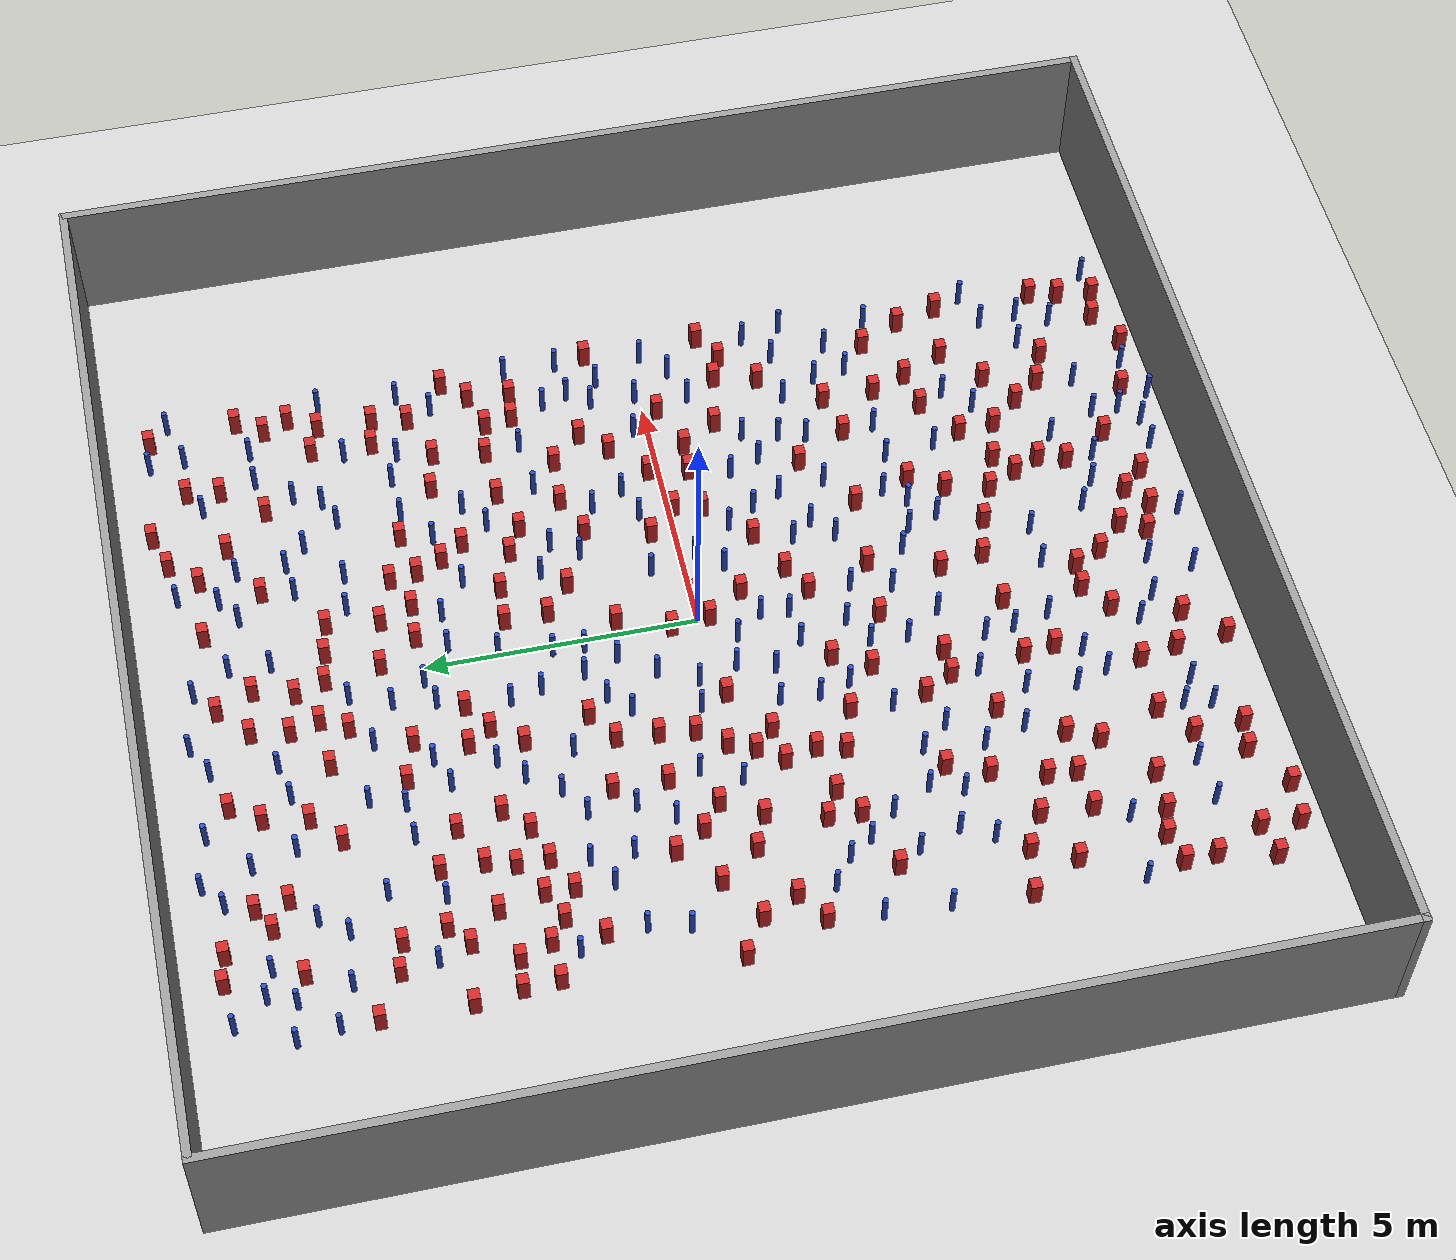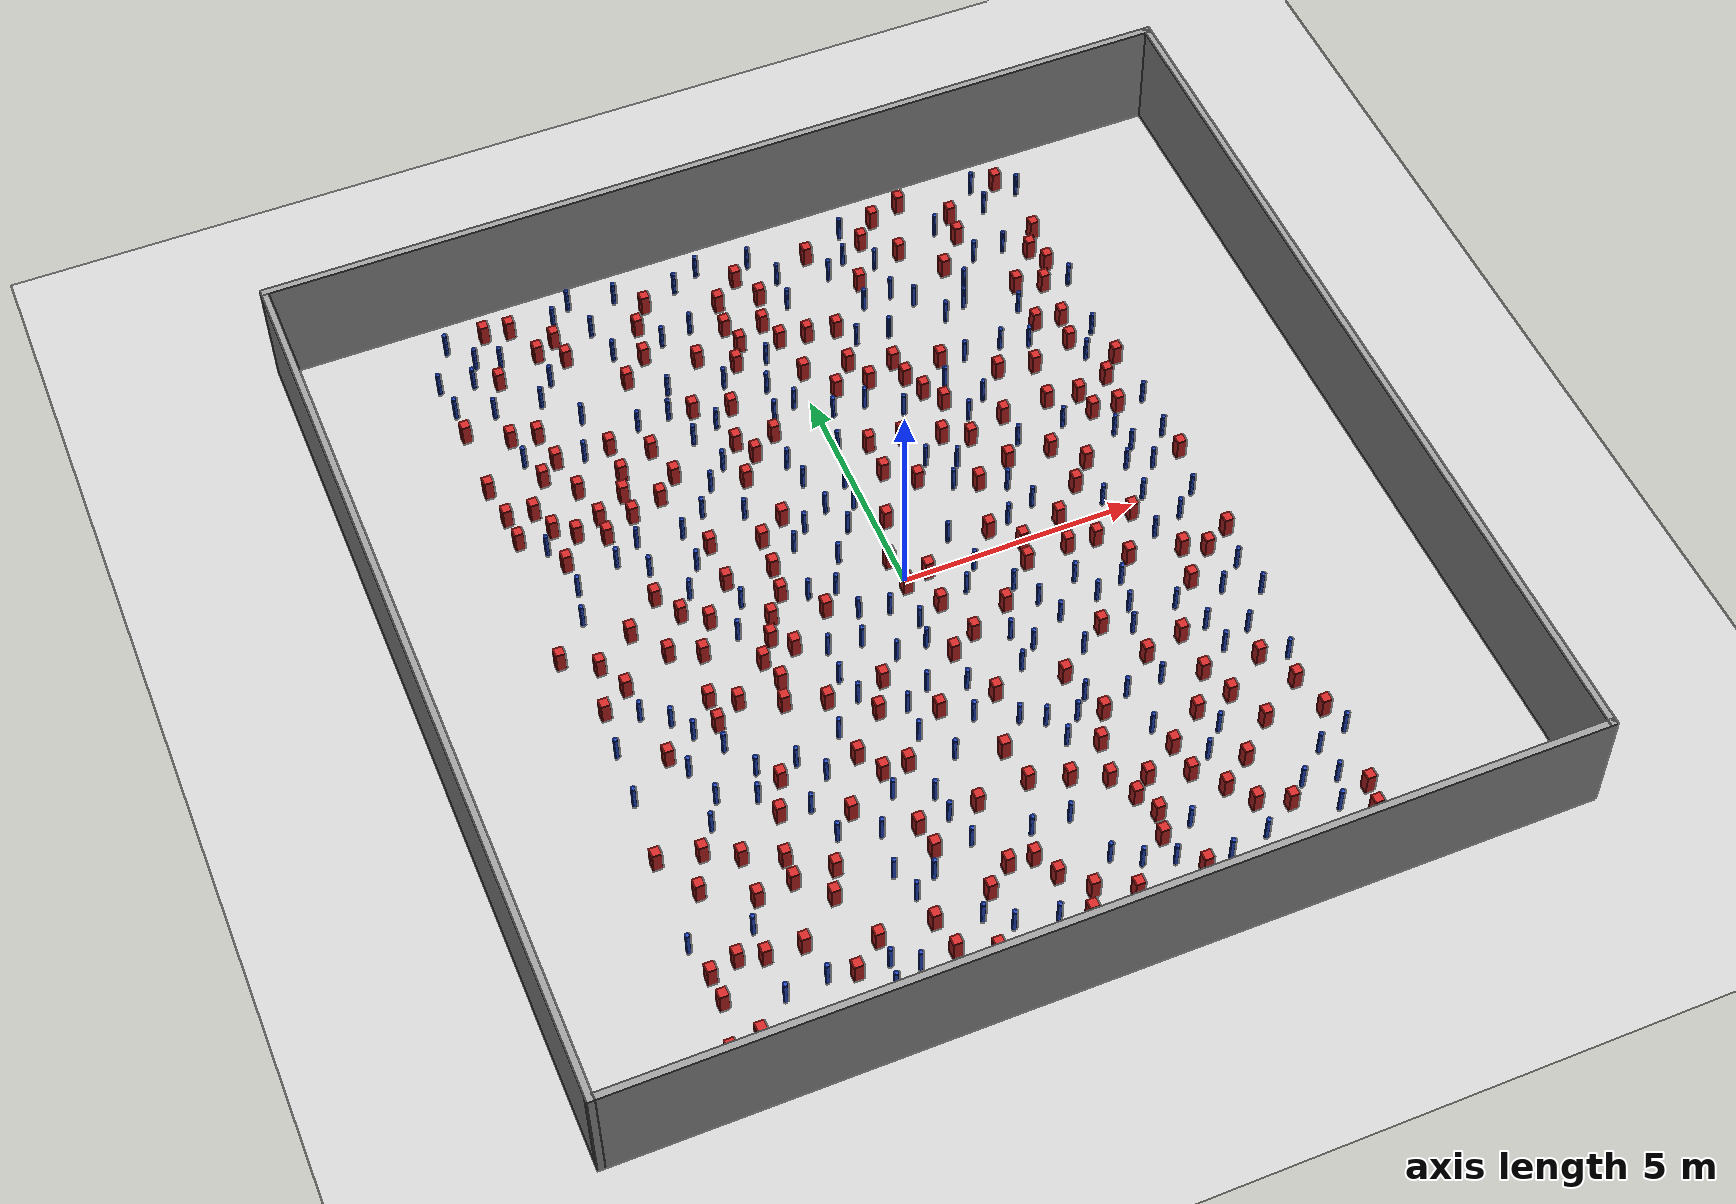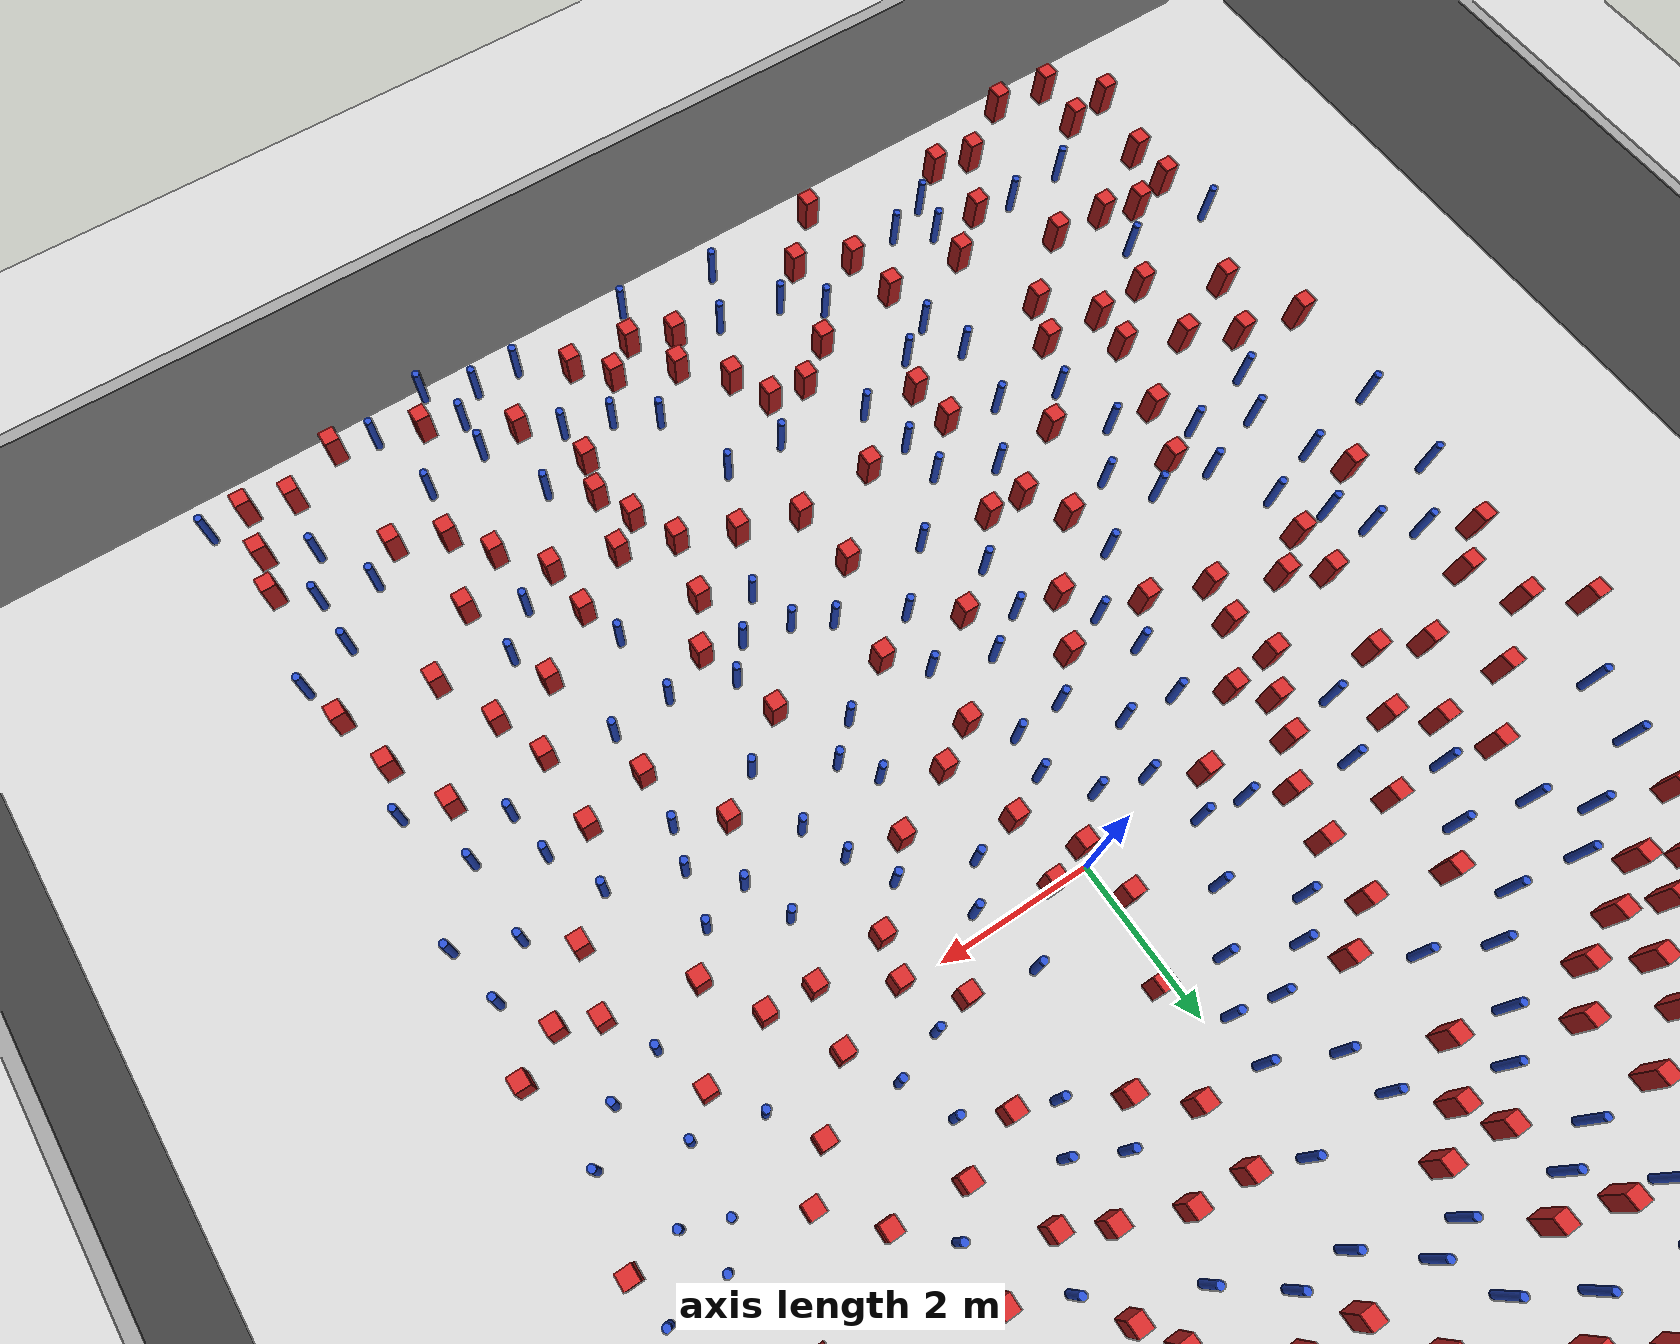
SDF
<sdf version="1.6">
 <world name="default">
  <light name="sun" type="directional">
   <pose>0 0 1000 0 -0 0</pose>
   <diffuse>0.8 0.8 0.8 1</diffuse>
   <specular>0.1 0.1 0.1 1</specular>
   <attenuation>
    <range>1000</range>
    <constant>0.9</constant>
    <linear>0.01</linear>
    <quadratic>0.001</quadratic>
   </attenuation>
   <direction>-0.5 0.5 -1</direction>
  </light>
  <model name="ground_plane">
   <static>1</static>
   <link name="link">
    <collision name="collision">
     <geometry><plane><normal>0 0 1</normal><size>100 100</size></plane></geometry>
     <surface><friction><ode><mu>100</mu><mu2>50</mu2></ode></friction></surface>
    </collision>
    <visual name="visual">
     <cast_shadows>0</cast_shadows>
     <geometry><plane><normal>0 0 1</normal><size>100 100</size></plane></geometry>
     <material>
      <ambient>1.0 1.0 1.0 1.0</ambient>
      <diffuse>0.8 0.8 0.8 1.0</diffuse>
      <specular>0.01 0.01 0.01 1.000000</specular>
     </material>
    </visual>
   </link>
  </model>
  <gravity>0 0 -9.8</gravity>
  <magnetic_field>6e-06 2.3e-05 -4.2e-05</magnetic_field>
  <atmosphere type="adiabatic"/>
  <physics name="default_physics" default="0" type="ode">
   <max_step_size>0.001</max_step_size>
   <real_time_factor>1</real_time_factor>
   <real_time_update_rate>1000</real_time_update_rate>
  </physics>
  <scene><ambient>0.4 0.4 0.4 1</ambient><background>0.7 0.7 0.7 1</background><shadows>1</shadows></scene>
  <spherical_coordinates>
   <surface_model>EARTH_WGS84</surface_model>
   <latitude_deg>0</latitude_deg>
   <longitude_deg>0</longitude_deg>
   <elevation>0</elevation>
   <heading_deg>0</heading_deg>
  </spherical_coordinates>
  <plugin name="gazebo_occupancy_map" filename="libgazebo_2Dmap_plugin.so">
   <map_resolution>0.05</map_resolution>
   <map_topic>generated_map</map_topic>
   <map_height>0.01</map_height>
   <map_size_x>50</map_size_x>
   <map_size_y>50</map_size_y>
  </plugin>
  <model name="NamedLocations">
   <static>true</static>
   <link name="DefaultStart"><pose>8.5 0 0 0 0 3.14</pose></link>
  </model>
  <model name="20x20_walls">
   <pose>0.044518 0.176112 0 0 -0 0</pose>
   <link name="Wall_1">
    <collision name="Wall_1_Collision">
     <geometry><box><size>20 0.15 2.5</size></box></geometry>
     <pose>0 0 1.25 0 -0 0</pose>
    </collision>
    <visual name="Wall_1_Visual">
     <pose>0 0 1.25 0 -0 0</pose>
     <geometry><box><size>20 0.15 2.5</size></box></geometry>
     <material>
      <script><uri>file://media/materials/scripts/gazebo.material</uri><name>Gazebo/Grey</name></script>
      <ambient>0.976471 0.992157 1 1</ambient>
     </material>
     <meta><layer>0</layer></meta>
    </visual>
    <pose>0 9.925 0 0 -0 0</pose>
   </link>
   <link name="Wall_3">
    <collision name="Wall_3_Collision">
     <geometry><box><size>20 0.15 2.5</size></box></geometry>
     <pose>0 0 1.25 0 -0 0</pose>
    </collision>
    <visual name="Wall_3_Visual">
     <pose>0 0 1.25 0 -0 0</pose>
     <geometry><box><size>20 0.15 2.5</size></box></geometry>
     <material>
      <script><uri>file://media/materials/scripts/gazebo.material</uri><name>Gazebo/Grey</name></script>
      <ambient>0.976471 0.992157 1 1</ambient>
     </material>
     <meta><layer>0</layer></meta>
    </visual>
    <pose>9.925 0 0 0 0 -1.5708</pose>
   </link>
   <link name="Wall_4">
    <collision name="Wall_4_Collision">
     <geometry><box><size>20 0.15 2.5</size></box></geometry>
     <pose>0 0 1.25 0 -0 0</pose>
    </collision>
    <visual name="Wall_4_Visual">
     <pose>0 0 1.25 0 -0 0</pose>
     <geometry><box><size>20 0.15 2.5</size></box></geometry>
     <material>
      <script><uri>file://media/materials/scripts/gazebo.material</uri><name>Gazebo/Grey</name></script>
      <ambient>0.976471 0.992157 1 1</ambient>
     </material>
     <meta><layer>0</layer></meta>
    </visual>
    <pose>0 -9.925 0 0 -0 3.14159</pose>
   </link>
   <link name="Wall_5">
    <collision name="Wall_5_Collision">
     <geometry><box><size>20 0.15 2.5</size></box></geometry>
     <pose>0 0 1.25 0 -0 0</pose>
    </collision>
    <visual name="Wall_5_Visual">
     <pose>0 0 1.25 0 -0 0</pose>
     <geometry><box><size>20 0.15 2.5</size></box></geometry>
     <material>
      <script><uri>file://media/materials/scripts/gazebo.material</uri><name>Gazebo/Grey</name></script>
      <ambient>0.976471 0.992157 1 1</ambient>
     </material>
     <meta><layer>0</layer></meta>
    </visual>
    <pose>-9.925 0 0 0 -0 1.5708</pose>
   </link>
   <static>1</static>
  </model>
  <model name="square_post_obstacle0">
   <static>true</static>
   <pose>2.64326265349 2.7935497767 -6.11067671241e-07 -5.50515727128e-06 -8.79689657224e-07 2.37013304536e-05</pose>
   <link name="link">
    <pose>0 0 0.25 0 -0 0</pose>
    <inertial>
     <mass>100</mass>
     <inertia>
      <ixx>0.166667</ixx>
      <ixy>0</ixy>
      <ixz>0</ixz>
      <iyy>0.166667</iyy>
      <iyz>0</iyz>
      <izz>0.166667</izz>
     </inertia>
    </inertial>
    <collision name="collision"><geometry><box><size>.2 .2 .5</size></box></geometry></collision>
    <visual name="visual">
     <geometry><box><size>.2 .2 .5</size></box></geometry>
     <material>
      <script><name>Gazebo/Red</name><uri>file://media/materials/scripts/gazebo.material</uri></script>
     </material>
    </visual>
   </link>
  </model>
  <model name="square_post_obstacle1">
   <static>true</static>
   <pose>5.86830122638 -1.66071499697 -6.11067671241e-07 -5.50515727128e-06 -8.79689657224e-07 2.37013304536e-05</pose>
   <link name="link">
    <pose>0 0 0.25 0 -0 0</pose>
    <inertial>
     <mass>100</mass>
     <inertia>
      <ixx>0.166667</ixx>
      <ixy>0</ixy>
      <ixz>0</ixz>
      <iyy>0.166667</iyy>
      <iyz>0</iyz>
      <izz>0.166667</izz>
     </inertia>
    </inertial>
    <collision name="collision"><geometry><box><size>.2 .2 .5</size></box></geometry></collision>
    <visual name="visual">
     <geometry><box><size>.2 .2 .5</size></box></geometry>
     <material>
      <script><name>Gazebo/Red</name><uri>file://media/materials/scripts/gazebo.material</uri></script>
     </material>
    </visual>
   </link>
  </model>
  <model name="pole_obstacle0">
   <static>true</static>
   <pose>4.72568806612 7.41263253163 -9.47619616065e-06 5.49618799737e-07 2.36310414037e-07 -1.55090534814e-07</pose>
   <link name="link">
    <pose>0 0 0.3 0 -0 0</pose>
    <inertial>
     <mass>1</mass>
     <inertia><ixx>0.145833</ixx><ixy>0</ixy><ixz>0</ixz><iyy>0.145833</iyy><iyz>0</iyz><izz>0.125</izz></inertia>
    </inertial>
    <collision name="collision">
     <geometry><cylinder><radius>0.05</radius><length>.6</length></cylinder></geometry>
    </collision>
    <visual name="visual">
     <geometry><cylinder><radius>0.05</radius><length>.6</length></cylinder></geometry>
     <material>
      <script><name>Gazebo/Blue</name><uri>file://media/materials/scripts/gazebo.material</uri></script>
     </material>
    </visual>
   </link>
  </model>
  <model name="square_post_obstacle2">
   <static>true</static>
   <pose>-4.26368688177 -8.88945568207 -6.11067671241e-07 -5.50515727128e-06 -8.79689657224e-07 2.37013304536e-05</pose>
   <link name="link">
    <pose>0 0 0.25 0 -0 0</pose>
    <inertial>
     <mass>100</mass>
     <inertia>
      <ixx>0.166667</ixx>
      <ixy>0</ixy>
      <ixz>0</ixz>
      <iyy>0.166667</iyy>
      <iyz>0</iyz>
      <izz>0.166667</izz>
     </inertia>
    </inertial>
    <collision name="collision"><geometry><box><size>.2 .2 .5</size></box></geometry></collision>
    <visual name="visual">
     <geometry><box><size>.2 .2 .5</size></box></geometry>
     <material>
      <script><name>Gazebo/Red</name><uri>file://media/materials/scripts/gazebo.material</uri></script>
     </material>
    </visual>
   </link>
  </model>
  <model name="pole_obstacle1">
   <static>true</static>
   <pose>1.67325718551 4.01669044763 -9.47619616065e-06 5.49618799737e-07 2.3631041406e-07 -1.55090534801e-07</pose>
   <link name="link">
    <pose>0 0 0.3 0 -0 0</pose>
    <inertial>
     <mass>1</mass>
     <inertia><ixx>0.145833</ixx><ixy>0</ixy><ixz>0</ixz><iyy>0.145833</iyy><iyz>0</iyz><izz>0.125</izz></inertia>
    </inertial>
    <collision name="collision">
     <geometry><cylinder><radius>0.05</radius><length>.6</length></cylinder></geometry>
    </collision>
    <visual name="visual">
     <geometry><cylinder><radius>0.05</radius><length>.6</length></cylinder></geometry>
     <material>
      <script><name>Gazebo/Blue</name><uri>file://media/materials/scripts/gazebo.material</uri></script>
     </material>
    </visual>
   </link>
  </model>
  <model name="square_post_obstacle3">
   <static>true</static>
   <pose>5.77406285056 6.09286928561 -6.11067671241e-07 -5.50515727128e-06 -8.79689657224e-07 2.37013304536e-05</pose>
   <link name="link">
    <pose>0 0 0.25 0 -0 0</pose>
    <inertial>
     <mass>100</mass>
     <inertia>
      <ixx>0.166667</ixx>
      <ixy>0</ixy>
      <ixz>0</ixz>
      <iyy>0.166667</iyy>
      <iyz>0</iyz>
      <izz>0.166667</izz>
     </inertia>
    </inertial>
    <collision name="collision"><geometry><box><size>.2 .2 .5</size></box></geometry></collision>
    <visual name="visual">
     <geometry><box><size>.2 .2 .5</size></box></geometry>
     <material>
      <script><name>Gazebo/Red</name><uri>file://media/materials/scripts/gazebo.material</uri></script>
     </material>
    </visual>
   </link>
  </model>
  <model name="pole_obstacle2">
   <static>true</static>
   <pose>-3.78344839935 9.44254157931 -9.4761961606e-06 5.49618799729e-07 2.36310414e-07 -1.55090534824e-07</pose>
   <link name="link">
    <pose>0 0 0.3 0 -0 0</pose>
    <inertial>
     <mass>1</mass>
     <inertia><ixx>0.145833</ixx><ixy>0</ixy><ixz>0</ixz><iyy>0.145833</iyy><iyz>0</iyz><izz>0.125</izz></inertia>
    </inertial>
    <collision name="collision">
     <geometry><cylinder><radius>0.05</radius><length>.6</length></cylinder></geometry>
    </collision>
    <visual name="visual">
     <geometry><cylinder><radius>0.05</radius><length>.6</length></cylinder></geometry>
     <material>
      <script><name>Gazebo/Blue</name><uri>file://media/materials/scripts/gazebo.material</uri></script>
     </material>
    </visual>
   </link>
  </model>
  <model name="pole_obstacle3">
   <static>true</static>
   <pose>-0.15549464812 -1.1225898299 -9.47619616065e-06 5.49618799737e-07 2.36310414067e-07 -1.55090534796e-07</pose>
   <link name="link">
    <pose>0 0 0.3 0 -0 0</pose>
    <inertial>
     <mass>1</mass>
     <inertia><ixx>0.145833</ixx><ixy>0</ixy><ixz>0</ixz><iyy>0.145833</iyy><iyz>0</iyz><izz>0.125</izz></inertia>
    </inertial>
    <collision name="collision">
     <geometry><cylinder><radius>0.05</radius><length>.6</length></cylinder></geometry>
    </collision>
    <visual name="visual">
     <geometry><cylinder><radius>0.05</radius><length>.6</length></cylinder></geometry>
     <material>
      <script><name>Gazebo/Blue</name><uri>file://media/materials/scripts/gazebo.material</uri></script>
     </material>
    </visual>
   </link>
  </model>
  <model name="square_post_obstacle4">
   <static>true</static>
   <pose>-6.01725565641 -0.414345068226 -6.11067671241e-07 -5.50515727128e-06 -8.79689657224e-07 2.37013304536e-05</pose>
   <link name="link">
    <pose>0 0 0.25 0 -0 0</pose>
    <inertial>
     <mass>100</mass>
     <inertia>
      <ixx>0.166667</ixx>
      <ixy>0</ixy>
      <ixz>0</ixz>
      <iyy>0.166667</iyy>
      <iyz>0</iyz>
      <izz>0.166667</izz>
     </inertia>
    </inertial>
    <collision name="collision"><geometry><box><size>.2 .2 .5</size></box></geometry></collision>
    <visual name="visual">
     <geometry><box><size>.2 .2 .5</size></box></geometry>
     <material>
      <script><name>Gazebo/Red</name><uri>file://media/materials/scripts/gazebo.material</uri></script>
     </material>
    </visual>
   </link>
  </model>
  <model name="square_post_obstacle5">
   <static>true</static>
   <pose>0.531658014159 -3.27056971357 -6.11067671241e-07 -5.50515727128e-06 -8.79689657224e-07 2.37013304536e-05</pose>
   <link name="link">
    <pose>0 0 0.25 0 -0 0</pose>
    <inertial>
     <mass>100</mass>
     <inertia>
      <ixx>0.166667</ixx>
      <ixy>0</ixy>
      <ixz>0</ixz>
      <iyy>0.166667</iyy>
      <iyz>0</iyz>
      <izz>0.166667</izz>
     </inertia>
    </inertial>
    <collision name="collision"><geometry><box><size>.2 .2 .5</size></box></geometry></collision>
    <visual name="visual">
     <geometry><box><size>.2 .2 .5</size></box></geometry>
     <material>
      <script><name>Gazebo/Red</name><uri>file://media/materials/scripts/gazebo.material</uri></script>
     </material>
    </visual>
   </link>
  </model>
  <model name="square_post_obstacle6">
   <static>true</static>
   <pose>-2.53700611456 -2.19720525429 -6.11067671241e-07 -5.50515727128e-06 -8.79689657224e-07 2.37013304536e-05</pose>
   <link name="link">
    <pose>0 0 0.25 0 -0 0</pose>
    <inertial>
     <mass>100</mass>
     <inertia>
      <ixx>0.166667</ixx>
      <ixy>0</ixy>
      <ixz>0</ixz>
      <iyy>0.166667</iyy>
      <iyz>0</iyz>
      <izz>0.166667</izz>
     </inertia>
    </inertial>
    <collision name="collision"><geometry><box><size>.2 .2 .5</size></box></geometry></collision>
    <visual name="visual">
     <geometry><box><size>.2 .2 .5</size></box></geometry>
     <material>
      <script><name>Gazebo/Red</name><uri>file://media/materials/scripts/gazebo.material</uri></script>
     </material>
    </visual>
   </link>
  </model>
  <model name="pole_obstacle4">
   <static>true</static>
   <pose>-2.65251913917 -6.87422880931 -9.47619616065e-06 5.49618799738e-07 2.3631041406e-07 -1.55090534801e-07</pose>
   <link name="link">
    <pose>0 0 0.3 0 -0 0</pose>
    <inertial>
     <mass>1</mass>
     <inertia><ixx>0.145833</ixx><ixy>0</ixy><ixz>0</ixz><iyy>0.145833</iyy><iyz>0</iyz><izz>0.125</izz></inertia>
    </inertial>
    <collision name="collision">
     <geometry><cylinder><radius>0.05</radius><length>.6</length></cylinder></geometry>
    </collision>
    <visual name="visual">
     <geometry><cylinder><radius>0.05</radius><length>.6</length></cylinder></geometry>
     <material>
      <script><name>Gazebo/Blue</name><uri>file://media/materials/scripts/gazebo.material</uri></script>
     </material>
    </visual>
   </link>
  </model>
  <model name="pole_obstacle5">
   <static>true</static>
   <pose>-0.953068003208 3.04514547028 -9.47619616065e-06 5.49618799737e-07 2.36310414063e-07 -1.55090534799e-07</pose>
   <link name="link">
    <pose>0 0 0.3 0 -0 0</pose>
    <inertial>
     <mass>1</mass>
     <inertia><ixx>0.145833</ixx><ixy>0</ixy><ixz>0</ixz><iyy>0.145833</iyy><iyz>0</iyz><izz>0.125</izz></inertia>
    </inertial>
    <collision name="collision">
     <geometry><cylinder><radius>0.05</radius><length>.6</length></cylinder></geometry>
    </collision>
    <visual name="visual">
     <geometry><cylinder><radius>0.05</radius><length>.6</length></cylinder></geometry>
     <material>
      <script><name>Gazebo/Blue</name><uri>file://media/materials/scripts/gazebo.material</uri></script>
     </material>
    </visual>
   </link>
  </model>
  <model name="square_post_obstacle7">
   <static>true</static>
   <pose>-4.31570606751 8.01415446722 -6.11067671241e-07 -5.50515727128e-06 -8.79689657224e-07 2.37013304536e-05</pose>
   <link name="link">
    <pose>0 0 0.25 0 -0 0</pose>
    <inertial>
     <mass>100</mass>
     <inertia>
      <ixx>0.166667</ixx>
      <ixy>0</ixy>
      <ixz>0</ixz>
      <iyy>0.166667</iyy>
      <iyz>0</iyz>
      <izz>0.166667</izz>
     </inertia>
    </inertial>
    <collision name="collision"><geometry><box><size>.2 .2 .5</size></box></geometry></collision>
    <visual name="visual">
     <geometry><box><size>.2 .2 .5</size></box></geometry>
     <material>
      <script><name>Gazebo/Red</name><uri>file://media/materials/scripts/gazebo.material</uri></script>
     </material>
    </visual>
   </link>
  </model>
  <model name="square_post_obstacle8">
   <static>true</static>
   <pose>5.17539859756 2.99115189557 -6.11067671241e-07 -5.50515727128e-06 -8.79689657224e-07 2.37013304536e-05</pose>
   <link name="link">
    <pose>0 0 0.25 0 -0 0</pose>
    <inertial>
     <mass>100</mass>
     <inertia>
      <ixx>0.166667</ixx>
      <ixy>0</ixy>
      <ixz>0</ixz>
      <iyy>0.166667</iyy>
      <iyz>0</iyz>
      <izz>0.166667</izz>
     </inertia>
    </inertial>
    <collision name="collision"><geometry><box><size>.2 .2 .5</size></box></geometry></collision>
    <visual name="visual">
     <geometry><box><size>.2 .2 .5</size></box></geometry>
     <material>
      <script><name>Gazebo/Red</name><uri>file://media/materials/scripts/gazebo.material</uri></script>
     </material>
    </visual>
   </link>
  </model>
  <model name="pole_obstacle6">
   <static>true</static>
   <pose>-1.71180021635 -7.7803199983 -9.47619616065e-06 5.49618799737e-07 2.36310414061e-07 -1.550905348e-07</pose>
   <link name="link">
    <pose>0 0 0.3 0 -0 0</pose>
    <inertial>
     <mass>1</mass>
     <inertia><ixx>0.145833</ixx><ixy>0</ixy><ixz>0</ixz><iyy>0.145833</iyy><iyz>0</iyz><izz>0.125</izz></inertia>
    </inertial>
    <collision name="collision">
     <geometry><cylinder><radius>0.05</radius><length>.6</length></cylinder></geometry>
    </collision>
    <visual name="visual">
     <geometry><cylinder><radius>0.05</radius><length>.6</length></cylinder></geometry>
     <material>
      <script><name>Gazebo/Blue</name><uri>file://media/materials/scripts/gazebo.material</uri></script>
     </material>
    </visual>
   </link>
  </model>
  <model name="pole_obstacle7">
   <static>true</static>
   <pose>1.34908433303 -4.80452183431 -9.47619616065e-06 5.49618799737e-07 2.36310414061e-07 -1.550905348e-07</pose>
   <link name="link">
    <pose>0 0 0.3 0 -0 0</pose>
    <inertial>
     <mass>1</mass>
     <inertia><ixx>0.145833</ixx><ixy>0</ixy><ixz>0</ixz><iyy>0.145833</iyy><iyz>0</iyz><izz>0.125</izz></inertia>
    </inertial>
    <collision name="collision">
     <geometry><cylinder><radius>0.05</radius><length>.6</length></cylinder></geometry>
    </collision>
    <visual name="visual">
     <geometry><cylinder><radius>0.05</radius><length>.6</length></cylinder></geometry>
     <material>
      <script><name>Gazebo/Blue</name><uri>file://media/materials/scripts/gazebo.material</uri></script>
     </material>
    </visual>
   </link>
  </model>
  <model name="square_post_obstacle9">
   <static>true</static>
   <pose>2.01188806093 0.438989155133 -6.11067671241e-07 -5.50515727128e-06 -8.79689657224e-07 2.37013304536e-05</pose>
   <link name="link">
    <pose>0 0 0.25 0 -0 0</pose>
    <inertial>
     <mass>100</mass>
     <inertia>
      <ixx>0.166667</ixx>
      <ixy>0</ixy>
      <ixz>0</ixz>
      <iyy>0.166667</iyy>
      <iyz>0</iyz>
      <izz>0.166667</izz>
     </inertia>
    </inertial>
    <collision name="collision"><geometry><box><size>.2 .2 .5</size></box></geometry></collision>
    <visual name="visual">
     <geometry><box><size>.2 .2 .5</size></box></geometry>
     <material>
      <script><name>Gazebo/Red</name><uri>file://media/materials/scripts/gazebo.material</uri></script>
     </material>
    </visual>
   </link>
  </model>
  <model name="square_post_obstacle10">
   <static>true</static>
   <pose>0.407130714451 -8.02818823955 -6.11067671241e-07 -5.50515727128e-06 -8.79689657224e-07 2.37013304536e-05</pose>
   <link name="link">
    <pose>0 0 0.25 0 -0 0</pose>
    <inertial>
     <mass>100</mass>
     <inertia>
      <ixx>0.166667</ixx>
      <ixy>0</ixy>
      <ixz>0</ixz>
      <iyy>0.166667</iyy>
      <iyz>0</iyz>
      <izz>0.166667</izz>
     </inertia>
    </inertial>
    <collision name="collision"><geometry><box><size>.2 .2 .5</size></box></geometry></collision>
    <visual name="visual">
     <geometry><box><size>.2 .2 .5</size></box></geometry>
     <material>
      <script><name>Gazebo/Red</name><uri>file://media/materials/scripts/gazebo.material</uri></script>
     </material>
    </visual>
   </link>
  </model>
  <model name="square_post_obstacle11">
   <static>true</static>
   <pose>-2.65082815415 -0.750428980162 -6.11067671241e-07 -5.50515727128e-06 -8.79689657224e-07 2.37013304536e-05</pose>
   <link name="link">
    <pose>0 0 0.25 0 -0 0</pose>
    <inertial>
     <mass>100</mass>
     <inertia>
      <ixx>0.166667</ixx>
      <ixy>0</ixy>
      <ixz>0</ixz>
      <iyy>0.166667</iyy>
      <iyz>0</iyz>
      <izz>0.166667</izz>
     </inertia>
    </inertial>
    <collision name="collision"><geometry><box><size>.2 .2 .5</size></box></geometry></collision>
    <visual name="visual">
     <geometry><box><size>.2 .2 .5</size></box></geometry>
     <material>
      <script><name>Gazebo/Red</name><uri>file://media/materials/scripts/gazebo.material</uri></script>
     </material>
    </visual>
   </link>
  </model>
  <model name="square_post_obstacle12">
   <static>true</static>
   <pose>-2.48388535579 -3.58912054183 -6.11067671241e-07 -5.50515727128e-06 -8.79689657224e-07 2.37013304536e-05</pose>
   <link name="link">
    <pose>0 0 0.25 0 -0 0</pose>
    <inertial>
     <mass>100</mass>
     <inertia>
      <ixx>0.166667</ixx>
      <ixy>0</ixy>
      <ixz>0</ixz>
      <iyy>0.166667</iyy>
      <iyz>0</iyz>
      <izz>0.166667</izz>
     </inertia>
    </inertial>
    <collision name="collision"><geometry><box><size>.2 .2 .5</size></box></geometry></collision>
    <visual name="visual">
     <geometry><box><size>.2 .2 .5</size></box></geometry>
     <material>
      <script><name>Gazebo/Red</name><uri>file://media/materials/scripts/gazebo.material</uri></script>
     </material>
    </visual>
   </link>
  </model>
  <model name="square_post_obstacle13">
   <static>true</static>
   <pose>4.85556807542 -0.253288321257 -6.11067671241e-07 -5.50515727128e-06 -8.79689657224e-07 2.37013304536e-05</pose>
   <link name="link">
    <pose>0 0 0.25 0 -0 0</pose>
    <inertial>
     <mass>100</mass>
     <inertia>
      <ixx>0.166667</ixx>
      <ixy>0</ixy>
      <ixz>0</ixz>
      <iyy>0.166667</iyy>
      <iyz>0</iyz>
      <izz>0.166667</izz>
     </inertia>
    </inertial>
    <collision name="collision"><geometry><box><size>.2 .2 .5</size></box></geometry></collision>
    <visual name="visual">
     <geometry><box><size>.2 .2 .5</size></box></geometry>
     <material>
      <script><name>Gazebo/Red</name><uri>file://media/materials/scripts/gazebo.material</uri></script>
     </material>
    </visual>
   </link>
  </model>
  <model name="pole_obstacle8">
   <static>true</static>
   <pose>1.50054680214 6.17369226299 -9.47619616065e-06 5.49618799737e-07 2.36310414061e-07 -1.550905348e-07</pose>
   <link name="link">
    <pose>0 0 0.3 0 -0 0</pose>
    <inertial>
     <mass>1</mass>
     <inertia><ixx>0.145833</ixx><ixy>0</ixy><ixz>0</ixz><iyy>0.145833</iyy><iyz>0</iyz><izz>0.125</izz></inertia>
    </inertial>
    <collision name="collision">
     <geometry><cylinder><radius>0.05</radius><length>.6</length></cylinder></geometry>
    </collision>
    <visual name="visual">
     <geometry><cylinder><radius>0.05</radius><length>.6</length></cylinder></geometry>
     <material>
      <script><name>Gazebo/Blue</name><uri>file://media/materials/scripts/gazebo.material</uri></script>
     </material>
    </visual>
   </link>
  </model>
  <model name="square_post_obstacle14">
   <static>true</static>
   <pose>3.66743329634 -6.95763202497 -6.11067671241e-07 -5.50515727128e-06 -8.79689657224e-07 2.37013304536e-05</pose>
   <link name="link">
    <pose>0 0 0.25 0 -0 0</pose>
    <inertial>
     <mass>100</mass>
     <inertia>
      <ixx>0.166667</ixx>
      <ixy>0</ixy>
      <ixz>0</ixz>
      <iyy>0.166667</iyy>
      <iyz>0</iyz>
      <izz>0.166667</izz>
     </inertia>
    </inertial>
    <collision name="collision"><geometry><box><size>.2 .2 .5</size></box></geometry></collision>
    <visual name="visual">
     <geometry><box><size>.2 .2 .5</size></box></geometry>
     <material>
      <script><name>Gazebo/Red</name><uri>file://media/materials/scripts/gazebo.material</uri></script>
     </material>
    </visual>
   </link>
  </model>
  <model name="square_post_obstacle15">
   <static>true</static>
   <pose>-2.33421557105 1.21266840727 -6.11067671241e-07 -5.50515727128e-06 -8.79689657224e-07 2.37013304536e-05</pose>
   <link name="link">
    <pose>0 0 0.25 0 -0 0</pose>
    <inertial>
     <mass>100</mass>
     <inertia>
      <ixx>0.166667</ixx>
      <ixy>0</ixy>
      <ixz>0</ixz>
      <iyy>0.166667</iyy>
      <iyz>0</iyz>
      <izz>0.166667</izz>
     </inertia>
    </inertial>
    <collision name="collision"><geometry><box><size>.2 .2 .5</size></box></geometry></collision>
    <visual name="visual">
     <geometry><box><size>.2 .2 .5</size></box></geometry>
     <material>
      <script><name>Gazebo/Red</name><uri>file://media/materials/scripts/gazebo.material</uri></script>
     </material>
    </visual>
   </link>
  </model>
  <model name="square_post_obstacle16">
   <static>true</static>
   <pose>0.141960145137 -4.55436350031 -6.11067671241e-07 -5.50515727128e-06 -8.79689657224e-07 2.37013304536e-05</pose>
   <link name="link">
    <pose>0 0 0.25 0 -0 0</pose>
    <inertial>
     <mass>100</mass>
     <inertia>
      <ixx>0.166667</ixx>
      <ixy>0</ixy>
      <ixz>0</ixz>
      <iyy>0.166667</iyy>
      <iyz>0</iyz>
      <izz>0.166667</izz>
     </inertia>
    </inertial>
    <collision name="collision"><geometry><box><size>.2 .2 .5</size></box></geometry></collision>
    <visual name="visual">
     <geometry><box><size>.2 .2 .5</size></box></geometry>
     <material>
      <script><name>Gazebo/Red</name><uri>file://media/materials/scripts/gazebo.material</uri></script>
     </material>
    </visual>
   </link>
  </model>
  <model name="pole_obstacle9">
   <static>true</static>
   <pose>-2.60821976817 -2.95990756869 -9.47619616065e-06 5.49618799737e-07 2.36310414051e-07 -1.55090534807e-07</pose>
   <link name="link">
    <pose>0 0 0.3 0 -0 0</pose>
    <inertial>
     <mass>1</mass>
     <inertia><ixx>0.145833</ixx><ixy>0</ixy><ixz>0</ixz><iyy>0.145833</iyy><iyz>0</iyz><izz>0.125</izz></inertia>
    </inertial>
    <collision name="collision">
     <geometry><cylinder><radius>0.05</radius><length>.6</length></cylinder></geometry>
    </collision>
    <visual name="visual">
     <geometry><cylinder><radius>0.05</radius><length>.6</length></cylinder></geometry>
     <material>
      <script><name>Gazebo/Blue</name><uri>file://media/materials/scripts/gazebo.material</uri></script>
     </material>
    </visual>
   </link>
  </model>
  <model name="square_post_obstacle17">
   <static>true</static>
   <pose>4.70733697189 8.68863369773 -6.11067671241e-07 -5.50515727128e-06 -8.79689657224e-07 2.37013304536e-05</pose>
   <link name="link">
    <pose>0 0 0.25 0 -0 0</pose>
    <inertial>
     <mass>100</mass>
     <inertia>
      <ixx>0.166667</ixx>
      <ixy>0</ixy>
      <ixz>0</ixz>
      <iyy>0.166667</iyy>
      <iyz>0</iyz>
      <izz>0.166667</izz>
     </inertia>
    </inertial>
    <collision name="collision"><geometry><box><size>.2 .2 .5</size></box></geometry></collision>
    <visual name="visual">
     <geometry><box><size>.2 .2 .5</size></box></geometry>
     <material>
      <script><name>Gazebo/Red</name><uri>file://media/materials/scripts/gazebo.material</uri></script>
     </material>
    </visual>
   </link>
  </model>
  <model name="square_post_obstacle18">
   <static>true</static>
   <pose>4.31982985695 -6.49465137461 -6.11067671241e-07 -5.50515727128e-06 -8.79689657224e-07 2.37013304536e-05</pose>
   <link name="link">
    <pose>0 0 0.25 0 -0 0</pose>
    <inertial>
     <mass>100</mass>
     <inertia>
      <ixx>0.166667</ixx>
      <ixy>0</ixy>
      <ixz>0</ixz>
      <iyy>0.166667</iyy>
      <iyz>0</iyz>
      <izz>0.166667</izz>
     </inertia>
    </inertial>
    <collision name="collision"><geometry><box><size>.2 .2 .5</size></box></geometry></collision>
    <visual name="visual">
     <geometry><box><size>.2 .2 .5</size></box></geometry>
     <material>
      <script><name>Gazebo/Red</name><uri>file://media/materials/scripts/gazebo.material</uri></script>
     </material>
    </visual>
   </link>
  </model>
  <model name="pole_obstacle10">
   <static>true</static>
   <pose>-3.21601077242 0.668306440457 -9.47619616065e-06 5.49618799737e-07 2.36310414035e-07 -1.55090534817e-07</pose>
   <link name="link">
    <pose>0 0 0.3 0 -0 0</pose>
    <inertial>
     <mass>1</mass>
     <inertia><ixx>0.145833</ixx><ixy>0</ixy><ixz>0</ixz><iyy>0.145833</iyy><iyz>0</iyz><izz>0.125</izz></inertia>
    </inertial>
    <collision name="collision">
     <geometry><cylinder><radius>0.05</radius><length>.6</length></cylinder></geometry>
    </collision>
    <visual name="visual">
     <geometry><cylinder><radius>0.05</radius><length>.6</length></cylinder></geometry>
     <material>
      <script><name>Gazebo/Blue</name><uri>file://media/materials/scripts/gazebo.material</uri></script>
     </material>
    </visual>
   </link>
  </model>
  <model name="square_post_obstacle19">
   <static>true</static>
   <pose>2.12141466955 3.06621668363 -6.11067671241e-07 -5.50515727128e-06 -8.79689657224e-07 2.37013304536e-05</pose>
   <link name="link">
    <pose>0 0 0.25 0 -0 0</pose>
    <inertial>
     <mass>100</mass>
     <inertia>
      <ixx>0.166667</ixx>
      <ixy>0</ixy>
      <ixz>0</ixz>
      <iyy>0.166667</iyy>
      <iyz>0</iyz>
      <izz>0.166667</izz>
     </inertia>
    </inertial>
    <collision name="collision"><geometry><box><size>.2 .2 .5</size></box></geometry></collision>
    <visual name="visual">
     <geometry><box><size>.2 .2 .5</size></box></geometry>
     <material>
      <script><name>Gazebo/Red</name><uri>file://media/materials/scripts/gazebo.material</uri></script>
     </material>
    </visual>
   </link>
  </model>
  <model name="pole_obstacle11">
   <static>true</static>
   <pose>-3.18876839636 -3.75957769436 -9.47619616065e-06 5.49618799737e-07 2.36310414051e-07 -1.55090534807e-07</pose>
   <link name="link">
    <pose>0 0 0.3 0 -0 0</pose>
    <inertial>
     <mass>1</mass>
     <inertia><ixx>0.145833</ixx><ixy>0</ixy><ixz>0</ixz><iyy>0.145833</iyy><iyz>0</iyz><izz>0.125</izz></inertia>
    </inertial>
    <collision name="collision">
     <geometry><cylinder><radius>0.05</radius><length>.6</length></cylinder></geometry>
    </collision>
    <visual name="visual">
     <geometry><cylinder><radius>0.05</radius><length>.6</length></cylinder></geometry>
     <material>
      <script><name>Gazebo/Blue</name><uri>file://media/materials/scripts/gazebo.material</uri></script>
     </material>
    </visual>
   </link>
  </model>
  <model name="square_post_obstacle20">
   <static>true</static>
   <pose>-5.98654859498 -4.50883899803 -6.11067671241e-07 -5.50515727128e-06 -8.79689657224e-07 2.37013304536e-05</pose>
   <link name="link">
    <pose>0 0 0.25 0 -0 0</pose>
    <inertial>
     <mass>100</mass>
     <inertia>
      <ixx>0.166667</ixx>
      <ixy>0</ixy>
      <ixz>0</ixz>
      <iyy>0.166667</iyy>
      <iyz>0</iyz>
      <izz>0.166667</izz>
     </inertia>
    </inertial>
    <collision name="collision"><geometry><box><size>.2 .2 .5</size></box></geometry></collision>
    <visual name="visual">
     <geometry><box><size>.2 .2 .5</size></box></geometry>
     <material>
      <script><name>Gazebo/Red</name><uri>file://media/materials/scripts/gazebo.material</uri></script>
     </material>
    </visual>
   </link>
  </model>
  <model name="pole_obstacle12">
   <static>true</static>
   <pose>-4.60165757841 2.87989179332 -9.47619616065e-06 5.49618799738e-07 2.36310414051e-07 -1.55090534805e-07</pose>
   <link name="link">
    <pose>0 0 0.3 0 -0 0</pose>
    <inertial>
     <mass>1</mass>
     <inertia><ixx>0.145833</ixx><ixy>0</ixy><ixz>0</ixz><iyy>0.145833</iyy><iyz>0</iyz><izz>0.125</izz></inertia>
    </inertial>
    <collision name="collision">
     <geometry><cylinder><radius>0.05</radius><length>.6</length></cylinder></geometry>
    </collision>
    <visual name="visual">
     <geometry><cylinder><radius>0.05</radius><length>.6</length></cylinder></geometry>
     <material>
      <script><name>Gazebo/Blue</name><uri>file://media/materials/scripts/gazebo.material</uri></script>
     </material>
    </visual>
   </link>
  </model>
  <model name="square_post_obstacle21">
   <static>true</static>
   <pose>3.56158704081 -9.02046082583 -6.11067671241e-07 -5.50515727128e-06 -8.79689657224e-07 2.37013304536e-05</pose>
   <link name="link">
    <pose>0 0 0.25 0 -0 0</pose>
    <inertial>
     <mass>100</mass>
     <inertia>
      <ixx>0.166667</ixx>
      <ixy>0</ixy>
      <ixz>0</ixz>
      <iyy>0.166667</iyy>
      <iyz>0</iyz>
      <izz>0.166667</izz>
     </inertia>
    </inertial>
    <collision name="collision"><geometry><box><size>.2 .2 .5</size></box></geometry></collision>
    <visual name="visual">
     <geometry><box><size>.2 .2 .5</size></box></geometry>
     <material>
      <script><name>Gazebo/Red</name><uri>file://media/materials/scripts/gazebo.material</uri></script>
     </material>
    </visual>
   </link>
  </model>
  <model name="pole_obstacle13">
   <static>true</static>
   <pose>-3.36392764118 7.75118814584 -9.47619616065e-06 5.49618799738e-07 2.3631041406e-07 -1.55090534801e-07</pose>
   <link name="link">
    <pose>0 0 0.3 0 -0 0</pose>
    <inertial>
     <mass>1</mass>
     <inertia><ixx>0.145833</ixx><ixy>0</ixy><ixz>0</ixz><iyy>0.145833</iyy><iyz>0</iyz><izz>0.125</izz></inertia>
    </inertial>
    <collision name="collision">
     <geometry><cylinder><radius>0.05</radius><length>.6</length></cylinder></geometry>
    </collision>
    <visual name="visual">
     <geometry><cylinder><radius>0.05</radius><length>.6</length></cylinder></geometry>
     <material>
      <script><name>Gazebo/Blue</name><uri>file://media/materials/scripts/gazebo.material</uri></script>
     </material>
    </visual>
   </link>
  </model>
  <model name="square_post_obstacle22">
   <static>true</static>
   <pose>4.44872754876 -3.39286007502 -6.11067671241e-07 -5.50515727128e-06 -8.79689657224e-07 2.37013304536e-05</pose>
   <link name="link">
    <pose>0 0 0.25 0 -0 0</pose>
    <inertial>
     <mass>100</mass>
     <inertia>
      <ixx>0.166667</ixx>
      <ixy>0</ixy>
      <ixz>0</ixz>
      <iyy>0.166667</iyy>
      <iyz>0</iyz>
      <izz>0.166667</izz>
     </inertia>
    </inertial>
    <collision name="collision"><geometry><box><size>.2 .2 .5</size></box></geometry></collision>
    <visual name="visual">
     <geometry><box><size>.2 .2 .5</size></box></geometry>
     <material>
      <script><name>Gazebo/Red</name><uri>file://media/materials/scripts/gazebo.material</uri></script>
     </material>
    </visual>
   </link>
  </model>
  <model name="pole_obstacle14">
   <static>true</static>
   <pose>-2.64990605663 6.39541912761 -9.47619616065e-06 5.49618799738e-07 2.3631041406e-07 -1.55090534801e-07</pose>
   <link name="link">
    <pose>0 0 0.3 0 -0 0</pose>
    <inertial>
     <mass>1</mass>
     <inertia><ixx>0.145833</ixx><ixy>0</ixy><ixz>0</ixz><iyy>0.145833</iyy><iyz>0</iyz><izz>0.125</izz></inertia>
    </inertial>
    <collision name="collision">
     <geometry><cylinder><radius>0.05</radius><length>.6</length></cylinder></geometry>
    </collision>
    <visual name="visual">
     <geometry><cylinder><radius>0.05</radius><length>.6</length></cylinder></geometry>
     <material>
      <script><name>Gazebo/Blue</name><uri>file://media/materials/scripts/gazebo.material</uri></script>
     </material>
    </visual>
   </link>
  </model>
  <model name="pole_obstacle15">
   <static>true</static>
   <pose>-3.56824416237 8.55106198889 -9.47619616065e-06 5.49618799738e-07 2.36310414059e-07 -1.55090534802e-07</pose>
   <link name="link">
    <pose>0 0 0.3 0 -0 0</pose>
    <inertial>
     <mass>1</mass>
     <inertia><ixx>0.145833</ixx><ixy>0</ixy><ixz>0</ixz><iyy>0.145833</iyy><iyz>0</iyz><izz>0.125</izz></inertia>
    </inertial>
    <collision name="collision">
     <geometry><cylinder><radius>0.05</radius><length>.6</length></cylinder></geometry>
    </collision>
    <visual name="visual">
     <geometry><cylinder><radius>0.05</radius><length>.6</length></cylinder></geometry>
     <material>
      <script><name>Gazebo/Blue</name><uri>file://media/materials/scripts/gazebo.material</uri></script>
     </material>
    </visual>
   </link>
  </model>
  <model name="pole_obstacle16">
   <static>true</static>
   <pose>-0.883943718322 -1.69384752411 -9.47619616065e-06 5.49618799738e-07 2.36310414061e-07 -1.55090534801e-07</pose>
   <link name="link">
    <pose>0 0 0.3 0 -0 0</pose>
    <inertial>
     <mass>1</mass>
     <inertia><ixx>0.145833</ixx><ixy>0</ixy><ixz>0</ixz><iyy>0.145833</iyy><iyz>0</iyz><izz>0.125</izz></inertia>
    </inertial>
    <collision name="collision">
     <geometry><cylinder><radius>0.05</radius><length>.6</length></cylinder></geometry>
    </collision>
    <visual name="visual">
     <geometry><cylinder><radius>0.05</radius><length>.6</length></cylinder></geometry>
     <material>
      <script><name>Gazebo/Blue</name><uri>file://media/materials/scripts/gazebo.material</uri></script>
     </material>
    </visual>
   </link>
  </model>
  <model name="square_post_obstacle23">
   <static>true</static>
   <pose>0.218265977354 1.46688420381 -6.11067671241e-07 -5.50515727128e-06 -8.79689657224e-07 2.37013304536e-05</pose>
   <link name="link">
    <pose>0 0 0.25 0 -0 0</pose>
    <inertial>
     <mass>100</mass>
     <inertia>
      <ixx>0.166667</ixx>
      <ixy>0</ixy>
      <ixz>0</ixz>
      <iyy>0.166667</iyy>
      <iyz>0</iyz>
      <izz>0.166667</izz>
     </inertia>
    </inertial>
    <collision name="collision"><geometry><box><size>.2 .2 .5</size></box></geometry></collision>
    <visual name="visual">
     <geometry><box><size>.2 .2 .5</size></box></geometry>
     <material>
      <script><name>Gazebo/Red</name><uri>file://media/materials/scripts/gazebo.material</uri></script>
     </material>
    </visual>
   </link>
  </model>
  <model name="pole_obstacle17">
   <static>true</static>
   <pose>-5.16976492625 7.09836857027 -9.47619616065e-06 5.49618799737e-07 2.36310414037e-07 -1.55090534814e-07</pose>
   <link name="link">
    <pose>0 0 0.3 0 -0 0</pose>
    <inertial>
     <mass>1</mass>
     <inertia><ixx>0.145833</ixx><ixy>0</ixy><ixz>0</ixz><iyy>0.145833</iyy><iyz>0</iyz><izz>0.125</izz></inertia>
    </inertial>
    <collision name="collision">
     <geometry><cylinder><radius>0.05</radius><length>.6</length></cylinder></geometry>
    </collision>
    <visual name="visual">
     <geometry><cylinder><radius>0.05</radius><length>.6</length></cylinder></geometry>
     <material>
      <script><name>Gazebo/Blue</name><uri>file://media/materials/scripts/gazebo.material</uri></script>
     </material>
    </visual>
   </link>
  </model>
  <model name="square_post_obstacle24">
   <static>true</static>
   <pose>-6.07646952085 6.38595414594 -6.11067671241e-07 -5.50515727128e-06 -8.79689657224e-07 2.37013304536e-05</pose>
   <link name="link">
    <pose>0 0 0.25 0 -0 0</pose>
    <inertial>
     <mass>100</mass>
     <inertia>
      <ixx>0.166667</ixx>
      <ixy>0</ixy>
      <ixz>0</ixz>
      <iyy>0.166667</iyy>
      <iyz>0</iyz>
      <izz>0.166667</izz>
     </inertia>
    </inertial>
    <collision name="collision"><geometry><box><size>.2 .2 .5</size></box></geometry></collision>
    <visual name="visual">
     <geometry><box><size>.2 .2 .5</size></box></geometry>
     <material>
      <script><name>Gazebo/Red</name><uri>file://media/materials/scripts/gazebo.material</uri></script>
     </material>
    </visual>
   </link>
  </model>
  <model name="square_post_obstacle25">
   <static>true</static>
   <pose>-0.0867028003997 -7.50894193678 -6.11067671241e-07 -5.50515727128e-06 -8.79689657224e-07 2.37013304536e-05</pose>
   <link name="link">
    <pose>0 0 0.25 0 -0 0</pose>
    <inertial>
     <mass>100</mass>
     <inertia>
      <ixx>0.166667</ixx>
      <ixy>0</ixy>
      <ixz>0</ixz>
      <iyy>0.166667</iyy>
      <iyz>0</iyz>
      <izz>0.166667</izz>
     </inertia>
    </inertial>
    <collision name="collision"><geometry><box><size>.2 .2 .5</size></box></geometry></collision>
    <visual name="visual">
     <geometry><box><size>.2 .2 .5</size></box></geometry>
     <material>
      <script><name>Gazebo/Red</name><uri>file://media/materials/scripts/gazebo.material</uri></script>
     </material>
    </visual>
   </link>
  </model>
  <model name="square_post_obstacle26">
   <static>true</static>
   <pose>-6.92168142128 5.28564803276 -6.11067671241e-07 -5.50515727128e-06 -8.79689657224e-07 2.37013304536e-05</pose>
   <link name="link">
    <pose>0 0 0.25 0 -0 0</pose>
    <inertial>
     <mass>100</mass>
     <inertia>
      <ixx>0.166667</ixx>
      <ixy>0</ixy>
      <ixz>0</ixz>
      <iyy>0.166667</iyy>
      <iyz>0</iyz>
      <izz>0.166667</izz>
     </inertia>
    </inertial>
    <collision name="collision"><geometry><box><size>.2 .2 .5</size></box></geometry></collision>
    <visual name="visual">
     <geometry><box><size>.2 .2 .5</size></box></geometry>
     <material>
      <script><name>Gazebo/Red</name><uri>file://media/materials/scripts/gazebo.material</uri></script>
     </material>
    </visual>
   </link>
  </model>
  <model name="square_post_obstacle27">
   <static>true</static>
   <pose>-4.41894908498 0.850606576677 -6.11067671241e-07 -5.50515727128e-06 -8.79689657224e-07 2.37013304536e-05</pose>
   <link name="link">
    <pose>0 0 0.25 0 -0 0</pose>
    <inertial>
     <mass>100</mass>
     <inertia>
      <ixx>0.166667</ixx>
      <ixy>0</ixy>
      <ixz>0</ixz>
      <iyy>0.166667</iyy>
      <iyz>0</iyz>
      <izz>0.166667</izz>
     </inertia>
    </inertial>
    <collision name="collision"><geometry><box><size>.2 .2 .5</size></box></geometry></collision>
    <visual name="visual">
     <geometry><box><size>.2 .2 .5</size></box></geometry>
     <material>
      <script><name>Gazebo/Red</name><uri>file://media/materials/scripts/gazebo.material</uri></script>
     </material>
    </visual>
   </link>
  </model>
  <model name="pole_obstacle18">
   <static>true</static>
   <pose>6.17961129785 -4.61160275627 -9.47619616065e-06 5.49618799737e-07 2.36310414037e-07 -1.55090534814e-07</pose>
   <link name="link">
    <pose>0 0 0.3 0 -0 0</pose>
    <inertial>
     <mass>1</mass>
     <inertia><ixx>0.145833</ixx><ixy>0</ixy><ixz>0</ixz><iyy>0.145833</iyy><iyz>0</iyz><izz>0.125</izz></inertia>
    </inertial>
    <collision name="collision">
     <geometry><cylinder><radius>0.05</radius><length>.6</length></cylinder></geometry>
    </collision>
    <visual name="visual">
     <geometry><cylinder><radius>0.05</radius><length>.6</length></cylinder></geometry>
     <material>
      <script><name>Gazebo/Blue</name><uri>file://media/materials/scripts/gazebo.material</uri></script>
     </material>
    </visual>
   </link>
  </model>
  <model name="square_post_obstacle28">
   <static>true</static>
   <pose>4.69967172629 -5.04763850451 -6.11067671241e-07 -5.50515727128e-06 -8.79689657224e-07 2.37013304536e-05</pose>
   <link name="link">
    <pose>0 0 0.25 0 -0 0</pose>
    <inertial>
     <mass>100</mass>
     <inertia>
      <ixx>0.166667</ixx>
      <ixy>0</ixy>
      <ixz>0</ixz>
      <iyy>0.166667</iyy>
      <iyz>0</iyz>
      <izz>0.166667</izz>
     </inertia>
    </inertial>
    <collision name="collision"><geometry><box><size>.2 .2 .5</size></box></geometry></collision>
    <visual name="visual">
     <geometry><box><size>.2 .2 .5</size></box></geometry>
     <material>
      <script><name>Gazebo/Red</name><uri>file://media/materials/scripts/gazebo.material</uri></script>
     </material>
    </visual>
   </link>
  </model>
  <model name="pole_obstacle19">
   <static>true</static>
   <pose>-0.420252584287 -8.31891217827 -9.47619616065e-06 5.49618799737e-07 2.36310414031e-07 -1.55090534818e-07</pose>
   <link name="link">
    <pose>0 0 0.3 0 -0 0</pose>
    <inertial>
     <mass>1</mass>
     <inertia><ixx>0.145833</ixx><ixy>0</ixy><ixz>0</ixz><iyy>0.145833</iyy><iyz>0</iyz><izz>0.125</izz></inertia>
    </inertial>
    <collision name="collision">
     <geometry><cylinder><radius>0.05</radius><length>.6</length></cylinder></geometry>
    </collision>
    <visual name="visual">
     <geometry><cylinder><radius>0.05</radius><length>.6</length></cylinder></geometry>
     <material>
      <script><name>Gazebo/Blue</name><uri>file://media/materials/scripts/gazebo.material</uri></script>
     </material>
    </visual>
   </link>
  </model>
  <model name="square_post_obstacle29">
   <static>true</static>
   <pose>0.725849916902 -8.71464412279 -6.11067671241e-07 -5.50515727128e-06 -8.79689657224e-07 2.37013304536e-05</pose>
   <link name="link">
    <pose>0 0 0.25 0 -0 0</pose>
    <inertial>
     <mass>100</mass>
     <inertia>
      <ixx>0.166667</ixx>
      <ixy>0</ixy>
      <ixz>0</ixz>
      <iyy>0.166667</iyy>
      <iyz>0</iyz>
      <izz>0.166667</izz>
     </inertia>
    </inertial>
    <collision name="collision"><geometry><box><size>.2 .2 .5</size></box></geometry></collision>
    <visual name="visual">
     <geometry><box><size>.2 .2 .5</size></box></geometry>
     <material>
      <script><name>Gazebo/Red</name><uri>file://media/materials/scripts/gazebo.material</uri></script>
     </material>
    </visual>
   </link>
  </model>
  <model name="square_post_obstacle30">
   <static>true</static>
   <pose>5.6018355657 4.41001559066 -6.11067671241e-07 -5.50515727128e-06 -8.79689657224e-07 2.37013304536e-05</pose>
   <link name="link">
    <pose>0 0 0.25 0 -0 0</pose>
    <inertial>
     <mass>100</mass>
     <inertia>
      <ixx>0.166667</ixx>
      <ixy>0</ixy>
      <ixz>0</ixz>
      <iyy>0.166667</iyy>
      <iyz>0</iyz>
      <izz>0.166667</izz>
     </inertia>
    </inertial>
    <collision name="collision"><geometry><box><size>.2 .2 .5</size></box></geometry></collision>
    <visual name="visual">
     <geometry><box><size>.2 .2 .5</size></box></geometry>
     <material>
      <script><name>Gazebo/Red</name><uri>file://media/materials/scripts/gazebo.material</uri></script>
     </material>
    </visual>
   </link>
  </model>
  <model name="pole_obstacle20">
   <static>true</static>
   <pose>3.11253889244 -1.29925664123 -9.47619616065e-06 5.49618799737e-07 2.36310414072e-07 -1.55090534793e-07</pose>
   <link name="link">
    <pose>0 0 0.3 0 -0 0</pose>
    <inertial>
     <mass>1</mass>
     <inertia><ixx>0.145833</ixx><ixy>0</ixy><ixz>0</ixz><iyy>0.145833</iyy><iyz>0</iyz><izz>0.125</izz></inertia>
    </inertial>
    <collision name="collision">
     <geometry><cylinder><radius>0.05</radius><length>.6</length></cylinder></geometry>
    </collision>
    <visual name="visual">
     <geometry><cylinder><radius>0.05</radius><length>.6</length></cylinder></geometry>
     <material>
      <script><name>Gazebo/Blue</name><uri>file://media/materials/scripts/gazebo.material</uri></script>
     </material>
    </visual>
   </link>
  </model>
  <model name="pole_obstacle21">
   <static>true</static>
   <pose>1.1973587895 0.607261237285 -9.47619616065e-06 5.49618799737e-07 2.36310414065e-07 -1.55090534798e-07</pose>
   <link name="link">
    <pose>0 0 0.3 0 -0 0</pose>
    <inertial>
     <mass>1</mass>
     <inertia><ixx>0.145833</ixx><ixy>0</ixy><ixz>0</ixz><iyy>0.145833</iyy><iyz>0</iyz><izz>0.125</izz></inertia>
    </inertial>
    <collision name="collision">
     <geometry><cylinder><radius>0.05</radius><length>.6</length></cylinder></geometry>
    </collision>
    <visual name="visual">
     <geometry><cylinder><radius>0.05</radius><length>.6</length></cylinder></geometry>
     <material>
      <script><name>Gazebo/Blue</name><uri>file://media/materials/scripts/gazebo.material</uri></script>
     </material>
    </visual>
   </link>
  </model>
  <model name="square_post_obstacle31">
   <static>true</static>
   <pose>1.58299561077 -1.37875278012 -6.11067671241e-07 -5.50515727128e-06 -8.79689657224e-07 2.37013304536e-05</pose>
   <link name="link">
    <pose>0 0 0.25 0 -0 0</pose>
    <inertial>
     <mass>100</mass>
     <inertia>
      <ixx>0.166667</ixx>
      <ixy>0</ixy>
      <ixz>0</ixz>
      <iyy>0.166667</iyy>
      <iyz>0</iyz>
      <izz>0.166667</izz>
     </inertia>
    </inertial>
    <collision name="collision"><geometry><box><size>.2 .2 .5</size></box></geometry></collision>
    <visual name="visual">
     <geometry><box><size>.2 .2 .5</size></box></geometry>
     <material>
      <script><name>Gazebo/Red</name><uri>file://media/materials/scripts/gazebo.material</uri></script>
     </material>
    </visual>
   </link>
  </model>
  <model name="pole_obstacle22">
   <static>true</static>
   <pose>-2.85965782607 5.77475315911 -9.47619616065e-06 5.49618799738e-07 2.3631041406e-07 -1.55090534801e-07</pose>
   <link name="link">
    <pose>0 0 0.3 0 -0 0</pose>
    <inertial>
     <mass>1</mass>
     <inertia><ixx>0.145833</ixx><ixy>0</ixy><ixz>0</ixz><iyy>0.145833</iyy><iyz>0</iyz><izz>0.125</izz></inertia>
    </inertial>
    <collision name="collision">
     <geometry><cylinder><radius>0.05</radius><length>.6</length></cylinder></geometry>
    </collision>
    <visual name="visual">
     <geometry><cylinder><radius>0.05</radius><length>.6</length></cylinder></geometry>
     <material>
      <script><name>Gazebo/Blue</name><uri>file://media/materials/scripts/gazebo.material</uri></script>
     </material>
    </visual>
   </link>
  </model>
  <model name="pole_obstacle23">
   <static>true</static>
   <pose>3.48770243604 6.05372144866 -9.47619616065e-06 5.49618799738e-07 2.3631041406e-07 -1.55090534801e-07</pose>
   <link name="link">
    <pose>0 0 0.3 0 -0 0</pose>
    <inertial>
     <mass>1</mass>
     <inertia><ixx>0.145833</ixx><ixy>0</ixy><ixz>0</ixz><iyy>0.145833</iyy><iyz>0</iyz><izz>0.125</izz></inertia>
    </inertial>
    <collision name="collision">
     <geometry><cylinder><radius>0.05</radius><length>.6</length></cylinder></geometry>
    </collision>
    <visual name="visual">
     <geometry><cylinder><radius>0.05</radius><length>.6</length></cylinder></geometry>
     <material>
      <script><name>Gazebo/Blue</name><uri>file://media/materials/scripts/gazebo.material</uri></script>
     </material>
    </visual>
   </link>
  </model>
  <model name="pole_obstacle24">
   <static>true</static>
   <pose>5.0156992939 5.70338469669 -9.47619616065e-06 5.49618799737e-07 2.36310414037e-07 -1.55090534814e-07</pose>
   <link name="link">
    <pose>0 0 0.3 0 -0 0</pose>
    <inertial>
     <mass>1</mass>
     <inertia><ixx>0.145833</ixx><ixy>0</ixy><ixz>0</ixz><iyy>0.145833</iyy><iyz>0</iyz><izz>0.125</izz></inertia>
    </inertial>
    <collision name="collision">
     <geometry><cylinder><radius>0.05</radius><length>.6</length></cylinder></geometry>
    </collision>
    <visual name="visual">
     <geometry><cylinder><radius>0.05</radius><length>.6</length></cylinder></geometry>
     <material>
      <script><name>Gazebo/Blue</name><uri>file://media/materials/scripts/gazebo.material</uri></script>
     </material>
    </visual>
   </link>
  </model>
  <model name="pole_obstacle25">
   <static>true</static>
   <pose>0.714060411418 -3.9877952971 -9.47619616065e-06 5.49618799737e-07 2.3631041408e-07 -1.55090534791e-07</pose>
   <link name="link">
    <pose>0 0 0.3 0 -0 0</pose>
    <inertial>
     <mass>1</mass>
     <inertia><ixx>0.145833</ixx><ixy>0</ixy><ixz>0</ixz><iyy>0.145833</iyy><iyz>0</iyz><izz>0.125</izz></inertia>
    </inertial>
    <collision name="collision">
     <geometry><cylinder><radius>0.05</radius><length>.6</length></cylinder></geometry>
    </collision>
    <visual name="visual">
     <geometry><cylinder><radius>0.05</radius><length>.6</length></cylinder></geometry>
     <material>
      <script><name>Gazebo/Blue</name><uri>file://media/materials/scripts/gazebo.material</uri></script>
     </material>
    </visual>
   </link>
  </model>
  <model name="pole_obstacle26">
   <static>true</static>
   <pose>-1.1735871492 -0.448895654991 -9.47619616065e-06 5.49618799737e-07 2.36310414064e-07 -1.55090534799e-07</pose>
   <link name="link">
    <pose>0 0 0.3 0 -0 0</pose>
    <inertial>
     <mass>1</mass>
     <inertia><ixx>0.145833</ixx><ixy>0</ixy><ixz>0</ixz><iyy>0.145833</iyy><iyz>0</iyz><izz>0.125</izz></inertia>
    </inertial>
    <collision name="collision">
     <geometry><cylinder><radius>0.05</radius><length>.6</length></cylinder></geometry>
    </collision>
    <visual name="visual">
     <geometry><cylinder><radius>0.05</radius><length>.6</length></cylinder></geometry>
     <material>
      <script><name>Gazebo/Blue</name><uri>file://media/materials/scripts/gazebo.material</uri></script>
     </material>
    </visual>
   </link>
  </model>
  <model name="pole_obstacle27">
   <static>true</static>
   <pose>-1.41031372814 -5.51074239256 -9.47619616065e-06 5.49618799737e-07 2.36310414061e-07 -1.550905348e-07</pose>
   <link name="link">
    <pose>0 0 0.3 0 -0 0</pose>
    <inertial>
     <mass>1</mass>
     <inertia><ixx>0.145833</ixx><ixy>0</ixy><ixz>0</ixz><iyy>0.145833</iyy><iyz>0</iyz><izz>0.125</izz></inertia>
    </inertial>
    <collision name="collision">
     <geometry><cylinder><radius>0.05</radius><length>.6</length></cylinder></geometry>
    </collision>
    <visual name="visual">
     <geometry><cylinder><radius>0.05</radius><length>.6</length></cylinder></geometry>
     <material>
      <script><name>Gazebo/Blue</name><uri>file://media/materials/scripts/gazebo.material</uri></script>
     </material>
    </visual>
   </link>
  </model>
  <model name="square_post_obstacle32">
   <static>true</static>
   <pose>4.03051807676 1.88196295636 -6.11067671241e-07 -5.50515727128e-06 -8.79689657224e-07 2.37013304536e-05</pose>
   <link name="link">
    <pose>0 0 0.25 0 -0 0</pose>
    <inertial>
     <mass>100</mass>
     <inertia>
      <ixx>0.166667</ixx>
      <ixy>0</ixy>
      <ixz>0</ixz>
      <iyy>0.166667</iyy>
      <iyz>0</iyz>
      <izz>0.166667</izz>
     </inertia>
    </inertial>
    <collision name="collision"><geometry><box><size>.2 .2 .5</size></box></geometry></collision>
    <visual name="visual">
     <geometry><box><size>.2 .2 .5</size></box></geometry>
     <material>
      <script><name>Gazebo/Red</name><uri>file://media/materials/scripts/gazebo.material</uri></script>
     </material>
    </visual>
   </link>
  </model>
  <model name="square_post_obstacle33">
   <static>true</static>
   <pose>2.22971651345 -6.98378692423 -6.11067671241e-07 -5.50515727128e-06 -8.79689657224e-07 2.37013304536e-05</pose>
   <link name="link">
    <pose>0 0 0.25 0 -0 0</pose>
    <inertial>
     <mass>100</mass>
     <inertia>
      <ixx>0.166667</ixx>
      <ixy>0</ixy>
      <ixz>0</ixz>
      <iyy>0.166667</iyy>
      <iyz>0</iyz>
      <izz>0.166667</izz>
     </inertia>
    </inertial>
    <collision name="collision"><geometry><box><size>.2 .2 .5</size></box></geometry></collision>
    <visual name="visual">
     <geometry><box><size>.2 .2 .5</size></box></geometry>
     <material>
      <script><name>Gazebo/Red</name><uri>file://media/materials/scripts/gazebo.material</uri></script>
     </material>
    </visual>
   </link>
  </model>
  <model name="pole_obstacle28">
   <static>true</static>
   <pose>5.0760457368 -0.890218081996 -9.47619616065e-06 5.49618799737e-07 2.36310414061e-07 -1.550905348e-07</pose>
   <link name="link">
    <pose>0 0 0.3 0 -0 0</pose>
    <inertial>
     <mass>1</mass>
     <inertia><ixx>0.145833</ixx><ixy>0</ixy><ixz>0</ixz><iyy>0.145833</iyy><iyz>0</iyz><izz>0.125</izz></inertia>
    </inertial>
    <collision name="collision">
     <geometry><cylinder><radius>0.05</radius><length>.6</length></cylinder></geometry>
    </collision>
    <visual name="visual">
     <geometry><cylinder><radius>0.05</radius><length>.6</length></cylinder></geometry>
     <material>
      <script><name>Gazebo/Blue</name><uri>file://media/materials/scripts/gazebo.material</uri></script>
     </material>
    </visual>
   </link>
  </model>
  <model name="pole_obstacle29">
   <static>true</static>
   <pose>0.0483259557495 3.65297619411 -9.4761961606e-06 5.49618799729e-07 2.36310413998e-07 -1.55090534825e-07</pose>
   <link name="link">
    <pose>0 0 0.3 0 -0 0</pose>
    <inertial>
     <mass>1</mass>
     <inertia><ixx>0.145833</ixx><ixy>0</ixy><ixz>0</ixz><iyy>0.145833</iyy><iyz>0</iyz><izz>0.125</izz></inertia>
    </inertial>
    <collision name="collision">
     <geometry><cylinder><radius>0.05</radius><length>.6</length></cylinder></geometry>
    </collision>
    <visual name="visual">
     <geometry><cylinder><radius>0.05</radius><length>.6</length></cylinder></geometry>
     <material>
      <script><name>Gazebo/Blue</name><uri>file://media/materials/scripts/gazebo.material</uri></script>
     </material>
    </visual>
   </link>
  </model>
  <model name="square_post_obstacle34">
   <static>true</static>
   <pose>0.638338198088 2.637271387 -6.11067671241e-07 -5.50515727128e-06 -8.79689657224e-07 2.37013304536e-05</pose>
   <link name="link">
    <pose>0 0 0.25 0 -0 0</pose>
    <inertial>
     <mass>100</mass>
     <inertia>
      <ixx>0.166667</ixx>
      <ixy>0</ixy>
      <ixz>0</ixz>
      <iyy>0.166667</iyy>
      <iyz>0</iyz>
      <izz>0.166667</izz>
     </inertia>
    </inertial>
    <collision name="collision"><geometry><box><size>.2 .2 .5</size></box></geometry></collision>
    <visual name="visual">
     <geometry><box><size>.2 .2 .5</size></box></geometry>
     <material>
      <script><name>Gazebo/Red</name><uri>file://media/materials/scripts/gazebo.material</uri></script>
     </material>
    </visual>
   </link>
  </model>
  <model name="pole_obstacle30">
   <static>true</static>
   <pose>5.00867443221 -3.35146531265 -9.47619616065e-06 5.49618799738e-07 2.36310414051e-07 -1.55090534805e-07</pose>
   <link name="link">
    <pose>0 0 0.3 0 -0 0</pose>
    <inertial>
     <mass>1</mass>
     <inertia><ixx>0.145833</ixx><ixy>0</ixy><ixz>0</ixz><iyy>0.145833</iyy><iyz>0</iyz><izz>0.125</izz></inertia>
    </inertial>
    <collision name="collision">
     <geometry><cylinder><radius>0.05</radius><length>.6</length></cylinder></geometry>
    </collision>
    <visual name="visual">
     <geometry><cylinder><radius>0.05</radius><length>.6</length></cylinder></geometry>
     <material>
      <script><name>Gazebo/Blue</name><uri>file://media/materials/scripts/gazebo.material</uri></script>
     </material>
    </visual>
   </link>
  </model>
  <model name="pole_obstacle31">
   <static>true</static>
   <pose>-0.565450874374 1.59621999711 -9.47619616065e-06 5.49618799738e-07 2.36310414061e-07 -1.55090534801e-07</pose>
   <link name="link">
    <pose>0 0 0.3 0 -0 0</pose>
    <inertial>
     <mass>1</mass>
     <inertia><ixx>0.145833</ixx><ixy>0</ixy><ixz>0</ixz><iyy>0.145833</iyy><iyz>0</iyz><izz>0.125</izz></inertia>
    </inertial>
    <collision name="collision">
     <geometry><cylinder><radius>0.05</radius><length>.6</length></cylinder></geometry>
    </collision>
    <visual name="visual">
     <geometry><cylinder><radius>0.05</radius><length>.6</length></cylinder></geometry>
     <material>
      <script><name>Gazebo/Blue</name><uri>file://media/materials/scripts/gazebo.material</uri></script>
     </material>
    </visual>
   </link>
  </model>
  <model name="pole_obstacle32">
   <static>true</static>
   <pose>-0.0679648866142 -3.59554564713 -9.47619616065e-06 5.49618799737e-07 2.36310414062e-07 -1.55090534799e-07</pose>
   <link name="link">
    <pose>0 0 0.3 0 -0 0</pose>
    <inertial>
     <mass>1</mass>
     <inertia><ixx>0.145833</ixx><ixy>0</ixy><ixz>0</ixz><iyy>0.145833</iyy><iyz>0</iyz><izz>0.125</izz></inertia>
    </inertial>
    <collision name="collision">
     <geometry><cylinder><radius>0.05</radius><length>.6</length></cylinder></geometry>
    </collision>
    <visual name="visual">
     <geometry><cylinder><radius>0.05</radius><length>.6</length></cylinder></geometry>
     <material>
      <script><name>Gazebo/Blue</name><uri>file://media/materials/scripts/gazebo.material</uri></script>
     </material>
    </visual>
   </link>
  </model>
  <model name="pole_obstacle33">
   <static>true</static>
   <pose>4.24775527219 4.91328178062 -9.47619616065e-06 5.49618799737e-07 2.36310414037e-07 -1.55090534814e-07</pose>
   <link name="link">
    <pose>0 0 0.3 0 -0 0</pose>
    <inertial>
     <mass>1</mass>
     <inertia><ixx>0.145833</ixx><ixy>0</ixy><ixz>0</ixz><iyy>0.145833</iyy><iyz>0</iyz><izz>0.125</izz></inertia>
    </inertial>
    <collision name="collision">
     <geometry><cylinder><radius>0.05</radius><length>.6</length></cylinder></geometry>
    </collision>
    <visual name="visual">
     <geometry><cylinder><radius>0.05</radius><length>.6</length></cylinder></geometry>
     <material>
      <script><name>Gazebo/Blue</name><uri>file://media/materials/scripts/gazebo.material</uri></script>
     </material>
    </visual>
   </link>
  </model>
  <model name="square_post_obstacle35">
   <static>true</static>
   <pose>3.08337548846 -2.60095719022 -6.11067671241e-07 -5.50515727128e-06 -8.79689657224e-07 2.37013304536e-05</pose>
   <link name="link">
    <pose>0 0 0.25 0 -0 0</pose>
    <inertial>
     <mass>100</mass>
     <inertia>
      <ixx>0.166667</ixx>
      <ixy>0</ixy>
      <ixz>0</ixz>
      <iyy>0.166667</iyy>
      <iyz>0</iyz>
      <izz>0.166667</izz>
     </inertia>
    </inertial>
    <collision name="collision"><geometry><box><size>.2 .2 .5</size></box></geometry></collision>
    <visual name="visual">
     <geometry><box><size>.2 .2 .5</size></box></geometry>
     <material>
      <script><name>Gazebo/Red</name><uri>file://media/materials/scripts/gazebo.material</uri></script>
     </material>
    </visual>
   </link>
  </model>
  <model name="pole_obstacle34">
   <static>true</static>
   <pose>5.47738878881 -8.13779262181 -9.47619616065e-06 5.49618799737e-07 2.36310414065e-07 -1.55090534796e-07</pose>
   <link name="link">
    <pose>0 0 0.3 0 -0 0</pose>
    <inertial>
     <mass>1</mass>
     <inertia><ixx>0.145833</ixx><ixy>0</ixy><ixz>0</ixz><iyy>0.145833</iyy><iyz>0</iyz><izz>0.125</izz></inertia>
    </inertial>
    <collision name="collision">
     <geometry><cylinder><radius>0.05</radius><length>.6</length></cylinder></geometry>
    </collision>
    <visual name="visual">
     <geometry><cylinder><radius>0.05</radius><length>.6</length></cylinder></geometry>
     <material>
      <script><name>Gazebo/Blue</name><uri>file://media/materials/scripts/gazebo.material</uri></script>
     </material>
    </visual>
   </link>
  </model>
  <model name="pole_obstacle35">
   <static>true</static>
   <pose>-0.220098208647 2.12647914286 -9.4761961606e-06 5.49618799729e-07 2.36310413995e-07 -1.55090534826e-07</pose>
   <link name="link">
    <pose>0 0 0.3 0 -0 0</pose>
    <inertial>
     <mass>1</mass>
     <inertia><ixx>0.145833</ixx><ixy>0</ixy><ixz>0</ixz><iyy>0.145833</iyy><iyz>0</iyz><izz>0.125</izz></inertia>
    </inertial>
    <collision name="collision">
     <geometry><cylinder><radius>0.05</radius><length>.6</length></cylinder></geometry>
    </collision>
    <visual name="visual">
     <geometry><cylinder><radius>0.05</radius><length>.6</length></cylinder></geometry>
     <material>
      <script><name>Gazebo/Blue</name><uri>file://media/materials/scripts/gazebo.material</uri></script>
     </material>
    </visual>
   </link>
  </model>
  <model name="pole_obstacle36">
   <static>true</static>
   <pose>-1.24522728171 -6.18781245235 -9.47619616065e-06 5.49618799737e-07 2.36310414061e-07 -1.550905348e-07</pose>
   <link name="link">
    <pose>0 0 0.3 0 -0 0</pose>
    <inertial>
     <mass>1</mass>
     <inertia><ixx>0.145833</ixx><ixy>0</ixy><ixz>0</ixz><iyy>0.145833</iyy><iyz>0</iyz><izz>0.125</izz></inertia>
    </inertial>
    <collision name="collision">
     <geometry><cylinder><radius>0.05</radius><length>.6</length></cylinder></geometry>
    </collision>
    <visual name="visual">
     <geometry><cylinder><radius>0.05</radius><length>.6</length></cylinder></geometry>
     <material>
      <script><name>Gazebo/Blue</name><uri>file://media/materials/scripts/gazebo.material</uri></script>
     </material>
    </visual>
   </link>
  </model>
  <model name="square_post_obstacle36">
   <static>true</static>
   <pose>-6.7682676209 -7.01912997487 -6.11067671241e-07 -5.50515727128e-06 -8.79689657224e-07 2.37013304536e-05</pose>
   <link name="link">
    <pose>0 0 0.25 0 -0 0</pose>
    <inertial>
     <mass>100</mass>
     <inertia>
      <ixx>0.166667</ixx>
      <ixy>0</ixy>
      <ixz>0</ixz>
      <iyy>0.166667</iyy>
      <iyz>0</iyz>
      <izz>0.166667</izz>
     </inertia>
    </inertial>
    <collision name="collision"><geometry><box><size>.2 .2 .5</size></box></geometry></collision>
    <visual name="visual">
     <geometry><box><size>.2 .2 .5</size></box></geometry>
     <material>
      <script><name>Gazebo/Red</name><uri>file://media/materials/scripts/gazebo.material</uri></script>
     </material>
    </visual>
   </link>
  </model>
  <model name="square_post_obstacle37">
   <static>true</static>
   <pose>-6.2001604014 -6.87545379439 -6.11067671241e-07 -5.50515727128e-06 -8.79689657224e-07 2.37013304536e-05</pose>
   <link name="link">
    <pose>0 0 0.25 0 -0 0</pose>
    <inertial>
     <mass>100</mass>
     <inertia>
      <ixx>0.166667</ixx>
      <ixy>0</ixy>
      <ixz>0</ixz>
      <iyy>0.166667</iyy>
      <iyz>0</iyz>
      <izz>0.166667</izz>
     </inertia>
    </inertial>
    <collision name="collision"><geometry><box><size>.2 .2 .5</size></box></geometry></collision>
    <visual name="visual">
     <geometry><box><size>.2 .2 .5</size></box></geometry>
     <material>
      <script><name>Gazebo/Red</name><uri>file://media/materials/scripts/gazebo.material</uri></script>
     </material>
    </visual>
   </link>
  </model>
  <model name="pole_obstacle37">
   <static>true</static>
   <pose>-0.751585349839 -4.26400418196 -9.47619616065e-06 5.49618799737e-07 2.36310414065e-07 -1.55090534796e-07</pose>
   <link name="link">
    <pose>0 0 0.3 0 -0 0</pose>
    <inertial>
     <mass>1</mass>
     <inertia><ixx>0.145833</ixx><ixy>0</ixy><ixz>0</ixz><iyy>0.145833</iyy><iyz>0</iyz><izz>0.125</izz></inertia>
    </inertial>
    <collision name="collision">
     <geometry><cylinder><radius>0.05</radius><length>.6</length></cylinder></geometry>
    </collision>
    <visual name="visual">
     <geometry><cylinder><radius>0.05</radius><length>.6</length></cylinder></geometry>
     <material>
      <script><name>Gazebo/Blue</name><uri>file://media/materials/scripts/gazebo.material</uri></script>
     </material>
    </visual>
   </link>
  </model>
  <model name="pole_obstacle38">
   <static>true</static>
   <pose>-2.16754230576 -6.57102361847 -9.47619616065e-06 5.49618799738e-07 2.3631041406e-07 -1.55090534801e-07</pose>
   <link name="link">
    <pose>0 0 0.3 0 -0 0</pose>
    <inertial>
     <mass>1</mass>
     <inertia><ixx>0.145833</ixx><ixy>0</ixy><ixz>0</ixz><iyy>0.145833</iyy><iyz>0</iyz><izz>0.125</izz></inertia>
    </inertial>
    <collision name="collision">
     <geometry><cylinder><radius>0.05</radius><length>.6</length></cylinder></geometry>
    </collision>
    <visual name="visual">
     <geometry><cylinder><radius>0.05</radius><length>.6</length></cylinder></geometry>
     <material>
      <script><name>Gazebo/Blue</name><uri>file://media/materials/scripts/gazebo.material</uri></script>
     </material>
    </visual>
   </link>
  </model>
  <model name="square_post_obstacle38">
   <static>true</static>
   <pose>0.642048165023 3.43116105708 -6.11067671241e-07 -5.50515727128e-06 -8.79689657224e-07 2.37013304536e-05</pose>
   <link name="link">
    <pose>0 0 0.25 0 -0 0</pose>
    <inertial>
     <mass>100</mass>
     <inertia>
      <ixx>0.166667</ixx>
      <ixy>0</ixy>
      <ixz>0</ixz>
      <iyy>0.166667</iyy>
      <iyz>0</iyz>
      <izz>0.166667</izz>
     </inertia>
    </inertial>
    <collision name="collision"><geometry><box><size>.2 .2 .5</size></box></geometry></collision>
    <visual name="visual">
     <geometry><box><size>.2 .2 .5</size></box></geometry>
     <material>
      <script><name>Gazebo/Red</name><uri>file://media/materials/scripts/gazebo.material</uri></script>
     </material>
    </visual>
   </link>
  </model>
  <model name="square_post_obstacle39">
   <static>true</static>
   <pose>-6.32148838797 0.246880284549 -6.11067671241e-07 -5.50515727128e-06 -8.79689657224e-07 2.37013304536e-05</pose>
   <link name="link">
    <pose>0 0 0.25 0 -0 0</pose>
    <inertial>
     <mass>100</mass>
     <inertia>
      <ixx>0.166667</ixx>
      <ixy>0</ixy>
      <ixz>0</ixz>
      <iyy>0.166667</iyy>
      <iyz>0</iyz>
      <izz>0.166667</izz>
     </inertia>
    </inertial>
    <collision name="collision"><geometry><box><size>.2 .2 .5</size></box></geometry></collision>
    <visual name="visual">
     <geometry><box><size>.2 .2 .5</size></box></geometry>
     <material>
      <script><name>Gazebo/Red</name><uri>file://media/materials/scripts/gazebo.material</uri></script>
     </material>
    </visual>
   </link>
  </model>
  <model name="pole_obstacle39">
   <static>true</static>
   <pose>2.09817483789 8.41139426477 -9.4761961606e-06 5.49618799729e-07 2.36310414e-07 -1.55090534824e-07</pose>
   <link name="link">
    <pose>0 0 0.3 0 -0 0</pose>
    <inertial>
     <mass>1</mass>
     <inertia><ixx>0.145833</ixx><ixy>0</ixy><ixz>0</ixz><iyy>0.145833</iyy><iyz>0</iyz><izz>0.125</izz></inertia>
    </inertial>
    <collision name="collision">
     <geometry><cylinder><radius>0.05</radius><length>.6</length></cylinder></geometry>
    </collision>
    <visual name="visual">
     <geometry><cylinder><radius>0.05</radius><length>.6</length></cylinder></geometry>
     <material>
      <script><name>Gazebo/Blue</name><uri>file://media/materials/scripts/gazebo.material</uri></script>
     </material>
    </visual>
   </link>
  </model>
  <model name="pole_obstacle40">
   <static>true</static>
   <pose>2.67155848395 8.01683245756 -9.47619616065e-06 5.49618799737e-07 2.3631041406e-07 -1.55090534799e-07</pose>
   <link name="link">
    <pose>0 0 0.3 0 -0 0</pose>
    <inertial>
     <mass>1</mass>
     <inertia><ixx>0.145833</ixx><ixy>0</ixy><ixz>0</ixz><iyy>0.145833</iyy><iyz>0</iyz><izz>0.125</izz></inertia>
    </inertial>
    <collision name="collision">
     <geometry><cylinder><radius>0.05</radius><length>.6</length></cylinder></geometry>
    </collision>
    <visual name="visual">
     <geometry><cylinder><radius>0.05</radius><length>.6</length></cylinder></geometry>
     <material>
      <script><name>Gazebo/Blue</name><uri>file://media/materials/scripts/gazebo.material</uri></script>
     </material>
    </visual>
   </link>
  </model>
  <model name="pole_obstacle41">
   <static>true</static>
   <pose>-4.75455141034 -2.41910875426 -9.47619616065e-06 5.49618799738e-07 2.36310414051e-07 -1.55090534805e-07</pose>
   <link name="link">
    <pose>0 0 0.3 0 -0 0</pose>
    <inertial>
     <mass>1</mass>
     <inertia><ixx>0.145833</ixx><ixy>0</ixy><ixz>0</ixz><iyy>0.145833</iyy><iyz>0</iyz><izz>0.125</izz></inertia>
    </inertial>
    <collision name="collision">
     <geometry><cylinder><radius>0.05</radius><length>.6</length></cylinder></geometry>
    </collision>
    <visual name="visual">
     <geometry><cylinder><radius>0.05</radius><length>.6</length></cylinder></geometry>
     <material>
      <script><name>Gazebo/Blue</name><uri>file://media/materials/scripts/gazebo.material</uri></script>
     </material>
    </visual>
   </link>
  </model>
  <model name="pole_obstacle42">
   <static>true</static>
   <pose>-5.57264430851 -2.67848662907 -9.47619616065e-06 5.49618799738e-07 2.36310414051e-07 -1.55090534805e-07</pose>
   <link name="link">
    <pose>0 0 0.3 0 -0 0</pose>
    <inertial>
     <mass>1</mass>
     <inertia><ixx>0.145833</ixx><ixy>0</ixy><ixz>0</ixz><iyy>0.145833</iyy><iyz>0</iyz><izz>0.125</izz></inertia>
    </inertial>
    <collision name="collision">
     <geometry><cylinder><radius>0.05</radius><length>.6</length></cylinder></geometry>
    </collision>
    <visual name="visual">
     <geometry><cylinder><radius>0.05</radius><length>.6</length></cylinder></geometry>
     <material>
      <script><name>Gazebo/Blue</name><uri>file://media/materials/scripts/gazebo.material</uri></script>
     </material>
    </visual>
   </link>
  </model>
  <model name="pole_obstacle43">
   <static>true</static>
   <pose>0.16672768601 9.10504932551 -9.47619616065e-06 5.49618799737e-07 2.36310414033e-07 -1.55090534817e-07</pose>
   <link name="link">
    <pose>0 0 0.3 0 -0 0</pose>
    <inertial>
     <mass>1</mass>
     <inertia><ixx>0.145833</ixx><ixy>0</ixy><ixz>0</ixz><iyy>0.145833</iyy><iyz>0</iyz><izz>0.125</izz></inertia>
    </inertial>
    <collision name="collision">
     <geometry><cylinder><radius>0.05</radius><length>.6</length></cylinder></geometry>
    </collision>
    <visual name="visual">
     <geometry><cylinder><radius>0.05</radius><length>.6</length></cylinder></geometry>
     <material>
      <script><name>Gazebo/Blue</name><uri>file://media/materials/scripts/gazebo.material</uri></script>
     </material>
    </visual>
   </link>
  </model>
  <model name="square_post_obstacle40">
   <static>true</static>
   <pose>5.05714401454 -5.8405931482 -6.11067671241e-07 -5.50515727128e-06 -8.79689657224e-07 2.37013304536e-05</pose>
   <link name="link">
    <pose>0 0 0.25 0 -0 0</pose>
    <inertial>
     <mass>100</mass>
     <inertia>
      <ixx>0.166667</ixx>
      <ixy>0</ixy>
      <ixz>0</ixz>
      <iyy>0.166667</iyy>
      <iyz>0</iyz>
      <izz>0.166667</izz>
     </inertia>
    </inertial>
    <collision name="collision"><geometry><box><size>.2 .2 .5</size></box></geometry></collision>
    <visual name="visual">
     <geometry><box><size>.2 .2 .5</size></box></geometry>
     <material>
      <script><name>Gazebo/Red</name><uri>file://media/materials/scripts/gazebo.material</uri></script>
     </material>
    </visual>
   </link>
  </model>
  <model name="square_post_obstacle41">
   <static>true</static>
   <pose>-0.83911123168 8.22910441483 -6.11067671241e-07 -5.50515727128e-06 -8.79689657224e-07 2.37013304536e-05</pose>
   <link name="link">
    <pose>0 0 0.25 0 -0 0</pose>
    <inertial>
     <mass>100</mass>
     <inertia>
      <ixx>0.166667</ixx>
      <ixy>0</ixy>
      <ixz>0</ixz>
      <iyy>0.166667</iyy>
      <iyz>0</iyz>
      <izz>0.166667</izz>
     </inertia>
    </inertial>
    <collision name="collision"><geometry><box><size>.2 .2 .5</size></box></geometry></collision>
    <visual name="visual">
     <geometry><box><size>.2 .2 .5</size></box></geometry>
     <material>
      <script><name>Gazebo/Red</name><uri>file://media/materials/scripts/gazebo.material</uri></script>
     </material>
    </visual>
   </link>
  </model>
  <model name="pole_obstacle44">
   <static>true</static>
   <pose>3.04289075134 6.73097264945 -9.47619616065e-06 5.49618799738e-07 2.3631041406e-07 -1.55090534801e-07</pose>
   <link name="link">
    <pose>0 0 0.3 0 -0 0</pose>
    <inertial>
     <mass>1</mass>
     <inertia><ixx>0.145833</ixx><ixy>0</ixy><ixz>0</ixz><iyy>0.145833</iyy><iyz>0</iyz><izz>0.125</izz></inertia>
    </inertial>
    <collision name="collision">
     <geometry><cylinder><radius>0.05</radius><length>.6</length></cylinder></geometry>
    </collision>
    <visual name="visual">
     <geometry><cylinder><radius>0.05</radius><length>.6</length></cylinder></geometry>
     <material>
      <script><name>Gazebo/Blue</name><uri>file://media/materials/scripts/gazebo.material</uri></script>
     </material>
    </visual>
   </link>
  </model>
  <model name="pole_obstacle45">
   <static>true</static>
   <pose>-4.38309300057 -3.14928430452 -9.47619616065e-06 5.49618799738e-07 2.36310414051e-07 -1.55090534805e-07</pose>
   <link name="link">
    <pose>0 0 0.3 0 -0 0</pose>
    <inertial>
     <mass>1</mass>
     <inertia><ixx>0.145833</ixx><ixy>0</ixy><ixz>0</ixz><iyy>0.145833</iyy><iyz>0</iyz><izz>0.125</izz></inertia>
    </inertial>
    <collision name="collision">
     <geometry><cylinder><radius>0.05</radius><length>.6</length></cylinder></geometry>
    </collision>
    <visual name="visual">
     <geometry><cylinder><radius>0.05</radius><length>.6</length></cylinder></geometry>
     <material>
      <script><name>Gazebo/Blue</name><uri>file://media/materials/scripts/gazebo.material</uri></script>
     </material>
    </visual>
   </link>
  </model>
  <model name="square_post_obstacle42">
   <static>true</static>
   <pose>2.40289939991 -6.16558606536 -6.11067671241e-07 -5.50515727128e-06 -8.79689657224e-07 2.37013304536e-05</pose>
   <link name="link">
    <pose>0 0 0.25 0 -0 0</pose>
    <inertial>
     <mass>100</mass>
     <inertia>
      <ixx>0.166667</ixx>
      <ixy>0</ixy>
      <ixz>0</ixz>
      <iyy>0.166667</iyy>
      <iyz>0</iyz>
      <izz>0.166667</izz>
     </inertia>
    </inertial>
    <collision name="collision"><geometry><box><size>.2 .2 .5</size></box></geometry></collision>
    <visual name="visual">
     <geometry><box><size>.2 .2 .5</size></box></geometry>
     <material>
      <script><name>Gazebo/Red</name><uri>file://media/materials/scripts/gazebo.material</uri></script>
     </material>
    </visual>
   </link>
  </model>
  <model name="square_post_obstacle43">
   <static>true</static>
   <pose>-0.174412498012 7.34010113762 -6.11067671241e-07 -5.50515727128e-06 -8.79689657224e-07 2.37013304536e-05</pose>
   <link name="link">
    <pose>0 0 0.25 0 -0 0</pose>
    <inertial>
     <mass>100</mass>
     <inertia>
      <ixx>0.166667</ixx>
      <ixy>0</ixy>
      <ixz>0</ixz>
      <iyy>0.166667</iyy>
      <iyz>0</iyz>
      <izz>0.166667</izz>
     </inertia>
    </inertial>
    <collision name="collision"><geometry><box><size>.2 .2 .5</size></box></geometry></collision>
    <visual name="visual">
     <geometry><box><size>.2 .2 .5</size></box></geometry>
     <material>
      <script><name>Gazebo/Red</name><uri>file://media/materials/scripts/gazebo.material</uri></script>
     </material>
    </visual>
   </link>
  </model>
  <model name="square_post_obstacle44">
   <static>true</static>
   <pose>-2.79490366202 7.44525467669 -6.11067671241e-07 -5.50515727128e-06 -8.79689657224e-07 2.37013304536e-05</pose>
   <link name="link">
    <pose>0 0 0.25 0 -0 0</pose>
    <inertial>
     <mass>100</mass>
     <inertia>
      <ixx>0.166667</ixx>
      <ixy>0</ixy>
      <ixz>0</ixz>
      <iyy>0.166667</iyy>
      <iyz>0</iyz>
      <izz>0.166667</izz>
     </inertia>
    </inertial>
    <collision name="collision"><geometry><box><size>.2 .2 .5</size></box></geometry></collision>
    <visual name="visual">
     <geometry><box><size>.2 .2 .5</size></box></geometry>
     <material>
      <script><name>Gazebo/Red</name><uri>file://media/materials/scripts/gazebo.material</uri></script>
     </material>
    </visual>
   </link>
  </model>
  <model name="square_post_obstacle45">
   <static>true</static>
   <pose>-1.36718611681 -7.33663645452 -6.11067671241e-07 -5.50515727128e-06 -8.79689657224e-07 2.37013304536e-05</pose>
   <link name="link">
    <pose>0 0 0.25 0 -0 0</pose>
    <inertial>
     <mass>100</mass>
     <inertia>
      <ixx>0.166667</ixx>
      <ixy>0</ixy>
      <ixz>0</ixz>
      <iyy>0.166667</iyy>
      <iyz>0</iyz>
      <izz>0.166667</izz>
     </inertia>
    </inertial>
    <collision name="collision"><geometry><box><size>.2 .2 .5</size></box></geometry></collision>
    <visual name="visual">
     <geometry><box><size>.2 .2 .5</size></box></geometry>
     <material>
      <script><name>Gazebo/Red</name><uri>file://media/materials/scripts/gazebo.material</uri></script>
     </material>
    </visual>
   </link>
  </model>
  <model name="square_post_obstacle46">
   <static>true</static>
   <pose>2.32449474555 1.6426643199 -6.11067671241e-07 -5.50515727128e-06 -8.79689657224e-07 2.37013304536e-05</pose>
   <link name="link">
    <pose>0 0 0.25 0 -0 0</pose>
    <inertial>
     <mass>100</mass>
     <inertia>
      <ixx>0.166667</ixx>
      <ixy>0</ixy>
      <ixz>0</ixz>
      <iyy>0.166667</iyy>
      <iyz>0</iyz>
      <izz>0.166667</izz>
     </inertia>
    </inertial>
    <collision name="collision"><geometry><box><size>.2 .2 .5</size></box></geometry></collision>
    <visual name="visual">
     <geometry><box><size>.2 .2 .5</size></box></geometry>
     <material>
      <script><name>Gazebo/Red</name><uri>file://media/materials/scripts/gazebo.material</uri></script>
     </material>
    </visual>
   </link>
  </model>
  <model name="square_post_obstacle47">
   <static>true</static>
   <pose>-5.10277533483 3.24362882426 -6.11067671241e-07 -5.50515727128e-06 -8.79689657224e-07 2.37013304536e-05</pose>
   <link name="link">
    <pose>0 0 0.25 0 -0 0</pose>
    <inertial>
     <mass>100</mass>
     <inertia>
      <ixx>0.166667</ixx>
      <ixy>0</ixy>
      <ixz>0</ixz>
      <iyy>0.166667</iyy>
      <iyz>0</iyz>
      <izz>0.166667</izz>
     </inertia>
    </inertial>
    <collision name="collision"><geometry><box><size>.2 .2 .5</size></box></geometry></collision>
    <visual name="visual">
     <geometry><box><size>.2 .2 .5</size></box></geometry>
     <material>
      <script><name>Gazebo/Red</name><uri>file://media/materials/scripts/gazebo.material</uri></script>
     </material>
    </visual>
   </link>
  </model>
  <model name="square_post_obstacle48">
   <static>true</static>
   <pose>0.720664369103 -1.77512101826 -6.11067671241e-07 -5.50515727128e-06 -8.79689657224e-07 2.37013304536e-05</pose>
   <link name="link">
    <pose>0 0 0.25 0 -0 0</pose>
    <inertial>
     <mass>100</mass>
     <inertia>
      <ixx>0.166667</ixx>
      <ixy>0</ixy>
      <ixz>0</ixz>
      <iyy>0.166667</iyy>
      <iyz>0</iyz>
      <izz>0.166667</izz>
     </inertia>
    </inertial>
    <collision name="collision"><geometry><box><size>.2 .2 .5</size></box></geometry></collision>
    <visual name="visual">
     <geometry><box><size>.2 .2 .5</size></box></geometry>
     <material>
      <script><name>Gazebo/Red</name><uri>file://media/materials/scripts/gazebo.material</uri></script>
     </material>
    </visual>
   </link>
  </model>
  <model name="pole_obstacle46">
   <static>true</static>
   <pose>-4.61126781005 2.1109563667 -9.47619616065e-06 5.49618799738e-07 2.36310414051e-07 -1.55090534805e-07</pose>
   <link name="link">
    <pose>0 0 0.3 0 -0 0</pose>
    <inertial>
     <mass>1</mass>
     <inertia><ixx>0.145833</ixx><ixy>0</ixy><ixz>0</ixz><iyy>0.145833</iyy><iyz>0</iyz><izz>0.125</izz></inertia>
    </inertial>
    <collision name="collision">
     <geometry><cylinder><radius>0.05</radius><length>.6</length></cylinder></geometry>
    </collision>
    <visual name="visual">
     <geometry><cylinder><radius>0.05</radius><length>.6</length></cylinder></geometry>
     <material>
      <script><name>Gazebo/Blue</name><uri>file://media/materials/scripts/gazebo.material</uri></script>
     </material>
    </visual>
   </link>
  </model>
  <model name="pole_obstacle47">
   <static>true</static>
   <pose>2.45380788873 -2.06779763313 -9.47619616065e-06 5.49618799737e-07 2.36310414051e-07 -1.55090534807e-07</pose>
   <link name="link">
    <pose>0 0 0.3 0 -0 0</pose>
    <inertial>
     <mass>1</mass>
     <inertia><ixx>0.145833</ixx><ixy>0</ixy><ixz>0</ixz><iyy>0.145833</iyy><iyz>0</iyz><izz>0.125</izz></inertia>
    </inertial>
    <collision name="collision">
     <geometry><cylinder><radius>0.05</radius><length>.6</length></cylinder></geometry>
    </collision>
    <visual name="visual">
     <geometry><cylinder><radius>0.05</radius><length>.6</length></cylinder></geometry>
     <material>
      <script><name>Gazebo/Blue</name><uri>file://media/materials/scripts/gazebo.material</uri></script>
     </material>
    </visual>
   </link>
  </model>
  <model name="pole_obstacle48">
   <static>true</static>
   <pose>6.41035813431 -2.98511904987 -9.47619616065e-06 5.49618799738e-07 2.36310414051e-07 -1.55090534805e-07</pose>
   <link name="link">
    <pose>0 0 0.3 0 -0 0</pose>
    <inertial>
     <mass>1</mass>
     <inertia><ixx>0.145833</ixx><ixy>0</ixy><ixz>0</ixz><iyy>0.145833</iyy><iyz>0</iyz><izz>0.125</izz></inertia>
    </inertial>
    <collision name="collision">
     <geometry><cylinder><radius>0.05</radius><length>.6</length></cylinder></geometry>
    </collision>
    <visual name="visual">
     <geometry><cylinder><radius>0.05</radius><length>.6</length></cylinder></geometry>
     <material>
      <script><name>Gazebo/Blue</name><uri>file://media/materials/scripts/gazebo.material</uri></script>
     </material>
    </visual>
   </link>
  </model>
  <model name="pole_obstacle49">
   <static>true</static>
   <pose>-4.57653261212 -3.73852436423 -9.47619616065e-06 5.49618799738e-07 2.36310414051e-07 -1.55090534805e-07</pose>
   <link name="link">
    <pose>0 0 0.3 0 -0 0</pose>
    <inertial>
     <mass>1</mass>
     <inertia><ixx>0.145833</ixx><ixy>0</ixy><ixz>0</ixz><iyy>0.145833</iyy><iyz>0</iyz><izz>0.125</izz></inertia>
    </inertial>
    <collision name="collision">
     <geometry><cylinder><radius>0.05</radius><length>.6</length></cylinder></geometry>
    </collision>
    <visual name="visual">
     <geometry><cylinder><radius>0.05</radius><length>.6</length></cylinder></geometry>
     <material>
      <script><name>Gazebo/Blue</name><uri>file://media/materials/scripts/gazebo.material</uri></script>
     </material>
    </visual>
   </link>
  </model>
  <model name="pole_obstacle50">
   <static>true</static>
   <pose>-0.771396174465 -9.06985725789 -9.47619616065e-06 5.49618799737e-07 2.36310414038e-07 -1.55090534813e-07</pose>
   <link name="link">
    <pose>0 0 0.3 0 -0 0</pose>
    <inertial>
     <mass>1</mass>
     <inertia><ixx>0.145833</ixx><ixy>0</ixy><ixz>0</ixz><iyy>0.145833</iyy><iyz>0</iyz><izz>0.125</izz></inertia>
    </inertial>
    <collision name="collision">
     <geometry><cylinder><radius>0.05</radius><length>.6</length></cylinder></geometry>
    </collision>
    <visual name="visual">
     <geometry><cylinder><radius>0.05</radius><length>.6</length></cylinder></geometry>
     <material>
      <script><name>Gazebo/Blue</name><uri>file://media/materials/scripts/gazebo.material</uri></script>
     </material>
    </visual>
   </link>
  </model>
  <model name="square_post_obstacle49">
   <static>true</static>
   <pose>2.07918188248 -7.49389052052 -6.11067671241e-07 -5.50515727128e-06 -8.79689657224e-07 2.37013304536e-05</pose>
   <link name="link">
    <pose>0 0 0.25 0 -0 0</pose>
    <inertial>
     <mass>100</mass>
     <inertia>
      <ixx>0.166667</ixx>
      <ixy>0</ixy>
      <ixz>0</ixz>
      <iyy>0.166667</iyy>
      <iyz>0</iyz>
      <izz>0.166667</izz>
     </inertia>
    </inertial>
    <collision name="collision"><geometry><box><size>.2 .2 .5</size></box></geometry></collision>
    <visual name="visual">
     <geometry><box><size>.2 .2 .5</size></box></geometry>
     <material>
      <script><name>Gazebo/Red</name><uri>file://media/materials/scripts/gazebo.material</uri></script>
     </material>
    </visual>
   </link>
  </model>
  <model name="square_post_obstacle50">
   <static>true</static>
   <pose>-4.98031181618 0.045488346718 -6.11067671241e-07 -5.50515727128e-06 -8.79689657224e-07 2.37013304536e-05</pose>
   <link name="link">
    <pose>0 0 0.25 0 -0 0</pose>
    <inertial>
     <mass>100</mass>
     <inertia>
      <ixx>0.166667</ixx>
      <ixy>0</ixy>
      <ixz>0</ixz>
      <iyy>0.166667</iyy>
      <iyz>0</iyz>
      <izz>0.166667</izz>
     </inertia>
    </inertial>
    <collision name="collision"><geometry><box><size>.2 .2 .5</size></box></geometry></collision>
    <visual name="visual">
     <geometry><box><size>.2 .2 .5</size></box></geometry>
     <material>
      <script><name>Gazebo/Red</name><uri>file://media/materials/scripts/gazebo.material</uri></script>
     </material>
    </visual>
   </link>
  </model>
  <model name="square_post_obstacle51">
   <static>true</static>
   <pose>3.19761014031 -6.3982853449 -6.11067671241e-07 -5.50515727128e-06 -8.79689657224e-07 2.37013304536e-05</pose>
   <link name="link">
    <pose>0 0 0.25 0 -0 0</pose>
    <inertial>
     <mass>100</mass>
     <inertia>
      <ixx>0.166667</ixx>
      <ixy>0</ixy>
      <ixz>0</ixz>
      <iyy>0.166667</iyy>
      <iyz>0</iyz>
      <izz>0.166667</izz>
     </inertia>
    </inertial>
    <collision name="collision"><geometry><box><size>.2 .2 .5</size></box></geometry></collision>
    <visual name="visual">
     <geometry><box><size>.2 .2 .5</size></box></geometry>
     <material>
      <script><name>Gazebo/Red</name><uri>file://media/materials/scripts/gazebo.material</uri></script>
     </material>
    </visual>
   </link>
  </model>
  <model name="square_post_obstacle52">
   <static>true</static>
   <pose>3.91695977695 -0.578861720409 -6.11067671241e-07 -5.50515727128e-06 -8.79689657224e-07 2.37013304536e-05</pose>
   <link name="link">
    <pose>0 0 0.25 0 -0 0</pose>
    <inertial>
     <mass>100</mass>
     <inertia>
      <ixx>0.166667</ixx>
      <ixy>0</ixy>
      <ixz>0</ixz>
      <iyy>0.166667</iyy>
      <iyz>0</iyz>
      <izz>0.166667</izz>
     </inertia>
    </inertial>
    <collision name="collision"><geometry><box><size>.2 .2 .5</size></box></geometry></collision>
    <visual name="visual">
     <geometry><box><size>.2 .2 .5</size></box></geometry>
     <material>
      <script><name>Gazebo/Red</name><uri>file://media/materials/scripts/gazebo.material</uri></script>
     </material>
    </visual>
   </link>
  </model>
  <model name="square_post_obstacle53">
   <static>true</static>
   <pose>-0.952613741797 7.53595245578 -6.11067671241e-07 -5.50515727128e-06 -8.79689657224e-07 2.37013304536e-05</pose>
   <link name="link">
    <pose>0 0 0.25 0 -0 0</pose>
    <inertial>
     <mass>100</mass>
     <inertia>
      <ixx>0.166667</ixx>
      <ixy>0</ixy>
      <ixz>0</ixz>
      <iyy>0.166667</iyy>
      <iyz>0</iyz>
      <izz>0.166667</izz>
     </inertia>
    </inertial>
    <collision name="collision"><geometry><box><size>.2 .2 .5</size></box></geometry></collision>
    <visual name="visual">
     <geometry><box><size>.2 .2 .5</size></box></geometry>
     <material>
      <script><name>Gazebo/Red</name><uri>file://media/materials/scripts/gazebo.material</uri></script>
     </material>
    </visual>
   </link>
  </model>
  <model name="pole_obstacle51">
   <static>true</static>
   <pose>-6.75865745815 -2.92584401768 -9.47619616065e-06 5.49618799738e-07 2.36310414051e-07 -1.55090534805e-07</pose>
   <link name="link">
    <pose>0 0 0.3 0 -0 0</pose>
    <inertial>
     <mass>1</mass>
     <inertia><ixx>0.145833</ixx><ixy>0</ixy><ixz>0</ixz><iyy>0.145833</iyy><iyz>0</iyz><izz>0.125</izz></inertia>
    </inertial>
    <collision name="collision">
     <geometry><cylinder><radius>0.05</radius><length>.6</length></cylinder></geometry>
    </collision>
    <visual name="visual">
     <geometry><cylinder><radius>0.05</radius><length>.6</length></cylinder></geometry>
     <material>
      <script><name>Gazebo/Blue</name><uri>file://media/materials/scripts/gazebo.material</uri></script>
     </material>
    </visual>
   </link>
  </model>
  <model name="square_post_obstacle54">
   <static>true</static>
   <pose>4.31930750571 -1.25396493504 -6.11067671241e-07 -5.50515727128e-06 -8.79689657224e-07 2.37013304536e-05</pose>
   <link name="link">
    <pose>0 0 0.25 0 -0 0</pose>
    <inertial>
     <mass>100</mass>
     <inertia>
      <ixx>0.166667</ixx>
      <ixy>0</ixy>
      <ixz>0</ixz>
      <iyy>0.166667</iyy>
      <iyz>0</iyz>
      <izz>0.166667</izz>
     </inertia>
    </inertial>
    <collision name="collision"><geometry><box><size>.2 .2 .5</size></box></geometry></collision>
    <visual name="visual">
     <geometry><box><size>.2 .2 .5</size></box></geometry>
     <material>
      <script><name>Gazebo/Red</name><uri>file://media/materials/scripts/gazebo.material</uri></script>
     </material>
    </visual>
   </link>
  </model>
  <model name="square_post_obstacle55">
   <static>true</static>
   <pose>2.3941682482 -0.592048305491 -6.11067671241e-07 -5.50515727128e-06 -8.79689657224e-07 2.37013304536e-05</pose>
   <link name="link">
    <pose>0 0 0.25 0 -0 0</pose>
    <inertial>
     <mass>100</mass>
     <inertia>
      <ixx>0.166667</ixx>
      <ixy>0</ixy>
      <ixz>0</ixz>
      <iyy>0.166667</iyy>
      <iyz>0</iyz>
      <izz>0.166667</izz>
     </inertia>
    </inertial>
    <collision name="collision"><geometry><box><size>.2 .2 .5</size></box></geometry></collision>
    <visual name="visual">
     <geometry><box><size>.2 .2 .5</size></box></geometry>
     <material>
      <script><name>Gazebo/Red</name><uri>file://media/materials/scripts/gazebo.material</uri></script>
     </material>
    </visual>
   </link>
  </model>
  <model name="pole_obstacle52">
   <static>true</static>
   <pose>0.992633948555 -7.50246726672 -9.47619616065e-06 5.49618799737e-07 2.36310414071e-07 -1.55090534793e-07</pose>
   <link name="link">
    <pose>0 0 0.3 0 -0 0</pose>
    <inertial>
     <mass>1</mass>
     <inertia><ixx>0.145833</ixx><ixy>0</ixy><ixz>0</ixz><iyy>0.145833</iyy><iyz>0</iyz><izz>0.125</izz></inertia>
    </inertial>
    <collision name="collision">
     <geometry><cylinder><radius>0.05</radius><length>.6</length></cylinder></geometry>
    </collision>
    <visual name="visual">
     <geometry><cylinder><radius>0.05</radius><length>.6</length></cylinder></geometry>
     <material>
      <script><name>Gazebo/Blue</name><uri>file://media/materials/scripts/gazebo.material</uri></script>
     </material>
    </visual>
   </link>
  </model>
  <model name="square_post_obstacle56">
   <static>true</static>
   <pose>6.00638868355 -5.23570216257 -6.11067671241e-07 -5.50515727128e-06 -8.79689657224e-07 2.37013304536e-05</pose>
   <link name="link">
    <pose>0 0 0.25 0 -0 0</pose>
    <inertial>
     <mass>100</mass>
     <inertia>
      <ixx>0.166667</ixx>
      <ixy>0</ixy>
      <ixz>0</ixz>
      <iyy>0.166667</iyy>
      <iyz>0</iyz>
      <izz>0.166667</izz>
     </inertia>
    </inertial>
    <collision name="collision"><geometry><box><size>.2 .2 .5</size></box></geometry></collision>
    <visual name="visual">
     <geometry><box><size>.2 .2 .5</size></box></geometry>
     <material>
      <script><name>Gazebo/Red</name><uri>file://media/materials/scripts/gazebo.material</uri></script>
     </material>
    </visual>
   </link>
  </model>
  <model name="pole_obstacle53">
   <static>true</static>
   <pose>-0.175183836312 2.69586648533 -9.47619616065e-06 5.49618799738e-07 2.36310414068e-07 -1.55090534794e-07</pose>
   <link name="link">
    <pose>0 0 0.3 0 -0 0</pose>
    <inertial>
     <mass>1</mass>
     <inertia><ixx>0.145833</ixx><ixy>0</ixy><ixz>0</ixz><iyy>0.145833</iyy><iyz>0</iyz><izz>0.125</izz></inertia>
    </inertial>
    <collision name="collision">
     <geometry><cylinder><radius>0.05</radius><length>.6</length></cylinder></geometry>
    </collision>
    <visual name="visual">
     <geometry><cylinder><radius>0.05</radius><length>.6</length></cylinder></geometry>
     <material>
      <script><name>Gazebo/Blue</name><uri>file://media/materials/scripts/gazebo.material</uri></script>
     </material>
    </visual>
   </link>
  </model>
  <model name="square_post_obstacle57">
   <static>true</static>
   <pose>-6.05487835221 3.82142807516 -6.11067671241e-07 -5.50515727128e-06 -8.79689657224e-07 2.37013304536e-05</pose>
   <link name="link">
    <pose>0 0 0.25 0 -0 0</pose>
    <inertial>
     <mass>100</mass>
     <inertia>
      <ixx>0.166667</ixx>
      <ixy>0</ixy>
      <ixz>0</ixz>
      <iyy>0.166667</iyy>
      <iyz>0</iyz>
      <izz>0.166667</izz>
     </inertia>
    </inertial>
    <collision name="collision"><geometry><box><size>.2 .2 .5</size></box></geometry></collision>
    <visual name="visual">
     <geometry><box><size>.2 .2 .5</size></box></geometry>
     <material>
      <script><name>Gazebo/Red</name><uri>file://media/materials/scripts/gazebo.material</uri></script>
     </material>
    </visual>
   </link>
  </model>
  <model name="pole_obstacle54">
   <static>true</static>
   <pose>0.675938714327 -6.40494919949 -9.47619616065e-06 5.49618799737e-07 2.36310414065e-07 -1.55090534796e-07</pose>
   <link name="link">
    <pose>0 0 0.3 0 -0 0</pose>
    <inertial>
     <mass>1</mass>
     <inertia><ixx>0.145833</ixx><ixy>0</ixy><ixz>0</ixz><iyy>0.145833</iyy><iyz>0</iyz><izz>0.125</izz></inertia>
    </inertial>
    <collision name="collision">
     <geometry><cylinder><radius>0.05</radius><length>.6</length></cylinder></geometry>
    </collision>
    <visual name="visual">
     <geometry><cylinder><radius>0.05</radius><length>.6</length></cylinder></geometry>
     <material>
      <script><name>Gazebo/Blue</name><uri>file://media/materials/scripts/gazebo.material</uri></script>
     </material>
    </visual>
   </link>
  </model>
  <model name="pole_obstacle55">
   <static>true</static>
   <pose>-5.69469708251 -6.38586778591 -9.47619616065e-06 5.49618799737e-07 2.36310414037e-07 -1.55090534814e-07</pose>
   <link name="link">
    <pose>0 0 0.3 0 -0 0</pose>
    <inertial>
     <mass>1</mass>
     <inertia><ixx>0.145833</ixx><ixy>0</ixy><ixz>0</ixz><iyy>0.145833</iyy><iyz>0</iyz><izz>0.125</izz></inertia>
    </inertial>
    <collision name="collision">
     <geometry><cylinder><radius>0.05</radius><length>.6</length></cylinder></geometry>
    </collision>
    <visual name="visual">
     <geometry><cylinder><radius>0.05</radius><length>.6</length></cylinder></geometry>
     <material>
      <script><name>Gazebo/Blue</name><uri>file://media/materials/scripts/gazebo.material</uri></script>
     </material>
    </visual>
   </link>
  </model>
  <model name="square_post_obstacle58">
   <static>true</static>
   <pose>4.61769892099 8.07156595168 -6.11067671241e-07 -5.50515727128e-06 -8.79689657224e-07 2.37013304536e-05</pose>
   <link name="link">
    <pose>0 0 0.25 0 -0 0</pose>
    <inertial>
     <mass>100</mass>
     <inertia>
      <ixx>0.166667</ixx>
      <ixy>0</ixy>
      <ixz>0</ixz>
      <iyy>0.166667</iyy>
      <iyz>0</iyz>
      <izz>0.166667</izz>
     </inertia>
    </inertial>
    <collision name="collision"><geometry><box><size>.2 .2 .5</size></box></geometry></collision>
    <visual name="visual">
     <geometry><box><size>.2 .2 .5</size></box></geometry>
     <material>
      <script><name>Gazebo/Red</name><uri>file://media/materials/scripts/gazebo.material</uri></script>
     </material>
    </visual>
   </link>
  </model>
  <model name="square_post_obstacle59">
   <static>true</static>
   <pose>-4.67248299402 -1.87569988797 -6.11067671241e-07 -5.50515727128e-06 -8.79689657224e-07 2.37013304536e-05</pose>
   <link name="link">
    <pose>0 0 0.25 0 -0 0</pose>
    <inertial>
     <mass>100</mass>
     <inertia>
      <ixx>0.166667</ixx>
      <ixy>0</ixy>
      <ixz>0</ixz>
      <iyy>0.166667</iyy>
      <iyz>0</iyz>
      <izz>0.166667</izz>
     </inertia>
    </inertial>
    <collision name="collision"><geometry><box><size>.2 .2 .5</size></box></geometry></collision>
    <visual name="visual">
     <geometry><box><size>.2 .2 .5</size></box></geometry>
     <material>
      <script><name>Gazebo/Red</name><uri>file://media/materials/scripts/gazebo.material</uri></script>
     </material>
    </visual>
   </link>
  </model>
  <model name="square_post_obstacle60">
   <static>true</static>
   <pose>-0.627127308561 -3.21232594551 -6.11067671241e-07 -5.50515727128e-06 -8.79689657224e-07 2.37013304536e-05</pose>
   <link name="link">
    <pose>0 0 0.25 0 -0 0</pose>
    <inertial>
     <mass>100</mass>
     <inertia>
      <ixx>0.166667</ixx>
      <ixy>0</ixy>
      <ixz>0</ixz>
      <iyy>0.166667</iyy>
      <iyz>0</iyz>
      <izz>0.166667</izz>
     </inertia>
    </inertial>
    <collision name="collision"><geometry><box><size>.2 .2 .5</size></box></geometry></collision>
    <visual name="visual">
     <geometry><box><size>.2 .2 .5</size></box></geometry>
     <material>
      <script><name>Gazebo/Red</name><uri>file://media/materials/scripts/gazebo.material</uri></script>
     </material>
    </visual>
   </link>
  </model>
  <model name="pole_obstacle56">
   <static>true</static>
   <pose>4.2535718611 8.4405663089 -9.47619616065e-06 5.49618799737e-07 2.36310414065e-07 -1.55090534796e-07</pose>
   <link name="link">
    <pose>0 0 0.3 0 -0 0</pose>
    <inertial>
     <mass>1</mass>
     <inertia><ixx>0.145833</ixx><ixy>0</ixy><ixz>0</ixz><iyy>0.145833</iyy><iyz>0</iyz><izz>0.125</izz></inertia>
    </inertial>
    <collision name="collision">
     <geometry><cylinder><radius>0.05</radius><length>.6</length></cylinder></geometry>
    </collision>
    <visual name="visual">
     <geometry><cylinder><radius>0.05</radius><length>.6</length></cylinder></geometry>
     <material>
      <script><name>Gazebo/Blue</name><uri>file://media/materials/scripts/gazebo.material</uri></script>
     </material>
    </visual>
   </link>
  </model>
  <model name="pole_obstacle57">
   <static>true</static>
   <pose>2.73288418721 -9.16623969708 -9.4761961606e-06 5.49618799729e-07 2.36310414e-07 -1.55090534824e-07</pose>
   <link name="link">
    <pose>0 0 0.3 0 -0 0</pose>
    <inertial>
     <mass>1</mass>
     <inertia><ixx>0.145833</ixx><ixy>0</ixy><ixz>0</ixz><iyy>0.145833</iyy><iyz>0</iyz><izz>0.125</izz></inertia>
    </inertial>
    <collision name="collision">
     <geometry><cylinder><radius>0.05</radius><length>.6</length></cylinder></geometry>
    </collision>
    <visual name="visual">
     <geometry><cylinder><radius>0.05</radius><length>.6</length></cylinder></geometry>
     <material>
      <script><name>Gazebo/Blue</name><uri>file://media/materials/scripts/gazebo.material</uri></script>
     </material>
    </visual>
   </link>
  </model>
  <model name="square_post_obstacle61">
   <static>true</static>
   <pose>1.93967803504 -3.40700152004 -6.11067671241e-07 -5.50515727128e-06 -8.79689657224e-07 2.37013304536e-05</pose>
   <link name="link">
    <pose>0 0 0.25 0 -0 0</pose>
    <inertial>
     <mass>100</mass>
     <inertia>
      <ixx>0.166667</ixx>
      <ixy>0</ixy>
      <ixz>0</ixz>
      <iyy>0.166667</iyy>
      <iyz>0</iyz>
      <izz>0.166667</izz>
     </inertia>
    </inertial>
    <collision name="collision"><geometry><box><size>.2 .2 .5</size></box></geometry></collision>
    <visual name="visual">
     <geometry><box><size>.2 .2 .5</size></box></geometry>
     <material>
      <script><name>Gazebo/Red</name><uri>file://media/materials/scripts/gazebo.material</uri></script>
     </material>
    </visual>
   </link>
  </model>
  <model name="pole_obstacle58">
   <static>true</static>
   <pose>5.80623147461 0.737018467399 -9.47619616065e-06 5.49618799737e-07 2.36310414061e-07 -1.550905348e-07</pose>
   <link name="link">
    <pose>0 0 0.3 0 -0 0</pose>
    <inertial>
     <mass>1</mass>
     <inertia><ixx>0.145833</ixx><ixy>0</ixy><ixz>0</ixz><iyy>0.145833</iyy><iyz>0</iyz><izz>0.125</izz></inertia>
    </inertial>
    <collision name="collision">
     <geometry><cylinder><radius>0.05</radius><length>.6</length></cylinder></geometry>
    </collision>
    <visual name="visual">
     <geometry><cylinder><radius>0.05</radius><length>.6</length></cylinder></geometry>
     <material>
      <script><name>Gazebo/Blue</name><uri>file://media/materials/scripts/gazebo.material</uri></script>
     </material>
    </visual>
   </link>
  </model>
  <model name="pole_obstacle59">
   <static>true</static>
   <pose>3.41740284959 4.88030279164 -9.47619616065e-06 5.49618799738e-07 2.3631041406e-07 -1.55090534801e-07</pose>
   <link name="link">
    <pose>0 0 0.3 0 -0 0</pose>
    <inertial>
     <mass>1</mass>
     <inertia><ixx>0.145833</ixx><ixy>0</ixy><ixz>0</ixz><iyy>0.145833</iyy><iyz>0</iyz><izz>0.125</izz></inertia>
    </inertial>
    <collision name="collision">
     <geometry><cylinder><radius>0.05</radius><length>.6</length></cylinder></geometry>
    </collision>
    <visual name="visual">
     <geometry><cylinder><radius>0.05</radius><length>.6</length></cylinder></geometry>
     <material>
      <script><name>Gazebo/Blue</name><uri>file://media/materials/scripts/gazebo.material</uri></script>
     </material>
    </visual>
   </link>
  </model>
  <model name="pole_obstacle60">
   <static>true</static>
   <pose>2.14256752114 -9.16689927869 -9.4761961606e-06 5.49618799729e-07 2.36310414e-07 -1.55090534824e-07</pose>
   <link name="link">
    <pose>0 0 0.3 0 -0 0</pose>
    <inertial>
     <mass>1</mass>
     <inertia><ixx>0.145833</ixx><ixy>0</ixy><ixz>0</ixz><iyy>0.145833</iyy><iyz>0</iyz><izz>0.125</izz></inertia>
    </inertial>
    <collision name="collision">
     <geometry><cylinder><radius>0.05</radius><length>.6</length></cylinder></geometry>
    </collision>
    <visual name="visual">
     <geometry><cylinder><radius>0.05</radius><length>.6</length></cylinder></geometry>
     <material>
      <script><name>Gazebo/Blue</name><uri>file://media/materials/scripts/gazebo.material</uri></script>
     </material>
    </visual>
   </link>
  </model>
  <model name="square_post_obstacle62">
   <static>true</static>
   <pose>6.32141894441 3.65301750351 -6.11067671241e-07 -5.50515727128e-06 -8.79689657224e-07 2.37013304536e-05</pose>
   <link name="link">
    <pose>0 0 0.25 0 -0 0</pose>
    <inertial>
     <mass>100</mass>
     <inertia>
      <ixx>0.166667</ixx>
      <ixy>0</ixy>
      <ixz>0</ixz>
      <iyy>0.166667</iyy>
      <iyz>0</iyz>
      <izz>0.166667</izz>
     </inertia>
    </inertial>
    <collision name="collision"><geometry><box><size>.2 .2 .5</size></box></geometry></collision>
    <visual name="visual">
     <geometry><box><size>.2 .2 .5</size></box></geometry>
     <material>
      <script><name>Gazebo/Red</name><uri>file://media/materials/scripts/gazebo.material</uri></script>
     </material>
    </visual>
   </link>
  </model>
  <model name="square_post_obstacle63">
   <static>true</static>
   <pose>3.61351188917 -3.57817391132 -6.11067671241e-07 -5.50515727128e-06 -8.79689657224e-07 2.37013304536e-05</pose>
   <link name="link">
    <pose>0 0 0.25 0 -0 0</pose>
    <inertial>
     <mass>100</mass>
     <inertia>
      <ixx>0.166667</ixx>
      <ixy>0</ixy>
      <ixz>0</ixz>
      <iyy>0.166667</iyy>
      <iyz>0</iyz>
      <izz>0.166667</izz>
     </inertia>
    </inertial>
    <collision name="collision"><geometry><box><size>.2 .2 .5</size></box></geometry></collision>
    <visual name="visual">
     <geometry><box><size>.2 .2 .5</size></box></geometry>
     <material>
      <script><name>Gazebo/Red</name><uri>file://media/materials/scripts/gazebo.material</uri></script>
     </material>
    </visual>
   </link>
  </model>
  <model name="pole_obstacle61">
   <static>true</static>
   <pose>2.8786557732 -4.2247093212 -9.47619616065e-06 5.49618799738e-07 2.3631041406e-07 -1.55090534801e-07</pose>
   <link name="link">
    <pose>0 0 0.3 0 -0 0</pose>
    <inertial>
     <mass>1</mass>
     <inertia><ixx>0.145833</ixx><ixy>0</ixy><ixz>0</ixz><iyy>0.145833</iyy><iyz>0</iyz><izz>0.125</izz></inertia>
    </inertial>
    <collision name="collision">
     <geometry><cylinder><radius>0.05</radius><length>.6</length></cylinder></geometry>
    </collision>
    <visual name="visual">
     <geometry><cylinder><radius>0.05</radius><length>.6</length></cylinder></geometry>
     <material>
      <script><name>Gazebo/Blue</name><uri>file://media/materials/scripts/gazebo.material</uri></script>
     </material>
    </visual>
   </link>
  </model>
  <model name="pole_obstacle62">
   <static>true</static>
   <pose>-5.60121286567 8.47611892052 -9.47619616065e-06 5.49618799737e-07 2.36310414065e-07 -1.55090534796e-07</pose>
   <link name="link">
    <pose>0 0 0.3 0 -0 0</pose>
    <inertial>
     <mass>1</mass>
     <inertia><ixx>0.145833</ixx><ixy>0</ixy><ixz>0</ixz><iyy>0.145833</iyy><iyz>0</iyz><izz>0.125</izz></inertia>
    </inertial>
    <collision name="collision">
     <geometry><cylinder><radius>0.05</radius><length>.6</length></cylinder></geometry>
    </collision>
    <visual name="visual">
     <geometry><cylinder><radius>0.05</radius><length>.6</length></cylinder></geometry>
     <material>
      <script><name>Gazebo/Blue</name><uri>file://media/materials/scripts/gazebo.material</uri></script>
     </material>
    </visual>
   </link>
  </model>
  <model name="square_post_obstacle64">
   <static>true</static>
   <pose>-1.96166137287 -6.0991282528 -6.11067671241e-07 -5.50515727128e-06 -8.79689657224e-07 2.37013304536e-05</pose>
   <link name="link">
    <pose>0 0 0.25 0 -0 0</pose>
    <inertial>
     <mass>100</mass>
     <inertia>
      <ixx>0.166667</ixx>
      <ixy>0</ixy>
      <ixz>0</ixz>
      <iyy>0.166667</iyy>
      <iyz>0</iyz>
      <izz>0.166667</izz>
     </inertia>
    </inertial>
    <collision name="collision"><geometry><box><size>.2 .2 .5</size></box></geometry></collision>
    <visual name="visual">
     <geometry><box><size>.2 .2 .5</size></box></geometry>
     <material>
      <script><name>Gazebo/Red</name><uri>file://media/materials/scripts/gazebo.material</uri></script>
     </material>
    </visual>
   </link>
  </model>
  <model name="square_post_obstacle65">
   <static>true</static>
   <pose>6.4489217016 0.84232384105 -6.11067671241e-07 -5.50515727128e-06 -8.79689657224e-07 2.37013304536e-05</pose>
   <link name="link">
    <pose>0 0 0.25 0 -0 0</pose>
    <inertial>
     <mass>100</mass>
     <inertia>
      <ixx>0.166667</ixx>
      <ixy>0</ixy>
      <ixz>0</ixz>
      <iyy>0.166667</iyy>
      <iyz>0</iyz>
      <izz>0.166667</izz>
     </inertia>
    </inertial>
    <collision name="collision"><geometry><box><size>.2 .2 .5</size></box></geometry></collision>
    <visual name="visual">
     <geometry><box><size>.2 .2 .5</size></box></geometry>
     <material>
      <script><name>Gazebo/Red</name><uri>file://media/materials/scripts/gazebo.material</uri></script>
     </material>
    </visual>
   </link>
  </model>
  <model name="pole_obstacle63">
   <static>true</static>
   <pose>-6.09702524567 8.6365005305 -9.47619616065e-06 5.49618799737e-07 2.36310414065e-07 -1.55090534796e-07</pose>
   <link name="link">
    <pose>0 0 0.3 0 -0 0</pose>
    <inertial>
     <mass>1</mass>
     <inertia><ixx>0.145833</ixx><ixy>0</ixy><ixz>0</ixz><iyy>0.145833</iyy><iyz>0</iyz><izz>0.125</izz></inertia>
    </inertial>
    <collision name="collision">
     <geometry><cylinder><radius>0.05</radius><length>.6</length></cylinder></geometry>
    </collision>
    <visual name="visual">
     <geometry><cylinder><radius>0.05</radius><length>.6</length></cylinder></geometry>
     <material>
      <script><name>Gazebo/Blue</name><uri>file://media/materials/scripts/gazebo.material</uri></script>
     </material>
    </visual>
   </link>
  </model>
  <model name="square_post_obstacle66">
   <static>true</static>
   <pose>-2.26788447009 1.9641347179 -6.11067671241e-07 -5.50515727128e-06 -8.79689657224e-07 2.37013304536e-05</pose>
   <link name="link">
    <pose>0 0 0.25 0 -0 0</pose>
    <inertial>
     <mass>100</mass>
     <inertia>
      <ixx>0.166667</ixx>
      <ixy>0</ixy>
      <ixz>0</ixz>
      <iyy>0.166667</iyy>
      <iyz>0</iyz>
      <izz>0.166667</izz>
     </inertia>
    </inertial>
    <collision name="collision"><geometry><box><size>.2 .2 .5</size></box></geometry></collision>
    <visual name="visual">
     <geometry><box><size>.2 .2 .5</size></box></geometry>
     <material>
      <script><name>Gazebo/Red</name><uri>file://media/materials/scripts/gazebo.material</uri></script>
     </material>
    </visual>
   </link>
  </model>
  <model name="pole_obstacle64">
   <static>true</static>
   <pose>-4.22281651569 9.10339698619 -9.47619616065e-06 5.49618799737e-07 2.36310414065e-07 -1.55090534796e-07</pose>
   <link name="link">
    <pose>0 0 0.3 0 -0 0</pose>
    <inertial>
     <mass>1</mass>
     <inertia><ixx>0.145833</ixx><ixy>0</ixy><ixz>0</ixz><iyy>0.145833</iyy><iyz>0</iyz><izz>0.125</izz></inertia>
    </inertial>
    <collision name="collision">
     <geometry><cylinder><radius>0.05</radius><length>.6</length></cylinder></geometry>
    </collision>
    <visual name="visual">
     <geometry><cylinder><radius>0.05</radius><length>.6</length></cylinder></geometry>
     <material>
      <script><name>Gazebo/Blue</name><uri>file://media/materials/scripts/gazebo.material</uri></script>
     </material>
    </visual>
   </link>
  </model>
  <model name="square_post_obstacle67">
   <static>true</static>
   <pose>-2.03801471484 -5.51106433307 -6.11067671241e-07 -5.50515727128e-06 -8.79689657224e-07 2.37013304536e-05</pose>
   <link name="link">
    <pose>0 0 0.25 0 -0 0</pose>
    <inertial>
     <mass>100</mass>
     <inertia>
      <ixx>0.166667</ixx>
      <ixy>0</ixy>
      <ixz>0</ixz>
      <iyy>0.166667</iyy>
      <iyz>0</iyz>
      <izz>0.166667</izz>
     </inertia>
    </inertial>
    <collision name="collision"><geometry><box><size>.2 .2 .5</size></box></geometry></collision>
    <visual name="visual">
     <geometry><box><size>.2 .2 .5</size></box></geometry>
     <material>
      <script><name>Gazebo/Red</name><uri>file://media/materials/scripts/gazebo.material</uri></script>
     </material>
    </visual>
   </link>
  </model>
  <model name="pole_obstacle65">
   <static>true</static>
   <pose>-1.36015397111 0.264044783699 -9.47619616065e-06 5.49618799737e-07 2.36310414064e-07 -1.55090534799e-07</pose>
   <link name="link">
    <pose>0 0 0.3 0 -0 0</pose>
    <inertial>
     <mass>1</mass>
     <inertia><ixx>0.145833</ixx><ixy>0</ixy><ixz>0</ixz><iyy>0.145833</iyy><iyz>0</iyz><izz>0.125</izz></inertia>
    </inertial>
    <collision name="collision">
     <geometry><cylinder><radius>0.05</radius><length>.6</length></cylinder></geometry>
    </collision>
    <visual name="visual">
     <geometry><cylinder><radius>0.05</radius><length>.6</length></cylinder></geometry>
     <material>
      <script><name>Gazebo/Blue</name><uri>file://media/materials/scripts/gazebo.material</uri></script>
     </material>
    </visual>
   </link>
  </model>
  <model name="square_post_obstacle68">
   <static>true</static>
   <pose>-5.53270119698 6.26681060129 -6.11067671241e-07 -5.50515727128e-06 -8.79689657224e-07 2.37013304536e-05</pose>
   <link name="link">
    <pose>0 0 0.25 0 -0 0</pose>
    <inertial>
     <mass>100</mass>
     <inertia>
      <ixx>0.166667</ixx>
      <ixy>0</ixy>
      <ixz>0</ixz>
      <iyy>0.166667</iyy>
      <iyz>0</iyz>
      <izz>0.166667</izz>
     </inertia>
    </inertial>
    <collision name="collision"><geometry><box><size>.2 .2 .5</size></box></geometry></collision>
    <visual name="visual">
     <geometry><box><size>.2 .2 .5</size></box></geometry>
     <material>
      <script><name>Gazebo/Red</name><uri>file://media/materials/scripts/gazebo.material</uri></script>
     </material>
    </visual>
   </link>
  </model>
  <model name="pole_obstacle66">
   <static>true</static>
   <pose>-4.8225449922 5.39662463997 -9.47619616065e-06 5.49618799737e-07 2.36310414037e-07 -1.55090534814e-07</pose>
   <link name="link">
    <pose>0 0 0.3 0 -0 0</pose>
    <inertial>
     <mass>1</mass>
     <inertia><ixx>0.145833</ixx><ixy>0</ixy><ixz>0</ixz><iyy>0.145833</iyy><iyz>0</iyz><izz>0.125</izz></inertia>
    </inertial>
    <collision name="collision">
     <geometry><cylinder><radius>0.05</radius><length>.6</length></cylinder></geometry>
    </collision>
    <visual name="visual">
     <geometry><cylinder><radius>0.05</radius><length>.6</length></cylinder></geometry>
     <material>
      <script><name>Gazebo/Blue</name><uri>file://media/materials/scripts/gazebo.material</uri></script>
     </material>
    </visual>
   </link>
  </model>
  <model name="square_post_obstacle69">
   <static>true</static>
   <pose>0.166011643827 -8.48558077796 -6.11067671241e-07 -5.50515727128e-06 -8.79689657224e-07 2.37013304536e-05</pose>
   <link name="link">
    <pose>0 0 0.25 0 -0 0</pose>
    <inertial>
     <mass>100</mass>
     <inertia>
      <ixx>0.166667</ixx>
      <ixy>0</ixy>
      <ixz>0</ixz>
      <iyy>0.166667</iyy>
      <iyz>0</iyz>
      <izz>0.166667</izz>
     </inertia>
    </inertial>
    <collision name="collision"><geometry><box><size>.2 .2 .5</size></box></geometry></collision>
    <visual name="visual">
     <geometry><box><size>.2 .2 .5</size></box></geometry>
     <material>
      <script><name>Gazebo/Red</name><uri>file://media/materials/scripts/gazebo.material</uri></script>
     </material>
    </visual>
   </link>
  </model>
  <model name="square_post_obstacle70">
   <static>true</static>
   <pose>-3.33537686443 -0.835675595506 -6.11067671241e-07 -5.50515727128e-06 -8.79689657224e-07 2.37013304536e-05</pose>
   <link name="link">
    <pose>0 0 0.25 0 -0 0</pose>
    <inertial>
     <mass>100</mass>
     <inertia>
      <ixx>0.166667</ixx>
      <ixy>0</ixy>
      <ixz>0</ixz>
      <iyy>0.166667</iyy>
      <iyz>0</iyz>
      <izz>0.166667</izz>
     </inertia>
    </inertial>
    <collision name="collision"><geometry><box><size>.2 .2 .5</size></box></geometry></collision>
    <visual name="visual">
     <geometry><box><size>.2 .2 .5</size></box></geometry>
     <material>
      <script><name>Gazebo/Red</name><uri>file://media/materials/scripts/gazebo.material</uri></script>
     </material>
    </visual>
   </link>
  </model>
  <model name="pole_obstacle67">
   <static>true</static>
   <pose>1.50864287997 -7.82643699186 -9.47619616065e-06 5.49618799737e-07 2.36310414061e-07 -1.550905348e-07</pose>
   <link name="link">
    <pose>0 0 0.3 0 -0 0</pose>
    <inertial>
     <mass>1</mass>
     <inertia><ixx>0.145833</ixx><ixy>0</ixy><ixz>0</ixz><iyy>0.145833</iyy><iyz>0</iyz><izz>0.125</izz></inertia>
    </inertial>
    <collision name="collision">
     <geometry><cylinder><radius>0.05</radius><length>.6</length></cylinder></geometry>
    </collision>
    <visual name="visual">
     <geometry><cylinder><radius>0.05</radius><length>.6</length></cylinder></geometry>
     <material>
      <script><name>Gazebo/Blue</name><uri>file://media/materials/scripts/gazebo.material</uri></script>
     </material>
    </visual>
   </link>
  </model>
  <model name="square_post_obstacle71">
   <static>true</static>
   <pose>2.23199578063 4.31087838793 -6.11067671241e-07 -5.50515727128e-06 -8.79689657224e-07 2.37013304536e-05</pose>
   <link name="link">
    <pose>0 0 0.25 0 -0 0</pose>
    <inertial>
     <mass>100</mass>
     <inertia>
      <ixx>0.166667</ixx>
      <ixy>0</ixy>
      <ixz>0</ixz>
      <iyy>0.166667</iyy>
      <iyz>0</iyz>
      <izz>0.166667</izz>
     </inertia>
    </inertial>
    <collision name="collision"><geometry><box><size>.2 .2 .5</size></box></geometry></collision>
    <visual name="visual">
     <geometry><box><size>.2 .2 .5</size></box></geometry>
     <material>
      <script><name>Gazebo/Red</name><uri>file://media/materials/scripts/gazebo.material</uri></script>
     </material>
    </visual>
   </link>
  </model>
  <model name="pole_obstacle68">
   <static>true</static>
   <pose>-6.15177881543 7.19618200302 -9.47619616065e-06 5.49618799737e-07 2.36310414037e-07 -1.55090534814e-07</pose>
   <link name="link">
    <pose>0 0 0.3 0 -0 0</pose>
    <inertial>
     <mass>1</mass>
     <inertia><ixx>0.145833</ixx><ixy>0</ixy><ixz>0</ixz><iyy>0.145833</iyy><iyz>0</iyz><izz>0.125</izz></inertia>
    </inertial>
    <collision name="collision">
     <geometry><cylinder><radius>0.05</radius><length>.6</length></cylinder></geometry>
    </collision>
    <visual name="visual">
     <geometry><cylinder><radius>0.05</radius><length>.6</length></cylinder></geometry>
     <material>
      <script><name>Gazebo/Blue</name><uri>file://media/materials/scripts/gazebo.material</uri></script>
     </material>
    </visual>
   </link>
  </model>
  <model name="square_post_obstacle72">
   <static>true</static>
   <pose>1.39468802769 8.77378687064 -6.11067671241e-07 -5.50515727128e-06 -8.79689657224e-07 2.37013304536e-05</pose>
   <link name="link">
    <pose>0 0 0.25 0 -0 0</pose>
    <inertial>
     <mass>100</mass>
     <inertia>
      <ixx>0.166667</ixx>
      <ixy>0</ixy>
      <ixz>0</ixz>
      <iyy>0.166667</iyy>
      <iyz>0</iyz>
      <izz>0.166667</izz>
     </inertia>
    </inertial>
    <collision name="collision"><geometry><box><size>.2 .2 .5</size></box></geometry></collision>
    <visual name="visual">
     <geometry><box><size>.2 .2 .5</size></box></geometry>
     <material>
      <script><name>Gazebo/Red</name><uri>file://media/materials/scripts/gazebo.material</uri></script>
     </material>
    </visual>
   </link>
  </model>
  <model name="square_post_obstacle73">
   <static>true</static>
   <pose>-5.69001642535 9.30534322621 -6.11067671241e-07 -5.50515727128e-06 -8.79689657224e-07 2.37013304536e-05</pose>
   <link name="link">
    <pose>0 0 0.25 0 -0 0</pose>
    <inertial>
     <mass>100</mass>
     <inertia>
      <ixx>0.166667</ixx>
      <ixy>0</ixy>
      <ixz>0</ixz>
      <iyy>0.166667</iyy>
      <iyz>0</iyz>
      <izz>0.166667</izz>
     </inertia>
    </inertial>
    <collision name="collision"><geometry><box><size>.2 .2 .5</size></box></geometry></collision>
    <visual name="visual">
     <geometry><box><size>.2 .2 .5</size></box></geometry>
     <material>
      <script><name>Gazebo/Red</name><uri>file://media/materials/scripts/gazebo.material</uri></script>
     </material>
    </visual>
   </link>
  </model>
  <model name="square_post_obstacle74">
   <static>true</static>
   <pose>-6.98948690886 0.68153054935 -6.11067671241e-07 -5.50515727128e-06 -8.79689657224e-07 2.37013304536e-05</pose>
   <link name="link">
    <pose>0 0 0.25 0 -0 0</pose>
    <inertial>
     <mass>100</mass>
     <inertia>
      <ixx>0.166667</ixx>
      <ixy>0</ixy>
      <ixz>0</ixz>
      <iyy>0.166667</iyy>
      <iyz>0</iyz>
      <izz>0.166667</izz>
     </inertia>
    </inertial>
    <collision name="collision"><geometry><box><size>.2 .2 .5</size></box></geometry></collision>
    <visual name="visual">
     <geometry><box><size>.2 .2 .5</size></box></geometry>
     <material>
      <script><name>Gazebo/Red</name><uri>file://media/materials/scripts/gazebo.material</uri></script>
     </material>
    </visual>
   </link>
  </model>
  <model name="square_post_obstacle75">
   <static>true</static>
   <pose>4.44980734905 -4.37279620304 -6.11067671241e-07 -5.50515727128e-06 -8.79689657224e-07 2.37013304536e-05</pose>
   <link name="link">
    <pose>0 0 0.25 0 -0 0</pose>
    <inertial>
     <mass>100</mass>
     <inertia>
      <ixx>0.166667</ixx>
      <ixy>0</ixy>
      <ixz>0</ixz>
      <iyy>0.166667</iyy>
      <iyz>0</iyz>
      <izz>0.166667</izz>
     </inertia>
    </inertial>
    <collision name="collision"><geometry><box><size>.2 .2 .5</size></box></geometry></collision>
    <visual name="visual">
     <geometry><box><size>.2 .2 .5</size></box></geometry>
     <material>
      <script><name>Gazebo/Red</name><uri>file://media/materials/scripts/gazebo.material</uri></script>
     </material>
    </visual>
   </link>
  </model>
  <model name="pole_obstacle69">
   <static>true</static>
   <pose>-3.55504314855 -0.0357356457118 -9.47619616065e-06 5.49618799738e-07 2.36310414077e-07 -1.55090534792e-07</pose>
   <link name="link">
    <pose>0 0 0.3 0 -0 0</pose>
    <inertial>
     <mass>1</mass>
     <inertia><ixx>0.145833</ixx><ixy>0</ixy><ixz>0</ixz><iyy>0.145833</iyy><iyz>0</iyz><izz>0.125</izz></inertia>
    </inertial>
    <collision name="collision">
     <geometry><cylinder><radius>0.05</radius><length>.6</length></cylinder></geometry>
    </collision>
    <visual name="visual">
     <geometry><cylinder><radius>0.05</radius><length>.6</length></cylinder></geometry>
     <material>
      <script><name>Gazebo/Blue</name><uri>file://media/materials/scripts/gazebo.material</uri></script>
     </material>
    </visual>
   </link>
  </model>
  <model name="pole_obstacle70">
   <static>true</static>
   <pose>-6.24569965573 1.46182236954 -9.47619616065e-06 5.49618799738e-07 2.36310414071e-07 -1.55090534796e-07</pose>
   <link name="link">
    <pose>0 0 0.3 0 -0 0</pose>
    <inertial>
     <mass>1</mass>
     <inertia><ixx>0.145833</ixx><ixy>0</ixy><ixz>0</ixz><iyy>0.145833</iyy><iyz>0</iyz><izz>0.125</izz></inertia>
    </inertial>
    <collision name="collision">
     <geometry><cylinder><radius>0.05</radius><length>.6</length></cylinder></geometry>
    </collision>
    <visual name="visual">
     <geometry><cylinder><radius>0.05</radius><length>.6</length></cylinder></geometry>
     <material>
      <script><name>Gazebo/Blue</name><uri>file://media/materials/scripts/gazebo.material</uri></script>
     </material>
    </visual>
   </link>
  </model>
  <model name="pole_obstacle71">
   <static>true</static>
   <pose>2.66570851881 7.11695397287 -9.47619616065e-06 5.49618799738e-07 2.3631041406e-07 -1.55090534801e-07</pose>
   <link name="link">
    <pose>0 0 0.3 0 -0 0</pose>
    <inertial>
     <mass>1</mass>
     <inertia><ixx>0.145833</ixx><ixy>0</ixy><ixz>0</ixz><iyy>0.145833</iyy><iyz>0</iyz><izz>0.125</izz></inertia>
    </inertial>
    <collision name="collision">
     <geometry><cylinder><radius>0.05</radius><length>.6</length></cylinder></geometry>
    </collision>
    <visual name="visual">
     <geometry><cylinder><radius>0.05</radius><length>.6</length></cylinder></geometry>
     <material>
      <script><name>Gazebo/Blue</name><uri>file://media/materials/scripts/gazebo.material</uri></script>
     </material>
    </visual>
   </link>
  </model>
  <model name="square_post_obstacle76">
   <static>true</static>
   <pose>0.267456634779 -5.38251933433 -6.11067671241e-07 -5.50515727128e-06 -8.79689657224e-07 2.37013304536e-05</pose>
   <link name="link">
    <pose>0 0 0.25 0 -0 0</pose>
    <inertial>
     <mass>100</mass>
     <inertia>
      <ixx>0.166667</ixx>
      <ixy>0</ixy>
      <ixz>0</ixz>
      <iyy>0.166667</iyy>
      <iyz>0</iyz>
      <izz>0.166667</izz>
     </inertia>
    </inertial>
    <collision name="collision"><geometry><box><size>.2 .2 .5</size></box></geometry></collision>
    <visual name="visual">
     <geometry><box><size>.2 .2 .5</size></box></geometry>
     <material>
      <script><name>Gazebo/Red</name><uri>file://media/materials/scripts/gazebo.material</uri></script>
     </material>
    </visual>
   </link>
  </model>
  <model name="pole_obstacle72">
   <static>true</static>
   <pose>5.78239024026 3.94156603827 -9.47619616065e-06 5.49618799738e-07 2.36310414051e-07 -1.55090534805e-07</pose>
   <link name="link">
    <pose>0 0 0.3 0 -0 0</pose>
    <inertial>
     <mass>1</mass>
     <inertia><ixx>0.145833</ixx><ixy>0</ixy><ixz>0</ixz><iyy>0.145833</iyy><iyz>0</iyz><izz>0.125</izz></inertia>
    </inertial>
    <collision name="collision">
     <geometry><cylinder><radius>0.05</radius><length>.6</length></cylinder></geometry>
    </collision>
    <visual name="visual">
     <geometry><cylinder><radius>0.05</radius><length>.6</length></cylinder></geometry>
     <material>
      <script><name>Gazebo/Blue</name><uri>file://media/materials/scripts/gazebo.material</uri></script>
     </material>
    </visual>
   </link>
  </model>
  <model name="pole_obstacle73">
   <static>true</static>
   <pose>2.84754283846 3.36684391481 -9.47619616065e-06 5.49618799737e-07 2.36310414051e-07 -1.55090534807e-07</pose>
   <link name="link">
    <pose>0 0 0.3 0 -0 0</pose>
    <inertial>
     <mass>1</mass>
     <inertia><ixx>0.145833</ixx><ixy>0</ixy><ixz>0</ixz><iyy>0.145833</iyy><iyz>0</iyz><izz>0.125</izz></inertia>
    </inertial>
    <collision name="collision">
     <geometry><cylinder><radius>0.05</radius><length>.6</length></cylinder></geometry>
    </collision>
    <visual name="visual">
     <geometry><cylinder><radius>0.05</radius><length>.6</length></cylinder></geometry>
     <material>
      <script><name>Gazebo/Blue</name><uri>file://media/materials/scripts/gazebo.material</uri></script>
     </material>
    </visual>
   </link>
  </model>
  <model name="pole_obstacle74">
   <static>true</static>
   <pose>-6.08423297261 2.19082523521 -9.47619616065e-06 5.49618799738e-07 2.36310414051e-07 -1.55090534805e-07</pose>
   <link name="link">
    <pose>0 0 0.3 0 -0 0</pose>
    <inertial>
     <mass>1</mass>
     <inertia><ixx>0.145833</ixx><ixy>0</ixy><ixz>0</ixz><iyy>0.145833</iyy><iyz>0</iyz><izz>0.125</izz></inertia>
    </inertial>
    <collision name="collision">
     <geometry><cylinder><radius>0.05</radius><length>.6</length></cylinder></geometry>
    </collision>
    <visual name="visual">
     <geometry><cylinder><radius>0.05</radius><length>.6</length></cylinder></geometry>
     <material>
      <script><name>Gazebo/Blue</name><uri>file://media/materials/scripts/gazebo.material</uri></script>
     </material>
    </visual>
   </link>
  </model>
  <model name="pole_obstacle75">
   <static>true</static>
   <pose>0.30811772106 4.52176608656 -9.47619616065e-06 5.49618799737e-07 2.36310414065e-07 -1.55090534796e-07</pose>
   <link name="link">
    <pose>0 0 0.3 0 -0 0</pose>
    <inertial>
     <mass>1</mass>
     <inertia><ixx>0.145833</ixx><ixy>0</ixy><ixz>0</ixz><iyy>0.145833</iyy><iyz>0</iyz><izz>0.125</izz></inertia>
    </inertial>
    <collision name="collision">
     <geometry><cylinder><radius>0.05</radius><length>.6</length></cylinder></geometry>
    </collision>
    <visual name="visual">
     <geometry><cylinder><radius>0.05</radius><length>.6</length></cylinder></geometry>
     <material>
      <script><name>Gazebo/Blue</name><uri>file://media/materials/scripts/gazebo.material</uri></script>
     </material>
    </visual>
   </link>
  </model>
  <model name="pole_obstacle76">
   <static>true</static>
   <pose>5.70200396164 -2.66939371902 -9.47619616065e-06 5.49618799738e-07 2.36310414051e-07 -1.55090534805e-07</pose>
   <link name="link">
    <pose>0 0 0.3 0 -0 0</pose>
    <inertial>
     <mass>1</mass>
     <inertia><ixx>0.145833</ixx><ixy>0</ixy><ixz>0</ixz><iyy>0.145833</iyy><iyz>0</iyz><izz>0.125</izz></inertia>
    </inertial>
    <collision name="collision">
     <geometry><cylinder><radius>0.05</radius><length>.6</length></cylinder></geometry>
    </collision>
    <visual name="visual">
     <geometry><cylinder><radius>0.05</radius><length>.6</length></cylinder></geometry>
     <material>
      <script><name>Gazebo/Blue</name><uri>file://media/materials/scripts/gazebo.material</uri></script>
     </material>
    </visual>
   </link>
  </model>
  <model name="pole_obstacle77">
   <static>true</static>
   <pose>-1.02731536062 0.96657327215 -9.47619616065e-06 5.49618799738e-07 2.36310414065e-07 -1.55090534798e-07</pose>
   <link name="link">
    <pose>0 0 0.3 0 -0 0</pose>
    <inertial>
     <mass>1</mass>
     <inertia><ixx>0.145833</ixx><ixy>0</ixy><ixz>0</ixz><iyy>0.145833</iyy><iyz>0</iyz><izz>0.125</izz></inertia>
    </inertial>
    <collision name="collision">
     <geometry><cylinder><radius>0.05</radius><length>.6</length></cylinder></geometry>
    </collision>
    <visual name="visual">
     <geometry><cylinder><radius>0.05</radius><length>.6</length></cylinder></geometry>
     <material>
      <script><name>Gazebo/Blue</name><uri>file://media/materials/scripts/gazebo.material</uri></script>
     </material>
    </visual>
   </link>
  </model>
  <model name="pole_obstacle78">
   <static>true</static>
   <pose>-1.36552198362 1.94060481462 -9.47619616065e-06 5.49618799737e-07 2.36310414065e-07 -1.55090534798e-07</pose>
   <link name="link">
    <pose>0 0 0.3 0 -0 0</pose>
    <inertial>
     <mass>1</mass>
     <inertia><ixx>0.145833</ixx><ixy>0</ixy><ixz>0</ixz><iyy>0.145833</iyy><iyz>0</iyz><izz>0.125</izz></inertia>
    </inertial>
    <collision name="collision">
     <geometry><cylinder><radius>0.05</radius><length>.6</length></cylinder></geometry>
    </collision>
    <visual name="visual">
     <geometry><cylinder><radius>0.05</radius><length>.6</length></cylinder></geometry>
     <material>
      <script><name>Gazebo/Blue</name><uri>file://media/materials/scripts/gazebo.material</uri></script>
     </material>
    </visual>
   </link>
  </model>
  <model name="square_post_obstacle77">
   <static>true</static>
   <pose>0.592847950131 5.0619389971 -6.11067671241e-07 -5.50515727128e-06 -8.79689657224e-07 2.37013304536e-05</pose>
   <link name="link">
    <pose>0 0 0.25 0 -0 0</pose>
    <inertial>
     <mass>100</mass>
     <inertia>
      <ixx>0.166667</ixx>
      <ixy>0</ixy>
      <ixz>0</ixz>
      <iyy>0.166667</iyy>
      <iyz>0</iyz>
      <izz>0.166667</izz>
     </inertia>
    </inertial>
    <collision name="collision"><geometry><box><size>.2 .2 .5</size></box></geometry></collision>
    <visual name="visual">
     <geometry><box><size>.2 .2 .5</size></box></geometry>
     <material>
      <script><name>Gazebo/Red</name><uri>file://media/materials/scripts/gazebo.material</uri></script>
     </material>
    </visual>
   </link>
  </model>
  <model name="pole_obstacle79">
   <static>true</static>
   <pose>2.71446512604 -7.3818008289 -9.47619616065e-06 5.49618799738e-07 2.3631041406e-07 -1.55090534801e-07</pose>
   <link name="link">
    <pose>0 0 0.3 0 -0 0</pose>
    <inertial>
     <mass>1</mass>
     <inertia><ixx>0.145833</ixx><ixy>0</ixy><ixz>0</ixz><iyy>0.145833</iyy><iyz>0</iyz><izz>0.125</izz></inertia>
    </inertial>
    <collision name="collision">
     <geometry><cylinder><radius>0.05</radius><length>.6</length></cylinder></geometry>
    </collision>
    <visual name="visual">
     <geometry><cylinder><radius>0.05</radius><length>.6</length></cylinder></geometry>
     <material>
      <script><name>Gazebo/Blue</name><uri>file://media/materials/scripts/gazebo.material</uri></script>
     </material>
    </visual>
   </link>
  </model>
  <model name="square_post_obstacle78">
   <static>true</static>
   <pose>-4.28863827498 -7.97021116407 -6.11067671241e-07 -5.50515727128e-06 -8.79689657224e-07 2.37013304536e-05</pose>
   <link name="link">
    <pose>0 0 0.25 0 -0 0</pose>
    <inertial>
     <mass>100</mass>
     <inertia>
      <ixx>0.166667</ixx>
      <ixy>0</ixy>
      <ixz>0</ixz>
      <iyy>0.166667</iyy>
      <iyz>0</iyz>
      <izz>0.166667</izz>
     </inertia>
    </inertial>
    <collision name="collision"><geometry><box><size>.2 .2 .5</size></box></geometry></collision>
    <visual name="visual">
     <geometry><box><size>.2 .2 .5</size></box></geometry>
     <material>
      <script><name>Gazebo/Red</name><uri>file://media/materials/scripts/gazebo.material</uri></script>
     </material>
    </visual>
   </link>
  </model>
  <model name="square_post_obstacle79">
   <static>true</static>
   <pose>-5.49745301071 0.776666388535 -6.11067671241e-07 -5.50515727128e-06 -8.79689657224e-07 2.37013304536e-05</pose>
   <link name="link">
    <pose>0 0 0.25 0 -0 0</pose>
    <inertial>
     <mass>100</mass>
     <inertia>
      <ixx>0.166667</ixx>
      <ixy>0</ixy>
      <ixz>0</ixz>
      <iyy>0.166667</iyy>
      <iyz>0</iyz>
      <izz>0.166667</izz>
     </inertia>
    </inertial>
    <collision name="collision"><geometry><box><size>.2 .2 .5</size></box></geometry></collision>
    <visual name="visual">
     <geometry><box><size>.2 .2 .5</size></box></geometry>
     <material>
      <script><name>Gazebo/Red</name><uri>file://media/materials/scripts/gazebo.material</uri></script>
     </material>
    </visual>
   </link>
  </model>
  <model name="pole_obstacle80">
   <static>true</static>
   <pose>3.11337447668 -8.31477604146 -9.4761961606e-06 5.49618799729e-07 2.36310414e-07 -1.55090534824e-07</pose>
   <link name="link">
    <pose>0 0 0.3 0 -0 0</pose>
    <inertial>
     <mass>1</mass>
     <inertia><ixx>0.145833</ixx><ixy>0</ixy><ixz>0</ixz><iyy>0.145833</iyy><iyz>0</iyz><izz>0.125</izz></inertia>
    </inertial>
    <collision name="collision">
     <geometry><cylinder><radius>0.05</radius><length>.6</length></cylinder></geometry>
    </collision>
    <visual name="visual">
     <geometry><cylinder><radius>0.05</radius><length>.6</length></cylinder></geometry>
     <material>
      <script><name>Gazebo/Blue</name><uri>file://media/materials/scripts/gazebo.material</uri></script>
     </material>
    </visual>
   </link>
  </model>
  <model name="pole_obstacle81">
   <static>true</static>
   <pose>2.13803380317 2.31322065516 -9.47619616065e-06 5.49618799737e-07 2.36310414051e-07 -1.55090534807e-07</pose>
   <link name="link">
    <pose>0 0 0.3 0 -0 0</pose>
    <inertial>
     <mass>1</mass>
     <inertia><ixx>0.145833</ixx><ixy>0</ixy><ixz>0</ixz><iyy>0.145833</iyy><iyz>0</iyz><izz>0.125</izz></inertia>
    </inertial>
    <collision name="collision">
     <geometry><cylinder><radius>0.05</radius><length>.6</length></cylinder></geometry>
    </collision>
    <visual name="visual">
     <geometry><cylinder><radius>0.05</radius><length>.6</length></cylinder></geometry>
     <material>
      <script><name>Gazebo/Blue</name><uri>file://media/materials/scripts/gazebo.material</uri></script>
     </material>
    </visual>
   </link>
  </model>
  <model name="pole_obstacle82">
   <static>true</static>
   <pose>5.2673751742 0.0861989654456 -9.47619616065e-06 5.49618799737e-07 2.36310414064e-07 -1.55090534798e-07</pose>
   <link name="link">
    <pose>0 0 0.3 0 -0 0</pose>
    <inertial>
     <mass>1</mass>
     <inertia><ixx>0.145833</ixx><ixy>0</ixy><ixz>0</ixz><iyy>0.145833</iyy><iyz>0</iyz><izz>0.125</izz></inertia>
    </inertial>
    <collision name="collision">
     <geometry><cylinder><radius>0.05</radius><length>.6</length></cylinder></geometry>
    </collision>
    <visual name="visual">
     <geometry><cylinder><radius>0.05</radius><length>.6</length></cylinder></geometry>
     <material>
      <script><name>Gazebo/Blue</name><uri>file://media/materials/scripts/gazebo.material</uri></script>
     </material>
    </visual>
   </link>
  </model>
  <model name="pole_obstacle83">
   <static>true</static>
   <pose>-4.82534411164 -7.86880731986 -9.47619616065e-06 5.49618799737e-07 2.36310414037e-07 -1.55090534814e-07</pose>
   <link name="link">
    <pose>0 0 0.3 0 -0 0</pose>
    <inertial>
     <mass>1</mass>
     <inertia><ixx>0.145833</ixx><ixy>0</ixy><ixz>0</ixz><iyy>0.145833</iyy><iyz>0</iyz><izz>0.125</izz></inertia>
    </inertial>
    <collision name="collision">
     <geometry><cylinder><radius>0.05</radius><length>.6</length></cylinder></geometry>
    </collision>
    <visual name="visual">
     <geometry><cylinder><radius>0.05</radius><length>.6</length></cylinder></geometry>
     <material>
      <script><name>Gazebo/Blue</name><uri>file://media/materials/scripts/gazebo.material</uri></script>
     </material>
    </visual>
   </link>
  </model>
  <model name="pole_obstacle84">
   <static>true</static>
   <pose>5.71063122542 -6.82510719821 -9.47619616065e-06 5.49618799737e-07 2.36310414037e-07 -1.55090534814e-07</pose>
   <link name="link">
    <pose>0 0 0.3 0 -0 0</pose>
    <inertial>
     <mass>1</mass>
     <inertia><ixx>0.145833</ixx><ixy>0</ixy><ixz>0</ixz><iyy>0.145833</iyy><iyz>0</iyz><izz>0.125</izz></inertia>
    </inertial>
    <collision name="collision">
     <geometry><cylinder><radius>0.05</radius><length>.6</length></cylinder></geometry>
    </collision>
    <visual name="visual">
     <geometry><cylinder><radius>0.05</radius><length>.6</length></cylinder></geometry>
     <material>
      <script><name>Gazebo/Blue</name><uri>file://media/materials/scripts/gazebo.material</uri></script>
     </material>
    </visual>
   </link>
  </model>
  <model name="pole_obstacle85">
   <static>true</static>
   <pose>2.03308258936 7.0443986622 -9.47619616065e-06 5.49618799737e-07 2.36310414059e-07 -1.55090534802e-07</pose>
   <link name="link">
    <pose>0 0 0.3 0 -0 0</pose>
    <inertial>
     <mass>1</mass>
     <inertia><ixx>0.145833</ixx><ixy>0</ixy><ixz>0</ixz><iyy>0.145833</iyy><iyz>0</iyz><izz>0.125</izz></inertia>
    </inertial>
    <collision name="collision">
     <geometry><cylinder><radius>0.05</radius><length>.6</length></cylinder></geometry>
    </collision>
    <visual name="visual">
     <geometry><cylinder><radius>0.05</radius><length>.6</length></cylinder></geometry>
     <material>
      <script><name>Gazebo/Blue</name><uri>file://media/materials/scripts/gazebo.material</uri></script>
     </material>
    </visual>
   </link>
  </model>
  <model name="square_post_obstacle80">
   <static>true</static>
   <pose>-4.80720924135 -8.78046299355 -6.11067671241e-07 -5.50515727128e-06 -8.79689657224e-07 2.37013304536e-05</pose>
   <link name="link">
    <pose>0 0 0.25 0 -0 0</pose>
    <inertial>
     <mass>100</mass>
     <inertia>
      <ixx>0.166667</ixx>
      <ixy>0</ixy>
      <ixz>0</ixz>
      <iyy>0.166667</iyy>
      <iyz>0</iyz>
      <izz>0.166667</izz>
     </inertia>
    </inertial>
    <collision name="collision"><geometry><box><size>.2 .2 .5</size></box></geometry></collision>
    <visual name="visual">
     <geometry><box><size>.2 .2 .5</size></box></geometry>
     <material>
      <script><name>Gazebo/Red</name><uri>file://media/materials/scripts/gazebo.material</uri></script>
     </material>
    </visual>
   </link>
  </model>
  <model name="pole_obstacle86">
   <static>true</static>
   <pose>3.33875394392 3.74084037561 -9.47619616065e-06 5.49618799737e-07 2.36310414051e-07 -1.55090534807e-07</pose>
   <link name="link">
    <pose>0 0 0.3 0 -0 0</pose>
    <inertial>
     <mass>1</mass>
     <inertia><ixx>0.145833</ixx><ixy>0</ixy><ixz>0</ixz><iyy>0.145833</iyy><iyz>0</iyz><izz>0.125</izz></inertia>
    </inertial>
    <collision name="collision">
     <geometry><cylinder><radius>0.05</radius><length>.6</length></cylinder></geometry>
    </collision>
    <visual name="visual">
     <geometry><cylinder><radius>0.05</radius><length>.6</length></cylinder></geometry>
     <material>
      <script><name>Gazebo/Blue</name><uri>file://media/materials/scripts/gazebo.material</uri></script>
     </material>
    </visual>
   </link>
  </model>
  <model name="pole_obstacle87">
   <static>true</static>
   <pose>-1.62145958498 7.83670604916 -9.47619616065e-06 5.49618799737e-07 2.36310414061e-07 -1.550905348e-07</pose>
   <link name="link">
    <pose>0 0 0.3 0 -0 0</pose>
    <inertial>
     <mass>1</mass>
     <inertia><ixx>0.145833</ixx><ixy>0</ixy><ixz>0</ixz><iyy>0.145833</iyy><iyz>0</iyz><izz>0.125</izz></inertia>
    </inertial>
    <collision name="collision">
     <geometry><cylinder><radius>0.05</radius><length>.6</length></cylinder></geometry>
    </collision>
    <visual name="visual">
     <geometry><cylinder><radius>0.05</radius><length>.6</length></cylinder></geometry>
     <material>
      <script><name>Gazebo/Blue</name><uri>file://media/materials/scripts/gazebo.material</uri></script>
     </material>
    </visual>
   </link>
  </model>
  <model name="square_post_obstacle81">
   <static>true</static>
   <pose>-4.64449683924 -5.73351028012 -6.11067671241e-07 -5.50515727128e-06 -8.79689657224e-07 2.37013304536e-05</pose>
   <link name="link">
    <pose>0 0 0.25 0 -0 0</pose>
    <inertial>
     <mass>100</mass>
     <inertia>
      <ixx>0.166667</ixx>
      <ixy>0</ixy>
      <ixz>0</ixz>
      <iyy>0.166667</iyy>
      <iyz>0</iyz>
      <izz>0.166667</izz>
     </inertia>
    </inertial>
    <collision name="collision"><geometry><box><size>.2 .2 .5</size></box></geometry></collision>
    <visual name="visual">
     <geometry><box><size>.2 .2 .5</size></box></geometry>
     <material>
      <script><name>Gazebo/Red</name><uri>file://media/materials/scripts/gazebo.material</uri></script>
     </material>
    </visual>
   </link>
  </model>
  <model name="pole_obstacle88">
   <static>true</static>
   <pose>-2.03699123907 5.16166912229 -9.47619616065e-06 5.49618799737e-07 2.36310414067e-07 -1.55090534796e-07</pose>
   <link name="link">
    <pose>0 0 0.3 0 -0 0</pose>
    <inertial>
     <mass>1</mass>
     <inertia><ixx>0.145833</ixx><ixy>0</ixy><ixz>0</ixz><iyy>0.145833</iyy><iyz>0</iyz><izz>0.125</izz></inertia>
    </inertial>
    <collision name="collision">
     <geometry><cylinder><radius>0.05</radius><length>.6</length></cylinder></geometry>
    </collision>
    <visual name="visual">
     <geometry><cylinder><radius>0.05</radius><length>.6</length></cylinder></geometry>
     <material>
      <script><name>Gazebo/Blue</name><uri>file://media/materials/scripts/gazebo.material</uri></script>
     </material>
    </visual>
   </link>
  </model>
  <model name="pole_obstacle89">
   <static>true</static>
   <pose>-3.51373231632 -5.11560259416 -9.47619616065e-06 5.49618799738e-07 2.3631041406e-07 -1.55090534801e-07</pose>
   <link name="link">
    <pose>0 0 0.3 0 -0 0</pose>
    <inertial>
     <mass>1</mass>
     <inertia><ixx>0.145833</ixx><ixy>0</ixy><ixz>0</ixz><iyy>0.145833</iyy><iyz>0</iyz><izz>0.125</izz></inertia>
    </inertial>
    <collision name="collision">
     <geometry><cylinder><radius>0.05</radius><length>.6</length></cylinder></geometry>
    </collision>
    <visual name="visual">
     <geometry><cylinder><radius>0.05</radius><length>.6</length></cylinder></geometry>
     <material>
      <script><name>Gazebo/Blue</name><uri>file://media/materials/scripts/gazebo.material</uri></script>
     </material>
    </visual>
   </link>
  </model>
  <model name="square_post_obstacle82">
   <static>true</static>
   <pose>1.21018317035 6.59509498887 -6.11067671241e-07 -5.50515727128e-06 -8.79689657224e-07 2.37013304536e-05</pose>
   <link name="link">
    <pose>0 0 0.25 0 -0 0</pose>
    <inertial>
     <mass>100</mass>
     <inertia>
      <ixx>0.166667</ixx>
      <ixy>0</ixy>
      <ixz>0</ixz>
      <iyy>0.166667</iyy>
      <iyz>0</iyz>
      <izz>0.166667</izz>
     </inertia>
    </inertial>
    <collision name="collision"><geometry><box><size>.2 .2 .5</size></box></geometry></collision>
    <visual name="visual">
     <geometry><box><size>.2 .2 .5</size></box></geometry>
     <material>
      <script><name>Gazebo/Red</name><uri>file://media/materials/scripts/gazebo.material</uri></script>
     </material>
    </visual>
   </link>
  </model>
  <model name="pole_obstacle90">
   <static>true</static>
   <pose>5.1034576229 -3.9761638309 -9.47619616065e-06 5.49618799737e-07 2.36310414056e-07 -1.55090534802e-07</pose>
   <link name="link">
    <pose>0 0 0.3 0 -0 0</pose>
    <inertial>
     <mass>1</mass>
     <inertia><ixx>0.145833</ixx><ixy>0</ixy><ixz>0</ixz><iyy>0.145833</iyy><iyz>0</iyz><izz>0.125</izz></inertia>
    </inertial>
    <collision name="collision">
     <geometry><cylinder><radius>0.05</radius><length>.6</length></cylinder></geometry>
    </collision>
    <visual name="visual">
     <geometry><cylinder><radius>0.05</radius><length>.6</length></cylinder></geometry>
     <material>
      <script><name>Gazebo/Blue</name><uri>file://media/materials/scripts/gazebo.material</uri></script>
     </material>
    </visual>
   </link>
  </model>
  <model name="pole_obstacle91">
   <static>true</static>
   <pose>2.97536795037 -5.17589819531 -9.47619616065e-06 5.49618799738e-07 2.3631041406e-07 -1.55090534801e-07</pose>
   <link name="link">
    <pose>0 0 0.3 0 -0 0</pose>
    <inertial>
     <mass>1</mass>
     <inertia><ixx>0.145833</ixx><ixy>0</ixy><ixz>0</ixz><iyy>0.145833</iyy><iyz>0</iyz><izz>0.125</izz></inertia>
    </inertial>
    <collision name="collision">
     <geometry><cylinder><radius>0.05</radius><length>.6</length></cylinder></geometry>
    </collision>
    <visual name="visual">
     <geometry><cylinder><radius>0.05</radius><length>.6</length></cylinder></geometry>
     <material>
      <script><name>Gazebo/Blue</name><uri>file://media/materials/scripts/gazebo.material</uri></script>
     </material>
    </visual>
   </link>
  </model>
  <model name="pole_obstacle92">
   <static>true</static>
   <pose>3.99570382269 6.25960563795 -9.47619616065e-06 5.49618799737e-07 2.36310414049e-07 -1.55090534808e-07</pose>
   <link name="link">
    <pose>0 0 0.3 0 -0 0</pose>
    <inertial>
     <mass>1</mass>
     <inertia><ixx>0.145833</ixx><ixy>0</ixy><ixz>0</ixz><iyy>0.145833</iyy><iyz>0</iyz><izz>0.125</izz></inertia>
    </inertial>
    <collision name="collision">
     <geometry><cylinder><radius>0.05</radius><length>.6</length></cylinder></geometry>
    </collision>
    <visual name="visual">
     <geometry><cylinder><radius>0.05</radius><length>.6</length></cylinder></geometry>
     <material>
      <script><name>Gazebo/Blue</name><uri>file://media/materials/scripts/gazebo.material</uri></script>
     </material>
    </visual>
   </link>
  </model>
  <model name="pole_obstacle93">
   <static>true</static>
   <pose>1.37252944193 -2.08955903736 -9.47619616065e-06 5.49618799737e-07 2.36310414062e-07 -1.55090534798e-07</pose>
   <link name="link">
    <pose>0 0 0.3 0 -0 0</pose>
    <inertial>
     <mass>1</mass>
     <inertia><ixx>0.145833</ixx><ixy>0</ixy><ixz>0</ixz><iyy>0.145833</iyy><iyz>0</iyz><izz>0.125</izz></inertia>
    </inertial>
    <collision name="collision">
     <geometry><cylinder><radius>0.05</radius><length>.6</length></cylinder></geometry>
    </collision>
    <visual name="visual">
     <geometry><cylinder><radius>0.05</radius><length>.6</length></cylinder></geometry>
     <material>
      <script><name>Gazebo/Blue</name><uri>file://media/materials/scripts/gazebo.material</uri></script>
     </material>
    </visual>
   </link>
  </model>
  <model name="pole_obstacle94">
   <static>true</static>
   <pose>-5.48154970537 -1.47457390394 -9.47619616065e-06 5.49618799738e-07 2.36310414071e-07 -1.55090534796e-07</pose>
   <link name="link">
    <pose>0 0 0.3 0 -0 0</pose>
    <inertial>
     <mass>1</mass>
     <inertia><ixx>0.145833</ixx><ixy>0</ixy><ixz>0</ixz><iyy>0.145833</iyy><iyz>0</iyz><izz>0.125</izz></inertia>
    </inertial>
    <collision name="collision">
     <geometry><cylinder><radius>0.05</radius><length>.6</length></cylinder></geometry>
    </collision>
    <visual name="visual">
     <geometry><cylinder><radius>0.05</radius><length>.6</length></cylinder></geometry>
     <material>
      <script><name>Gazebo/Blue</name><uri>file://media/materials/scripts/gazebo.material</uri></script>
     </material>
    </visual>
   </link>
  </model>
  <model name="square_post_obstacle83">
   <static>true</static>
   <pose>-1.74344827752 -0.135848268966 -6.11067671241e-07 -5.50515727128e-06 -8.79689657224e-07 2.37013304536e-05</pose>
   <link name="link">
    <pose>0 0 0.25 0 -0 0</pose>
    <inertial>
     <mass>100</mass>
     <inertia>
      <ixx>0.166667</ixx>
      <ixy>0</ixy>
      <ixz>0</ixz>
      <iyy>0.166667</iyy>
      <iyz>0</iyz>
      <izz>0.166667</izz>
     </inertia>
    </inertial>
    <collision name="collision"><geometry><box><size>.2 .2 .5</size></box></geometry></collision>
    <visual name="visual">
     <geometry><box><size>.2 .2 .5</size></box></geometry>
     <material>
      <script><name>Gazebo/Red</name><uri>file://media/materials/scripts/gazebo.material</uri></script>
     </material>
    </visual>
   </link>
  </model>
  <model name="pole_obstacle95">
   <static>true</static>
   <pose>-6.53943900605 9.23778726374 -9.47619616065e-06 5.49618799737e-07 2.36310414065e-07 -1.55090534796e-07</pose>
   <link name="link">
    <pose>0 0 0.3 0 -0 0</pose>
    <inertial>
     <mass>1</mass>
     <inertia><ixx>0.145833</ixx><ixy>0</ixy><ixz>0</ixz><iyy>0.145833</iyy><iyz>0</iyz><izz>0.125</izz></inertia>
    </inertial>
    <collision name="collision">
     <geometry><cylinder><radius>0.05</radius><length>.6</length></cylinder></geometry>
    </collision>
    <visual name="visual">
     <geometry><cylinder><radius>0.05</radius><length>.6</length></cylinder></geometry>
     <material>
      <script><name>Gazebo/Blue</name><uri>file://media/materials/scripts/gazebo.material</uri></script>
     </material>
    </visual>
   </link>
  </model>
  <model name="pole_obstacle96">
   <static>true</static>
   <pose>4.46110096537 0.269814581207 -9.47619616065e-06 5.49618799737e-07 2.3631041406e-07 -1.550905348e-07</pose>
   <link name="link">
    <pose>0 0 0.3 0 -0 0</pose>
    <inertial>
     <mass>1</mass>
     <inertia><ixx>0.145833</ixx><ixy>0</ixy><ixz>0</ixz><iyy>0.145833</iyy><iyz>0</iyz><izz>0.125</izz></inertia>
    </inertial>
    <collision name="collision">
     <geometry><cylinder><radius>0.05</radius><length>.6</length></cylinder></geometry>
    </collision>
    <visual name="visual">
     <geometry><cylinder><radius>0.05</radius><length>.6</length></cylinder></geometry>
     <material>
      <script><name>Gazebo/Blue</name><uri>file://media/materials/scripts/gazebo.material</uri></script>
     </material>
    </visual>
   </link>
  </model>
  <model name="square_post_obstacle84">
   <static>true</static>
   <pose>0.131072374712 5.76255984843 -6.11067671241e-07 -5.50515727128e-06 -8.79689657224e-07 2.37013304536e-05</pose>
   <link name="link">
    <pose>0 0 0.25 0 -0 0</pose>
    <inertial>
     <mass>100</mass>
     <inertia>
      <ixx>0.166667</ixx>
      <ixy>0</ixy>
      <ixz>0</ixz>
      <iyy>0.166667</iyy>
      <iyz>0</iyz>
      <izz>0.166667</izz>
     </inertia>
    </inertial>
    <collision name="collision"><geometry><box><size>.2 .2 .5</size></box></geometry></collision>
    <visual name="visual">
     <geometry><box><size>.2 .2 .5</size></box></geometry>
     <material>
      <script><name>Gazebo/Red</name><uri>file://media/materials/scripts/gazebo.material</uri></script>
     </material>
    </visual>
   </link>
  </model>
  <model name="square_post_obstacle85">
   <static>true</static>
   <pose>-4.35220517667 -0.224747397808 -6.11067671241e-07 -5.50515727128e-06 -8.79689657224e-07 2.37013304536e-05</pose>
   <link name="link">
    <pose>0 0 0.25 0 -0 0</pose>
    <inertial>
     <mass>100</mass>
     <inertia>
      <ixx>0.166667</ixx>
      <ixy>0</ixy>
      <ixz>0</ixz>
      <iyy>0.166667</iyy>
      <iyz>0</iyz>
      <izz>0.166667</izz>
     </inertia>
    </inertial>
    <collision name="collision"><geometry><box><size>.2 .2 .5</size></box></geometry></collision>
    <visual name="visual">
     <geometry><box><size>.2 .2 .5</size></box></geometry>
     <material>
      <script><name>Gazebo/Red</name><uri>file://media/materials/scripts/gazebo.material</uri></script>
     </material>
    </visual>
   </link>
  </model>
  <model name="square_post_obstacle86">
   <static>true</static>
   <pose>4.50449124375 3.10313683029 -6.11067671241e-07 -5.50515727128e-06 -8.79689657224e-07 2.37013304536e-05</pose>
   <link name="link">
    <pose>0 0 0.25 0 -0 0</pose>
    <inertial>
     <mass>100</mass>
     <inertia>
      <ixx>0.166667</ixx>
      <ixy>0</ixy>
      <ixz>0</ixz>
      <iyy>0.166667</iyy>
      <iyz>0</iyz>
      <izz>0.166667</izz>
     </inertia>
    </inertial>
    <collision name="collision"><geometry><box><size>.2 .2 .5</size></box></geometry></collision>
    <visual name="visual">
     <geometry><box><size>.2 .2 .5</size></box></geometry>
     <material>
      <script><name>Gazebo/Red</name><uri>file://media/materials/scripts/gazebo.material</uri></script>
     </material>
    </visual>
   </link>
  </model>
  <model name="square_post_obstacle87">
   <static>true</static>
   <pose>4.03629817482 -7.47250788294 -6.11067671241e-07 -5.50515727128e-06 -8.79689657224e-07 2.37013304536e-05</pose>
   <link name="link">
    <pose>0 0 0.25 0 -0 0</pose>
    <inertial>
     <mass>100</mass>
     <inertia>
      <ixx>0.166667</ixx>
      <ixy>0</ixy>
      <ixz>0</ixz>
      <iyy>0.166667</iyy>
      <iyz>0</iyz>
      <izz>0.166667</izz>
     </inertia>
    </inertial>
    <collision name="collision"><geometry><box><size>.2 .2 .5</size></box></geometry></collision>
    <visual name="visual">
     <geometry><box><size>.2 .2 .5</size></box></geometry>
     <material>
      <script><name>Gazebo/Red</name><uri>file://media/materials/scripts/gazebo.material</uri></script>
     </material>
    </visual>
   </link>
  </model>
  <model name="pole_obstacle97">
   <static>true</static>
   <pose>5.74144183251 -0.65188639517 -9.47619616065e-06 5.49618799737e-07 2.36310414061e-07 -1.550905348e-07</pose>
   <link name="link">
    <pose>0 0 0.3 0 -0 0</pose>
    <inertial>
     <mass>1</mass>
     <inertia><ixx>0.145833</ixx><ixy>0</ixy><ixz>0</ixz><iyy>0.145833</iyy><iyz>0</iyz><izz>0.125</izz></inertia>
    </inertial>
    <collision name="collision">
     <geometry><cylinder><radius>0.05</radius><length>.6</length></cylinder></geometry>
    </collision>
    <visual name="visual">
     <geometry><cylinder><radius>0.05</radius><length>.6</length></cylinder></geometry>
     <material>
      <script><name>Gazebo/Blue</name><uri>file://media/materials/scripts/gazebo.material</uri></script>
     </material>
    </visual>
   </link>
  </model>
  <model name="pole_obstacle98">
   <static>true</static>
   <pose>3.12145613731 0.774537572794 -9.47619616065e-06 5.49618799738e-07 2.36310414075e-07 -1.55090534793e-07</pose>
   <link name="link">
    <pose>0 0 0.3 0 -0 0</pose>
    <inertial>
     <mass>1</mass>
     <inertia><ixx>0.145833</ixx><ixy>0</ixy><ixz>0</ixz><iyy>0.145833</iyy><iyz>0</iyz><izz>0.125</izz></inertia>
    </inertial>
    <collision name="collision">
     <geometry><cylinder><radius>0.05</radius><length>.6</length></cylinder></geometry>
    </collision>
    <visual name="visual">
     <geometry><cylinder><radius>0.05</radius><length>.6</length></cylinder></geometry>
     <material>
      <script><name>Gazebo/Blue</name><uri>file://media/materials/scripts/gazebo.material</uri></script>
     </material>
    </visual>
   </link>
  </model>
  <model name="pole_obstacle99">
   <static>true</static>
   <pose>-2.11475759452 -1.75734526215 -9.47619616065e-06 5.49618799737e-07 2.36310414072e-07 -1.55090534793e-07</pose>
   <link name="link">
    <pose>0 0 0.3 0 -0 0</pose>
    <inertial>
     <mass>1</mass>
     <inertia><ixx>0.145833</ixx><ixy>0</ixy><ixz>0</ixz><iyy>0.145833</iyy><iyz>0</iyz><izz>0.125</izz></inertia>
    </inertial>
    <collision name="collision">
     <geometry><cylinder><radius>0.05</radius><length>.6</length></cylinder></geometry>
    </collision>
    <visual name="visual">
     <geometry><cylinder><radius>0.05</radius><length>.6</length></cylinder></geometry>
     <material>
      <script><name>Gazebo/Blue</name><uri>file://media/materials/scripts/gazebo.material</uri></script>
     </material>
    </visual>
   </link>
  </model>
  <model name="pole_obstacle100">
   <static>true</static>
   <pose>-0.847207491964 4.9126853286 -9.47619616065e-06 5.49618799737e-07 2.36310414065e-07 -1.55090534796e-07</pose>
   <link name="link">
    <pose>0 0 0.3 0 -0 0</pose>
    <inertial>
     <mass>1</mass>
     <inertia><ixx>0.145833</ixx><ixy>0</ixy><ixz>0</ixz><iyy>0.145833</iyy><iyz>0</iyz><izz>0.125</izz></inertia>
    </inertial>
    <collision name="collision">
     <geometry><cylinder><radius>0.05</radius><length>.6</length></cylinder></geometry>
    </collision>
    <visual name="visual">
     <geometry><cylinder><radius>0.05</radius><length>.6</length></cylinder></geometry>
     <material>
      <script><name>Gazebo/Blue</name><uri>file://media/materials/scripts/gazebo.material</uri></script>
     </material>
    </visual>
   </link>
  </model>
  <model name="square_post_obstacle88">
   <static>true</static>
   <pose>-6.34111263083 -5.2675570084 -6.11067671241e-07 -5.50515727128e-06 -8.79689657224e-07 2.37013304536e-05</pose>
   <link name="link">
    <pose>0 0 0.25 0 -0 0</pose>
    <inertial>
     <mass>100</mass>
     <inertia>
      <ixx>0.166667</ixx>
      <ixy>0</ixy>
      <ixz>0</ixz>
      <iyy>0.166667</iyy>
      <iyz>0</iyz>
      <izz>0.166667</izz>
     </inertia>
    </inertial>
    <collision name="collision"><geometry><box><size>.2 .2 .5</size></box></geometry></collision>
    <visual name="visual">
     <geometry><box><size>.2 .2 .5</size></box></geometry>
     <material>
      <script><name>Gazebo/Red</name><uri>file://media/materials/scripts/gazebo.material</uri></script>
     </material>
    </visual>
   </link>
  </model>
  <model name="pole_obstacle101">
   <static>true</static>
   <pose>1.84097212876 1.81358436316 -9.47619616065e-06 5.49618799737e-07 2.36310414065e-07 -1.55090534798e-07</pose>
   <link name="link">
    <pose>0 0 0.3 0 -0 0</pose>
    <inertial>
     <mass>1</mass>
     <inertia><ixx>0.145833</ixx><ixy>0</ixy><ixz>0</ixz><iyy>0.145833</iyy><iyz>0</iyz><izz>0.125</izz></inertia>
    </inertial>
    <collision name="collision">
     <geometry><cylinder><radius>0.05</radius><length>.6</length></cylinder></geometry>
    </collision>
    <visual name="visual">
     <geometry><cylinder><radius>0.05</radius><length>.6</length></cylinder></geometry>
     <material>
      <script><name>Gazebo/Blue</name><uri>file://media/materials/scripts/gazebo.material</uri></script>
     </material>
    </visual>
   </link>
  </model>
  <model name="square_post_obstacle89">
   <static>true</static>
   <pose>-4.03870317847 -3.52783765517 -6.11067671241e-07 -5.50515727128e-06 -8.79689657224e-07 2.37013304536e-05</pose>
   <link name="link">
    <pose>0 0 0.25 0 -0 0</pose>
    <inertial>
     <mass>100</mass>
     <inertia>
      <ixx>0.166667</ixx>
      <ixy>0</ixy>
      <ixz>0</ixz>
      <iyy>0.166667</iyy>
      <iyz>0</iyz>
      <izz>0.166667</izz>
     </inertia>
    </inertial>
    <collision name="collision"><geometry><box><size>.2 .2 .5</size></box></geometry></collision>
    <visual name="visual">
     <geometry><box><size>.2 .2 .5</size></box></geometry>
     <material>
      <script><name>Gazebo/Red</name><uri>file://media/materials/scripts/gazebo.material</uri></script>
     </material>
    </visual>
   </link>
  </model>
  <model name="square_post_obstacle90">
   <static>true</static>
   <pose>1.90903445118 -5.11078884402 -6.11067671241e-07 -5.50515727128e-06 -8.79689657224e-07 2.37013304536e-05</pose>
   <link name="link">
    <pose>0 0 0.25 0 -0 0</pose>
    <inertial>
     <mass>100</mass>
     <inertia>
      <ixx>0.166667</ixx>
      <ixy>0</ixy>
      <ixz>0</ixz>
      <iyy>0.166667</iyy>
      <iyz>0</iyz>
      <izz>0.166667</izz>
     </inertia>
    </inertial>
    <collision name="collision"><geometry><box><size>.2 .2 .5</size></box></geometry></collision>
    <visual name="visual">
     <geometry><box><size>.2 .2 .5</size></box></geometry>
     <material>
      <script><name>Gazebo/Red</name><uri>file://media/materials/scripts/gazebo.material</uri></script>
     </material>
    </visual>
   </link>
  </model>
  <model name="pole_obstacle102">
   <static>true</static>
   <pose>-2.28911493903 7.70403727885 -9.47619616065e-06 5.49618799738e-07 2.3631041406e-07 -1.55090534801e-07</pose>
   <link name="link">
    <pose>0 0 0.3 0 -0 0</pose>
    <inertial>
     <mass>1</mass>
     <inertia><ixx>0.145833</ixx><ixy>0</ixy><ixz>0</ixz><iyy>0.145833</iyy><iyz>0</iyz><izz>0.125</izz></inertia>
    </inertial>
    <collision name="collision">
     <geometry><cylinder><radius>0.05</radius><length>.6</length></cylinder></geometry>
    </collision>
    <visual name="visual">
     <geometry><cylinder><radius>0.05</radius><length>.6</length></cylinder></geometry>
     <material>
      <script><name>Gazebo/Blue</name><uri>file://media/materials/scripts/gazebo.material</uri></script>
     </material>
    </visual>
   </link>
  </model>
  <model name="square_post_obstacle91">
   <static>true</static>
   <pose>-0.818911528405 6.9934468501 -6.11067671241e-07 -5.50515727128e-06 -8.79689657224e-07 2.37013304536e-05</pose>
   <link name="link">
    <pose>0 0 0.25 0 -0 0</pose>
    <inertial>
     <mass>100</mass>
     <inertia>
      <ixx>0.166667</ixx>
      <ixy>0</ixy>
      <ixz>0</ixz>
      <iyy>0.166667</iyy>
      <iyz>0</iyz>
      <izz>0.166667</izz>
     </inertia>
    </inertial>
    <collision name="collision"><geometry><box><size>.2 .2 .5</size></box></geometry></collision>
    <visual name="visual">
     <geometry><box><size>.2 .2 .5</size></box></geometry>
     <material>
      <script><name>Gazebo/Red</name><uri>file://media/materials/scripts/gazebo.material</uri></script>
     </material>
    </visual>
   </link>
  </model>
  <model name="pole_obstacle103">
   <static>true</static>
   <pose>2.10201894241 -3.97237946437 -9.47619616065e-06 5.49618799737e-07 2.36310414046e-07 -1.5509053481e-07</pose>
   <link name="link">
    <pose>0 0 0.3 0 -0 0</pose>
    <inertial>
     <mass>1</mass>
     <inertia><ixx>0.145833</ixx><ixy>0</ixy><ixz>0</ixz><iyy>0.145833</iyy><iyz>0</iyz><izz>0.125</izz></inertia>
    </inertial>
    <collision name="collision">
     <geometry><cylinder><radius>0.05</radius><length>.6</length></cylinder></geometry>
    </collision>
    <visual name="visual">
     <geometry><cylinder><radius>0.05</radius><length>.6</length></cylinder></geometry>
     <material>
      <script><name>Gazebo/Blue</name><uri>file://media/materials/scripts/gazebo.material</uri></script>
     </material>
    </visual>
   </link>
  </model>
  <model name="pole_obstacle104">
   <static>true</static>
   <pose>-1.37579868778 -1.12550468454 -9.47619616065e-06 5.49618799737e-07 2.36310414065e-07 -1.55090534798e-07</pose>
   <link name="link">
    <pose>0 0 0.3 0 -0 0</pose>
    <inertial>
     <mass>1</mass>
     <inertia><ixx>0.145833</ixx><ixy>0</ixy><ixz>0</ixz><iyy>0.145833</iyy><iyz>0</iyz><izz>0.125</izz></inertia>
    </inertial>
    <collision name="collision">
     <geometry><cylinder><radius>0.05</radius><length>.6</length></cylinder></geometry>
    </collision>
    <visual name="visual">
     <geometry><cylinder><radius>0.05</radius><length>.6</length></cylinder></geometry>
     <material>
      <script><name>Gazebo/Blue</name><uri>file://media/materials/scripts/gazebo.material</uri></script>
     </material>
    </visual>
   </link>
  </model>
  <model name="square_post_obstacle92">
   <static>true</static>
   <pose>-5.25193172266 4.58202953938 -6.11067671241e-07 -5.50515727128e-06 -8.79689657224e-07 2.37013304536e-05</pose>
   <link name="link">
    <pose>0 0 0.25 0 -0 0</pose>
    <inertial>
     <mass>100</mass>
     <inertia>
      <ixx>0.166667</ixx>
      <ixy>0</ixy>
      <ixz>0</ixz>
      <iyy>0.166667</iyy>
      <iyz>0</iyz>
      <izz>0.166667</izz>
     </inertia>
    </inertial>
    <collision name="collision"><geometry><box><size>.2 .2 .5</size></box></geometry></collision>
    <visual name="visual">
     <geometry><box><size>.2 .2 .5</size></box></geometry>
     <material>
      <script><name>Gazebo/Red</name><uri>file://media/materials/scripts/gazebo.material</uri></script>
     </material>
    </visual>
   </link>
  </model>
  <model name="square_post_obstacle93">
   <static>true</static>
   <pose>-2.44804167495 -8.22750345573 -6.11067671241e-07 -5.50515727128e-06 -8.79689657224e-07 2.37013304536e-05</pose>
   <link name="link">
    <pose>0 0 0.25 0 -0 0</pose>
    <inertial>
     <mass>100</mass>
     <inertia>
      <ixx>0.166667</ixx>
      <ixy>0</ixy>
      <ixz>0</ixz>
      <iyy>0.166667</iyy>
      <iyz>0</iyz>
      <izz>0.166667</izz>
     </inertia>
    </inertial>
    <collision name="collision"><geometry><box><size>.2 .2 .5</size></box></geometry></collision>
    <visual name="visual">
     <geometry><box><size>.2 .2 .5</size></box></geometry>
     <material>
      <script><name>Gazebo/Red</name><uri>file://media/materials/scripts/gazebo.material</uri></script>
     </material>
    </visual>
   </link>
  </model>
  <model name="pole_obstacle105">
   <static>true</static>
   <pose>1.27134130306 -2.86104513482 -9.47619616065e-06 5.49618799737e-07 2.36310414062e-07 -1.55090534798e-07</pose>
   <link name="link">
    <pose>0 0 0.3 0 -0 0</pose>
    <inertial>
     <mass>1</mass>
     <inertia><ixx>0.145833</ixx><ixy>0</ixy><ixz>0</ixz><iyy>0.145833</iyy><iyz>0</iyz><izz>0.125</izz></inertia>
    </inertial>
    <collision name="collision">
     <geometry><cylinder><radius>0.05</radius><length>.6</length></cylinder></geometry>
    </collision>
    <visual name="visual">
     <geometry><cylinder><radius>0.05</radius><length>.6</length></cylinder></geometry>
     <material>
      <script><name>Gazebo/Blue</name><uri>file://media/materials/scripts/gazebo.material</uri></script>
     </material>
    </visual>
   </link>
  </model>
  <model name="pole_obstacle106">
   <static>true</static>
   <pose>-0.714649135427 5.68265605671 -9.47619616065e-06 5.49618799737e-07 2.36310414065e-07 -1.55090534796e-07</pose>
   <link name="link">
    <pose>0 0 0.3 0 -0 0</pose>
    <inertial>
     <mass>1</mass>
     <inertia><ixx>0.145833</ixx><ixy>0</ixy><ixz>0</ixz><iyy>0.145833</iyy><iyz>0</iyz><izz>0.125</izz></inertia>
    </inertial>
    <collision name="collision">
     <geometry><cylinder><radius>0.05</radius><length>.6</length></cylinder></geometry>
    </collision>
    <visual name="visual">
     <geometry><cylinder><radius>0.05</radius><length>.6</length></cylinder></geometry>
     <material>
      <script><name>Gazebo/Blue</name><uri>file://media/materials/scripts/gazebo.material</uri></script>
     </material>
    </visual>
   </link>
  </model>
  <model name="square_post_obstacle94">
   <static>true</static>
   <pose>-2.28998839713 8.78861958618 -6.11067671241e-07 -5.50515727128e-06 -8.79689657224e-07 2.37013304536e-05</pose>
   <link name="link">
    <pose>0 0 0.25 0 -0 0</pose>
    <inertial>
     <mass>100</mass>
     <inertia>
      <ixx>0.166667</ixx>
      <ixy>0</ixy>
      <ixz>0</ixz>
      <iyy>0.166667</iyy>
      <iyz>0</iyz>
      <izz>0.166667</izz>
     </inertia>
    </inertial>
    <collision name="collision"><geometry><box><size>.2 .2 .5</size></box></geometry></collision>
    <visual name="visual">
     <geometry><box><size>.2 .2 .5</size></box></geometry>
     <material>
      <script><name>Gazebo/Red</name><uri>file://media/materials/scripts/gazebo.material</uri></script>
     </material>
    </visual>
   </link>
  </model>
  <model name="pole_obstacle107">
   <static>true</static>
   <pose>6.22856777032 -0.199704851686 -9.47619616065e-06 5.49618799738e-07 2.36310414072e-07 -1.55090534795e-07</pose>
   <link name="link">
    <pose>0 0 0.3 0 -0 0</pose>
    <inertial>
     <mass>1</mass>
     <inertia><ixx>0.145833</ixx><ixy>0</ixy><ixz>0</ixz><iyy>0.145833</iyy><iyz>0</iyz><izz>0.125</izz></inertia>
    </inertial>
    <collision name="collision">
     <geometry><cylinder><radius>0.05</radius><length>.6</length></cylinder></geometry>
    </collision>
    <visual name="visual">
     <geometry><cylinder><radius>0.05</radius><length>.6</length></cylinder></geometry>
     <material>
      <script><name>Gazebo/Blue</name><uri>file://media/materials/scripts/gazebo.material</uri></script>
     </material>
    </visual>
   </link>
  </model>
  <model name="square_post_obstacle95">
   <static>true</static>
   <pose>0.487415033159 -0.0414900106225 -6.11067671241e-07 -5.50515727128e-06 -8.79689657224e-07 2.37013304536e-05</pose>
   <link name="link">
    <pose>0 0 0.25 0 -0 0</pose>
    <inertial>
     <mass>100</mass>
     <inertia>
      <ixx>0.166667</ixx>
      <ixy>0</ixy>
      <ixz>0</ixz>
      <iyy>0.166667</iyy>
      <iyz>0</iyz>
      <izz>0.166667</izz>
     </inertia>
    </inertial>
    <collision name="collision"><geometry><box><size>.2 .2 .5</size></box></geometry></collision>
    <visual name="visual">
     <geometry><box><size>.2 .2 .5</size></box></geometry>
     <material>
      <script><name>Gazebo/Red</name><uri>file://media/materials/scripts/gazebo.material</uri></script>
     </material>
    </visual>
   </link>
  </model>
  <model name="pole_obstacle108">
   <static>true</static>
   <pose>-1.2488636676 -8.15353249313 -9.47619616065e-06 5.49618799737e-07 2.36310414046e-07 -1.55090534809e-07</pose>
   <link name="link">
    <pose>0 0 0.3 0 -0 0</pose>
    <inertial>
     <mass>1</mass>
     <inertia><ixx>0.145833</ixx><ixy>0</ixy><ixz>0</ixz><iyy>0.145833</iyy><iyz>0</iyz><izz>0.125</izz></inertia>
    </inertial>
    <collision name="collision">
     <geometry><cylinder><radius>0.05</radius><length>.6</length></cylinder></geometry>
    </collision>
    <visual name="visual">
     <geometry><cylinder><radius>0.05</radius><length>.6</length></cylinder></geometry>
     <material>
      <script><name>Gazebo/Blue</name><uri>file://media/materials/scripts/gazebo.material</uri></script>
     </material>
    </visual>
   </link>
  </model>
  <model name="square_post_obstacle96">
   <static>true</static>
   <pose>5.90619602401 3.21016827286 -6.11067671241e-07 -5.50515727128e-06 -8.79689657224e-07 2.37013304536e-05</pose>
   <link name="link">
    <pose>0 0 0.25 0 -0 0</pose>
    <inertial>
     <mass>100</mass>
     <inertia>
      <ixx>0.166667</ixx>
      <ixy>0</ixy>
      <ixz>0</ixz>
      <iyy>0.166667</iyy>
      <iyz>0</iyz>
      <izz>0.166667</izz>
     </inertia>
    </inertial>
    <collision name="collision"><geometry><box><size>.2 .2 .5</size></box></geometry></collision>
    <visual name="visual">
     <geometry><box><size>.2 .2 .5</size></box></geometry>
     <material>
      <script><name>Gazebo/Red</name><uri>file://media/materials/scripts/gazebo.material</uri></script>
     </material>
    </visual>
   </link>
  </model>
  <model name="pole_obstacle109">
   <static>true</static>
   <pose>5.50031654187 8.640774783 -9.47619616065e-06 5.49618799737e-07 2.36310414065e-07 -1.55090534796e-07</pose>
   <link name="link">
    <pose>0 0 0.3 0 -0 0</pose>
    <inertial>
     <mass>1</mass>
     <inertia><ixx>0.145833</ixx><ixy>0</ixy><ixz>0</ixz><iyy>0.145833</iyy><iyz>0</iyz><izz>0.125</izz></inertia>
    </inertial>
    <collision name="collision">
     <geometry><cylinder><radius>0.05</radius><length>.6</length></cylinder></geometry>
    </collision>
    <visual name="visual">
     <geometry><cylinder><radius>0.05</radius><length>.6</length></cylinder></geometry>
     <material>
      <script><name>Gazebo/Blue</name><uri>file://media/materials/scripts/gazebo.material</uri></script>
     </material>
    </visual>
   </link>
  </model>
  <model name="square_post_obstacle97">
   <static>true</static>
   <pose>-4.75380878249 1.42036395413 -6.11067671241e-07 -5.50515727128e-06 -8.79689657224e-07 2.37013304536e-05</pose>
   <link name="link">
    <pose>0 0 0.25 0 -0 0</pose>
    <inertial>
     <mass>100</mass>
     <inertia>
      <ixx>0.166667</ixx>
      <ixy>0</ixy>
      <ixz>0</ixz>
      <iyy>0.166667</iyy>
      <iyz>0</iyz>
      <izz>0.166667</izz>
     </inertia>
    </inertial>
    <collision name="collision"><geometry><box><size>.2 .2 .5</size></box></geometry></collision>
    <visual name="visual">
     <geometry><box><size>.2 .2 .5</size></box></geometry>
     <material>
      <script><name>Gazebo/Red</name><uri>file://media/materials/scripts/gazebo.material</uri></script>
     </material>
    </visual>
   </link>
  </model>
  <model name="square_post_obstacle98">
   <static>true</static>
   <pose>-1.74143954959 -8.5451208864 -6.11067671241e-07 -5.50515727128e-06 -8.79689657224e-07 2.37013304536e-05</pose>
   <link name="link">
    <pose>0 0 0.25 0 -0 0</pose>
    <inertial>
     <mass>100</mass>
     <inertia>
      <ixx>0.166667</ixx>
      <ixy>0</ixy>
      <ixz>0</ixz>
      <iyy>0.166667</iyy>
      <iyz>0</iyz>
      <izz>0.166667</izz>
     </inertia>
    </inertial>
    <collision name="collision"><geometry><box><size>.2 .2 .5</size></box></geometry></collision>
    <visual name="visual">
     <geometry><box><size>.2 .2 .5</size></box></geometry>
     <material>
      <script><name>Gazebo/Red</name><uri>file://media/materials/scripts/gazebo.material</uri></script>
     </material>
    </visual>
   </link>
  </model>
  <model name="pole_obstacle110">
   <static>true</static>
   <pose>3.51687782999 2.36335226181 -9.47619616065e-06 5.49618799737e-07 2.36310414051e-07 -1.55090534807e-07</pose>
   <link name="link">
    <pose>0 0 0.3 0 -0 0</pose>
    <inertial>
     <mass>1</mass>
     <inertia><ixx>0.145833</ixx><ixy>0</ixy><ixz>0</ixz><iyy>0.145833</iyy><iyz>0</iyz><izz>0.125</izz></inertia>
    </inertial>
    <collision name="collision">
     <geometry><cylinder><radius>0.05</radius><length>.6</length></cylinder></geometry>
    </collision>
    <visual name="visual">
     <geometry><cylinder><radius>0.05</radius><length>.6</length></cylinder></geometry>
     <material>
      <script><name>Gazebo/Blue</name><uri>file://media/materials/scripts/gazebo.material</uri></script>
     </material>
    </visual>
   </link>
  </model>
  <model name="pole_obstacle111">
   <static>true</static>
   <pose>5.60923711819 1.34564871552 -9.47619616065e-06 5.49618799738e-07 2.36310414071e-07 -1.55090534796e-07</pose>
   <link name="link">
    <pose>0 0 0.3 0 -0 0</pose>
    <inertial>
     <mass>1</mass>
     <inertia><ixx>0.145833</ixx><ixy>0</ixy><ixz>0</ixz><iyy>0.145833</iyy><iyz>0</iyz><izz>0.125</izz></inertia>
    </inertial>
    <collision name="collision">
     <geometry><cylinder><radius>0.05</radius><length>.6</length></cylinder></geometry>
    </collision>
    <visual name="visual">
     <geometry><cylinder><radius>0.05</radius><length>.6</length></cylinder></geometry>
     <material>
      <script><name>Gazebo/Blue</name><uri>file://media/materials/scripts/gazebo.material</uri></script>
     </material>
    </visual>
   </link>
  </model>
  <model name="pole_obstacle112">
   <static>true</static>
   <pose>3.3422395462 -9.48125631699 -9.4761961606e-06 5.49618799729e-07 2.36310414e-07 -1.55090534824e-07</pose>
   <link name="link">
    <pose>0 0 0.3 0 -0 0</pose>
    <inertial>
     <mass>1</mass>
     <inertia><ixx>0.145833</ixx><ixy>0</ixy><ixz>0</ixz><iyy>0.145833</iyy><iyz>0</iyz><izz>0.125</izz></inertia>
    </inertial>
    <collision name="collision">
     <geometry><cylinder><radius>0.05</radius><length>.6</length></cylinder></geometry>
    </collision>
    <visual name="visual">
     <geometry><cylinder><radius>0.05</radius><length>.6</length></cylinder></geometry>
     <material>
      <script><name>Gazebo/Blue</name><uri>file://media/materials/scripts/gazebo.material</uri></script>
     </material>
    </visual>
   </link>
  </model>
  <model name="square_post_obstacle99">
   <static>true</static>
   <pose>-4.82432929838 8.361543756 -6.11067671241e-07 -5.50515727128e-06 -8.79689657224e-07 2.37013304536e-05</pose>
   <link name="link">
    <pose>0 0 0.25 0 -0 0</pose>
    <inertial>
     <mass>100</mass>
     <inertia>
      <ixx>0.166667</ixx>
      <ixy>0</ixy>
      <ixz>0</ixz>
      <iyy>0.166667</iyy>
      <iyz>0</iyz>
      <izz>0.166667</izz>
     </inertia>
    </inertial>
    <collision name="collision"><geometry><box><size>.2 .2 .5</size></box></geometry></collision>
    <visual name="visual">
     <geometry><box><size>.2 .2 .5</size></box></geometry>
     <material>
      <script><name>Gazebo/Red</name><uri>file://media/materials/scripts/gazebo.material</uri></script>
     </material>
    </visual>
   </link>
  </model>
  <model name="pole_obstacle113">
   <static>true</static>
   <pose>1.0275561532 -0.7168173592 -9.47619616065e-06 5.49618799737e-07 2.36310414051e-07 -1.55090534805e-07</pose>
   <link name="link">
    <pose>0 0 0.3 0 -0 0</pose>
    <inertial>
     <mass>1</mass>
     <inertia><ixx>0.145833</ixx><ixy>0</ixy><ixz>0</ixz><iyy>0.145833</iyy><iyz>0</iyz><izz>0.125</izz></inertia>
    </inertial>
    <collision name="collision">
     <geometry><cylinder><radius>0.05</radius><length>.6</length></cylinder></geometry>
    </collision>
    <visual name="visual">
     <geometry><cylinder><radius>0.05</radius><length>.6</length></cylinder></geometry>
     <material>
      <script><name>Gazebo/Blue</name><uri>file://media/materials/scripts/gazebo.material</uri></script>
     </material>
    </visual>
   </link>
  </model>
  <model name="square_post_obstacle100">
   <static>true</static>
   <pose>6.07664666427 6.62552926888 -6.11067671241e-07 -5.50515727128e-06 -8.79689657224e-07 2.37013304536e-05</pose>
   <link name="link">
    <pose>0 0 0.25 0 -0 0</pose>
    <inertial>
     <mass>100</mass>
     <inertia>
      <ixx>0.166667</ixx>
      <ixy>0</ixy>
      <ixz>0</ixz>
      <iyy>0.166667</iyy>
      <iyz>0</iyz>
      <izz>0.166667</izz>
     </inertia>
    </inertial>
    <collision name="collision"><geometry><box><size>.2 .2 .5</size></box></geometry></collision>
    <visual name="visual">
     <geometry><box><size>.2 .2 .5</size></box></geometry>
     <material>
      <script><name>Gazebo/Red</name><uri>file://media/materials/scripts/gazebo.material</uri></script>
     </material>
    </visual>
   </link>
  </model>
  <model name="square_post_obstacle101">
   <static>true</static>
   <pose>4.6620901332 4.07577329841 -6.11067671241e-07 -5.50515727128e-06 -8.79689657224e-07 2.37013304536e-05</pose>
   <link name="link">
    <pose>0 0 0.25 0 -0 0</pose>
    <inertial>
     <mass>100</mass>
     <inertia>
      <ixx>0.166667</ixx>
      <ixy>0</ixy>
      <ixz>0</ixz>
      <iyy>0.166667</iyy>
      <iyz>0</iyz>
      <izz>0.166667</izz>
     </inertia>
    </inertial>
    <collision name="collision"><geometry><box><size>.2 .2 .5</size></box></geometry></collision>
    <visual name="visual">
     <geometry><box><size>.2 .2 .5</size></box></geometry>
     <material>
      <script><name>Gazebo/Red</name><uri>file://media/materials/scripts/gazebo.material</uri></script>
     </material>
    </visual>
   </link>
  </model>
  <model name="pole_obstacle114">
   <static>true</static>
   <pose>-3.69332868991 1.88564906061 -9.47619616065e-06 5.49618799737e-07 2.36310414072e-07 -1.55090534793e-07</pose>
   <link name="link">
    <pose>0 0 0.3 0 -0 0</pose>
    <inertial>
     <mass>1</mass>
     <inertia><ixx>0.145833</ixx><ixy>0</ixy><ixz>0</ixz><iyy>0.145833</iyy><iyz>0</iyz><izz>0.125</izz></inertia>
    </inertial>
    <collision name="collision">
     <geometry><cylinder><radius>0.05</radius><length>.6</length></cylinder></geometry>
    </collision>
    <visual name="visual">
     <geometry><cylinder><radius>0.05</radius><length>.6</length></cylinder></geometry>
     <material>
      <script><name>Gazebo/Blue</name><uri>file://media/materials/scripts/gazebo.material</uri></script>
     </material>
    </visual>
   </link>
  </model>
  <model name="pole_obstacle115">
   <static>true</static>
   <pose>4.82389223177 4.72782685846 -9.47619616065e-06 5.49618799737e-07 2.36310414037e-07 -1.55090534814e-07</pose>
   <link name="link">
    <pose>0 0 0.3 0 -0 0</pose>
    <inertial>
     <mass>1</mass>
     <inertia><ixx>0.145833</ixx><ixy>0</ixy><ixz>0</ixz><iyy>0.145833</iyy><iyz>0</iyz><izz>0.125</izz></inertia>
    </inertial>
    <collision name="collision">
     <geometry><cylinder><radius>0.05</radius><length>.6</length></cylinder></geometry>
    </collision>
    <visual name="visual">
     <geometry><cylinder><radius>0.05</radius><length>.6</length></cylinder></geometry>
     <material>
      <script><name>Gazebo/Blue</name><uri>file://media/materials/scripts/gazebo.material</uri></script>
     </material>
    </visual>
   </link>
  </model>
  <model name="square_post_obstacle102">
   <static>true</static>
   <pose>2.52334339635 -0.075984230897 -6.11067671241e-07 -5.50515727128e-06 -8.79689657224e-07 2.37013304536e-05</pose>
   <link name="link">
    <pose>0 0 0.25 0 -0 0</pose>
    <inertial>
     <mass>100</mass>
     <inertia>
      <ixx>0.166667</ixx>
      <ixy>0</ixy>
      <ixz>0</ixz>
      <iyy>0.166667</iyy>
      <iyz>0</iyz>
      <izz>0.166667</izz>
     </inertia>
    </inertial>
    <collision name="collision"><geometry><box><size>.2 .2 .5</size></box></geometry></collision>
    <visual name="visual">
     <geometry><box><size>.2 .2 .5</size></box></geometry>
     <material>
      <script><name>Gazebo/Red</name><uri>file://media/materials/scripts/gazebo.material</uri></script>
     </material>
    </visual>
   </link>
  </model>
  <model name="pole_obstacle116">
   <static>true</static>
   <pose>-1.1635548479 -2.91327949173 -9.47619616065e-06 5.49618799737e-07 2.36310414062e-07 -1.55090534798e-07</pose>
   <link name="link">
    <pose>0 0 0.3 0 -0 0</pose>
    <inertial>
     <mass>1</mass>
     <inertia><ixx>0.145833</ixx><ixy>0</ixy><ixz>0</ixz><iyy>0.145833</iyy><iyz>0</iyz><izz>0.125</izz></inertia>
    </inertial>
    <collision name="collision">
     <geometry><cylinder><radius>0.05</radius><length>.6</length></cylinder></geometry>
    </collision>
    <visual name="visual">
     <geometry><cylinder><radius>0.05</radius><length>.6</length></cylinder></geometry>
     <material>
      <script><name>Gazebo/Blue</name><uri>file://media/materials/scripts/gazebo.material</uri></script>
     </material>
    </visual>
   </link>
  </model>
  <model name="pole_obstacle117">
   <static>true</static>
   <pose>5.47230003871 9.2865529213 -9.47619616065e-06 5.49618799737e-07 2.36310414065e-07 -1.55090534796e-07</pose>
   <link name="link">
    <pose>0 0 0.3 0 -0 0</pose>
    <inertial>
     <mass>1</mass>
     <inertia><ixx>0.145833</ixx><ixy>0</ixy><ixz>0</ixz><iyy>0.145833</iyy><iyz>0</iyz><izz>0.125</izz></inertia>
    </inertial>
    <collision name="collision">
     <geometry><cylinder><radius>0.05</radius><length>.6</length></cylinder></geometry>
    </collision>
    <visual name="visual">
     <geometry><cylinder><radius>0.05</radius><length>.6</length></cylinder></geometry>
     <material>
      <script><name>Gazebo/Blue</name><uri>file://media/materials/scripts/gazebo.material</uri></script>
     </material>
    </visual>
   </link>
  </model>
  <model name="pole_obstacle118">
   <static>true</static>
   <pose>6.3518518493 1.43069295154 -9.47619616065e-06 5.49618799738e-07 2.36310414071e-07 -1.55090534796e-07</pose>
   <link name="link">
    <pose>0 0 0.3 0 -0 0</pose>
    <inertial>
     <mass>1</mass>
     <inertia><ixx>0.145833</ixx><ixy>0</ixy><ixz>0</ixz><iyy>0.145833</iyy><iyz>0</iyz><izz>0.125</izz></inertia>
    </inertial>
    <collision name="collision">
     <geometry><cylinder><radius>0.05</radius><length>.6</length></cylinder></geometry>
    </collision>
    <visual name="visual">
     <geometry><cylinder><radius>0.05</radius><length>.6</length></cylinder></geometry>
     <material>
      <script><name>Gazebo/Blue</name><uri>file://media/materials/scripts/gazebo.material</uri></script>
     </material>
    </visual>
   </link>
  </model>
  <model name="square_post_obstacle103">
   <static>true</static>
   <pose>1.03385848441 -5.61323297278 -6.11067671241e-07 -5.50515727128e-06 -8.79689657224e-07 2.37013304536e-05</pose>
   <link name="link">
    <pose>0 0 0.25 0 -0 0</pose>
    <inertial>
     <mass>100</mass>
     <inertia>
      <ixx>0.166667</ixx>
      <ixy>0</ixy>
      <ixz>0</ixz>
      <iyy>0.166667</iyy>
      <iyz>0</iyz>
      <izz>0.166667</izz>
     </inertia>
    </inertial>
    <collision name="collision"><geometry><box><size>.2 .2 .5</size></box></geometry></collision>
    <visual name="visual">
     <geometry><box><size>.2 .2 .5</size></box></geometry>
     <material>
      <script><name>Gazebo/Red</name><uri>file://media/materials/scripts/gazebo.material</uri></script>
     </material>
    </visual>
   </link>
  </model>
  <model name="square_post_obstacle104">
   <static>true</static>
   <pose>-6.98773264546 -8.62042220134 -6.11067671241e-07 -5.50515727128e-06 -8.79689657224e-07 2.37013304536e-05</pose>
   <link name="link">
    <pose>0 0 0.25 0 -0 0</pose>
    <inertial>
     <mass>100</mass>
     <inertia>
      <ixx>0.166667</ixx>
      <ixy>0</ixy>
      <ixz>0</ixz>
      <iyy>0.166667</iyy>
      <iyz>0</iyz>
      <izz>0.166667</izz>
     </inertia>
    </inertial>
    <collision name="collision"><geometry><box><size>.2 .2 .5</size></box></geometry></collision>
    <visual name="visual">
     <geometry><box><size>.2 .2 .5</size></box></geometry>
     <material>
      <script><name>Gazebo/Red</name><uri>file://media/materials/scripts/gazebo.material</uri></script>
     </material>
    </visual>
   </link>
  </model>
  <model name="square_post_obstacle105">
   <static>true</static>
   <pose>-6.88871175189 6.85870672925 -6.11067671241e-07 -5.50515727128e-06 -8.79689657224e-07 2.37013304536e-05</pose>
   <link name="link">
    <pose>0 0 0.25 0 -0 0</pose>
    <inertial>
     <mass>100</mass>
     <inertia>
      <ixx>0.166667</ixx>
      <ixy>0</ixy>
      <ixz>0</ixz>
      <iyy>0.166667</iyy>
      <iyz>0</iyz>
      <izz>0.166667</izz>
     </inertia>
    </inertial>
    <collision name="collision"><geometry><box><size>.2 .2 .5</size></box></geometry></collision>
    <visual name="visual">
     <geometry><box><size>.2 .2 .5</size></box></geometry>
     <material>
      <script><name>Gazebo/Red</name><uri>file://media/materials/scripts/gazebo.material</uri></script>
     </material>
    </visual>
   </link>
  </model>
  <model name="square_post_obstacle106">
   <static>true</static>
   <pose>-3.67410699914 -7.4887678141 -6.11067671241e-07 -5.50515727128e-06 -8.79689657224e-07 2.37013304536e-05</pose>
   <link name="link">
    <pose>0 0 0.25 0 -0 0</pose>
    <inertial>
     <mass>100</mass>
     <inertia>
      <ixx>0.166667</ixx>
      <ixy>0</ixy>
      <ixz>0</ixz>
      <iyy>0.166667</iyy>
      <iyz>0</iyz>
      <izz>0.166667</izz>
     </inertia>
    </inertial>
    <collision name="collision"><geometry><box><size>.2 .2 .5</size></box></geometry></collision>
    <visual name="visual">
     <geometry><box><size>.2 .2 .5</size></box></geometry>
     <material>
      <script><name>Gazebo/Red</name><uri>file://media/materials/scripts/gazebo.material</uri></script>
     </material>
    </visual>
   </link>
  </model>
  <model name="square_post_obstacle107">
   <static>true</static>
   <pose>5.16070619063 5.15391042873 -6.11067671241e-07 -5.50515727128e-06 -8.79689657224e-07 2.37013304536e-05</pose>
   <link name="link">
    <pose>0 0 0.25 0 -0 0</pose>
    <inertial>
     <mass>100</mass>
     <inertia>
      <ixx>0.166667</ixx>
      <ixy>0</ixy>
      <ixz>0</ixz>
      <iyy>0.166667</iyy>
      <iyz>0</iyz>
      <izz>0.166667</izz>
     </inertia>
    </inertial>
    <collision name="collision"><geometry><box><size>.2 .2 .5</size></box></geometry></collision>
    <visual name="visual">
     <geometry><box><size>.2 .2 .5</size></box></geometry>
     <material>
      <script><name>Gazebo/Red</name><uri>file://media/materials/scripts/gazebo.material</uri></script>
     </material>
    </visual>
   </link>
  </model>
  <model name="pole_obstacle119">
   <static>true</static>
   <pose>0.533758252269 -9.21078306435 -9.47619616065e-06 5.49618799738e-07 2.36310414034e-07 -1.55090534816e-07</pose>
   <link name="link">
    <pose>0 0 0.3 0 -0 0</pose>
    <inertial>
     <mass>1</mass>
     <inertia><ixx>0.145833</ixx><ixy>0</ixy><ixz>0</ixz><iyy>0.145833</iyy><iyz>0</iyz><izz>0.125</izz></inertia>
    </inertial>
    <collision name="collision">
     <geometry><cylinder><radius>0.05</radius><length>.6</length></cylinder></geometry>
    </collision>
    <visual name="visual">
     <geometry><cylinder><radius>0.05</radius><length>.6</length></cylinder></geometry>
     <material>
      <script><name>Gazebo/Blue</name><uri>file://media/materials/scripts/gazebo.material</uri></script>
     </material>
    </visual>
   </link>
  </model>
  <model name="square_post_obstacle108">
   <static>true</static>
   <pose>-1.66970450592 -4.1324618094 -6.11067671241e-07 -5.50515727128e-06 -8.79689657224e-07 2.37013304536e-05</pose>
   <link name="link">
    <pose>0 0 0.25 0 -0 0</pose>
    <inertial>
     <mass>100</mass>
     <inertia>
      <ixx>0.166667</ixx>
      <ixy>0</ixy>
      <ixz>0</ixz>
      <iyy>0.166667</iyy>
      <iyz>0</iyz>
      <izz>0.166667</izz>
     </inertia>
    </inertial>
    <collision name="collision"><geometry><box><size>.2 .2 .5</size></box></geometry></collision>
    <visual name="visual">
     <geometry><box><size>.2 .2 .5</size></box></geometry>
     <material>
      <script><name>Gazebo/Red</name><uri>file://media/materials/scripts/gazebo.material</uri></script>
     </material>
    </visual>
   </link>
  </model>
  <model name="square_post_obstacle109">
   <static>true</static>
   <pose>-5.64103897236 -9.30267233406 -6.11067671241e-07 -5.50515727128e-06 -8.79689657224e-07 2.37013304536e-05</pose>
   <link name="link">
    <pose>0 0 0.25 0 -0 0</pose>
    <inertial>
     <mass>100</mass>
     <inertia>
      <ixx>0.166667</ixx>
      <ixy>0</ixy>
      <ixz>0</ixz>
      <iyy>0.166667</iyy>
      <iyz>0</iyz>
      <izz>0.166667</izz>
     </inertia>
    </inertial>
    <collision name="collision"><geometry><box><size>.2 .2 .5</size></box></geometry></collision>
    <visual name="visual">
     <geometry><box><size>.2 .2 .5</size></box></geometry>
     <material>
      <script><name>Gazebo/Red</name><uri>file://media/materials/scripts/gazebo.material</uri></script>
     </material>
    </visual>
   </link>
  </model>
  <model name="square_post_obstacle110">
   <static>true</static>
   <pose>-3.28994210962 2.22960579509 -6.11067671241e-07 -5.50515727128e-06 -8.79689657224e-07 2.37013304536e-05</pose>
   <link name="link">
    <pose>0 0 0.25 0 -0 0</pose>
    <inertial>
     <mass>100</mass>
     <inertia>
      <ixx>0.166667</ixx>
      <ixy>0</ixy>
      <ixz>0</ixz>
      <iyy>0.166667</iyy>
      <iyz>0</iyz>
      <izz>0.166667</izz>
     </inertia>
    </inertial>
    <collision name="collision"><geometry><box><size>.2 .2 .5</size></box></geometry></collision>
    <visual name="visual">
     <geometry><box><size>.2 .2 .5</size></box></geometry>
     <material>
      <script><name>Gazebo/Red</name><uri>file://media/materials/scripts/gazebo.material</uri></script>
     </material>
    </visual>
   </link>
  </model>
  <model name="square_post_obstacle111">
   <static>true</static>
   <pose>-2.64316126154 8.25639264833 -6.11067671241e-07 -5.50515727128e-06 -8.79689657224e-07 2.37013304536e-05</pose>
   <link name="link">
    <pose>0 0 0.25 0 -0 0</pose>
    <inertial>
     <mass>100</mass>
     <inertia>
      <ixx>0.166667</ixx>
      <ixy>0</ixy>
      <ixz>0</ixz>
      <iyy>0.166667</iyy>
      <iyz>0</iyz>
      <izz>0.166667</izz>
     </inertia>
    </inertial>
    <collision name="collision"><geometry><box><size>.2 .2 .5</size></box></geometry></collision>
    <visual name="visual">
     <geometry><box><size>.2 .2 .5</size></box></geometry>
     <material>
      <script><name>Gazebo/Red</name><uri>file://media/materials/scripts/gazebo.material</uri></script>
     </material>
    </visual>
   </link>
  </model>
  <model name="pole_obstacle120">
   <static>true</static>
   <pose>-1.52971228156 9.02095005712 -9.47619616065e-06 5.49618799737e-07 2.36310414046e-07 -1.55090534809e-07</pose>
   <link name="link">
    <pose>0 0 0.3 0 -0 0</pose>
    <inertial>
     <mass>1</mass>
     <inertia><ixx>0.145833</ixx><ixy>0</ixy><ixz>0</ixz><iyy>0.145833</iyy><iyz>0</iyz><izz>0.125</izz></inertia>
    </inertial>
    <collision name="collision">
     <geometry><cylinder><radius>0.05</radius><length>.6</length></cylinder></geometry>
    </collision>
    <visual name="visual">
     <geometry><cylinder><radius>0.05</radius><length>.6</length></cylinder></geometry>
     <material>
      <script><name>Gazebo/Blue</name><uri>file://media/materials/scripts/gazebo.material</uri></script>
     </material>
    </visual>
   </link>
  </model>
  <model name="square_post_obstacle112">
   <static>true</static>
   <pose>0.044722458171 8.07411722889 -6.11067671241e-07 -5.50515727128e-06 -8.79689657224e-07 2.37013304536e-05</pose>
   <link name="link">
    <pose>0 0 0.25 0 -0 0</pose>
    <inertial>
     <mass>100</mass>
     <inertia>
      <ixx>0.166667</ixx>
      <ixy>0</ixy>
      <ixz>0</ixz>
      <iyy>0.166667</iyy>
      <iyz>0</iyz>
      <izz>0.166667</izz>
     </inertia>
    </inertial>
    <collision name="collision"><geometry><box><size>.2 .2 .5</size></box></geometry></collision>
    <visual name="visual">
     <geometry><box><size>.2 .2 .5</size></box></geometry>
     <material>
      <script><name>Gazebo/Red</name><uri>file://media/materials/scripts/gazebo.material</uri></script>
     </material>
    </visual>
   </link>
  </model>
  <model name="pole_obstacle121">
   <static>true</static>
   <pose>-5.31171345723 -3.45143728901 -9.47619616065e-06 5.49618799738e-07 2.36310414051e-07 -1.55090534805e-07</pose>
   <link name="link">
    <pose>0 0 0.3 0 -0 0</pose>
    <inertial>
     <mass>1</mass>
     <inertia><ixx>0.145833</ixx><ixy>0</ixy><ixz>0</ixz><iyy>0.145833</iyy><iyz>0</iyz><izz>0.125</izz></inertia>
    </inertial>
    <collision name="collision">
     <geometry><cylinder><radius>0.05</radius><length>.6</length></cylinder></geometry>
    </collision>
    <visual name="visual">
     <geometry><cylinder><radius>0.05</radius><length>.6</length></cylinder></geometry>
     <material>
      <script><name>Gazebo/Blue</name><uri>file://media/materials/scripts/gazebo.material</uri></script>
     </material>
    </visual>
   </link>
  </model>
  <model name="pole_obstacle122">
   <static>true</static>
   <pose>-5.14392340597 2.55396974573 -9.47619616065e-06 5.49618799738e-07 2.36310414051e-07 -1.55090534805e-07</pose>
   <link name="link">
    <pose>0 0 0.3 0 -0 0</pose>
    <inertial>
     <mass>1</mass>
     <inertia><ixx>0.145833</ixx><ixy>0</ixy><ixz>0</ixz><iyy>0.145833</iyy><iyz>0</iyz><izz>0.125</izz></inertia>
    </inertial>
    <collision name="collision">
     <geometry><cylinder><radius>0.05</radius><length>.6</length></cylinder></geometry>
    </collision>
    <visual name="visual">
     <geometry><cylinder><radius>0.05</radius><length>.6</length></cylinder></geometry>
     <material>
      <script><name>Gazebo/Blue</name><uri>file://media/materials/scripts/gazebo.material</uri></script>
     </material>
    </visual>
   </link>
  </model>
  <model name="pole_obstacle123">
   <static>true</static>
   <pose>-1.95697928194 -2.32937170766 -9.47619616065e-06 5.49618799737e-07 2.36310414076e-07 -1.55090534791e-07</pose>
   <link name="link">
    <pose>0 0 0.3 0 -0 0</pose>
    <inertial>
     <mass>1</mass>
     <inertia><ixx>0.145833</ixx><ixy>0</ixy><ixz>0</ixz><iyy>0.145833</iyy><iyz>0</iyz><izz>0.125</izz></inertia>
    </inertial>
    <collision name="collision">
     <geometry><cylinder><radius>0.05</radius><length>.6</length></cylinder></geometry>
    </collision>
    <visual name="visual">
     <geometry><cylinder><radius>0.05</radius><length>.6</length></cylinder></geometry>
     <material>
      <script><name>Gazebo/Blue</name><uri>file://media/materials/scripts/gazebo.material</uri></script>
     </material>
    </visual>
   </link>
  </model>
  <model name="pole_obstacle124">
   <static>true</static>
   <pose>-6.31979372047 3.38048947856 -9.47619616065e-06 5.49618799738e-07 2.36310414051e-07 -1.55090534805e-07</pose>
   <link name="link">
    <pose>0 0 0.3 0 -0 0</pose>
    <inertial>
     <mass>1</mass>
     <inertia><ixx>0.145833</ixx><ixy>0</ixy><ixz>0</ixz><iyy>0.145833</iyy><iyz>0</iyz><izz>0.125</izz></inertia>
    </inertial>
    <collision name="collision">
     <geometry><cylinder><radius>0.05</radius><length>.6</length></cylinder></geometry>
    </collision>
    <visual name="visual">
     <geometry><cylinder><radius>0.05</radius><length>.6</length></cylinder></geometry>
     <material>
      <script><name>Gazebo/Blue</name><uri>file://media/materials/scripts/gazebo.material</uri></script>
     </material>
    </visual>
   </link>
  </model>
  <model name="pole_obstacle125">
   <static>true</static>
   <pose>-5.18692185516 -1.91348864505 -9.47619616065e-06 5.49618799738e-07 2.36310414071e-07 -1.55090534796e-07</pose>
   <link name="link">
    <pose>0 0 0.3 0 -0 0</pose>
    <inertial>
     <mass>1</mass>
     <inertia><ixx>0.145833</ixx><ixy>0</ixy><ixz>0</ixz><iyy>0.145833</iyy><iyz>0</iyz><izz>0.125</izz></inertia>
    </inertial>
    <collision name="collision">
     <geometry><cylinder><radius>0.05</radius><length>.6</length></cylinder></geometry>
    </collision>
    <visual name="visual">
     <geometry><cylinder><radius>0.05</radius><length>.6</length></cylinder></geometry>
     <material>
      <script><name>Gazebo/Blue</name><uri>file://media/materials/scripts/gazebo.material</uri></script>
     </material>
    </visual>
   </link>
  </model>
  <model name="pole_obstacle126">
   <static>true</static>
   <pose>-1.49400401387 6.13399169143 -9.47619616065e-06 5.49618799737e-07 2.36310414061e-07 -1.550905348e-07</pose>
   <link name="link">
    <pose>0 0 0.3 0 -0 0</pose>
    <inertial>
     <mass>1</mass>
     <inertia><ixx>0.145833</ixx><ixy>0</ixy><ixz>0</ixz><iyy>0.145833</iyy><iyz>0</iyz><izz>0.125</izz></inertia>
    </inertial>
    <collision name="collision">
     <geometry><cylinder><radius>0.05</radius><length>.6</length></cylinder></geometry>
    </collision>
    <visual name="visual">
     <geometry><cylinder><radius>0.05</radius><length>.6</length></cylinder></geometry>
     <material>
      <script><name>Gazebo/Blue</name><uri>file://media/materials/scripts/gazebo.material</uri></script>
     </material>
    </visual>
   </link>
  </model>
  <model name="pole_obstacle127">
   <static>true</static>
   <pose>-3.67284798309 2.7427588319 -9.47619616065e-06 5.49618799737e-07 2.36310414051e-07 -1.55090534807e-07</pose>
   <link name="link">
    <pose>0 0 0.3 0 -0 0</pose>
    <inertial>
     <mass>1</mass>
     <inertia><ixx>0.145833</ixx><ixy>0</ixy><ixz>0</ixz><iyy>0.145833</iyy><iyz>0</iyz><izz>0.125</izz></inertia>
    </inertial>
    <collision name="collision">
     <geometry><cylinder><radius>0.05</radius><length>.6</length></cylinder></geometry>
    </collision>
    <visual name="visual">
     <geometry><cylinder><radius>0.05</radius><length>.6</length></cylinder></geometry>
     <material>
      <script><name>Gazebo/Blue</name><uri>file://media/materials/scripts/gazebo.material</uri></script>
     </material>
    </visual>
   </link>
  </model>
  <model name="square_post_obstacle113">
   <static>true</static>
   <pose>-1.04859002698 4.43911163156 -6.11067671241e-07 -5.50515727128e-06 -8.79689657224e-07 2.37013304536e-05</pose>
   <link name="link">
    <pose>0 0 0.25 0 -0 0</pose>
    <inertial>
     <mass>100</mass>
     <inertia>
      <ixx>0.166667</ixx>
      <ixy>0</ixy>
      <ixz>0</ixz>
      <iyy>0.166667</iyy>
      <iyz>0</iyz>
      <izz>0.166667</izz>
     </inertia>
    </inertial>
    <collision name="collision"><geometry><box><size>.2 .2 .5</size></box></geometry></collision>
    <visual name="visual">
     <geometry><box><size>.2 .2 .5</size></box></geometry>
     <material>
      <script><name>Gazebo/Red</name><uri>file://media/materials/scripts/gazebo.material</uri></script>
     </material>
    </visual>
   </link>
  </model>
  <model name="pole_obstacle128">
   <static>true</static>
   <pose>4.2207733198 6.76593169142 -9.47619616065e-06 5.49618799737e-07 2.36310414037e-07 -1.55090534814e-07</pose>
   <link name="link">
    <pose>0 0 0.3 0 -0 0</pose>
    <inertial>
     <mass>1</mass>
     <inertia><ixx>0.145833</ixx><ixy>0</ixy><ixz>0</ixz><iyy>0.145833</iyy><iyz>0</iyz><izz>0.125</izz></inertia>
    </inertial>
    <collision name="collision">
     <geometry><cylinder><radius>0.05</radius><length>.6</length></cylinder></geometry>
    </collision>
    <visual name="visual">
     <geometry><cylinder><radius>0.05</radius><length>.6</length></cylinder></geometry>
     <material>
      <script><name>Gazebo/Blue</name><uri>file://media/materials/scripts/gazebo.material</uri></script>
     </material>
    </visual>
   </link>
  </model>
  <model name="pole_obstacle129">
   <static>true</static>
   <pose>2.49813385997 0.564673063878 -9.47619616065e-06 5.49618799738e-07 2.36310414075e-07 -1.55090534793e-07</pose>
   <link name="link">
    <pose>0 0 0.3 0 -0 0</pose>
    <inertial>
     <mass>1</mass>
     <inertia><ixx>0.145833</ixx><ixy>0</ixy><ixz>0</ixz><iyy>0.145833</iyy><iyz>0</iyz><izz>0.125</izz></inertia>
    </inertial>
    <collision name="collision">
     <geometry><cylinder><radius>0.05</radius><length>.6</length></cylinder></geometry>
    </collision>
    <visual name="visual">
     <geometry><cylinder><radius>0.05</radius><length>.6</length></cylinder></geometry>
     <material>
      <script><name>Gazebo/Blue</name><uri>file://media/materials/scripts/gazebo.material</uri></script>
     </material>
    </visual>
   </link>
  </model>
  <model name="square_post_obstacle114">
   <static>true</static>
   <pose>-6.36509238511 -8.50389852651 -6.11067671241e-07 -5.50515727128e-06 -8.79689657224e-07 2.37013304536e-05</pose>
   <link name="link">
    <pose>0 0 0.25 0 -0 0</pose>
    <inertial>
     <mass>100</mass>
     <inertia>
      <ixx>0.166667</ixx>
      <ixy>0</ixy>
      <ixz>0</ixz>
      <iyy>0.166667</iyy>
      <iyz>0</iyz>
      <izz>0.166667</izz>
     </inertia>
    </inertial>
    <collision name="collision"><geometry><box><size>.2 .2 .5</size></box></geometry></collision>
    <visual name="visual">
     <geometry><box><size>.2 .2 .5</size></box></geometry>
     <material>
      <script><name>Gazebo/Red</name><uri>file://media/materials/scripts/gazebo.material</uri></script>
     </material>
    </visual>
   </link>
  </model>
  <model name="pole_obstacle130">
   <static>true</static>
   <pose>6.18621930184 4.53348082351 -9.47619616065e-06 5.49618799737e-07 2.36310414037e-07 -1.55090534814e-07</pose>
   <link name="link">
    <pose>0 0 0.3 0 -0 0</pose>
    <inertial>
     <mass>1</mass>
     <inertia><ixx>0.145833</ixx><ixy>0</ixy><ixz>0</ixz><iyy>0.145833</iyy><iyz>0</iyz><izz>0.125</izz></inertia>
    </inertial>
    <collision name="collision">
     <geometry><cylinder><radius>0.05</radius><length>.6</length></cylinder></geometry>
    </collision>
    <visual name="visual">
     <geometry><cylinder><radius>0.05</radius><length>.6</length></cylinder></geometry>
     <material>
      <script><name>Gazebo/Blue</name><uri>file://media/materials/scripts/gazebo.material</uri></script>
     </material>
    </visual>
   </link>
  </model>
  <model name="pole_obstacle131">
   <static>true</static>
   <pose>-0.356959611809 5.05324700985 -9.47619616065e-06 5.49618799737e-07 2.36310414065e-07 -1.55090534796e-07</pose>
   <link name="link">
    <pose>0 0 0.3 0 -0 0</pose>
    <inertial>
     <mass>1</mass>
     <inertia><ixx>0.145833</ixx><ixy>0</ixy><ixz>0</ixz><iyy>0.145833</iyy><iyz>0</iyz><izz>0.125</izz></inertia>
    </inertial>
    <collision name="collision">
     <geometry><cylinder><radius>0.05</radius><length>.6</length></cylinder></geometry>
    </collision>
    <visual name="visual">
     <geometry><cylinder><radius>0.05</radius><length>.6</length></cylinder></geometry>
     <material>
      <script><name>Gazebo/Blue</name><uri>file://media/materials/scripts/gazebo.material</uri></script>
     </material>
    </visual>
   </link>
  </model>
  <model name="pole_obstacle132">
   <static>true</static>
   <pose>-2.72236623695 -5.36613210382 -9.47619616065e-06 5.49618799738e-07 2.3631041406e-07 -1.55090534801e-07</pose>
   <link name="link">
    <pose>0 0 0.3 0 -0 0</pose>
    <inertial>
     <mass>1</mass>
     <inertia><ixx>0.145833</ixx><ixy>0</ixy><ixz>0</ixz><iyy>0.145833</iyy><iyz>0</iyz><izz>0.125</izz></inertia>
    </inertial>
    <collision name="collision">
     <geometry><cylinder><radius>0.05</radius><length>.6</length></cylinder></geometry>
    </collision>
    <visual name="visual">
     <geometry><cylinder><radius>0.05</radius><length>.6</length></cylinder></geometry>
     <material>
      <script><name>Gazebo/Blue</name><uri>file://media/materials/scripts/gazebo.material</uri></script>
     </material>
    </visual>
   </link>
  </model>
  <model name="pole_obstacle133">
   <static>true</static>
   <pose>6.31955066525 6.01080804972 -9.47619616065e-06 5.49618799737e-07 2.36310414037e-07 -1.55090534814e-07</pose>
   <link name="link">
    <pose>0 0 0.3 0 -0 0</pose>
    <inertial>
     <mass>1</mass>
     <inertia><ixx>0.145833</ixx><ixy>0</ixy><ixz>0</ixz><iyy>0.145833</iyy><iyz>0</iyz><izz>0.125</izz></inertia>
    </inertial>
    <collision name="collision">
     <geometry><cylinder><radius>0.05</radius><length>.6</length></cylinder></geometry>
    </collision>
    <visual name="visual">
     <geometry><cylinder><radius>0.05</radius><length>.6</length></cylinder></geometry>
     <material>
      <script><name>Gazebo/Blue</name><uri>file://media/materials/scripts/gazebo.material</uri></script>
     </material>
    </visual>
   </link>
  </model>
  <model name="square_post_obstacle115">
   <static>true</static>
   <pose>5.25163695553 2.47332419513 -6.11067671241e-07 -5.50515727128e-06 -8.79689657224e-07 2.37013304536e-05</pose>
   <link name="link">
    <pose>0 0 0.25 0 -0 0</pose>
    <inertial>
     <mass>100</mass>
     <inertia>
      <ixx>0.166667</ixx>
      <ixy>0</ixy>
      <ixz>0</ixz>
      <iyy>0.166667</iyy>
      <iyz>0</iyz>
      <izz>0.166667</izz>
     </inertia>
    </inertial>
    <collision name="collision"><geometry><box><size>.2 .2 .5</size></box></geometry></collision>
    <visual name="visual">
     <geometry><box><size>.2 .2 .5</size></box></geometry>
     <material>
      <script><name>Gazebo/Red</name><uri>file://media/materials/scripts/gazebo.material</uri></script>
     </material>
    </visual>
   </link>
  </model>
  <model name="pole_obstacle134">
   <static>true</static>
   <pose>3.9472474391 -1.70288127452 -9.47619616065e-06 5.49618799737e-07 2.36310414072e-07 -1.55090534793e-07</pose>
   <link name="link">
    <pose>0 0 0.3 0 -0 0</pose>
    <inertial>
     <mass>1</mass>
     <inertia><ixx>0.145833</ixx><ixy>0</ixy><ixz>0</ixz><iyy>0.145833</iyy><iyz>0</iyz><izz>0.125</izz></inertia>
    </inertial>
    <collision name="collision">
     <geometry><cylinder><radius>0.05</radius><length>.6</length></cylinder></geometry>
    </collision>
    <visual name="visual">
     <geometry><cylinder><radius>0.05</radius><length>.6</length></cylinder></geometry>
     <material>
      <script><name>Gazebo/Blue</name><uri>file://media/materials/scripts/gazebo.material</uri></script>
     </material>
    </visual>
   </link>
  </model>
  <model name="pole_obstacle135">
   <static>true</static>
   <pose>-0.227210654788 -1.6357667809 -9.47619616065e-06 5.49618799738e-07 2.36310414065e-07 -1.55090534798e-07</pose>
   <link name="link">
    <pose>0 0 0.3 0 -0 0</pose>
    <inertial>
     <mass>1</mass>
     <inertia><ixx>0.145833</ixx><ixy>0</ixy><ixz>0</ixz><iyy>0.145833</iyy><iyz>0</iyz><izz>0.125</izz></inertia>
    </inertial>
    <collision name="collision">
     <geometry><cylinder><radius>0.05</radius><length>.6</length></cylinder></geometry>
    </collision>
    <visual name="visual">
     <geometry><cylinder><radius>0.05</radius><length>.6</length></cylinder></geometry>
     <material>
      <script><name>Gazebo/Blue</name><uri>file://media/materials/scripts/gazebo.material</uri></script>
     </material>
    </visual>
   </link>
  </model>
  <model name="square_post_obstacle116">
   <static>true</static>
   <pose>-4.13005670466 -1.54938681554 -6.11067671241e-07 -5.50515727128e-06 -8.79689657224e-07 2.37013304536e-05</pose>
   <link name="link">
    <pose>0 0 0.25 0 -0 0</pose>
    <inertial>
     <mass>100</mass>
     <inertia>
      <ixx>0.166667</ixx>
      <ixy>0</ixy>
      <ixz>0</ixz>
      <iyy>0.166667</iyy>
      <iyz>0</iyz>
      <izz>0.166667</izz>
     </inertia>
    </inertial>
    <collision name="collision"><geometry><box><size>.2 .2 .5</size></box></geometry></collision>
    <visual name="visual">
     <geometry><box><size>.2 .2 .5</size></box></geometry>
     <material>
      <script><name>Gazebo/Red</name><uri>file://media/materials/scripts/gazebo.material</uri></script>
     </material>
    </visual>
   </link>
  </model>
  <model name="square_post_obstacle117">
   <static>true</static>
   <pose>5.95195286555 -9.13581948915 -6.11067671241e-07 -5.50515727128e-06 -8.79689657224e-07 2.37013304536e-05</pose>
   <link name="link">
    <pose>0 0 0.25 0 -0 0</pose>
    <inertial>
     <mass>100</mass>
     <inertia>
      <ixx>0.166667</ixx>
      <ixy>0</ixy>
      <ixz>0</ixz>
      <iyy>0.166667</iyy>
      <iyz>0</iyz>
      <izz>0.166667</izz>
     </inertia>
    </inertial>
    <collision name="collision"><geometry><box><size>.2 .2 .5</size></box></geometry></collision>
    <visual name="visual">
     <geometry><box><size>.2 .2 .5</size></box></geometry>
     <material>
      <script><name>Gazebo/Red</name><uri>file://media/materials/scripts/gazebo.material</uri></script>
     </material>
    </visual>
   </link>
  </model>
  <model name="pole_obstacle136">
   <static>true</static>
   <pose>0.52955999407 7.680168194 -9.47619616065e-06 5.49618799737e-07 2.36310414064e-07 -1.55090534796e-07</pose>
   <link name="link">
    <pose>0 0 0.3 0 -0 0</pose>
    <inertial>
     <mass>1</mass>
     <inertia><ixx>0.145833</ixx><ixy>0</ixy><ixz>0</ixz><iyy>0.145833</iyy><iyz>0</iyz><izz>0.125</izz></inertia>
    </inertial>
    <collision name="collision">
     <geometry><cylinder><radius>0.05</radius><length>.6</length></cylinder></geometry>
    </collision>
    <visual name="visual">
     <geometry><cylinder><radius>0.05</radius><length>.6</length></cylinder></geometry>
     <material>
      <script><name>Gazebo/Blue</name><uri>file://media/materials/scripts/gazebo.material</uri></script>
     </material>
    </visual>
   </link>
  </model>
  <model name="square_post_obstacle118">
   <static>true</static>
   <pose>1.15630987589 -8.3625074117 -6.11067671241e-07 -5.50515727128e-06 -8.79689657224e-07 2.37013304536e-05</pose>
   <link name="link">
    <pose>0 0 0.25 0 -0 0</pose>
    <inertial>
     <mass>100</mass>
     <inertia>
      <ixx>0.166667</ixx>
      <ixy>0</ixy>
      <ixz>0</ixz>
      <iyy>0.166667</iyy>
      <iyz>0</iyz>
      <izz>0.166667</izz>
     </inertia>
    </inertial>
    <collision name="collision"><geometry><box><size>.2 .2 .5</size></box></geometry></collision>
    <visual name="visual">
     <geometry><box><size>.2 .2 .5</size></box></geometry>
     <material>
      <script><name>Gazebo/Red</name><uri>file://media/materials/scripts/gazebo.material</uri></script>
     </material>
    </visual>
   </link>
  </model>
  <model name="pole_obstacle137">
   <static>true</static>
   <pose>-6.99995106605 8.25801674731 -9.47619616065e-06 5.49618799737e-07 2.36310414065e-07 -1.55090534796e-07</pose>
   <link name="link">
    <pose>0 0 0.3 0 -0 0</pose>
    <inertial>
     <mass>1</mass>
     <inertia><ixx>0.145833</ixx><ixy>0</ixy><ixz>0</ixz><iyy>0.145833</iyy><iyz>0</iyz><izz>0.125</izz></inertia>
    </inertial>
    <collision name="collision">
     <geometry><cylinder><radius>0.05</radius><length>.6</length></cylinder></geometry>
    </collision>
    <visual name="visual">
     <geometry><cylinder><radius>0.05</radius><length>.6</length></cylinder></geometry>
     <material>
      <script><name>Gazebo/Blue</name><uri>file://media/materials/scripts/gazebo.material</uri></script>
     </material>
    </visual>
   </link>
  </model>
  <model name="pole_obstacle138">
   <static>true</static>
   <pose>2.84393818982 1.37999906448 -9.47619616065e-06 5.49618799737e-07 2.36310414072e-07 -1.55090534793e-07</pose>
   <link name="link">
    <pose>0 0 0.3 0 -0 0</pose>
    <inertial>
     <mass>1</mass>
     <inertia><ixx>0.145833</ixx><ixy>0</ixy><ixz>0</ixz><iyy>0.145833</iyy><iyz>0</iyz><izz>0.125</izz></inertia>
    </inertial>
    <collision name="collision">
     <geometry><cylinder><radius>0.05</radius><length>.6</length></cylinder></geometry>
    </collision>
    <visual name="visual">
     <geometry><cylinder><radius>0.05</radius><length>.6</length></cylinder></geometry>
     <material>
      <script><name>Gazebo/Blue</name><uri>file://media/materials/scripts/gazebo.material</uri></script>
     </material>
    </visual>
   </link>
  </model>
  <model name="square_post_obstacle119">
   <static>true</static>
   <pose>-0.0483378642414 -0.210063783202 -6.11067671241e-07 -5.50515727128e-06 -8.79689657224e-07 2.37013304536e-05</pose>
   <link name="link">
    <pose>0 0 0.25 0 -0 0</pose>
    <inertial>
     <mass>100</mass>
     <inertia>
      <ixx>0.166667</ixx>
      <ixy>0</ixy>
      <ixz>0</ixz>
      <iyy>0.166667</iyy>
      <iyz>0</iyz>
      <izz>0.166667</izz>
     </inertia>
    </inertial>
    <collision name="collision"><geometry><box><size>.2 .2 .5</size></box></geometry></collision>
    <visual name="visual">
     <geometry><box><size>.2 .2 .5</size></box></geometry>
     <material>
      <script><name>Gazebo/Red</name><uri>file://media/materials/scripts/gazebo.material</uri></script>
     </material>
    </visual>
   </link>
  </model>
  <model name="square_post_obstacle120">
   <static>true</static>
   <pose>-6.25507806642 4.3928767767 -6.11067671241e-07 -5.50515727128e-06 -8.79689657224e-07 2.37013304536e-05</pose>
   <link name="link">
    <pose>0 0 0.25 0 -0 0</pose>
    <inertial>
     <mass>100</mass>
     <inertia>
      <ixx>0.166667</ixx>
      <ixy>0</ixy>
      <ixz>0</ixz>
      <iyy>0.166667</iyy>
      <iyz>0</iyz>
      <izz>0.166667</izz>
     </inertia>
    </inertial>
    <collision name="collision"><geometry><box><size>.2 .2 .5</size></box></geometry></collision>
    <visual name="visual">
     <geometry><box><size>.2 .2 .5</size></box></geometry>
     <material>
      <script><name>Gazebo/Red</name><uri>file://media/materials/scripts/gazebo.material</uri></script>
     </material>
    </visual>
   </link>
  </model>
  <model name="square_post_obstacle121">
   <static>true</static>
   <pose>-0.251796869304 8.74827335803 -6.11067671241e-07 -5.50515727128e-06 -8.79689657224e-07 2.37013304536e-05</pose>
   <link name="link">
    <pose>0 0 0.25 0 -0 0</pose>
    <inertial>
     <mass>100</mass>
     <inertia>
      <ixx>0.166667</ixx>
      <ixy>0</ixy>
      <ixz>0</ixz>
      <iyy>0.166667</iyy>
      <iyz>0</iyz>
      <izz>0.166667</izz>
     </inertia>
    </inertial>
    <collision name="collision"><geometry><box><size>.2 .2 .5</size></box></geometry></collision>
    <visual name="visual">
     <geometry><box><size>.2 .2 .5</size></box></geometry>
     <material>
      <script><name>Gazebo/Red</name><uri>file://media/materials/scripts/gazebo.material</uri></script>
     </material>
    </visual>
   </link>
  </model>
  <model name="square_post_obstacle122">
   <static>true</static>
   <pose>-3.77797663775 3.76144930319 -6.11067671241e-07 -5.50515727128e-06 -8.79689657224e-07 2.37013304536e-05</pose>
   <link name="link">
    <pose>0 0 0.25 0 -0 0</pose>
    <inertial>
     <mass>100</mass>
     <inertia>
      <ixx>0.166667</ixx>
      <ixy>0</ixy>
      <ixz>0</ixz>
      <iyy>0.166667</iyy>
      <iyz>0</iyz>
      <izz>0.166667</izz>
     </inertia>
    </inertial>
    <collision name="collision"><geometry><box><size>.2 .2 .5</size></box></geometry></collision>
    <visual name="visual">
     <geometry><box><size>.2 .2 .5</size></box></geometry>
     <material>
      <script><name>Gazebo/Red</name><uri>file://media/materials/scripts/gazebo.material</uri></script>
     </material>
    </visual>
   </link>
  </model>
  <model name="pole_obstacle139">
   <static>true</static>
   <pose>-0.111055015502 -6.39953997122 -9.47619616065e-06 5.49618799737e-07 2.36310414062e-07 -1.550905348e-07</pose>
   <link name="link">
    <pose>0 0 0.3 0 -0 0</pose>
    <inertial>
     <mass>1</mass>
     <inertia><ixx>0.145833</ixx><ixy>0</ixy><ixz>0</ixz><iyy>0.145833</iyy><iyz>0</iyz><izz>0.125</izz></inertia>
    </inertial>
    <collision name="collision">
     <geometry><cylinder><radius>0.05</radius><length>.6</length></cylinder></geometry>
    </collision>
    <visual name="visual">
     <geometry><cylinder><radius>0.05</radius><length>.6</length></cylinder></geometry>
     <material>
      <script><name>Gazebo/Blue</name><uri>file://media/materials/scripts/gazebo.material</uri></script>
     </material>
    </visual>
   </link>
  </model>
  <model name="square_post_obstacle123">
   <static>true</static>
   <pose>-3.1997612624 -1.41937217034 -6.11067671241e-07 -5.50515727128e-06 -8.79689657224e-07 2.37013304536e-05</pose>
   <link name="link">
    <pose>0 0 0.25 0 -0 0</pose>
    <inertial>
     <mass>100</mass>
     <inertia>
      <ixx>0.166667</ixx>
      <ixy>0</ixy>
      <ixz>0</ixz>
      <iyy>0.166667</iyy>
      <iyz>0</iyz>
      <izz>0.166667</izz>
     </inertia>
    </inertial>
    <collision name="collision"><geometry><box><size>.2 .2 .5</size></box></geometry></collision>
    <visual name="visual">
     <geometry><box><size>.2 .2 .5</size></box></geometry>
     <material>
      <script><name>Gazebo/Red</name><uri>file://media/materials/scripts/gazebo.material</uri></script>
     </material>
    </visual>
   </link>
  </model>
  <model name="square_post_obstacle124">
   <static>true</static>
   <pose>1.30416795049 5.01219629163 -6.11067671241e-07 -5.50515727128e-06 -8.79689657224e-07 2.37013304536e-05</pose>
   <link name="link">
    <pose>0 0 0.25 0 -0 0</pose>
    <inertial>
     <mass>100</mass>
     <inertia>
      <ixx>0.166667</ixx>
      <ixy>0</ixy>
      <ixz>0</ixz>
      <iyy>0.166667</iyy>
      <iyz>0</iyz>
      <izz>0.166667</izz>
     </inertia>
    </inertial>
    <collision name="collision"><geometry><box><size>.2 .2 .5</size></box></geometry></collision>
    <visual name="visual">
     <geometry><box><size>.2 .2 .5</size></box></geometry>
     <material>
      <script><name>Gazebo/Red</name><uri>file://media/materials/scripts/gazebo.material</uri></script>
     </material>
    </visual>
   </link>
  </model>
  <model name="square_post_obstacle125">
   <static>true</static>
   <pose>-0.808226586177 -5.46899903353 -6.11067671241e-07 -5.50515727128e-06 -8.79689657224e-07 2.37013304536e-05</pose>
   <link name="link">
    <pose>0 0 0.25 0 -0 0</pose>
    <inertial>
     <mass>100</mass>
     <inertia>
      <ixx>0.166667</ixx>
      <ixy>0</ixy>
      <ixz>0</ixz>
      <iyy>0.166667</iyy>
      <iyz>0</iyz>
      <izz>0.166667</izz>
     </inertia>
    </inertial>
    <collision name="collision"><geometry><box><size>.2 .2 .5</size></box></geometry></collision>
    <visual name="visual">
     <geometry><box><size>.2 .2 .5</size></box></geometry>
     <material>
      <script><name>Gazebo/Red</name><uri>file://media/materials/scripts/gazebo.material</uri></script>
     </material>
    </visual>
   </link>
  </model>
  <model name="pole_obstacle140">
   <static>true</static>
   <pose>-0.624285704263 -2.59994410488 -9.47619616065e-06 5.49618799737e-07 2.36310414066e-07 -1.55090534797e-07</pose>
   <link name="link">
    <pose>0 0 0.3 0 -0 0</pose>
    <inertial>
     <mass>1</mass>
     <inertia><ixx>0.145833</ixx><ixy>0</ixy><ixz>0</ixz><iyy>0.145833</iyy><iyz>0</iyz><izz>0.125</izz></inertia>
    </inertial>
    <collision name="collision">
     <geometry><cylinder><radius>0.05</radius><length>.6</length></cylinder></geometry>
    </collision>
    <visual name="visual">
     <geometry><cylinder><radius>0.05</radius><length>.6</length></cylinder></geometry>
     <material>
      <script><name>Gazebo/Blue</name><uri>file://media/materials/scripts/gazebo.material</uri></script>
     </material>
    </visual>
   </link>
  </model>
  <model name="pole_obstacle141">
   <static>true</static>
   <pose>1.0019943978 4.51145477331 -9.47619616065e-06 5.49618799737e-07 2.36310414059e-07 -1.550905348e-07</pose>
   <link name="link">
    <pose>0 0 0.3 0 -0 0</pose>
    <inertial>
     <mass>1</mass>
     <inertia><ixx>0.145833</ixx><ixy>0</ixy><ixz>0</ixz><iyy>0.145833</iyy><iyz>0</iyz><izz>0.125</izz></inertia>
    </inertial>
    <collision name="collision">
     <geometry><cylinder><radius>0.05</radius><length>.6</length></cylinder></geometry>
    </collision>
    <visual name="visual">
     <geometry><cylinder><radius>0.05</radius><length>.6</length></cylinder></geometry>
     <material>
      <script><name>Gazebo/Blue</name><uri>file://media/materials/scripts/gazebo.material</uri></script>
     </material>
    </visual>
   </link>
  </model>
  <model name="square_post_obstacle126">
   <static>true</static>
   <pose>-0.330319967853 -6.9839506741 -6.11067671241e-07 -5.50515727128e-06 -8.79689657224e-07 2.37013304536e-05</pose>
   <link name="link">
    <pose>0 0 0.25 0 -0 0</pose>
    <inertial>
     <mass>100</mass>
     <inertia>
      <ixx>0.166667</ixx>
      <ixy>0</ixy>
      <ixz>0</ixz>
      <iyy>0.166667</iyy>
      <iyz>0</iyz>
      <izz>0.166667</izz>
     </inertia>
    </inertial>
    <collision name="collision"><geometry><box><size>.2 .2 .5</size></box></geometry></collision>
    <visual name="visual">
     <geometry><box><size>.2 .2 .5</size></box></geometry>
     <material>
      <script><name>Gazebo/Red</name><uri>file://media/materials/scripts/gazebo.material</uri></script>
     </material>
    </visual>
   </link>
  </model>
  <model name="square_post_obstacle127">
   <static>true</static>
   <pose>-2.00382921412 3.54361886954 -6.11067671241e-07 -5.50515727128e-06 -8.79689657224e-07 2.37013304536e-05</pose>
   <link name="link">
    <pose>0 0 0.25 0 -0 0</pose>
    <inertial>
     <mass>100</mass>
     <inertia>
      <ixx>0.166667</ixx>
      <ixy>0</ixy>
      <ixz>0</ixz>
      <iyy>0.166667</iyy>
      <iyz>0</iyz>
      <izz>0.166667</izz>
     </inertia>
    </inertial>
    <collision name="collision"><geometry><box><size>.2 .2 .5</size></box></geometry></collision>
    <visual name="visual">
     <geometry><box><size>.2 .2 .5</size></box></geometry>
     <material>
      <script><name>Gazebo/Red</name><uri>file://media/materials/scripts/gazebo.material</uri></script>
     </material>
    </visual>
   </link>
  </model>
  <model name="square_post_obstacle128">
   <static>true</static>
   <pose>-3.34102699218 6.95176550674 -6.11067671241e-07 -5.50515727128e-06 -8.79689657224e-07 2.37013304536e-05</pose>
   <link name="link">
    <pose>0 0 0.25 0 -0 0</pose>
    <inertial>
     <mass>100</mass>
     <inertia>
      <ixx>0.166667</ixx>
      <ixy>0</ixy>
      <ixz>0</ixz>
      <iyy>0.166667</iyy>
      <iyz>0</iyz>
      <izz>0.166667</izz>
     </inertia>
    </inertial>
    <collision name="collision"><geometry><box><size>.2 .2 .5</size></box></geometry></collision>
    <visual name="visual">
     <geometry><box><size>.2 .2 .5</size></box></geometry>
     <material>
      <script><name>Gazebo/Red</name><uri>file://media/materials/scripts/gazebo.material</uri></script>
     </material>
    </visual>
   </link>
  </model>
  <model name="square_post_obstacle129">
   <static>true</static>
   <pose>5.19985017555 -2.27401234155 -6.11067671241e-07 -5.50515727128e-06 -8.79689657224e-07 2.37013304536e-05</pose>
   <link name="link">
    <pose>0 0 0.25 0 -0 0</pose>
    <inertial>
     <mass>100</mass>
     <inertia>
      <ixx>0.166667</ixx>
      <ixy>0</ixy>
      <ixz>0</ixz>
      <iyy>0.166667</iyy>
      <iyz>0</iyz>
      <izz>0.166667</izz>
     </inertia>
    </inertial>
    <collision name="collision"><geometry><box><size>.2 .2 .5</size></box></geometry></collision>
    <visual name="visual">
     <geometry><box><size>.2 .2 .5</size></box></geometry>
     <material>
      <script><name>Gazebo/Red</name><uri>file://media/materials/scripts/gazebo.material</uri></script>
     </material>
    </visual>
   </link>
  </model>
  <model name="pole_obstacle142">
   <static>true</static>
   <pose>3.65548129713 -2.87441362496 -9.47619616065e-06 5.49618799737e-07 2.36310414051e-07 -1.55090534807e-07</pose>
   <link name="link">
    <pose>0 0 0.3 0 -0 0</pose>
    <inertial>
     <mass>1</mass>
     <inertia><ixx>0.145833</ixx><ixy>0</ixy><ixz>0</ixz><iyy>0.145833</iyy><iyz>0</iyz><izz>0.125</izz></inertia>
    </inertial>
    <collision name="collision">
     <geometry><cylinder><radius>0.05</radius><length>.6</length></cylinder></geometry>
    </collision>
    <visual name="visual">
     <geometry><cylinder><radius>0.05</radius><length>.6</length></cylinder></geometry>
     <material>
      <script><name>Gazebo/Blue</name><uri>file://media/materials/scripts/gazebo.material</uri></script>
     </material>
    </visual>
   </link>
  </model>
  <model name="square_post_obstacle130">
   <static>true</static>
   <pose>-4.44155401331 4.13234041692 -6.11067671241e-07 -5.50515727128e-06 -8.79689657224e-07 2.37013304536e-05</pose>
   <link name="link">
    <pose>0 0 0.25 0 -0 0</pose>
    <inertial>
     <mass>100</mass>
     <inertia>
      <ixx>0.166667</ixx>
      <ixy>0</ixy>
      <ixz>0</ixz>
      <iyy>0.166667</iyy>
      <iyz>0</iyz>
      <izz>0.166667</izz>
     </inertia>
    </inertial>
    <collision name="collision"><geometry><box><size>.2 .2 .5</size></box></geometry></collision>
    <visual name="visual">
     <geometry><box><size>.2 .2 .5</size></box></geometry>
     <material>
      <script><name>Gazebo/Red</name><uri>file://media/materials/scripts/gazebo.material</uri></script>
     </material>
    </visual>
   </link>
  </model>
  <model name="square_post_obstacle131">
   <static>true</static>
   <pose>-6.08136832798 2.89737371929 -6.11067671241e-07 -5.50515727128e-06 -8.79689657224e-07 2.37013304536e-05</pose>
   <link name="link">
    <pose>0 0 0.25 0 -0 0</pose>
    <inertial>
     <mass>100</mass>
     <inertia>
      <ixx>0.166667</ixx>
      <ixy>0</ixy>
      <ixz>0</ixz>
      <iyy>0.166667</iyy>
      <iyz>0</iyz>
      <izz>0.166667</izz>
     </inertia>
    </inertial>
    <collision name="collision"><geometry><box><size>.2 .2 .5</size></box></geometry></collision>
    <visual name="visual">
     <geometry><box><size>.2 .2 .5</size></box></geometry>
     <material>
      <script><name>Gazebo/Red</name><uri>file://media/materials/scripts/gazebo.material</uri></script>
     </material>
    </visual>
   </link>
  </model>
  <model name="square_post_obstacle132">
   <static>true</static>
   <pose>-1.36321852122 -2.14388804077 -6.11067671241e-07 -5.50515727128e-06 -8.79689657224e-07 2.37013304536e-05</pose>
   <link name="link">
    <pose>0 0 0.25 0 -0 0</pose>
    <inertial>
     <mass>100</mass>
     <inertia>
      <ixx>0.166667</ixx>
      <ixy>0</ixy>
      <ixz>0</ixz>
      <iyy>0.166667</iyy>
      <iyz>0</iyz>
      <izz>0.166667</izz>
     </inertia>
    </inertial>
    <collision name="collision"><geometry><box><size>.2 .2 .5</size></box></geometry></collision>
    <visual name="visual">
     <geometry><box><size>.2 .2 .5</size></box></geometry>
     <material>
      <script><name>Gazebo/Red</name><uri>file://media/materials/scripts/gazebo.material</uri></script>
     </material>
    </visual>
   </link>
  </model>
  <model name="pole_obstacle143">
   <static>true</static>
   <pose>2.31495506605 9.14442044912 -9.4761961606e-06 5.49618799729e-07 2.36310414e-07 -1.55090534824e-07</pose>
   <link name="link">
    <pose>0 0 0.3 0 -0 0</pose>
    <inertial>
     <mass>1</mass>
     <inertia><ixx>0.145833</ixx><ixy>0</ixy><ixz>0</ixz><iyy>0.145833</iyy><iyz>0</iyz><izz>0.125</izz></inertia>
    </inertial>
    <collision name="collision">
     <geometry><cylinder><radius>0.05</radius><length>.6</length></cylinder></geometry>
    </collision>
    <visual name="visual">
     <geometry><cylinder><radius>0.05</radius><length>.6</length></cylinder></geometry>
     <material>
      <script><name>Gazebo/Blue</name><uri>file://media/materials/scripts/gazebo.material</uri></script>
     </material>
    </visual>
   </link>
  </model>
  <model name="square_post_obstacle133">
   <static>true</static>
   <pose>2.63406605316 8.70583925422 -6.11067671241e-07 -5.50515727128e-06 -8.79689657224e-07 2.37013304536e-05</pose>
   <link name="link">
    <pose>0 0 0.25 0 -0 0</pose>
    <inertial>
     <mass>100</mass>
     <inertia>
      <ixx>0.166667</ixx>
      <ixy>0</ixy>
      <ixz>0</ixz>
      <iyy>0.166667</iyy>
      <iyz>0</iyz>
      <izz>0.166667</izz>
     </inertia>
    </inertial>
    <collision name="collision"><geometry><box><size>.2 .2 .5</size></box></geometry></collision>
    <visual name="visual">
     <geometry><box><size>.2 .2 .5</size></box></geometry>
     <material>
      <script><name>Gazebo/Red</name><uri>file://media/materials/scripts/gazebo.material</uri></script>
     </material>
    </visual>
   </link>
  </model>
  <model name="pole_obstacle144">
   <static>true</static>
   <pose>2.21433120045 6.10862140931 -9.47619616065e-06 5.49618799738e-07 2.3631041406e-07 -1.55090534801e-07</pose>
   <link name="link">
    <pose>0 0 0.3 0 -0 0</pose>
    <inertial>
     <mass>1</mass>
     <inertia><ixx>0.145833</ixx><ixy>0</ixy><ixz>0</ixz><iyy>0.145833</iyy><iyz>0</iyz><izz>0.125</izz></inertia>
    </inertial>
    <collision name="collision">
     <geometry><cylinder><radius>0.05</radius><length>.6</length></cylinder></geometry>
    </collision>
    <visual name="visual">
     <geometry><cylinder><radius>0.05</radius><length>.6</length></cylinder></geometry>
     <material>
      <script><name>Gazebo/Blue</name><uri>file://media/materials/scripts/gazebo.material</uri></script>
     </material>
    </visual>
   </link>
  </model>
  <model name="square_post_obstacle134">
   <static>true</static>
   <pose>-6.78015559482 3.79815639442 -6.11067671241e-07 -5.50515727128e-06 -8.79689657224e-07 2.37013304536e-05</pose>
   <link name="link">
    <pose>0 0 0.25 0 -0 0</pose>
    <inertial>
     <mass>100</mass>
     <inertia>
      <ixx>0.166667</ixx>
      <ixy>0</ixy>
      <ixz>0</ixz>
      <iyy>0.166667</iyy>
      <iyz>0</iyz>
      <izz>0.166667</izz>
     </inertia>
    </inertial>
    <collision name="collision"><geometry><box><size>.2 .2 .5</size></box></geometry></collision>
    <visual name="visual">
     <geometry><box><size>.2 .2 .5</size></box></geometry>
     <material>
      <script><name>Gazebo/Red</name><uri>file://media/materials/scripts/gazebo.material</uri></script>
     </material>
    </visual>
   </link>
  </model>
  <model name="square_post_obstacle135">
   <static>true</static>
   <pose>1.54722464028 -8.78169967268 -6.11067671241e-07 -5.50515727128e-06 -8.79689657224e-07 2.37013304536e-05</pose>
   <link name="link">
    <pose>0 0 0.25 0 -0 0</pose>
    <inertial>
     <mass>100</mass>
     <inertia>
      <ixx>0.166667</ixx>
      <ixy>0</ixy>
      <ixz>0</ixz>
      <iyy>0.166667</iyy>
      <iyz>0</iyz>
      <izz>0.166667</izz>
     </inertia>
    </inertial>
    <collision name="collision"><geometry><box><size>.2 .2 .5</size></box></geometry></collision>
    <visual name="visual">
     <geometry><box><size>.2 .2 .5</size></box></geometry>
     <material>
      <script><name>Gazebo/Red</name><uri>file://media/materials/scripts/gazebo.material</uri></script>
     </material>
    </visual>
   </link>
  </model>
  <model name="pole_obstacle145">
   <static>true</static>
   <pose>5.45431777919 1.83151655857 -9.47619616065e-06 5.49618799738e-07 2.36310414071e-07 -1.55090534796e-07</pose>
   <link name="link">
    <pose>0 0 0.3 0 -0 0</pose>
    <inertial>
     <mass>1</mass>
     <inertia><ixx>0.145833</ixx><ixy>0</ixy><ixz>0</ixz><iyy>0.145833</iyy><iyz>0</iyz><izz>0.125</izz></inertia>
    </inertial>
    <collision name="collision">
     <geometry><cylinder><radius>0.05</radius><length>.6</length></cylinder></geometry>
    </collision>
    <visual name="visual">
     <geometry><cylinder><radius>0.05</radius><length>.6</length></cylinder></geometry>
     <material>
      <script><name>Gazebo/Blue</name><uri>file://media/materials/scripts/gazebo.material</uri></script>
     </material>
    </visual>
   </link>
  </model>
  <model name="square_post_obstacle136">
   <static>true</static>
   <pose>2.00908603726 -6.48465872347 -6.11067671241e-07 -5.50515727128e-06 -8.79689657224e-07 2.37013304536e-05</pose>
   <link name="link">
    <pose>0 0 0.25 0 -0 0</pose>
    <inertial>
     <mass>100</mass>
     <inertia>
      <ixx>0.166667</ixx>
      <ixy>0</ixy>
      <ixz>0</ixz>
      <iyy>0.166667</iyy>
      <iyz>0</iyz>
      <izz>0.166667</izz>
     </inertia>
    </inertial>
    <collision name="collision"><geometry><box><size>.2 .2 .5</size></box></geometry></collision>
    <visual name="visual">
     <geometry><box><size>.2 .2 .5</size></box></geometry>
     <material>
      <script><name>Gazebo/Red</name><uri>file://media/materials/scripts/gazebo.material</uri></script>
     </material>
    </visual>
   </link>
  </model>
  <model name="pole_obstacle146">
   <static>true</static>
   <pose>1.92386983412 -1.00737284559 -9.47619616065e-06 5.49618799738e-07 2.36310414064e-07 -1.55090534797e-07</pose>
   <link name="link">
    <pose>0 0 0.3 0 -0 0</pose>
    <inertial>
     <mass>1</mass>
     <inertia><ixx>0.145833</ixx><ixy>0</ixy><ixz>0</ixz><iyy>0.145833</iyy><iyz>0</iyz><izz>0.125</izz></inertia>
    </inertial>
    <collision name="collision">
     <geometry><cylinder><radius>0.05</radius><length>.6</length></cylinder></geometry>
    </collision>
    <visual name="visual">
     <geometry><cylinder><radius>0.05</radius><length>.6</length></cylinder></geometry>
     <material>
      <script><name>Gazebo/Blue</name><uri>file://media/materials/scripts/gazebo.material</uri></script>
     </material>
    </visual>
   </link>
  </model>
  <model name="pole_obstacle147">
   <static>true</static>
   <pose>5.73982027268 -3.72153784572 -9.47619616065e-06 5.49618799738e-07 2.36310414051e-07 -1.55090534805e-07</pose>
   <link name="link">
    <pose>0 0 0.3 0 -0 0</pose>
    <inertial>
     <mass>1</mass>
     <inertia><ixx>0.145833</ixx><ixy>0</ixy><ixz>0</ixz><iyy>0.145833</iyy><iyz>0</iyz><izz>0.125</izz></inertia>
    </inertial>
    <collision name="collision">
     <geometry><cylinder><radius>0.05</radius><length>.6</length></cylinder></geometry>
    </collision>
    <visual name="visual">
     <geometry><cylinder><radius>0.05</radius><length>.6</length></cylinder></geometry>
     <material>
      <script><name>Gazebo/Blue</name><uri>file://media/materials/scripts/gazebo.material</uri></script>
     </material>
    </visual>
   </link>
  </model>
  <model name="pole_obstacle148">
   <static>true</static>
   <pose>1.68370239378 -2.48863569007 -9.47619616065e-06 5.49618799737e-07 2.36310414062e-07 -1.55090534798e-07</pose>
   <link name="link">
    <pose>0 0 0.3 0 -0 0</pose>
    <inertial>
     <mass>1</mass>
     <inertia><ixx>0.145833</ixx><ixy>0</ixy><ixz>0</ixz><iyy>0.145833</iyy><iyz>0</iyz><izz>0.125</izz></inertia>
    </inertial>
    <collision name="collision">
     <geometry><cylinder><radius>0.05</radius><length>.6</length></cylinder></geometry>
    </collision>
    <visual name="visual">
     <geometry><cylinder><radius>0.05</radius><length>.6</length></cylinder></geometry>
     <material>
      <script><name>Gazebo/Blue</name><uri>file://media/materials/scripts/gazebo.material</uri></script>
     </material>
    </visual>
   </link>
  </model>
  <model name="square_post_obstacle137">
   <static>true</static>
   <pose>0.399843714477 -0.874456353951 -6.11067671241e-07 -5.50515727128e-06 -8.79689657224e-07 2.37013304536e-05</pose>
   <link name="link">
    <pose>0 0 0.25 0 -0 0</pose>
    <inertial>
     <mass>100</mass>
     <inertia>
      <ixx>0.166667</ixx>
      <ixy>0</ixy>
      <ixz>0</ixz>
      <iyy>0.166667</iyy>
      <iyz>0</iyz>
      <izz>0.166667</izz>
     </inertia>
    </inertial>
    <collision name="collision"><geometry><box><size>.2 .2 .5</size></box></geometry></collision>
    <visual name="visual">
     <geometry><box><size>.2 .2 .5</size></box></geometry>
     <material>
      <script><name>Gazebo/Red</name><uri>file://media/materials/scripts/gazebo.material</uri></script>
     </material>
    </visual>
   </link>
  </model>
  <model name="square_post_obstacle138">
   <static>true</static>
   <pose>6.17475289814 -7.93121618508 -6.11067671241e-07 -5.50515727128e-06 -8.79689657224e-07 2.37013304536e-05</pose>
   <link name="link">
    <pose>0 0 0.25 0 -0 0</pose>
    <inertial>
     <mass>100</mass>
     <inertia>
      <ixx>0.166667</ixx>
      <ixy>0</ixy>
      <ixz>0</ixz>
      <iyy>0.166667</iyy>
      <iyz>0</iyz>
      <izz>0.166667</izz>
     </inertia>
    </inertial>
    <collision name="collision"><geometry><box><size>.2 .2 .5</size></box></geometry></collision>
    <visual name="visual">
     <geometry><box><size>.2 .2 .5</size></box></geometry>
     <material>
      <script><name>Gazebo/Red</name><uri>file://media/materials/scripts/gazebo.material</uri></script>
     </material>
    </visual>
   </link>
  </model>
  <model name="square_post_obstacle139">
   <static>true</static>
   <pose>3.10821584897 1.94397625318 -6.11067671241e-07 -5.50515727128e-06 -8.79689657224e-07 2.37013304536e-05</pose>
   <link name="link">
    <pose>0 0 0.25 0 -0 0</pose>
    <inertial>
     <mass>100</mass>
     <inertia>
      <ixx>0.166667</ixx>
      <ixy>0</ixy>
      <ixz>0</ixz>
      <iyy>0.166667</iyy>
      <iyz>0</iyz>
      <izz>0.166667</izz>
     </inertia>
    </inertial>
    <collision name="collision"><geometry><box><size>.2 .2 .5</size></box></geometry></collision>
    <visual name="visual">
     <geometry><box><size>.2 .2 .5</size></box></geometry>
     <material>
      <script><name>Gazebo/Red</name><uri>file://media/materials/scripts/gazebo.material</uri></script>
     </material>
    </visual>
   </link>
  </model>
  <model name="square_post_obstacle140">
   <static>true</static>
   <pose>-2.8084127421 0.079204917517 -6.11067671241e-07 -5.50515727128e-06 -8.79689657224e-07 2.37013304536e-05</pose>
   <link name="link">
    <pose>0 0 0.25 0 -0 0</pose>
    <inertial>
     <mass>100</mass>
     <inertia>
      <ixx>0.166667</ixx>
      <ixy>0</ixy>
      <ixz>0</ixz>
      <iyy>0.166667</iyy>
      <iyz>0</iyz>
      <izz>0.166667</izz>
     </inertia>
    </inertial>
    <collision name="collision"><geometry><box><size>.2 .2 .5</size></box></geometry></collision>
    <visual name="visual">
     <geometry><box><size>.2 .2 .5</size></box></geometry>
     <material>
      <script><name>Gazebo/Red</name><uri>file://media/materials/scripts/gazebo.material</uri></script>
     </material>
    </visual>
   </link>
  </model>
  <model name="pole_obstacle149">
   <static>true</static>
   <pose>-2.19304561232 -4.64116421839 -9.47619616065e-06 5.49618799738e-07 2.3631041406e-07 -1.55090534801e-07</pose>
   <link name="link">
    <pose>0 0 0.3 0 -0 0</pose>
    <inertial>
     <mass>1</mass>
     <inertia><ixx>0.145833</ixx><ixy>0</ixy><ixz>0</ixz><iyy>0.145833</iyy><iyz>0</iyz><izz>0.125</izz></inertia>
    </inertial>
    <collision name="collision">
     <geometry><cylinder><radius>0.05</radius><length>.6</length></cylinder></geometry>
    </collision>
    <visual name="visual">
     <geometry><cylinder><radius>0.05</radius><length>.6</length></cylinder></geometry>
     <material>
      <script><name>Gazebo/Blue</name><uri>file://media/materials/scripts/gazebo.material</uri></script>
     </material>
    </visual>
   </link>
  </model>
  <model name="pole_obstacle150">
   <static>true</static>
   <pose>-2.34983191991 2.734519231 -9.47619616065e-06 5.49618799737e-07 2.36310414051e-07 -1.55090534807e-07</pose>
   <link name="link">
    <pose>0 0 0.3 0 -0 0</pose>
    <inertial>
     <mass>1</mass>
     <inertia><ixx>0.145833</ixx><ixy>0</ixy><ixz>0</ixz><iyy>0.145833</iyy><iyz>0</iyz><izz>0.125</izz></inertia>
    </inertial>
    <collision name="collision">
     <geometry><cylinder><radius>0.05</radius><length>.6</length></cylinder></geometry>
    </collision>
    <visual name="visual">
     <geometry><cylinder><radius>0.05</radius><length>.6</length></cylinder></geometry>
     <material>
      <script><name>Gazebo/Blue</name><uri>file://media/materials/scripts/gazebo.material</uri></script>
     </material>
    </visual>
   </link>
  </model>
  <model name="pole_obstacle151">
   <static>true</static>
   <pose>-4.80838348984 7.58558157853 -9.47619616065e-06 5.49618799737e-07 2.36310414037e-07 -1.55090534814e-07</pose>
   <link name="link">
    <pose>0 0 0.3 0 -0 0</pose>
    <inertial>
     <mass>1</mass>
     <inertia><ixx>0.145833</ixx><ixy>0</ixy><ixz>0</ixz><iyy>0.145833</iyy><iyz>0</iyz><izz>0.125</izz></inertia>
    </inertial>
    <collision name="collision">
     <geometry><cylinder><radius>0.05</radius><length>.6</length></cylinder></geometry>
    </collision>
    <visual name="visual">
     <geometry><cylinder><radius>0.05</radius><length>.6</length></cylinder></geometry>
     <material>
      <script><name>Gazebo/Blue</name><uri>file://media/materials/scripts/gazebo.material</uri></script>
     </material>
    </visual>
   </link>
  </model>
  <model name="square_post_obstacle141">
   <static>true</static>
   <pose>-5.40771866682 5.4847881309 -6.11067671241e-07 -5.50515727128e-06 -8.79689657224e-07 2.37013304536e-05</pose>
   <link name="link">
    <pose>0 0 0.25 0 -0 0</pose>
    <inertial>
     <mass>100</mass>
     <inertia>
      <ixx>0.166667</ixx>
      <ixy>0</ixy>
      <ixz>0</ixz>
      <iyy>0.166667</iyy>
      <iyz>0</iyz>
      <izz>0.166667</izz>
     </inertia>
    </inertial>
    <collision name="collision"><geometry><box><size>.2 .2 .5</size></box></geometry></collision>
    <visual name="visual">
     <geometry><box><size>.2 .2 .5</size></box></geometry>
     <material>
      <script><name>Gazebo/Red</name><uri>file://media/materials/scripts/gazebo.material</uri></script>
     </material>
    </visual>
   </link>
  </model>
  <model name="pole_obstacle152">
   <static>true</static>
   <pose>2.55755493089 -2.94888286398 -9.47619616065e-06 5.49618799737e-07 2.36310414051e-07 -1.55090534807e-07</pose>
   <link name="link">
    <pose>0 0 0.3 0 -0 0</pose>
    <inertial>
     <mass>1</mass>
     <inertia><ixx>0.145833</ixx><ixy>0</ixy><ixz>0</ixz><iyy>0.145833</iyy><iyz>0</iyz><izz>0.125</izz></inertia>
    </inertial>
    <collision name="collision">
     <geometry><cylinder><radius>0.05</radius><length>.6</length></cylinder></geometry>
    </collision>
    <visual name="visual">
     <geometry><cylinder><radius>0.05</radius><length>.6</length></cylinder></geometry>
     <material>
      <script><name>Gazebo/Blue</name><uri>file://media/materials/scripts/gazebo.material</uri></script>
     </material>
    </visual>
   </link>
  </model>
  <model name="pole_obstacle153">
   <static>true</static>
   <pose>-5.66901662251 -7.93727640312 -9.47619616065e-06 5.49618799737e-07 2.36310414037e-07 -1.55090534814e-07</pose>
   <link name="link">
    <pose>0 0 0.3 0 -0 0</pose>
    <inertial>
     <mass>1</mass>
     <inertia><ixx>0.145833</ixx><ixy>0</ixy><ixz>0</ixz><iyy>0.145833</iyy><iyz>0</iyz><izz>0.125</izz></inertia>
    </inertial>
    <collision name="collision">
     <geometry><cylinder><radius>0.05</radius><length>.6</length></cylinder></geometry>
    </collision>
    <visual name="visual">
     <geometry><cylinder><radius>0.05</radius><length>.6</length></cylinder></geometry>
     <material>
      <script><name>Gazebo/Blue</name><uri>file://media/materials/scripts/gazebo.material</uri></script>
     </material>
    </visual>
   </link>
  </model>
  <model name="square_post_obstacle142">
   <static>true</static>
   <pose>6.0570134619 -8.46929295993 -6.11067671241e-07 -5.50515727128e-06 -8.79689657224e-07 2.37013304536e-05</pose>
   <link name="link">
    <pose>0 0 0.25 0 -0 0</pose>
    <inertial>
     <mass>100</mass>
     <inertia>
      <ixx>0.166667</ixx>
      <ixy>0</ixy>
      <ixz>0</ixz>
      <iyy>0.166667</iyy>
      <iyz>0</iyz>
      <izz>0.166667</izz>
     </inertia>
    </inertial>
    <collision name="collision"><geometry><box><size>.2 .2 .5</size></box></geometry></collision>
    <visual name="visual">
     <geometry><box><size>.2 .2 .5</size></box></geometry>
     <material>
      <script><name>Gazebo/Red</name><uri>file://media/materials/scripts/gazebo.material</uri></script>
     </material>
    </visual>
   </link>
  </model>
  <model name="square_post_obstacle143">
   <static>true</static>
   <pose>1.35471833447 3.37376423899 -6.11067671241e-07 -5.50515727128e-06 -8.79689657224e-07 2.37013304536e-05</pose>
   <link name="link">
    <pose>0 0 0.25 0 -0 0</pose>
    <inertial>
     <mass>100</mass>
     <inertia>
      <ixx>0.166667</ixx>
      <ixy>0</ixy>
      <ixz>0</ixz>
      <iyy>0.166667</iyy>
      <iyz>0</iyz>
      <izz>0.166667</izz>
     </inertia>
    </inertial>
    <collision name="collision"><geometry><box><size>.2 .2 .5</size></box></geometry></collision>
    <visual name="visual">
     <geometry><box><size>.2 .2 .5</size></box></geometry>
     <material>
      <script><name>Gazebo/Red</name><uri>file://media/materials/scripts/gazebo.material</uri></script>
     </material>
    </visual>
   </link>
  </model>
  <model name="pole_obstacle154">
   <static>true</static>
   <pose>-3.12689237985 3.08640311982 -9.47619616065e-06 5.49618799737e-07 2.36310414067e-07 -1.55090534797e-07</pose>
   <link name="link">
    <pose>0 0 0.3 0 -0 0</pose>
    <inertial>
     <mass>1</mass>
     <inertia><ixx>0.145833</ixx><ixy>0</ixy><ixz>0</ixz><iyy>0.145833</iyy><iyz>0</iyz><izz>0.125</izz></inertia>
    </inertial>
    <collision name="collision">
     <geometry><cylinder><radius>0.05</radius><length>.6</length></cylinder></geometry>
    </collision>
    <visual name="visual">
     <geometry><cylinder><radius>0.05</radius><length>.6</length></cylinder></geometry>
     <material>
      <script><name>Gazebo/Blue</name><uri>file://media/materials/scripts/gazebo.material</uri></script>
     </material>
    </visual>
   </link>
  </model>
  <model name="square_post_obstacle144">
   <static>true</static>
   <pose>-3.31057496993 1.24686793813 -6.11067671241e-07 -5.50515727128e-06 -8.79689657224e-07 2.37013304536e-05</pose>
   <link name="link">
    <pose>0 0 0.25 0 -0 0</pose>
    <inertial>
     <mass>100</mass>
     <inertia>
      <ixx>0.166667</ixx>
      <ixy>0</ixy>
      <ixz>0</ixz>
      <iyy>0.166667</iyy>
      <iyz>0</iyz>
      <izz>0.166667</izz>
     </inertia>
    </inertial>
    <collision name="collision"><geometry><box><size>.2 .2 .5</size></box></geometry></collision>
    <visual name="visual">
     <geometry><box><size>.2 .2 .5</size></box></geometry>
     <material>
      <script><name>Gazebo/Red</name><uri>file://media/materials/scripts/gazebo.material</uri></script>
     </material>
    </visual>
   </link>
  </model>
  <model name="pole_obstacle155">
   <static>true</static>
   <pose>-2.72268958376 3.65716158994 -9.47619616065e-06 5.49618799737e-07 2.36310414051e-07 -1.55090534807e-07</pose>
   <link name="link">
    <pose>0 0 0.3 0 -0 0</pose>
    <inertial>
     <mass>1</mass>
     <inertia><ixx>0.145833</ixx><ixy>0</ixy><ixz>0</ixz><iyy>0.145833</iyy><iyz>0</iyz><izz>0.125</izz></inertia>
    </inertial>
    <collision name="collision">
     <geometry><cylinder><radius>0.05</radius><length>.6</length></cylinder></geometry>
    </collision>
    <visual name="visual">
     <geometry><cylinder><radius>0.05</radius><length>.6</length></cylinder></geometry>
     <material>
      <script><name>Gazebo/Blue</name><uri>file://media/materials/scripts/gazebo.material</uri></script>
     </material>
    </visual>
   </link>
  </model>
  <model name="square_post_obstacle145">
   <static>true</static>
   <pose>5.72493479438 5.07071234021 -6.11067671241e-07 -5.50515727128e-06 -8.79689657224e-07 2.37013304536e-05</pose>
   <link name="link">
    <pose>0 0 0.25 0 -0 0</pose>
    <inertial>
     <mass>100</mass>
     <inertia>
      <ixx>0.166667</ixx>
      <ixy>0</ixy>
      <ixz>0</ixz>
      <iyy>0.166667</iyy>
      <iyz>0</iyz>
      <izz>0.166667</izz>
     </inertia>
    </inertial>
    <collision name="collision"><geometry><box><size>.2 .2 .5</size></box></geometry></collision>
    <visual name="visual">
     <geometry><box><size>.2 .2 .5</size></box></geometry>
     <material>
      <script><name>Gazebo/Red</name><uri>file://media/materials/scripts/gazebo.material</uri></script>
     </material>
    </visual>
   </link>
  </model>
  <model name="square_post_obstacle146">
   <static>true</static>
   <pose>3.49594745811 3.06477056969 -6.11067671241e-07 -5.50515727128e-06 -8.79689657224e-07 2.37013304536e-05</pose>
   <link name="link">
    <pose>0 0 0.25 0 -0 0</pose>
    <inertial>
     <mass>100</mass>
     <inertia>
      <ixx>0.166667</ixx>
      <ixy>0</ixy>
      <ixz>0</ixz>
      <iyy>0.166667</iyy>
      <iyz>0</iyz>
      <izz>0.166667</izz>
     </inertia>
    </inertial>
    <collision name="collision"><geometry><box><size>.2 .2 .5</size></box></geometry></collision>
    <visual name="visual">
     <geometry><box><size>.2 .2 .5</size></box></geometry>
     <material>
      <script><name>Gazebo/Red</name><uri>file://media/materials/scripts/gazebo.material</uri></script>
     </material>
    </visual>
   </link>
  </model>
  <model name="pole_obstacle156">
   <static>true</static>
   <pose>-1.21711625201 -3.59710161756 -9.47619616065e-06 5.49618799737e-07 2.36310414062e-07 -1.55090534798e-07</pose>
   <link name="link">
    <pose>0 0 0.3 0 -0 0</pose>
    <inertial>
     <mass>1</mass>
     <inertia><ixx>0.145833</ixx><ixy>0</ixy><ixz>0</ixz><iyy>0.145833</iyy><iyz>0</iyz><izz>0.125</izz></inertia>
    </inertial>
    <collision name="collision">
     <geometry><cylinder><radius>0.05</radius><length>.6</length></cylinder></geometry>
    </collision>
    <visual name="visual">
     <geometry><cylinder><radius>0.05</radius><length>.6</length></cylinder></geometry>
     <material>
      <script><name>Gazebo/Blue</name><uri>file://media/materials/scripts/gazebo.material</uri></script>
     </material>
    </visual>
   </link>
  </model>
  <model name="square_post_obstacle147">
   <static>true</static>
   <pose>-5.34440337916 -4.86626122761 -6.11067671241e-07 -5.50515727128e-06 -8.79689657224e-07 2.37013304536e-05</pose>
   <link name="link">
    <pose>0 0 0.25 0 -0 0</pose>
    <inertial>
     <mass>100</mass>
     <inertia>
      <ixx>0.166667</ixx>
      <ixy>0</ixy>
      <ixz>0</ixz>
      <iyy>0.166667</iyy>
      <iyz>0</iyz>
      <izz>0.166667</izz>
     </inertia>
    </inertial>
    <collision name="collision"><geometry><box><size>.2 .2 .5</size></box></geometry></collision>
    <visual name="visual">
     <geometry><box><size>.2 .2 .5</size></box></geometry>
     <material>
      <script><name>Gazebo/Red</name><uri>file://media/materials/scripts/gazebo.material</uri></script>
     </material>
    </visual>
   </link>
  </model>
  <model name="square_post_obstacle148">
   <static>true</static>
   <pose>2.89555116497 4.97400657518 -6.11067671241e-07 -5.50515727128e-06 -8.79689657224e-07 2.37013304536e-05</pose>
   <link name="link">
    <pose>0 0 0.25 0 -0 0</pose>
    <inertial>
     <mass>100</mass>
     <inertia>
      <ixx>0.166667</ixx>
      <ixy>0</ixy>
      <ixz>0</ixz>
      <iyy>0.166667</iyy>
      <iyz>0</iyz>
      <izz>0.166667</izz>
     </inertia>
    </inertial>
    <collision name="collision"><geometry><box><size>.2 .2 .5</size></box></geometry></collision>
    <visual name="visual">
     <geometry><box><size>.2 .2 .5</size></box></geometry>
     <material>
      <script><name>Gazebo/Red</name><uri>file://media/materials/scripts/gazebo.material</uri></script>
     </material>
    </visual>
   </link>
  </model>
  <model name="square_post_obstacle149">
   <static>true</static>
   <pose>2.16263714911 7.63509518086 -6.11067671241e-07 -5.50515727128e-06 -8.79689657224e-07 2.37013304536e-05</pose>
   <link name="link">
    <pose>0 0 0.25 0 -0 0</pose>
    <inertial>
     <mass>100</mass>
     <inertia>
      <ixx>0.166667</ixx>
      <ixy>0</ixy>
      <ixz>0</ixz>
      <iyy>0.166667</iyy>
      <iyz>0</iyz>
      <izz>0.166667</izz>
     </inertia>
    </inertial>
    <collision name="collision"><geometry><box><size>.2 .2 .5</size></box></geometry></collision>
    <visual name="visual">
     <geometry><box><size>.2 .2 .5</size></box></geometry>
     <material>
      <script><name>Gazebo/Red</name><uri>file://media/materials/scripts/gazebo.material</uri></script>
     </material>
    </visual>
   </link>
  </model>
  <model name="square_post_obstacle150">
   <static>true</static>
   <pose>-6.84316545487 -4.33504790667 -6.11067671241e-07 -5.50515727128e-06 -8.79689657224e-07 2.37013304536e-05</pose>
   <link name="link">
    <pose>0 0 0.25 0 -0 0</pose>
    <inertial>
     <mass>100</mass>
     <inertia>
      <ixx>0.166667</ixx>
      <ixy>0</ixy>
      <ixz>0</ixz>
      <iyy>0.166667</iyy>
      <iyz>0</iyz>
      <izz>0.166667</izz>
     </inertia>
    </inertial>
    <collision name="collision"><geometry><box><size>.2 .2 .5</size></box></geometry></collision>
    <visual name="visual">
     <geometry><box><size>.2 .2 .5</size></box></geometry>
     <material>
      <script><name>Gazebo/Red</name><uri>file://media/materials/scripts/gazebo.material</uri></script>
     </material>
    </visual>
   </link>
  </model>
  <model name="square_post_obstacle151">
   <static>true</static>
   <pose>-1.7912987171 6.94001748223 -6.11067671241e-07 -5.50515727128e-06 -8.79689657224e-07 2.37013304536e-05</pose>
   <link name="link">
    <pose>0 0 0.25 0 -0 0</pose>
    <inertial>
     <mass>100</mass>
     <inertia>
      <ixx>0.166667</ixx>
      <ixy>0</ixy>
      <ixz>0</ixz>
      <iyy>0.166667</iyy>
      <iyz>0</iyz>
      <izz>0.166667</izz>
     </inertia>
    </inertial>
    <collision name="collision"><geometry><box><size>.2 .2 .5</size></box></geometry></collision>
    <visual name="visual">
     <geometry><box><size>.2 .2 .5</size></box></geometry>
     <material>
      <script><name>Gazebo/Red</name><uri>file://media/materials/scripts/gazebo.material</uri></script>
     </material>
    </visual>
   </link>
  </model>
  <model name="pole_obstacle157">
   <static>true</static>
   <pose>-3.60481550329 -3.25830902623 -9.47619616065e-06 5.49618799737e-07 2.36310414067e-07 -1.55090534797e-07</pose>
   <link name="link">
    <pose>0 0 0.3 0 -0 0</pose>
    <inertial>
     <mass>1</mass>
     <inertia><ixx>0.145833</ixx><ixy>0</ixy><ixz>0</ixz><iyy>0.145833</iyy><iyz>0</iyz><izz>0.125</izz></inertia>
    </inertial>
    <collision name="collision">
     <geometry><cylinder><radius>0.05</radius><length>.6</length></cylinder></geometry>
    </collision>
    <visual name="visual">
     <geometry><cylinder><radius>0.05</radius><length>.6</length></cylinder></geometry>
     <material>
      <script><name>Gazebo/Blue</name><uri>file://media/materials/scripts/gazebo.material</uri></script>
     </material>
    </visual>
   </link>
  </model>
  <model name="pole_obstacle158">
   <static>true</static>
   <pose>4.15479232334 -9.18658260576 -9.47619616065e-06 5.49618799737e-07 2.36310414065e-07 -1.55090534796e-07</pose>
   <link name="link">
    <pose>0 0 0.3 0 -0 0</pose>
    <inertial>
     <mass>1</mass>
     <inertia><ixx>0.145833</ixx><ixy>0</ixy><ixz>0</ixz><iyy>0.145833</iyy><iyz>0</iyz><izz>0.125</izz></inertia>
    </inertial>
    <collision name="collision">
     <geometry><cylinder><radius>0.05</radius><length>.6</length></cylinder></geometry>
    </collision>
    <visual name="visual">
     <geometry><cylinder><radius>0.05</radius><length>.6</length></cylinder></geometry>
     <material>
      <script><name>Gazebo/Blue</name><uri>file://media/materials/scripts/gazebo.material</uri></script>
     </material>
    </visual>
   </link>
  </model>
  <model name="pole_obstacle159">
   <static>true</static>
   <pose>-5.61219037309 -4.0071550349 -9.47619616065e-06 5.49618799737e-07 2.36310414037e-07 -1.55090534813e-07</pose>
   <link name="link">
    <pose>0 0 0.3 0 -0 0</pose>
    <inertial>
     <mass>1</mass>
     <inertia><ixx>0.145833</ixx><ixy>0</ixy><ixz>0</ixz><iyy>0.145833</iyy><iyz>0</iyz><izz>0.125</izz></inertia>
    </inertial>
    <collision name="collision">
     <geometry><cylinder><radius>0.05</radius><length>.6</length></cylinder></geometry>
    </collision>
    <visual name="visual">
     <geometry><cylinder><radius>0.05</radius><length>.6</length></cylinder></geometry>
     <material>
      <script><name>Gazebo/Blue</name><uri>file://media/materials/scripts/gazebo.material</uri></script>
     </material>
    </visual>
   </link>
  </model>
  <model name="square_post_obstacle152">
   <static>true</static>
   <pose>6.21069993946 -6.04105760429 -6.11067671241e-07 -5.50515727128e-06 -8.79689657224e-07 2.37013304536e-05</pose>
   <link name="link">
    <pose>0 0 0.25 0 -0 0</pose>
    <inertial>
     <mass>100</mass>
     <inertia>
      <ixx>0.166667</ixx>
      <ixy>0</ixy>
      <ixz>0</ixz>
      <iyy>0.166667</iyy>
      <iyz>0</iyz>
      <izz>0.166667</izz>
     </inertia>
    </inertial>
    <collision name="collision"><geometry><box><size>.2 .2 .5</size></box></geometry></collision>
    <visual name="visual">
     <geometry><box><size>.2 .2 .5</size></box></geometry>
     <material>
      <script><name>Gazebo/Red</name><uri>file://media/materials/scripts/gazebo.material</uri></script>
     </material>
    </visual>
   </link>
  </model>
  <model name="square_post_obstacle153">
   <static>true</static>
   <pose>-2.42177644502 0.570087386896 -6.11067671241e-07 -5.50515727128e-06 -8.79689657224e-07 2.37013304536e-05</pose>
   <link name="link">
    <pose>0 0 0.25 0 -0 0</pose>
    <inertial>
     <mass>100</mass>
     <inertia>
      <ixx>0.166667</ixx>
      <ixy>0</ixy>
      <ixz>0</ixz>
      <iyy>0.166667</iyy>
      <iyz>0</iyz>
      <izz>0.166667</izz>
     </inertia>
    </inertial>
    <collision name="collision"><geometry><box><size>.2 .2 .5</size></box></geometry></collision>
    <visual name="visual">
     <geometry><box><size>.2 .2 .5</size></box></geometry>
     <material>
      <script><name>Gazebo/Red</name><uri>file://media/materials/scripts/gazebo.material</uri></script>
     </material>
    </visual>
   </link>
  </model>
  <model name="pole_obstacle160">
   <static>true</static>
   <pose>3.9221077511 -8.16844400355 -9.4761961606e-06 5.49618799729e-07 2.36310414e-07 -1.55090534824e-07</pose>
   <link name="link">
    <pose>0 0 0.3 0 -0 0</pose>
    <inertial>
     <mass>1</mass>
     <inertia><ixx>0.145833</ixx><ixy>0</ixy><ixz>0</ixz><iyy>0.145833</iyy><iyz>0</iyz><izz>0.125</izz></inertia>
    </inertial>
    <collision name="collision">
     <geometry><cylinder><radius>0.05</radius><length>.6</length></cylinder></geometry>
    </collision>
    <visual name="visual">
     <geometry><cylinder><radius>0.05</radius><length>.6</length></cylinder></geometry>
     <material>
      <script><name>Gazebo/Blue</name><uri>file://media/materials/scripts/gazebo.material</uri></script>
     </material>
    </visual>
   </link>
  </model>
  <model name="pole_obstacle161">
   <static>true</static>
   <pose>4.15812917141 -5.65148755006 -9.47619616065e-06 5.49618799737e-07 2.36310414037e-07 -1.55090534814e-07</pose>
   <link name="link">
    <pose>0 0 0.3 0 -0 0</pose>
    <inertial>
     <mass>1</mass>
     <inertia><ixx>0.145833</ixx><ixy>0</ixy><ixz>0</ixz><iyy>0.145833</iyy><iyz>0</iyz><izz>0.125</izz></inertia>
    </inertial>
    <collision name="collision">
     <geometry><cylinder><radius>0.05</radius><length>.6</length></cylinder></geometry>
    </collision>
    <visual name="visual">
     <geometry><cylinder><radius>0.05</radius><length>.6</length></cylinder></geometry>
     <material>
      <script><name>Gazebo/Blue</name><uri>file://media/materials/scripts/gazebo.material</uri></script>
     </material>
    </visual>
   </link>
  </model>
  <model name="pole_obstacle162">
   <static>true</static>
   <pose>5.41274794559 7.42166792316 -9.47619616065e-06 5.49618799737e-07 2.36310414037e-07 -1.55090534814e-07</pose>
   <link name="link">
    <pose>0 0 0.3 0 -0 0</pose>
    <inertial>
     <mass>1</mass>
     <inertia><ixx>0.145833</ixx><ixy>0</ixy><ixz>0</ixz><iyy>0.145833</iyy><iyz>0</iyz><izz>0.125</izz></inertia>
    </inertial>
    <collision name="collision">
     <geometry><cylinder><radius>0.05</radius><length>.6</length></cylinder></geometry>
    </collision>
    <visual name="visual">
     <geometry><cylinder><radius>0.05</radius><length>.6</length></cylinder></geometry>
     <material>
      <script><name>Gazebo/Blue</name><uri>file://media/materials/scripts/gazebo.material</uri></script>
     </material>
    </visual>
   </link>
  </model>
  <model name="square_post_obstacle154">
   <static>true</static>
   <pose>-1.59459625224 4.08517809628 -6.11067671241e-07 -5.50515727128e-06 -8.79689657224e-07 2.37013304536e-05</pose>
   <link name="link">
    <pose>0 0 0.25 0 -0 0</pose>
    <inertial>
     <mass>100</mass>
     <inertia>
      <ixx>0.166667</ixx>
      <ixy>0</ixy>
      <ixz>0</ixz>
      <iyy>0.166667</iyy>
      <iyz>0</iyz>
      <izz>0.166667</izz>
     </inertia>
    </inertial>
    <collision name="collision"><geometry><box><size>.2 .2 .5</size></box></geometry></collision>
    <visual name="visual">
     <geometry><box><size>.2 .2 .5</size></box></geometry>
     <material>
      <script><name>Gazebo/Red</name><uri>file://media/materials/scripts/gazebo.material</uri></script>
     </material>
    </visual>
   </link>
  </model>
  <model name="pole_obstacle163">
   <static>true</static>
   <pose>6.38558498494 -6.58615725726 -9.47619616065e-06 5.49618799737e-07 2.36310414037e-07 -1.55090534814e-07</pose>
   <link name="link">
    <pose>0 0 0.3 0 -0 0</pose>
    <inertial>
     <mass>1</mass>
     <inertia><ixx>0.145833</ixx><ixy>0</ixy><ixz>0</ixz><iyy>0.145833</iyy><iyz>0</iyz><izz>0.125</izz></inertia>
    </inertial>
    <collision name="collision">
     <geometry><cylinder><radius>0.05</radius><length>.6</length></cylinder></geometry>
    </collision>
    <visual name="visual">
     <geometry><cylinder><radius>0.05</radius><length>.6</length></cylinder></geometry>
     <material>
      <script><name>Gazebo/Blue</name><uri>file://media/materials/scripts/gazebo.material</uri></script>
     </material>
    </visual>
   </link>
  </model>
  <model name="square_post_obstacle155">
   <static>true</static>
   <pose>-3.33115493197 -1.93214846217 -6.11067671241e-07 -5.50515727128e-06 -8.79689657224e-07 2.37013304536e-05</pose>
   <link name="link">
    <pose>0 0 0.25 0 -0 0</pose>
    <inertial>
     <mass>100</mass>
     <inertia>
      <ixx>0.166667</ixx>
      <ixy>0</ixy>
      <ixz>0</ixz>
      <iyy>0.166667</iyy>
      <iyz>0</iyz>
      <izz>0.166667</izz>
     </inertia>
    </inertial>
    <collision name="collision"><geometry><box><size>.2 .2 .5</size></box></geometry></collision>
    <visual name="visual">
     <geometry><box><size>.2 .2 .5</size></box></geometry>
     <material>
      <script><name>Gazebo/Red</name><uri>file://media/materials/scripts/gazebo.material</uri></script>
     </material>
    </visual>
   </link>
  </model>
  <model name="square_post_obstacle156">
   <static>true</static>
   <pose>-2.37557077621 -9.19051661706 -6.11067671241e-07 -5.50515727128e-06 -8.79689657224e-07 2.37013304536e-05</pose>
   <link name="link">
    <pose>0 0 0.25 0 -0 0</pose>
    <inertial>
     <mass>100</mass>
     <inertia>
      <ixx>0.166667</ixx>
      <ixy>0</ixy>
      <ixz>0</ixz>
      <iyy>0.166667</iyy>
      <iyz>0</iyz>
      <izz>0.166667</izz>
     </inertia>
    </inertial>
    <collision name="collision"><geometry><box><size>.2 .2 .5</size></box></geometry></collision>
    <visual name="visual">
     <geometry><box><size>.2 .2 .5</size></box></geometry>
     <material>
      <script><name>Gazebo/Red</name><uri>file://media/materials/scripts/gazebo.material</uri></script>
     </material>
    </visual>
   </link>
  </model>
  <model name="square_post_obstacle157">
   <static>true</static>
   <pose>-4.63492057859 -1.27797186409 -6.11067671241e-07 -5.50515727128e-06 -8.79689657224e-07 2.37013304536e-05</pose>
   <link name="link">
    <pose>0 0 0.25 0 -0 0</pose>
    <inertial>
     <mass>100</mass>
     <inertia>
      <ixx>0.166667</ixx>
      <ixy>0</ixy>
      <ixz>0</ixz>
      <iyy>0.166667</iyy>
      <iyz>0</iyz>
      <izz>0.166667</izz>
     </inertia>
    </inertial>
    <collision name="collision"><geometry><box><size>.2 .2 .5</size></box></geometry></collision>
    <visual name="visual">
     <geometry><box><size>.2 .2 .5</size></box></geometry>
     <material>
      <script><name>Gazebo/Red</name><uri>file://media/materials/scripts/gazebo.material</uri></script>
     </material>
    </visual>
   </link>
  </model>
  <model name="pole_obstacle164">
   <static>true</static>
   <pose>3.33950867203 -1.88448606209 -9.47619616065e-06 5.49618799737e-07 2.36310414072e-07 -1.55090534793e-07</pose>
   <link name="link">
    <pose>0 0 0.3 0 -0 0</pose>
    <inertial>
     <mass>1</mass>
     <inertia><ixx>0.145833</ixx><ixy>0</ixy><ixz>0</ixz><iyy>0.145833</iyy><iyz>0</iyz><izz>0.125</izz></inertia>
    </inertial>
    <collision name="collision">
     <geometry><cylinder><radius>0.05</radius><length>.6</length></cylinder></geometry>
    </collision>
    <visual name="visual">
     <geometry><cylinder><radius>0.05</radius><length>.6</length></cylinder></geometry>
     <material>
      <script><name>Gazebo/Blue</name><uri>file://media/materials/scripts/gazebo.material</uri></script>
     </material>
    </visual>
   </link>
  </model>
  <model name="pole_obstacle165">
   <static>true</static>
   <pose>3.64267580898 -4.17358866189 -9.47619616065e-06 5.49618799738e-07 2.3631041406e-07 -1.55090534801e-07</pose>
   <link name="link">
    <pose>0 0 0.3 0 -0 0</pose>
    <inertial>
     <mass>1</mass>
     <inertia><ixx>0.145833</ixx><ixy>0</ixy><ixz>0</ixz><iyy>0.145833</iyy><iyz>0</iyz><izz>0.125</izz></inertia>
    </inertial>
    <collision name="collision">
     <geometry><cylinder><radius>0.05</radius><length>.6</length></cylinder></geometry>
    </collision>
    <visual name="visual">
     <geometry><cylinder><radius>0.05</radius><length>.6</length></cylinder></geometry>
     <material>
      <script><name>Gazebo/Blue</name><uri>file://media/materials/scripts/gazebo.material</uri></script>
     </material>
    </visual>
   </link>
  </model>
  <model name="pole_obstacle166">
   <static>true</static>
   <pose>-2.8126333257 9.25106106075 -9.4761961606e-06 5.49618799729e-07 2.36310414e-07 -1.55090534824e-07</pose>
   <link name="link">
    <pose>0 0 0.3 0 -0 0</pose>
    <inertial>
     <mass>1</mass>
     <inertia><ixx>0.145833</ixx><ixy>0</ixy><ixz>0</ixz><iyy>0.145833</iyy><iyz>0</iyz><izz>0.125</izz></inertia>
    </inertial>
    <collision name="collision">
     <geometry><cylinder><radius>0.05</radius><length>.6</length></cylinder></geometry>
    </collision>
    <visual name="visual">
     <geometry><cylinder><radius>0.05</radius><length>.6</length></cylinder></geometry>
     <material>
      <script><name>Gazebo/Blue</name><uri>file://media/materials/scripts/gazebo.material</uri></script>
     </material>
    </visual>
   </link>
  </model>
  <model name="square_post_obstacle158">
   <static>true</static>
   <pose>-4.07325018744 -6.33272167511 -6.11067671241e-07 -5.50515727128e-06 -8.79689657224e-07 2.37013304536e-05</pose>
   <link name="link">
    <pose>0 0 0.25 0 -0 0</pose>
    <inertial>
     <mass>100</mass>
     <inertia>
      <ixx>0.166667</ixx>
      <ixy>0</ixy>
      <ixz>0</ixz>
      <iyy>0.166667</iyy>
      <iyz>0</iyz>
      <izz>0.166667</izz>
     </inertia>
    </inertial>
    <collision name="collision"><geometry><box><size>.2 .2 .5</size></box></geometry></collision>
    <visual name="visual">
     <geometry><box><size>.2 .2 .5</size></box></geometry>
     <material>
      <script><name>Gazebo/Red</name><uri>file://media/materials/scripts/gazebo.material</uri></script>
     </material>
    </visual>
   </link>
  </model>
  <model name="square_post_obstacle159">
   <static>true</static>
   <pose>3.80109074335 9.42114867542 -6.11067671241e-07 -5.50515727128e-06 -8.79689657224e-07 2.37013304536e-05</pose>
   <link name="link">
    <pose>0 0 0.25 0 -0 0</pose>
    <inertial>
     <mass>100</mass>
     <inertia>
      <ixx>0.166667</ixx>
      <ixy>0</ixy>
      <ixz>0</ixz>
      <iyy>0.166667</iyy>
      <iyz>0</iyz>
      <izz>0.166667</izz>
     </inertia>
    </inertial>
    <collision name="collision"><geometry><box><size>.2 .2 .5</size></box></geometry></collision>
    <visual name="visual">
     <geometry><box><size>.2 .2 .5</size></box></geometry>
     <material>
      <script><name>Gazebo/Red</name><uri>file://media/materials/scripts/gazebo.material</uri></script>
     </material>
    </visual>
   </link>
  </model>
  <model name="pole_obstacle167">
   <static>true</static>
   <pose>1.55475608884 2.59568979523 -9.47619616065e-06 5.49618799737e-07 2.36310414062e-07 -1.55090534798e-07</pose>
   <link name="link">
    <pose>0 0 0.3 0 -0 0</pose>
    <inertial>
     <mass>1</mass>
     <inertia><ixx>0.145833</ixx><ixy>0</ixy><ixz>0</ixz><iyy>0.145833</iyy><iyz>0</iyz><izz>0.125</izz></inertia>
    </inertial>
    <collision name="collision">
     <geometry><cylinder><radius>0.05</radius><length>.6</length></cylinder></geometry>
    </collision>
    <visual name="visual">
     <geometry><cylinder><radius>0.05</radius><length>.6</length></cylinder></geometry>
     <material>
      <script><name>Gazebo/Blue</name><uri>file://media/materials/scripts/gazebo.material</uri></script>
     </material>
    </visual>
   </link>
  </model>
  <model name="square_post_obstacle160">
   <static>true</static>
   <pose>-3.94976860376 0.482079271336 -6.11067671241e-07 -5.50515727128e-06 -8.79689657224e-07 2.37013304536e-05</pose>
   <link name="link">
    <pose>0 0 0.25 0 -0 0</pose>
    <inertial>
     <mass>100</mass>
     <inertia>
      <ixx>0.166667</ixx>
      <ixy>0</ixy>
      <ixz>0</ixz>
      <iyy>0.166667</iyy>
      <iyz>0</iyz>
      <izz>0.166667</izz>
     </inertia>
    </inertial>
    <collision name="collision"><geometry><box><size>.2 .2 .5</size></box></geometry></collision>
    <visual name="visual">
     <geometry><box><size>.2 .2 .5</size></box></geometry>
     <material>
      <script><name>Gazebo/Red</name><uri>file://media/materials/scripts/gazebo.material</uri></script>
     </material>
    </visual>
   </link>
  </model>
  <model name="pole_obstacle168">
   <static>true</static>
   <pose>2.22565099891 -1.53153348893 -9.47619616065e-06 5.49618799737e-07 2.36310414072e-07 -1.55090534793e-07</pose>
   <link name="link">
    <pose>0 0 0.3 0 -0 0</pose>
    <inertial>
     <mass>1</mass>
     <inertia><ixx>0.145833</ixx><ixy>0</ixy><ixz>0</ixz><iyy>0.145833</iyy><iyz>0</iyz><izz>0.125</izz></inertia>
    </inertial>
    <collision name="collision">
     <geometry><cylinder><radius>0.05</radius><length>.6</length></cylinder></geometry>
    </collision>
    <visual name="visual">
     <geometry><cylinder><radius>0.05</radius><length>.6</length></cylinder></geometry>
     <material>
      <script><name>Gazebo/Blue</name><uri>file://media/materials/scripts/gazebo.material</uri></script>
     </material>
    </visual>
   </link>
  </model>
  <model name="pole_obstacle169">
   <static>true</static>
   <pose>-1.46588082182 -4.96284460267 -9.47619616065e-06 5.49618799737e-07 2.36310414061e-07 -1.550905348e-07</pose>
   <link name="link">
    <pose>0 0 0.3 0 -0 0</pose>
    <inertial>
     <mass>1</mass>
     <inertia><ixx>0.145833</ixx><ixy>0</ixy><ixz>0</ixz><iyy>0.145833</iyy><iyz>0</iyz><izz>0.125</izz></inertia>
    </inertial>
    <collision name="collision">
     <geometry><cylinder><radius>0.05</radius><length>.6</length></cylinder></geometry>
    </collision>
    <visual name="visual">
     <geometry><cylinder><radius>0.05</radius><length>.6</length></cylinder></geometry>
     <material>
      <script><name>Gazebo/Blue</name><uri>file://media/materials/scripts/gazebo.material</uri></script>
     </material>
    </visual>
   </link>
  </model>
  <model name="pole_obstacle170">
   <static>true</static>
   <pose>-4.54667774221 6.35827518307 -9.47619616065e-06 5.49618799737e-07 2.36310414037e-07 -1.55090534814e-07</pose>
   <link name="link">
    <pose>0 0 0.3 0 -0 0</pose>
    <inertial>
     <mass>1</mass>
     <inertia><ixx>0.145833</ixx><ixy>0</ixy><ixz>0</ixz><iyy>0.145833</iyy><iyz>0</iyz><izz>0.125</izz></inertia>
    </inertial>
    <collision name="collision">
     <geometry><cylinder><radius>0.05</radius><length>.6</length></cylinder></geometry>
    </collision>
    <visual name="visual">
     <geometry><cylinder><radius>0.05</radius><length>.6</length></cylinder></geometry>
     <material>
      <script><name>Gazebo/Blue</name><uri>file://media/materials/scripts/gazebo.material</uri></script>
     </material>
    </visual>
   </link>
  </model>
  <model name="square_post_obstacle161">
   <static>true</static>
   <pose>-6.40081535426 -9.22088720512 -6.11067671241e-07 -5.50515727128e-06 -8.79689657224e-07 2.37013304536e-05</pose>
   <link name="link">
    <pose>0 0 0.25 0 -0 0</pose>
    <inertial>
     <mass>100</mass>
     <inertia>
      <ixx>0.166667</ixx>
      <ixy>0</ixy>
      <ixz>0</ixz>
      <iyy>0.166667</iyy>
      <iyz>0</iyz>
      <izz>0.166667</izz>
     </inertia>
    </inertial>
    <collision name="collision"><geometry><box><size>.2 .2 .5</size></box></geometry></collision>
    <visual name="visual">
     <geometry><box><size>.2 .2 .5</size></box></geometry>
     <material>
      <script><name>Gazebo/Red</name><uri>file://media/materials/scripts/gazebo.material</uri></script>
     </material>
    </visual>
   </link>
  </model>
  <model name="pole_obstacle171">
   <static>true</static>
   <pose>-2.06210693997 -1.04483613318 -9.47619616065e-06 5.49618799738e-07 2.3631041407e-07 -1.55090534797e-07</pose>
   <link name="link">
    <pose>0 0 0.3 0 -0 0</pose>
    <inertial>
     <mass>1</mass>
     <inertia><ixx>0.145833</ixx><ixy>0</ixy><ixz>0</ixz><iyy>0.145833</iyy><iyz>0</iyz><izz>0.125</izz></inertia>
    </inertial>
    <collision name="collision">
     <geometry><cylinder><radius>0.05</radius><length>.6</length></cylinder></geometry>
    </collision>
    <visual name="visual">
     <geometry><cylinder><radius>0.05</radius><length>.6</length></cylinder></geometry>
     <material>
      <script><name>Gazebo/Blue</name><uri>file://media/materials/scripts/gazebo.material</uri></script>
     </material>
    </visual>
   </link>
  </model>
  <model name="square_post_obstacle162">
   <static>true</static>
   <pose>5.38543509809 -8.97389021024 -6.11067671241e-07 -5.50515727128e-06 -8.79689657224e-07 2.37013304536e-05</pose>
   <link name="link">
    <pose>0 0 0.25 0 -0 0</pose>
    <inertial>
     <mass>100</mass>
     <inertia>
      <ixx>0.166667</ixx>
      <ixy>0</ixy>
      <ixz>0</ixz>
      <iyy>0.166667</iyy>
      <iyz>0</iyz>
      <izz>0.166667</izz>
     </inertia>
    </inertial>
    <collision name="collision"><geometry><box><size>.2 .2 .5</size></box></geometry></collision>
    <visual name="visual">
     <geometry><box><size>.2 .2 .5</size></box></geometry>
     <material>
      <script><name>Gazebo/Red</name><uri>file://media/materials/scripts/gazebo.material</uri></script>
     </material>
    </visual>
   </link>
  </model>
  <model name="pole_obstacle172">
   <static>true</static>
   <pose>6.36927538098 2.42018344628 -9.47619616065e-06 5.49618799738e-07 2.36310414051e-07 -1.55090534805e-07</pose>
   <link name="link">
    <pose>0 0 0.3 0 -0 0</pose>
    <inertial>
     <mass>1</mass>
     <inertia><ixx>0.145833</ixx><ixy>0</ixy><ixz>0</ixz><iyy>0.145833</iyy><iyz>0</iyz><izz>0.125</izz></inertia>
    </inertial>
    <collision name="collision">
     <geometry><cylinder><radius>0.05</radius><length>.6</length></cylinder></geometry>
    </collision>
    <visual name="visual">
     <geometry><cylinder><radius>0.05</radius><length>.6</length></cylinder></geometry>
     <material>
      <script><name>Gazebo/Blue</name><uri>file://media/materials/scripts/gazebo.material</uri></script>
     </material>
    </visual>
   </link>
  </model>
  <model name="square_post_obstacle163">
   <static>true</static>
   <pose>2.55966380627 -8.36587936232 -6.11067671241e-07 -5.50515727128e-06 -8.79689657224e-07 2.37013304536e-05</pose>
   <link name="link">
    <pose>0 0 0.25 0 -0 0</pose>
    <inertial>
     <mass>100</mass>
     <inertia>
      <ixx>0.166667</ixx>
      <ixy>0</ixy>
      <ixz>0</ixz>
      <iyy>0.166667</iyy>
      <iyz>0</iyz>
      <izz>0.166667</izz>
     </inertia>
    </inertial>
    <collision name="collision"><geometry><box><size>.2 .2 .5</size></box></geometry></collision>
    <visual name="visual">
     <geometry><box><size>.2 .2 .5</size></box></geometry>
     <material>
      <script><name>Gazebo/Red</name><uri>file://media/materials/scripts/gazebo.material</uri></script>
     </material>
    </visual>
   </link>
  </model>
  <model name="pole_obstacle173">
   <static>true</static>
   <pose>-1.91817594421 0.348806942205 -9.47619616065e-06 5.49618799737e-07 2.36310414064e-07 -1.55090534799e-07</pose>
   <link name="link">
    <pose>0 0 0.3 0 -0 0</pose>
    <inertial>
     <mass>1</mass>
     <inertia><ixx>0.145833</ixx><ixy>0</ixy><ixz>0</ixz><iyy>0.145833</iyy><iyz>0</iyz><izz>0.125</izz></inertia>
    </inertial>
    <collision name="collision">
     <geometry><cylinder><radius>0.05</radius><length>.6</length></cylinder></geometry>
    </collision>
    <visual name="visual">
     <geometry><cylinder><radius>0.05</radius><length>.6</length></cylinder></geometry>
     <material>
      <script><name>Gazebo/Blue</name><uri>file://media/materials/scripts/gazebo.material</uri></script>
     </material>
    </visual>
   </link>
  </model>
  <model name="pole_obstacle174">
   <static>true</static>
   <pose>1.39814567267 -0.246064571508 -9.47619616065e-06 5.49618799737e-07 2.36310414055e-07 -1.55090534804e-07</pose>
   <link name="link">
    <pose>0 0 0.3 0 -0 0</pose>
    <inertial>
     <mass>1</mass>
     <inertia><ixx>0.145833</ixx><ixy>0</ixy><ixz>0</ixz><iyy>0.145833</iyy><iyz>0</iyz><izz>0.125</izz></inertia>
    </inertial>
    <collision name="collision">
     <geometry><cylinder><radius>0.05</radius><length>.6</length></cylinder></geometry>
    </collision>
    <visual name="visual">
     <geometry><cylinder><radius>0.05</radius><length>.6</length></cylinder></geometry>
     <material>
      <script><name>Gazebo/Blue</name><uri>file://media/materials/scripts/gazebo.material</uri></script>
     </material>
    </visual>
   </link>
  </model>
  <model name="square_post_obstacle164">
   <static>true</static>
   <pose>4.6568305061 -7.72324169549 -6.11067671241e-07 -5.50515727128e-06 -8.79689657224e-07 2.37013304536e-05</pose>
   <link name="link">
    <pose>0 0 0.25 0 -0 0</pose>
    <inertial>
     <mass>100</mass>
     <inertia>
      <ixx>0.166667</ixx>
      <ixy>0</ixy>
      <ixz>0</ixz>
      <iyy>0.166667</iyy>
      <iyz>0</iyz>
      <izz>0.166667</izz>
     </inertia>
    </inertial>
    <collision name="collision"><geometry><box><size>.2 .2 .5</size></box></geometry></collision>
    <visual name="visual">
     <geometry><box><size>.2 .2 .5</size></box></geometry>
     <material>
      <script><name>Gazebo/Red</name><uri>file://media/materials/scripts/gazebo.material</uri></script>
     </material>
    </visual>
   </link>
  </model>
  <model name="pole_obstacle175">
   <static>true</static>
   <pose>4.67771879888 -2.6673333605 -9.47619616065e-06 5.49618799738e-07 2.36310414051e-07 -1.55090534805e-07</pose>
   <link name="link">
    <pose>0 0 0.3 0 -0 0</pose>
    <inertial>
     <mass>1</mass>
     <inertia><ixx>0.145833</ixx><ixy>0</ixy><ixz>0</ixz><iyy>0.145833</iyy><iyz>0</iyz><izz>0.125</izz></inertia>
    </inertial>
    <collision name="collision">
     <geometry><cylinder><radius>0.05</radius><length>.6</length></cylinder></geometry>
    </collision>
    <visual name="visual">
     <geometry><cylinder><radius>0.05</radius><length>.6</length></cylinder></geometry>
     <material>
      <script><name>Gazebo/Blue</name><uri>file://media/materials/scripts/gazebo.material</uri></script>
     </material>
    </visual>
   </link>
  </model>
  <model name="pole_obstacle176">
   <static>true</static>
   <pose>-3.54448333146 5.73200540002 -9.4761961606e-06 5.49618799729e-07 2.36310414006e-07 -1.55090534822e-07</pose>
   <link name="link">
    <pose>0 0 0.3 0 -0 0</pose>
    <inertial>
     <mass>1</mass>
     <inertia><ixx>0.145833</ixx><ixy>0</ixy><ixz>0</ixz><iyy>0.145833</iyy><iyz>0</iyz><izz>0.125</izz></inertia>
    </inertial>
    <collision name="collision">
     <geometry><cylinder><radius>0.05</radius><length>.6</length></cylinder></geometry>
    </collision>
    <visual name="visual">
     <geometry><cylinder><radius>0.05</radius><length>.6</length></cylinder></geometry>
     <material>
      <script><name>Gazebo/Blue</name><uri>file://media/materials/scripts/gazebo.material</uri></script>
     </material>
    </visual>
   </link>
  </model>
  <model name="square_post_obstacle165">
   <static>true</static>
   <pose>-3.3243433966 4.18570489947 -6.11067671241e-07 -5.50515727128e-06 -8.79689657224e-07 2.37013304536e-05</pose>
   <link name="link">
    <pose>0 0 0.25 0 -0 0</pose>
    <inertial>
     <mass>100</mass>
     <inertia>
      <ixx>0.166667</ixx>
      <ixy>0</ixy>
      <ixz>0</ixz>
      <iyy>0.166667</iyy>
      <iyz>0</iyz>
      <izz>0.166667</izz>
     </inertia>
    </inertial>
    <collision name="collision"><geometry><box><size>.2 .2 .5</size></box></geometry></collision>
    <visual name="visual">
     <geometry><box><size>.2 .2 .5</size></box></geometry>
     <material>
      <script><name>Gazebo/Red</name><uri>file://media/materials/scripts/gazebo.material</uri></script>
     </material>
    </visual>
   </link>
  </model>
  <model name="pole_obstacle177">
   <static>true</static>
   <pose>2.75902976267 4.38501361247 -9.47619616065e-06 5.49618799738e-07 2.3631041406e-07 -1.55090534801e-07</pose>
   <link name="link">
    <pose>0 0 0.3 0 -0 0</pose>
    <inertial>
     <mass>1</mass>
     <inertia><ixx>0.145833</ixx><ixy>0</ixy><ixz>0</ixz><iyy>0.145833</iyy><iyz>0</iyz><izz>0.125</izz></inertia>
    </inertial>
    <collision name="collision">
     <geometry><cylinder><radius>0.05</radius><length>.6</length></cylinder></geometry>
    </collision>
    <visual name="visual">
     <geometry><cylinder><radius>0.05</radius><length>.6</length></cylinder></geometry>
     <material>
      <script><name>Gazebo/Blue</name><uri>file://media/materials/scripts/gazebo.material</uri></script>
     </material>
    </visual>
   </link>
  </model>
  <model name="square_post_obstacle166">
   <static>true</static>
   <pose>-4.38028989068 8.60922114294 -6.11067671241e-07 -5.50515727128e-06 -8.79689657224e-07 2.37013304536e-05</pose>
   <link name="link">
    <pose>0 0 0.25 0 -0 0</pose>
    <inertial>
     <mass>100</mass>
     <inertia>
      <ixx>0.166667</ixx>
      <ixy>0</ixy>
      <ixz>0</ixz>
      <iyy>0.166667</iyy>
      <iyz>0</iyz>
      <izz>0.166667</izz>
     </inertia>
    </inertial>
    <collision name="collision"><geometry><box><size>.2 .2 .5</size></box></geometry></collision>
    <visual name="visual">
     <geometry><box><size>.2 .2 .5</size></box></geometry>
     <material>
      <script><name>Gazebo/Red</name><uri>file://media/materials/scripts/gazebo.material</uri></script>
     </material>
    </visual>
   </link>
  </model>
  <model name="square_post_obstacle167">
   <static>true</static>
   <pose>1.19757464138 2.1747632487 -6.11067671241e-07 -5.50515727128e-06 -8.79689657224e-07 2.37013304536e-05</pose>
   <link name="link">
    <pose>0 0 0.25 0 -0 0</pose>
    <inertial>
     <mass>100</mass>
     <inertia>
      <ixx>0.166667</ixx>
      <ixy>0</ixy>
      <ixz>0</ixz>
      <iyy>0.166667</iyy>
      <iyz>0</iyz>
      <izz>0.166667</izz>
     </inertia>
    </inertial>
    <collision name="collision"><geometry><box><size>.2 .2 .5</size></box></geometry></collision>
    <visual name="visual">
     <geometry><box><size>.2 .2 .5</size></box></geometry>
     <material>
      <script><name>Gazebo/Red</name><uri>file://media/materials/scripts/gazebo.material</uri></script>
     </material>
    </visual>
   </link>
  </model>
  <model name="square_post_obstacle168">
   <static>true</static>
   <pose>0.163527224203 -2.08322024648 -6.11067671241e-07 -5.50515727128e-06 -8.79689657224e-07 2.37013304536e-05</pose>
   <link name="link">
    <pose>0 0 0.25 0 -0 0</pose>
    <inertial>
     <mass>100</mass>
     <inertia>
      <ixx>0.166667</ixx>
      <ixy>0</ixy>
      <ixz>0</ixz>
      <iyy>0.166667</iyy>
      <iyz>0</iyz>
      <izz>0.166667</izz>
     </inertia>
    </inertial>
    <collision name="collision"><geometry><box><size>.2 .2 .5</size></box></geometry></collision>
    <visual name="visual">
     <geometry><box><size>.2 .2 .5</size></box></geometry>
     <material>
      <script><name>Gazebo/Red</name><uri>file://media/materials/scripts/gazebo.material</uri></script>
     </material>
    </visual>
   </link>
  </model>
  <model name="pole_obstacle178">
   <static>true</static>
   <pose>-6.89359797189 7.51326977818 -9.47619616065e-06 5.49618799737e-07 2.36310414037e-07 -1.55090534814e-07</pose>
   <link name="link">
    <pose>0 0 0.3 0 -0 0</pose>
    <inertial>
     <mass>1</mass>
     <inertia><ixx>0.145833</ixx><ixy>0</ixy><ixz>0</ixz><iyy>0.145833</iyy><iyz>0</iyz><izz>0.125</izz></inertia>
    </inertial>
    <collision name="collision">
     <geometry><cylinder><radius>0.05</radius><length>.6</length></cylinder></geometry>
    </collision>
    <visual name="visual">
     <geometry><cylinder><radius>0.05</radius><length>.6</length></cylinder></geometry>
     <material>
      <script><name>Gazebo/Blue</name><uri>file://media/materials/scripts/gazebo.material</uri></script>
     </material>
    </visual>
   </link>
  </model>
  <model name="square_post_obstacle169">
   <static>true</static>
   <pose>-5.70598592831 -7.02665069981 -6.11067671241e-07 -5.50515727128e-06 -8.79689657224e-07 2.37013304536e-05</pose>
   <link name="link">
    <pose>0 0 0.25 0 -0 0</pose>
    <inertial>
     <mass>100</mass>
     <inertia>
      <ixx>0.166667</ixx>
      <ixy>0</ixy>
      <ixz>0</ixz>
      <iyy>0.166667</iyy>
      <iyz>0</iyz>
      <izz>0.166667</izz>
     </inertia>
    </inertial>
    <collision name="collision"><geometry><box><size>.2 .2 .5</size></box></geometry></collision>
    <visual name="visual">
     <geometry><box><size>.2 .2 .5</size></box></geometry>
     <material>
      <script><name>Gazebo/Red</name><uri>file://media/materials/scripts/gazebo.material</uri></script>
     </material>
    </visual>
   </link>
  </model>
  <model name="pole_obstacle179">
   <static>true</static>
   <pose>-0.442298864446 6.41991817784 -9.47619616065e-06 5.49618799737e-07 2.36310414065e-07 -1.55090534796e-07</pose>
   <link name="link">
    <pose>0 0 0.3 0 -0 0</pose>
    <inertial>
     <mass>1</mass>
     <inertia><ixx>0.145833</ixx><ixy>0</ixy><ixz>0</ixz><iyy>0.145833</iyy><iyz>0</iyz><izz>0.125</izz></inertia>
    </inertial>
    <collision name="collision">
     <geometry><cylinder><radius>0.05</radius><length>.6</length></cylinder></geometry>
    </collision>
    <visual name="visual">
     <geometry><cylinder><radius>0.05</radius><length>.6</length></cylinder></geometry>
     <material>
      <script><name>Gazebo/Blue</name><uri>file://media/materials/scripts/gazebo.material</uri></script>
     </material>
    </visual>
   </link>
  </model>
  <model name="pole_obstacle180">
   <static>true</static>
   <pose>-0.943905879097 9.3017294664 -9.47619616065e-06 5.49618799737e-07 2.36310414038e-07 -1.55090534813e-07</pose>
   <link name="link">
    <pose>0 0 0.3 0 -0 0</pose>
    <inertial>
     <mass>1</mass>
     <inertia><ixx>0.145833</ixx><ixy>0</ixy><ixz>0</ixz><iyy>0.145833</iyy><iyz>0</iyz><izz>0.125</izz></inertia>
    </inertial>
    <collision name="collision">
     <geometry><cylinder><radius>0.05</radius><length>.6</length></cylinder></geometry>
    </collision>
    <visual name="visual">
     <geometry><cylinder><radius>0.05</radius><length>.6</length></cylinder></geometry>
     <material>
      <script><name>Gazebo/Blue</name><uri>file://media/materials/scripts/gazebo.material</uri></script>
     </material>
    </visual>
   </link>
  </model>
  <model name="pole_obstacle181">
   <static>true</static>
   <pose>-3.64668113412 -7.99748568428 -9.47619616065e-06 5.49618799737e-07 2.36310414055e-07 -1.55090534804e-07</pose>
   <link name="link">
    <pose>0 0 0.3 0 -0 0</pose>
    <inertial>
     <mass>1</mass>
     <inertia><ixx>0.145833</ixx><ixy>0</ixy><ixz>0</ixz><iyy>0.145833</iyy><iyz>0</iyz><izz>0.125</izz></inertia>
    </inertial>
    <collision name="collision">
     <geometry><cylinder><radius>0.05</radius><length>.6</length></cylinder></geometry>
    </collision>
    <visual name="visual">
     <geometry><cylinder><radius>0.05</radius><length>.6</length></cylinder></geometry>
     <material>
      <script><name>Gazebo/Blue</name><uri>file://media/materials/scripts/gazebo.material</uri></script>
     </material>
    </visual>
   </link>
  </model>
  <model name="square_post_obstacle170">
   <static>true</static>
   <pose>0.589045166748 6.70242248074 -6.11067671241e-07 -5.50515727128e-06 -8.79689657224e-07 2.37013304536e-05</pose>
   <link name="link">
    <pose>0 0 0.25 0 -0 0</pose>
    <inertial>
     <mass>100</mass>
     <inertia>
      <ixx>0.166667</ixx>
      <ixy>0</ixy>
      <ixz>0</ixz>
      <iyy>0.166667</iyy>
      <iyz>0</iyz>
      <izz>0.166667</izz>
     </inertia>
    </inertial>
    <collision name="collision"><geometry><box><size>.2 .2 .5</size></box></geometry></collision>
    <visual name="visual">
     <geometry><box><size>.2 .2 .5</size></box></geometry>
     <material>
      <script><name>Gazebo/Red</name><uri>file://media/materials/scripts/gazebo.material</uri></script>
     </material>
    </visual>
   </link>
  </model>
  <model name="pole_obstacle182">
   <static>true</static>
   <pose>-1.73757114789 1.56335802935 -9.47619616065e-06 5.49618799737e-07 2.36310414065e-07 -1.55090534798e-07</pose>
   <link name="link">
    <pose>0 0 0.3 0 -0 0</pose>
    <inertial>
     <mass>1</mass>
     <inertia><ixx>0.145833</ixx><ixy>0</ixy><ixz>0</ixz><iyy>0.145833</iyy><iyz>0</iyz><izz>0.125</izz></inertia>
    </inertial>
    <collision name="collision">
     <geometry><cylinder><radius>0.05</radius><length>.6</length></cylinder></geometry>
    </collision>
    <visual name="visual">
     <geometry><cylinder><radius>0.05</radius><length>.6</length></cylinder></geometry>
     <material>
      <script><name>Gazebo/Blue</name><uri>file://media/materials/scripts/gazebo.material</uri></script>
     </material>
    </visual>
   </link>
  </model>
  <model name="square_post_obstacle171">
   <static>true</static>
   <pose>5.21490865473 6.28713445055 -6.11067671241e-07 -5.50515727128e-06 -8.79689657224e-07 2.37013304536e-05</pose>
   <link name="link">
    <pose>0 0 0.25 0 -0 0</pose>
    <inertial>
     <mass>100</mass>
     <inertia>
      <ixx>0.166667</ixx>
      <ixy>0</ixy>
      <ixz>0</ixz>
      <iyy>0.166667</iyy>
      <iyz>0</iyz>
      <izz>0.166667</izz>
     </inertia>
    </inertial>
    <collision name="collision"><geometry><box><size>.2 .2 .5</size></box></geometry></collision>
    <visual name="visual">
     <geometry><box><size>.2 .2 .5</size></box></geometry>
     <material>
      <script><name>Gazebo/Red</name><uri>file://media/materials/scripts/gazebo.material</uri></script>
     </material>
    </visual>
   </link>
  </model>
  <model name="pole_obstacle183">
   <static>true</static>
   <pose>-2.85556602261 -6.26878580037 -9.47619616065e-06 5.49618799738e-07 2.3631041406e-07 -1.55090534801e-07</pose>
   <link name="link">
    <pose>0 0 0.3 0 -0 0</pose>
    <inertial>
     <mass>1</mass>
     <inertia><ixx>0.145833</ixx><ixy>0</ixy><ixz>0</ixz><iyy>0.145833</iyy><iyz>0</iyz><izz>0.125</izz></inertia>
    </inertial>
    <collision name="collision">
     <geometry><cylinder><radius>0.05</radius><length>.6</length></cylinder></geometry>
    </collision>
    <visual name="visual">
     <geometry><cylinder><radius>0.05</radius><length>.6</length></cylinder></geometry>
     <material>
      <script><name>Gazebo/Blue</name><uri>file://media/materials/scripts/gazebo.material</uri></script>
     </material>
    </visual>
   </link>
  </model>
  <model name="square_post_obstacle172">
   <static>true</static>
   <pose>3.27948859262 8.11986040057 -6.11067671241e-07 -5.50515727128e-06 -8.79689657224e-07 2.37013304536e-05</pose>
   <link name="link">
    <pose>0 0 0.25 0 -0 0</pose>
    <inertial>
     <mass>100</mass>
     <inertia>
      <ixx>0.166667</ixx>
      <ixy>0</ixy>
      <ixz>0</ixz>
      <iyy>0.166667</iyy>
      <iyz>0</iyz>
      <izz>0.166667</izz>
     </inertia>
    </inertial>
    <collision name="collision"><geometry><box><size>.2 .2 .5</size></box></geometry></collision>
    <visual name="visual">
     <geometry><box><size>.2 .2 .5</size></box></geometry>
     <material>
      <script><name>Gazebo/Red</name><uri>file://media/materials/scripts/gazebo.material</uri></script>
     </material>
    </visual>
   </link>
  </model>
  <model name="pole_obstacle184">
   <static>true</static>
   <pose>3.70126332534 -6.12536792147 -9.47619616065e-06 5.49618799738e-07 2.3631041406e-07 -1.55090534801e-07</pose>
   <link name="link">
    <pose>0 0 0.3 0 -0 0</pose>
    <inertial>
     <mass>1</mass>
     <inertia><ixx>0.145833</ixx><ixy>0</ixy><ixz>0</ixz><iyy>0.145833</iyy><iyz>0</iyz><izz>0.125</izz></inertia>
    </inertial>
    <collision name="collision">
     <geometry><cylinder><radius>0.05</radius><length>.6</length></cylinder></geometry>
    </collision>
    <visual name="visual">
     <geometry><cylinder><radius>0.05</radius><length>.6</length></cylinder></geometry>
     <material>
      <script><name>Gazebo/Blue</name><uri>file://media/materials/scripts/gazebo.material</uri></script>
     </material>
    </visual>
   </link>
  </model>
  <model name="pole_obstacle185">
   <static>true</static>
   <pose>1.17222935665 -4.22998056302 -9.47619616065e-06 5.49618799737e-07 2.36310414061e-07 -1.550905348e-07</pose>
   <link name="link">
    <pose>0 0 0.3 0 -0 0</pose>
    <inertial>
     <mass>1</mass>
     <inertia><ixx>0.145833</ixx><ixy>0</ixy><ixz>0</ixz><iyy>0.145833</iyy><iyz>0</iyz><izz>0.125</izz></inertia>
    </inertial>
    <collision name="collision">
     <geometry><cylinder><radius>0.05</radius><length>.6</length></cylinder></geometry>
    </collision>
    <visual name="visual">
     <geometry><cylinder><radius>0.05</radius><length>.6</length></cylinder></geometry>
     <material>
      <script><name>Gazebo/Blue</name><uri>file://media/materials/scripts/gazebo.material</uri></script>
     </material>
    </visual>
   </link>
  </model>
  <model name="pole_obstacle186">
   <static>true</static>
   <pose>0.114737513703 -2.85388387263 -9.47619616065e-06 5.49618799737e-07 2.36310414062e-07 -1.55090534799e-07</pose>
   <link name="link">
    <pose>0 0 0.3 0 -0 0</pose>
    <inertial>
     <mass>1</mass>
     <inertia><ixx>0.145833</ixx><ixy>0</ixy><ixz>0</ixz><iyy>0.145833</iyy><iyz>0</iyz><izz>0.125</izz></inertia>
    </inertial>
    <collision name="collision">
     <geometry><cylinder><radius>0.05</radius><length>.6</length></cylinder></geometry>
    </collision>
    <visual name="visual">
     <geometry><cylinder><radius>0.05</radius><length>.6</length></cylinder></geometry>
     <material>
      <script><name>Gazebo/Blue</name><uri>file://media/materials/scripts/gazebo.material</uri></script>
     </material>
    </visual>
   </link>
  </model>
  <model name="pole_obstacle187">
   <static>true</static>
   <pose>-6.68925521037 -1.75601825115 -9.47619616065e-06 5.49618799738e-07 2.36310414071e-07 -1.55090534796e-07</pose>
   <link name="link">
    <pose>0 0 0.3 0 -0 0</pose>
    <inertial>
     <mass>1</mass>
     <inertia><ixx>0.145833</ixx><ixy>0</ixy><ixz>0</ixz><iyy>0.145833</iyy><iyz>0</iyz><izz>0.125</izz></inertia>
    </inertial>
    <collision name="collision">
     <geometry><cylinder><radius>0.05</radius><length>.6</length></cylinder></geometry>
    </collision>
    <visual name="visual">
     <geometry><cylinder><radius>0.05</radius><length>.6</length></cylinder></geometry>
     <material>
      <script><name>Gazebo/Blue</name><uri>file://media/materials/scripts/gazebo.material</uri></script>
     </material>
    </visual>
   </link>
  </model>
  <model name="square_post_obstacle173">
   <static>true</static>
   <pose>4.10714648593 0.825585048309 -6.11067671241e-07 -5.50515727128e-06 -8.79689657224e-07 2.37013304536e-05</pose>
   <link name="link">
    <pose>0 0 0.25 0 -0 0</pose>
    <inertial>
     <mass>100</mass>
     <inertia>
      <ixx>0.166667</ixx>
      <ixy>0</ixy>
      <ixz>0</ixz>
      <iyy>0.166667</iyy>
      <iyz>0</iyz>
      <izz>0.166667</izz>
     </inertia>
    </inertial>
    <collision name="collision"><geometry><box><size>.2 .2 .5</size></box></geometry></collision>
    <visual name="visual">
     <geometry><box><size>.2 .2 .5</size></box></geometry>
     <material>
      <script><name>Gazebo/Red</name><uri>file://media/materials/scripts/gazebo.material</uri></script>
     </material>
    </visual>
   </link>
  </model>
  <model name="square_post_obstacle174">
   <static>true</static>
   <pose>-4.27509285451 5.42036373884 -6.11067671241e-07 -5.50515727128e-06 -8.79689657224e-07 2.37013304536e-05</pose>
   <link name="link">
    <pose>0 0 0.25 0 -0 0</pose>
    <inertial>
     <mass>100</mass>
     <inertia>
      <ixx>0.166667</ixx>
      <ixy>0</ixy>
      <ixz>0</ixz>
      <iyy>0.166667</iyy>
      <iyz>0</iyz>
      <izz>0.166667</izz>
     </inertia>
    </inertial>
    <collision name="collision"><geometry><box><size>.2 .2 .5</size></box></geometry></collision>
    <visual name="visual">
     <geometry><box><size>.2 .2 .5</size></box></geometry>
     <material>
      <script><name>Gazebo/Red</name><uri>file://media/materials/scripts/gazebo.material</uri></script>
     </material>
    </visual>
   </link>
  </model>
  <model name="square_post_obstacle175">
   <static>true</static>
   <pose>1.72087766363 -5.92049945791 -6.11067671241e-07 -5.50515727128e-06 -8.79689657224e-07 2.37013304536e-05</pose>
   <link name="link">
    <pose>0 0 0.25 0 -0 0</pose>
    <inertial>
     <mass>100</mass>
     <inertia>
      <ixx>0.166667</ixx>
      <ixy>0</ixy>
      <ixz>0</ixz>
      <iyy>0.166667</iyy>
      <iyz>0</iyz>
      <izz>0.166667</izz>
     </inertia>
    </inertial>
    <collision name="collision"><geometry><box><size>.2 .2 .5</size></box></geometry></collision>
    <visual name="visual">
     <geometry><box><size>.2 .2 .5</size></box></geometry>
     <material>
      <script><name>Gazebo/Red</name><uri>file://media/materials/scripts/gazebo.material</uri></script>
     </material>
    </visual>
   </link>
  </model>
  <model name="square_post_obstacle176">
   <static>true</static>
   <pose>4.57017561437 1.30686988255 -6.11067671241e-07 -5.50515727128e-06 -8.79689657224e-07 2.37013304536e-05</pose>
   <link name="link">
    <pose>0 0 0.25 0 -0 0</pose>
    <inertial>
     <mass>100</mass>
     <inertia>
      <ixx>0.166667</ixx>
      <ixy>0</ixy>
      <ixz>0</ixz>
      <iyy>0.166667</iyy>
      <iyz>0</iyz>
      <izz>0.166667</izz>
     </inertia>
    </inertial>
    <collision name="collision"><geometry><box><size>.2 .2 .5</size></box></geometry></collision>
    <visual name="visual">
     <geometry><box><size>.2 .2 .5</size></box></geometry>
     <material>
      <script><name>Gazebo/Red</name><uri>file://media/materials/scripts/gazebo.material</uri></script>
     </material>
    </visual>
   </link>
  </model>
  <model name="square_post_obstacle177">
   <static>true</static>
   <pose>6.19066486874 7.59420213776 -6.11067671241e-07 -5.50515727128e-06 -8.79689657224e-07 2.37013304536e-05</pose>
   <link name="link">
    <pose>0 0 0.25 0 -0 0</pose>
    <inertial>
     <mass>100</mass>
     <inertia>
      <ixx>0.166667</ixx>
      <ixy>0</ixy>
      <ixz>0</ixz>
      <iyy>0.166667</iyy>
      <iyz>0</iyz>
      <izz>0.166667</izz>
     </inertia>
    </inertial>
    <collision name="collision"><geometry><box><size>.2 .2 .5</size></box></geometry></collision>
    <visual name="visual">
     <geometry><box><size>.2 .2 .5</size></box></geometry>
     <material>
      <script><name>Gazebo/Red</name><uri>file://media/materials/scripts/gazebo.material</uri></script>
     </material>
    </visual>
   </link>
  </model>
  <model name="square_post_obstacle178">
   <static>true</static>
   <pose>-3.00459827663 -0.388806525793 -6.11067671241e-07 -5.50515727128e-06 -8.79689657224e-07 2.37013304536e-05</pose>
   <link name="link">
    <pose>0 0 0.25 0 -0 0</pose>
    <inertial>
     <mass>100</mass>
     <inertia>
      <ixx>0.166667</ixx>
      <ixy>0</ixy>
      <ixz>0</ixz>
      <iyy>0.166667</iyy>
      <iyz>0</iyz>
      <izz>0.166667</izz>
     </inertia>
    </inertial>
    <collision name="collision"><geometry><box><size>.2 .2 .5</size></box></geometry></collision>
    <visual name="visual">
     <geometry><box><size>.2 .2 .5</size></box></geometry>
     <material>
      <script><name>Gazebo/Red</name><uri>file://media/materials/scripts/gazebo.material</uri></script>
     </material>
    </visual>
   </link>
  </model>
  <model name="square_post_obstacle179">
   <static>true</static>
   <pose>-1.71744557483 -2.79550972508 -6.11067671241e-07 -5.50515727128e-06 -8.79689657224e-07 2.37013304536e-05</pose>
   <link name="link">
    <pose>0 0 0.25 0 -0 0</pose>
    <inertial>
     <mass>100</mass>
     <inertia>
      <ixx>0.166667</ixx>
      <ixy>0</ixy>
      <ixz>0</ixz>
      <iyy>0.166667</iyy>
      <iyz>0</iyz>
      <izz>0.166667</izz>
     </inertia>
    </inertial>
    <collision name="collision"><geometry><box><size>.2 .2 .5</size></box></geometry></collision>
    <visual name="visual">
     <geometry><box><size>.2 .2 .5</size></box></geometry>
     <material>
      <script><name>Gazebo/Red</name><uri>file://media/materials/scripts/gazebo.material</uri></script>
     </material>
    </visual>
   </link>
  </model>
  <model name="square_post_obstacle180">
   <static>true</static>
   <pose>-5.82829631438 -2.24376406795 -6.11067671241e-07 -5.50515727128e-06 -8.79689657224e-07 2.37013304536e-05</pose>
   <link name="link">
    <pose>0 0 0.25 0 -0 0</pose>
    <inertial>
     <mass>100</mass>
     <inertia>
      <ixx>0.166667</ixx>
      <ixy>0</ixy>
      <ixz>0</ixz>
      <iyy>0.166667</iyy>
      <iyz>0</iyz>
      <izz>0.166667</izz>
     </inertia>
    </inertial>
    <collision name="collision"><geometry><box><size>.2 .2 .5</size></box></geometry></collision>
    <visual name="visual">
     <geometry><box><size>.2 .2 .5</size></box></geometry>
     <material>
      <script><name>Gazebo/Red</name><uri>file://media/materials/scripts/gazebo.material</uri></script>
     </material>
    </visual>
   </link>
  </model>
  <model name="square_post_obstacle181">
   <static>true</static>
   <pose>3.45100424384 0.202216119046 -6.11067671241e-07 -5.50515727128e-06 -8.79689657224e-07 2.37013304536e-05</pose>
   <link name="link">
    <pose>0 0 0.25 0 -0 0</pose>
    <inertial>
     <mass>100</mass>
     <inertia>
      <ixx>0.166667</ixx>
      <ixy>0</ixy>
      <ixz>0</ixz>
      <iyy>0.166667</iyy>
      <iyz>0</iyz>
      <izz>0.166667</izz>
     </inertia>
    </inertial>
    <collision name="collision"><geometry><box><size>.2 .2 .5</size></box></geometry></collision>
    <visual name="visual">
     <geometry><box><size>.2 .2 .5</size></box></geometry>
     <material>
      <script><name>Gazebo/Red</name><uri>file://media/materials/scripts/gazebo.material</uri></script>
     </material>
    </visual>
   </link>
  </model>
  <model name="square_post_obstacle182">
   <static>true</static>
   <pose>5.61449441817 -4.44563576746 -6.11067671241e-07 -5.50515727128e-06 -8.79689657224e-07 2.37013304536e-05</pose>
   <link name="link">
    <pose>0 0 0.25 0 -0 0</pose>
    <inertial>
     <mass>100</mass>
     <inertia>
      <ixx>0.166667</ixx>
      <ixy>0</ixy>
      <ixz>0</ixz>
      <iyy>0.166667</iyy>
      <iyz>0</iyz>
      <izz>0.166667</izz>
     </inertia>
    </inertial>
    <collision name="collision"><geometry><box><size>.2 .2 .5</size></box></geometry></collision>
    <visual name="visual">
     <geometry><box><size>.2 .2 .5</size></box></geometry>
     <material>
      <script><name>Gazebo/Red</name><uri>file://media/materials/scripts/gazebo.material</uri></script>
     </material>
    </visual>
   </link>
  </model>
  <model name="square_post_obstacle183">
   <static>true</static>
   <pose>3.92936079743 -5.15931922831 -6.11067671241e-07 -5.50515727128e-06 -8.79689657224e-07 2.37013304536e-05</pose>
   <link name="link">
    <pose>0 0 0.25 0 -0 0</pose>
    <inertial>
     <mass>100</mass>
     <inertia>
      <ixx>0.166667</ixx>
      <ixy>0</ixy>
      <ixz>0</ixz>
      <iyy>0.166667</iyy>
      <iyz>0</iyz>
      <izz>0.166667</izz>
     </inertia>
    </inertial>
    <collision name="collision"><geometry><box><size>.2 .2 .5</size></box></geometry></collision>
    <visual name="visual">
     <geometry><box><size>.2 .2 .5</size></box></geometry>
     <material>
      <script><name>Gazebo/Red</name><uri>file://media/materials/scripts/gazebo.material</uri></script>
     </material>
    </visual>
   </link>
  </model>
  <model name="square_post_obstacle184">
   <static>true</static>
   <pose>5.39720423046 -1.47076082038 -6.11067671241e-07 -5.50515727128e-06 -8.79689657224e-07 2.37013304536e-05</pose>
   <link name="link">
    <pose>0 0 0.25 0 -0 0</pose>
    <inertial>
     <mass>100</mass>
     <inertia>
      <ixx>0.166667</ixx>
      <ixy>0</ixy>
      <ixz>0</ixz>
      <iyy>0.166667</iyy>
      <iyz>0</iyz>
      <izz>0.166667</izz>
     </inertia>
    </inertial>
    <collision name="collision"><geometry><box><size>.2 .2 .5</size></box></geometry></collision>
    <visual name="visual">
     <geometry><box><size>.2 .2 .5</size></box></geometry>
     <material>
      <script><name>Gazebo/Red</name><uri>file://media/materials/scripts/gazebo.material</uri></script>
     </material>
    </visual>
   </link>
  </model>
  <model name="square_post_obstacle185">
   <static>true</static>
   <pose>1.08216467493 5.62136095839 -6.11067671241e-07 -5.50515727128e-06 -8.79689657224e-07 2.37013304536e-05</pose>
   <link name="link">
    <pose>0 0 0.25 0 -0 0</pose>
    <inertial>
     <mass>100</mass>
     <inertia>
      <ixx>0.166667</ixx>
      <ixy>0</ixy>
      <ixz>0</ixz>
      <iyy>0.166667</iyy>
      <iyz>0</iyz>
      <izz>0.166667</izz>
     </inertia>
    </inertial>
    <collision name="collision"><geometry><box><size>.2 .2 .5</size></box></geometry></collision>
    <visual name="visual">
     <geometry><box><size>.2 .2 .5</size></box></geometry>
     <material>
      <script><name>Gazebo/Red</name><uri>file://media/materials/scripts/gazebo.material</uri></script>
     </material>
    </visual>
   </link>
  </model>
  <model name="square_post_obstacle186">
   <static>true</static>
   <pose>-5.79978107373 7.94693669618 -6.11067671241e-07 -5.50515727128e-06 -8.79689657224e-07 2.37013304536e-05</pose>
   <link name="link">
    <pose>0 0 0.25 0 -0 0</pose>
    <inertial>
     <mass>100</mass>
     <inertia>
      <ixx>0.166667</ixx>
      <ixy>0</ixy>
      <ixz>0</ixz>
      <iyy>0.166667</iyy>
      <iyz>0</iyz>
      <izz>0.166667</izz>
     </inertia>
    </inertial>
    <collision name="collision"><geometry><box><size>.2 .2 .5</size></box></geometry></collision>
    <visual name="visual">
     <geometry><box><size>.2 .2 .5</size></box></geometry>
     <material>
      <script><name>Gazebo/Red</name><uri>file://media/materials/scripts/gazebo.material</uri></script>
     </material>
    </visual>
   </link>
  </model>
  <model name="square_post_obstacle187">
   <static>true</static>
   <pose>-4.44888248435 3.55283556168 -6.11067671241e-07 -5.50515727128e-06 -8.79689657224e-07 2.37013304536e-05</pose>
   <link name="link">
    <pose>0 0 0.25 0 -0 0</pose>
    <inertial>
     <mass>100</mass>
     <inertia>
      <ixx>0.166667</ixx>
      <ixy>0</ixy>
      <ixz>0</ixz>
      <iyy>0.166667</iyy>
      <iyz>0</iyz>
      <izz>0.166667</izz>
     </inertia>
    </inertial>
    <collision name="collision"><geometry><box><size>.2 .2 .5</size></box></geometry></collision>
    <visual name="visual">
     <geometry><box><size>.2 .2 .5</size></box></geometry>
     <material>
      <script><name>Gazebo/Red</name><uri>file://media/materials/scripts/gazebo.material</uri></script>
     </material>
    </visual>
   </link>
  </model>
  <model name="square_post_obstacle188">
   <static>true</static>
   <pose>-5.39264690168 -5.8096983384 -6.11067671241e-07 -5.50515727128e-06 -8.79689657224e-07 2.37013304536e-05</pose>
   <link name="link">
    <pose>0 0 0.25 0 -0 0</pose>
    <inertial>
     <mass>100</mass>
     <inertia>
      <ixx>0.166667</ixx>
      <ixy>0</ixy>
      <ixz>0</ixz>
      <iyy>0.166667</iyy>
      <iyz>0</iyz>
      <izz>0.166667</izz>
     </inertia>
    </inertial>
    <collision name="collision"><geometry><box><size>.2 .2 .5</size></box></geometry></collision>
    <visual name="visual">
     <geometry><box><size>.2 .2 .5</size></box></geometry>
     <material>
      <script><name>Gazebo/Red</name><uri>file://media/materials/scripts/gazebo.material</uri></script>
     </material>
    </visual>
   </link>
  </model>
  <model name="square_post_obstacle189">
   <static>true</static>
   <pose>-5.80019961623 5.14692002649 -6.11067671241e-07 -5.50515727128e-06 -8.79689657224e-07 2.37013304536e-05</pose>
   <link name="link">
    <pose>0 0 0.25 0 -0 0</pose>
    <inertial>
     <mass>100</mass>
     <inertia>
      <ixx>0.166667</ixx>
      <ixy>0</ixy>
      <ixz>0</ixz>
      <iyy>0.166667</iyy>
      <iyz>0</iyz>
      <izz>0.166667</izz>
     </inertia>
    </inertial>
    <collision name="collision"><geometry><box><size>.2 .2 .5</size></box></geometry></collision>
    <visual name="visual">
     <geometry><box><size>.2 .2 .5</size></box></geometry>
     <material>
      <script><name>Gazebo/Red</name><uri>file://media/materials/scripts/gazebo.material</uri></script>
     </material>
    </visual>
   </link>
  </model>
  <model name="square_post_obstacle190">
   <static>true</static>
   <pose>5.88994673084 7.09745711672 -6.11067671241e-07 -5.50515727128e-06 -8.79689657224e-07 2.37013304536e-05</pose>
   <link name="link">
    <pose>0 0 0.25 0 -0 0</pose>
    <inertial>
     <mass>100</mass>
     <inertia>
      <ixx>0.166667</ixx>
      <ixy>0</ixy>
      <ixz>0</ixz>
      <iyy>0.166667</iyy>
      <iyz>0</iyz>
      <izz>0.166667</izz>
     </inertia>
    </inertial>
    <collision name="collision"><geometry><box><size>.2 .2 .5</size></box></geometry></collision>
    <visual name="visual">
     <geometry><box><size>.2 .2 .5</size></box></geometry>
     <material>
      <script><name>Gazebo/Red</name><uri>file://media/materials/scripts/gazebo.material</uri></script>
     </material>
    </visual>
   </link>
  </model>
  <model name="square_post_obstacle191">
   <static>true</static>
   <pose>-6.58631507473 -0.793808674909 -6.11067671241e-07 -5.50515727128e-06 -8.79689657224e-07 2.37013304536e-05</pose>
   <link name="link">
    <pose>0 0 0.25 0 -0 0</pose>
    <inertial>
     <mass>100</mass>
     <inertia>
      <ixx>0.166667</ixx>
      <ixy>0</ixy>
      <ixz>0</ixz>
      <iyy>0.166667</iyy>
      <iyz>0</iyz>
      <izz>0.166667</izz>
     </inertia>
    </inertial>
    <collision name="collision"><geometry><box><size>.2 .2 .5</size></box></geometry></collision>
    <visual name="visual">
     <geometry><box><size>.2 .2 .5</size></box></geometry>
     <material>
      <script><name>Gazebo/Red</name><uri>file://media/materials/scripts/gazebo.material</uri></script>
     </material>
    </visual>
   </link>
  </model>
  <model name="square_post_obstacle192">
   <static>true</static>
   <pose>-3.07422899329 -4.71955370875 -6.11067671241e-07 -5.50515727128e-06 -8.79689657224e-07 2.37013304536e-05</pose>
   <link name="link">
    <pose>0 0 0.25 0 -0 0</pose>
    <inertial>
     <mass>100</mass>
     <inertia>
      <ixx>0.166667</ixx>
      <ixy>0</ixy>
      <ixz>0</ixz>
      <iyy>0.166667</iyy>
      <iyz>0</iyz>
      <izz>0.166667</izz>
     </inertia>
    </inertial>
    <collision name="collision"><geometry><box><size>.2 .2 .5</size></box></geometry></collision>
    <visual name="visual">
     <geometry><box><size>.2 .2 .5</size></box></geometry>
     <material>
      <script><name>Gazebo/Red</name><uri>file://media/materials/scripts/gazebo.material</uri></script>
     </material>
    </visual>
   </link>
  </model>
  <model name="square_post_obstacle193">
   <static>true</static>
   <pose>-2.56837423735 -7.53343230718 -6.11067671241e-07 -5.50515727128e-06 -8.79689657224e-07 2.37013304536e-05</pose>
   <link name="link">
    <pose>0 0 0.25 0 -0 0</pose>
    <inertial>
     <mass>100</mass>
     <inertia>
      <ixx>0.166667</ixx>
      <ixy>0</ixy>
      <ixz>0</ixz>
      <iyy>0.166667</iyy>
      <iyz>0</iyz>
      <izz>0.166667</izz>
     </inertia>
    </inertial>
    <collision name="collision"><geometry><box><size>.2 .2 .5</size></box></geometry></collision>
    <visual name="visual">
     <geometry><box><size>.2 .2 .5</size></box></geometry>
     <material>
      <script><name>Gazebo/Red</name><uri>file://media/materials/scripts/gazebo.material</uri></script>
     </material>
    </visual>
   </link>
  </model>
  <model name="square_post_obstacle194">
   <static>true</static>
   <pose>-5.64582859522 3.52318960925 -6.11067671241e-07 -5.50515727128e-06 -8.79689657224e-07 2.37013304536e-05</pose>
   <link name="link">
    <pose>0 0 0.25 0 -0 0</pose>
    <inertial>
     <mass>100</mass>
     <inertia>
      <ixx>0.166667</ixx>
      <ixy>0</ixy>
      <ixz>0</ixz>
      <iyy>0.166667</iyy>
      <iyz>0</iyz>
      <izz>0.166667</izz>
     </inertia>
    </inertial>
    <collision name="collision"><geometry><box><size>.2 .2 .5</size></box></geometry></collision>
    <visual name="visual">
     <geometry><box><size>.2 .2 .5</size></box></geometry>
     <material>
      <script><name>Gazebo/Red</name><uri>file://media/materials/scripts/gazebo.material</uri></script>
     </material>
    </visual>
   </link>
  </model>
  <model name="square_post_obstacle195">
   <static>true</static>
   <pose>3.15214669365 -5.71420177724 -6.11067671241e-07 -5.50515727128e-06 -8.79689657224e-07 2.37013304536e-05</pose>
   <link name="link">
    <pose>0 0 0.25 0 -0 0</pose>
    <inertial>
     <mass>100</mass>
     <inertia>
      <ixx>0.166667</ixx>
      <ixy>0</ixy>
      <ixz>0</ixz>
      <iyy>0.166667</iyy>
      <iyz>0</iyz>
      <izz>0.166667</izz>
     </inertia>
    </inertial>
    <collision name="collision"><geometry><box><size>.2 .2 .5</size></box></geometry></collision>
    <visual name="visual">
     <geometry><box><size>.2 .2 .5</size></box></geometry>
     <material>
      <script><name>Gazebo/Red</name><uri>file://media/materials/scripts/gazebo.material</uri></script>
     </material>
    </visual>
   </link>
  </model>
  <model name="square_post_obstacle196">
   <static>true</static>
   <pose>-1.08016833105 6.50944322685 -6.11067671241e-07 -5.50515727128e-06 -8.79689657224e-07 2.37013304536e-05</pose>
   <link name="link">
    <pose>0 0 0.25 0 -0 0</pose>
    <inertial>
     <mass>100</mass>
     <inertia>
      <ixx>0.166667</ixx>
      <ixy>0</ixy>
      <ixz>0</ixz>
      <iyy>0.166667</iyy>
      <iyz>0</iyz>
      <izz>0.166667</izz>
     </inertia>
    </inertial>
    <collision name="collision"><geometry><box><size>.2 .2 .5</size></box></geometry></collision>
    <visual name="visual">
     <geometry><box><size>.2 .2 .5</size></box></geometry>
     <material>
      <script><name>Gazebo/Red</name><uri>file://media/materials/scripts/gazebo.material</uri></script>
     </material>
    </visual>
   </link>
  </model>
  <model name="square_post_obstacle197">
   <static>true</static>
   <pose>3.10558694112 9.21579847044 -6.11067671241e-07 -5.50515727128e-06 -8.79689657224e-07 2.37013304536e-05</pose>
   <link name="link">
    <pose>0 0 0.25 0 -0 0</pose>
    <inertial>
     <mass>100</mass>
     <inertia>
      <ixx>0.166667</ixx>
      <ixy>0</ixy>
      <ixz>0</ixz>
      <iyy>0.166667</iyy>
      <iyz>0</iyz>
      <izz>0.166667</izz>
     </inertia>
    </inertial>
    <collision name="collision"><geometry><box><size>.2 .2 .5</size></box></geometry></collision>
    <visual name="visual">
     <geometry><box><size>.2 .2 .5</size></box></geometry>
     <material>
      <script><name>Gazebo/Red</name><uri>file://media/materials/scripts/gazebo.material</uri></script>
     </material>
    </visual>
   </link>
  </model>
  <model name="square_post_obstacle198">
   <static>true</static>
   <pose>2.27265064857 -4.47865109533 -6.11067671241e-07 -5.50515727128e-06 -8.79689657224e-07 2.37013304536e-05</pose>
   <link name="link">
    <pose>0 0 0.25 0 -0 0</pose>
    <inertial>
     <mass>100</mass>
     <inertia>
      <ixx>0.166667</ixx>
      <ixy>0</ixy>
      <ixz>0</ixz>
      <iyy>0.166667</iyy>
      <iyz>0</iyz>
      <izz>0.166667</izz>
     </inertia>
    </inertial>
    <collision name="collision"><geometry><box><size>.2 .2 .5</size></box></geometry></collision>
    <visual name="visual">
     <geometry><box><size>.2 .2 .5</size></box></geometry>
     <material>
      <script><name>Gazebo/Red</name><uri>file://media/materials/scripts/gazebo.material</uri></script>
     </material>
    </visual>
   </link>
  </model>
  <model name="square_post_obstacle199">
   <static>true</static>
   <pose>-1.69258693822 2.33642097752 -6.11067671241e-07 -5.50515727128e-06 -8.79689657224e-07 2.37013304536e-05</pose>
   <link name="link">
    <pose>0 0 0.25 0 -0 0</pose>
    <inertial>
     <mass>100</mass>
     <inertia>
      <ixx>0.166667</ixx>
      <ixy>0</ixy>
      <ixz>0</ixz>
      <iyy>0.166667</iyy>
      <iyz>0</iyz>
      <izz>0.166667</izz>
     </inertia>
    </inertial>
    <collision name="collision"><geometry><box><size>.2 .2 .5</size></box></geometry></collision>
    <visual name="visual">
     <geometry><box><size>.2 .2 .5</size></box></geometry>
     <material>
      <script><name>Gazebo/Red</name><uri>file://media/materials/scripts/gazebo.material</uri></script>
     </material>
    </visual>
   </link>
  </model>
  <model name="square_post_obstacle200">
   <static>true</static>
   <pose>-2.36510283219 5.67951292109 -6.11067671241e-07 -5.50515727128e-06 -8.79689657224e-07 2.37013304536e-05</pose>
   <link name="link">
    <pose>0 0 0.25 0 -0 0</pose>
    <inertial>
     <mass>100</mass>
     <inertia>
      <ixx>0.166667</ixx>
      <ixy>0</ixy>
      <ixz>0</ixz>
      <iyy>0.166667</iyy>
      <iyz>0</iyz>
      <izz>0.166667</izz>
     </inertia>
    </inertial>
    <collision name="collision"><geometry><box><size>.2 .2 .5</size></box></geometry></collision>
    <visual name="visual">
     <geometry><box><size>.2 .2 .5</size></box></geometry>
     <material>
      <script><name>Gazebo/Red</name><uri>file://media/materials/scripts/gazebo.material</uri></script>
     </material>
    </visual>
   </link>
  </model>
  <model name="square_post_obstacle201">
   <static>true</static>
   <pose>3.99110131064 7.31123161907 -6.11067671241e-07 -5.50515727128e-06 -8.79689657224e-07 2.37013304536e-05</pose>
   <link name="link">
    <pose>0 0 0.25 0 -0 0</pose>
    <inertial>
     <mass>100</mass>
     <inertia>
      <ixx>0.166667</ixx>
      <ixy>0</ixy>
      <ixz>0</ixz>
      <iyy>0.166667</iyy>
      <iyz>0</iyz>
      <izz>0.166667</izz>
     </inertia>
    </inertial>
    <collision name="collision"><geometry><box><size>.2 .2 .5</size></box></geometry></collision>
    <visual name="visual">
     <geometry><box><size>.2 .2 .5</size></box></geometry>
     <material>
      <script><name>Gazebo/Red</name><uri>file://media/materials/scripts/gazebo.material</uri></script>
     </material>
    </visual>
   </link>
  </model>
  <model name="square_post_obstacle202">
   <static>true</static>
   <pose>-1.85901595103 4.51161371897 -6.11067671241e-07 -5.50515727128e-06 -8.79689657224e-07 2.37013304536e-05</pose>
   <link name="link">
    <pose>0 0 0.25 0 -0 0</pose>
    <inertial>
     <mass>100</mass>
     <inertia>
      <ixx>0.166667</ixx>
      <ixy>0</ixy>
      <ixz>0</ixz>
      <iyy>0.166667</iyy>
      <iyz>0</iyz>
      <izz>0.166667</izz>
     </inertia>
    </inertial>
    <collision name="collision"><geometry><box><size>.2 .2 .5</size></box></geometry></collision>
    <visual name="visual">
     <geometry><box><size>.2 .2 .5</size></box></geometry>
     <material>
      <script><name>Gazebo/Red</name><uri>file://media/materials/scripts/gazebo.material</uri></script>
     </material>
    </visual>
   </link>
  </model>
  <model name="square_post_obstacle203">
   <static>true</static>
   <pose>6.01138406984 9.22466257459 -6.11067671241e-07 -5.50515727128e-06 -8.79689657224e-07 2.37013304536e-05</pose>
   <link name="link">
    <pose>0 0 0.25 0 -0 0</pose>
    <inertial>
     <mass>100</mass>
     <inertia>
      <ixx>0.166667</ixx>
      <ixy>0</ixy>
      <ixz>0</ixz>
      <iyy>0.166667</iyy>
      <iyz>0</iyz>
      <izz>0.166667</izz>
     </inertia>
    </inertial>
    <collision name="collision"><geometry><box><size>.2 .2 .5</size></box></geometry></collision>
    <visual name="visual">
     <geometry><box><size>.2 .2 .5</size></box></geometry>
     <material>
      <script><name>Gazebo/Red</name><uri>file://media/materials/scripts/gazebo.material</uri></script>
     </material>
    </visual>
   </link>
  </model>
  <model name="pole_obstacle188">
   <static>true</static>
   <pose>0.5869133946 8.42954675257 -9.47619616065e-06 5.49618799737e-07 2.36310414038e-07 -1.55090534813e-07</pose>
   <link name="link">
    <pose>0 0 0.3 0 -0 0</pose>
    <inertial>
     <mass>1</mass>
     <inertia><ixx>0.145833</ixx><ixy>0</ixy><ixz>0</ixz><iyy>0.145833</iyy><iyz>0</iyz><izz>0.125</izz></inertia>
    </inertial>
    <collision name="collision">
     <geometry><cylinder><radius>0.05</radius><length>.6</length></cylinder></geometry>
    </collision>
    <visual name="visual">
     <geometry><cylinder><radius>0.05</radius><length>.6</length></cylinder></geometry>
     <material>
      <script><name>Gazebo/Blue</name><uri>file://media/materials/scripts/gazebo.material</uri></script>
     </material>
    </visual>
   </link>
  </model>
  <model name="pole_obstacle189">
   <static>true</static>
   <pose>1.64733390013 8.10992771422 -9.47619616065e-06 5.49618799737e-07 2.36310414046e-07 -1.55090534809e-07</pose>
   <link name="link">
    <pose>0 0 0.3 0 -0 0</pose>
    <inertial>
     <mass>1</mass>
     <inertia><ixx>0.145833</ixx><ixy>0</ixy><ixz>0</ixz><iyy>0.145833</iyy><iyz>0</iyz><izz>0.125</izz></inertia>
    </inertial>
    <collision name="collision">
     <geometry><cylinder><radius>0.05</radius><length>.6</length></cylinder></geometry>
    </collision>
    <visual name="visual">
     <geometry><cylinder><radius>0.05</radius><length>.6</length></cylinder></geometry>
     <material>
      <script><name>Gazebo/Blue</name><uri>file://media/materials/scripts/gazebo.material</uri></script>
     </material>
    </visual>
   </link>
  </model>
  <model name="pole_obstacle190">
   <static>true</static>
   <pose>-3.16488591973 -8.27048443836 -9.47619616065e-06 5.49618799738e-07 2.36310414059e-07 -1.55090534802e-07</pose>
   <link name="link">
    <pose>0 0 0.3 0 -0 0</pose>
    <inertial>
     <mass>1</mass>
     <inertia><ixx>0.145833</ixx><ixy>0</ixy><ixz>0</ixz><iyy>0.145833</iyy><iyz>0</iyz><izz>0.125</izz></inertia>
    </inertial>
    <collision name="collision">
     <geometry><cylinder><radius>0.05</radius><length>.6</length></cylinder></geometry>
    </collision>
    <visual name="visual">
     <geometry><cylinder><radius>0.05</radius><length>.6</length></cylinder></geometry>
     <material>
      <script><name>Gazebo/Blue</name><uri>file://media/materials/scripts/gazebo.material</uri></script>
     </material>
    </visual>
   </link>
  </model>
  <model name="pole_obstacle191">
   <static>true</static>
   <pose>-3.73533511958 -4.3395703754 -9.47619616065e-06 5.49618799738e-07 2.3631041406e-07 -1.55090534801e-07</pose>
   <link name="link">
    <pose>0 0 0.3 0 -0 0</pose>
    <inertial>
     <mass>1</mass>
     <inertia><ixx>0.145833</ixx><ixy>0</ixy><ixz>0</ixz><iyy>0.145833</iyy><iyz>0</iyz><izz>0.125</izz></inertia>
    </inertial>
    <collision name="collision">
     <geometry><cylinder><radius>0.05</radius><length>.6</length></cylinder></geometry>
    </collision>
    <visual name="visual">
     <geometry><cylinder><radius>0.05</radius><length>.6</length></cylinder></geometry>
     <material>
      <script><name>Gazebo/Blue</name><uri>file://media/materials/scripts/gazebo.material</uri></script>
     </material>
    </visual>
   </link>
  </model>
  <model name="pole_obstacle192">
   <static>true</static>
   <pose>-0.792215616015 2.23730287349 -9.47619616065e-06 5.49618799737e-07 2.36310414066e-07 -1.55090534797e-07</pose>
   <link name="link">
    <pose>0 0 0.3 0 -0 0</pose>
    <inertial>
     <mass>1</mass>
     <inertia><ixx>0.145833</ixx><ixy>0</ixy><ixz>0</ixz><iyy>0.145833</iyy><iyz>0</iyz><izz>0.125</izz></inertia>
    </inertial>
    <collision name="collision">
     <geometry><cylinder><radius>0.05</radius><length>.6</length></cylinder></geometry>
    </collision>
    <visual name="visual">
     <geometry><cylinder><radius>0.05</radius><length>.6</length></cylinder></geometry>
     <material>
      <script><name>Gazebo/Blue</name><uri>file://media/materials/scripts/gazebo.material</uri></script>
     </material>
    </visual>
   </link>
  </model>
  <model name="pole_obstacle193">
   <static>true</static>
   <pose>-2.61528312029 4.94376721056 -9.47619616065e-06 5.49618799738e-07 2.3631041406e-07 -1.55090534801e-07</pose>
   <link name="link">
    <pose>0 0 0.3 0 -0 0</pose>
    <inertial>
     <mass>1</mass>
     <inertia><ixx>0.145833</ixx><ixy>0</ixy><ixz>0</ixz><iyy>0.145833</iyy><iyz>0</iyz><izz>0.125</izz></inertia>
    </inertial>
    <collision name="collision">
     <geometry><cylinder><radius>0.05</radius><length>.6</length></cylinder></geometry>
    </collision>
    <visual name="visual">
     <geometry><cylinder><radius>0.05</radius><length>.6</length></cylinder></geometry>
     <material>
      <script><name>Gazebo/Blue</name><uri>file://media/materials/scripts/gazebo.material</uri></script>
     </material>
    </visual>
   </link>
  </model>
  <model name="pole_obstacle194">
   <static>true</static>
   <pose>-6.93525701327 -6.30831530176 -9.47619616065e-06 5.49618799737e-07 2.36310414037e-07 -1.55090534814e-07</pose>
   <link name="link">
    <pose>0 0 0.3 0 -0 0</pose>
    <inertial>
     <mass>1</mass>
     <inertia><ixx>0.145833</ixx><ixy>0</ixy><ixz>0</ixz><iyy>0.145833</iyy><iyz>0</iyz><izz>0.125</izz></inertia>
    </inertial>
    <collision name="collision">
     <geometry><cylinder><radius>0.05</radius><length>.6</length></cylinder></geometry>
    </collision>
    <visual name="visual">
     <geometry><cylinder><radius>0.05</radius><length>.6</length></cylinder></geometry>
     <material>
      <script><name>Gazebo/Blue</name><uri>file://media/materials/scripts/gazebo.material</uri></script>
     </material>
    </visual>
   </link>
  </model>
  <model name="pole_obstacle195">
   <static>true</static>
   <pose>5.05906718562 -7.39727149838 -9.47619616065e-06 5.49618799737e-07 2.36310414037e-07 -1.55090534814e-07</pose>
   <link name="link">
    <pose>0 0 0.3 0 -0 0</pose>
    <inertial>
     <mass>1</mass>
     <inertia><ixx>0.145833</ixx><ixy>0</ixy><ixz>0</ixz><iyy>0.145833</iyy><iyz>0</iyz><izz>0.125</izz></inertia>
    </inertial>
    <collision name="collision">
     <geometry><cylinder><radius>0.05</radius><length>.6</length></cylinder></geometry>
    </collision>
    <visual name="visual">
     <geometry><cylinder><radius>0.05</radius><length>.6</length></cylinder></geometry>
     <material>
      <script><name>Gazebo/Blue</name><uri>file://media/materials/scripts/gazebo.material</uri></script>
     </material>
    </visual>
   </link>
  </model>
  <model name="pole_obstacle196">
   <static>true</static>
   <pose>3.09930252017 -8.82557671528 -9.4761961606e-06 5.49618799729e-07 2.36310414e-07 -1.55090534824e-07</pose>
   <link name="link">
    <pose>0 0 0.3 0 -0 0</pose>
    <inertial>
     <mass>1</mass>
     <inertia><ixx>0.145833</ixx><ixy>0</ixy><ixz>0</ixz><iyy>0.145833</iyy><iyz>0</iyz><izz>0.125</izz></inertia>
    </inertial>
    <collision name="collision">
     <geometry><cylinder><radius>0.05</radius><length>.6</length></cylinder></geometry>
    </collision>
    <visual name="visual">
     <geometry><cylinder><radius>0.05</radius><length>.6</length></cylinder></geometry>
     <material>
      <script><name>Gazebo/Blue</name><uri>file://media/materials/scripts/gazebo.material</uri></script>
     </material>
    </visual>
   </link>
  </model>
  <model name="pole_obstacle197">
   <static>true</static>
   <pose>-1.07958269848 3.61908790341 -9.47619616065e-06 5.49618799737e-07 2.36310414062e-07 -1.55090534798e-07</pose>
   <link name="link">
    <pose>0 0 0.3 0 -0 0</pose>
    <inertial>
     <mass>1</mass>
     <inertia><ixx>0.145833</ixx><ixy>0</ixy><ixz>0</ixz><iyy>0.145833</iyy><iyz>0</iyz><izz>0.125</izz></inertia>
    </inertial>
    <collision name="collision">
     <geometry><cylinder><radius>0.05</radius><length>.6</length></cylinder></geometry>
    </collision>
    <visual name="visual">
     <geometry><cylinder><radius>0.05</radius><length>.6</length></cylinder></geometry>
     <material>
      <script><name>Gazebo/Blue</name><uri>file://media/materials/scripts/gazebo.material</uri></script>
     </material>
    </visual>
   </link>
  </model>
  <model name="square_post_obstacle204">
   <static>true</static>
   <pose>-4.6031420618 -5.20636936535 -6.11067671241e-07 -5.50515727128e-06 -8.79689657224e-07 2.37013304536e-05</pose>
   <link name="link">
    <pose>0 0 0.25 0 -0 0</pose>
    <inertial>
     <mass>100</mass>
     <inertia>
      <ixx>0.166667</ixx>
      <ixy>0</ixy>
      <ixz>0</ixz>
      <iyy>0.166667</iyy>
      <iyz>0</iyz>
      <izz>0.166667</izz>
     </inertia>
    </inertial>
    <collision name="collision"><geometry><box><size>.2 .2 .5</size></box></geometry></collision>
    <visual name="visual">
     <geometry><box><size>.2 .2 .5</size></box></geometry>
     <material>
      <script><name>Gazebo/Red</name><uri>file://media/materials/scripts/gazebo.material</uri></script>
     </material>
    </visual>
   </link>
  </model>
  <model name="pole_obstacle198">
   <static>true</static>
   <pose>6.36670942032 8.86627905561 -9.47619616065e-06 5.49618799737e-07 2.36310414065e-07 -1.55090534796e-07</pose>
   <link name="link">
    <pose>0 0 0.3 0 -0 0</pose>
    <inertial>
     <mass>1</mass>
     <inertia><ixx>0.145833</ixx><ixy>0</ixy><ixz>0</ixz><iyy>0.145833</iyy><iyz>0</iyz><izz>0.125</izz></inertia>
    </inertial>
    <collision name="collision">
     <geometry><cylinder><radius>0.05</radius><length>.6</length></cylinder></geometry>
    </collision>
    <visual name="visual">
     <geometry><cylinder><radius>0.05</radius><length>.6</length></cylinder></geometry>
     <material>
      <script><name>Gazebo/Blue</name><uri>file://media/materials/scripts/gazebo.material</uri></script>
     </material>
    </visual>
   </link>
  </model>
  <model name="pole_obstacle199">
   <static>true</static>
   <pose>6.24733998414 -2.22224000472 -9.47619616065e-06 5.49618799738e-07 2.36310414051e-07 -1.55090534805e-07</pose>
   <link name="link">
    <pose>0 0 0.3 0 -0 0</pose>
    <inertial>
     <mass>1</mass>
     <inertia><ixx>0.145833</ixx><ixy>0</ixy><ixz>0</ixz><iyy>0.145833</iyy><iyz>0</iyz><izz>0.125</izz></inertia>
    </inertial>
    <collision name="collision">
     <geometry><cylinder><radius>0.05</radius><length>.6</length></cylinder></geometry>
    </collision>
    <visual name="visual">
     <geometry><cylinder><radius>0.05</radius><length>.6</length></cylinder></geometry>
     <material>
      <script><name>Gazebo/Blue</name><uri>file://media/materials/scripts/gazebo.material</uri></script>
     </material>
    </visual>
   </link>
  </model>
  <model name="pole_obstacle200">
   <static>true</static>
   <pose>6.47450716069 -9.07719638392 -9.47619616065e-06 5.49618799737e-07 2.36310414065e-07 -1.55090534796e-07</pose>
   <link name="link">
    <pose>0 0 0.3 0 -0 0</pose>
    <inertial>
     <mass>1</mass>
     <inertia><ixx>0.145833</ixx><ixy>0</ixy><ixz>0</ixz><iyy>0.145833</iyy><iyz>0</iyz><izz>0.125</izz></inertia>
    </inertial>
    <collision name="collision">
     <geometry><cylinder><radius>0.05</radius><length>.6</length></cylinder></geometry>
    </collision>
    <visual name="visual">
     <geometry><cylinder><radius>0.05</radius><length>.6</length></cylinder></geometry>
     <material>
      <script><name>Gazebo/Blue</name><uri>file://media/materials/scripts/gazebo.material</uri></script>
     </material>
    </visual>
   </link>
  </model>
  <model name="pole_obstacle201">
   <static>true</static>
   <pose>-6.01042003645 5.7266881252 -9.47619616065e-06 5.49618799737e-07 2.36310414037e-07 -1.55090534814e-07</pose>
   <link name="link">
    <pose>0 0 0.3 0 -0 0</pose>
    <inertial>
     <mass>1</mass>
     <inertia><ixx>0.145833</ixx><ixy>0</ixy><ixz>0</ixz><iyy>0.145833</iyy><iyz>0</iyz><izz>0.125</izz></inertia>
    </inertial>
    <collision name="collision">
     <geometry><cylinder><radius>0.05</radius><length>.6</length></cylinder></geometry>
    </collision>
    <visual name="visual">
     <geometry><cylinder><radius>0.05</radius><length>.6</length></cylinder></geometry>
     <material>
      <script><name>Gazebo/Blue</name><uri>file://media/materials/scripts/gazebo.material</uri></script>
     </material>
    </visual>
   </link>
  </model>
  <model name="pole_obstacle202">
   <static>true</static>
   <pose>2.103100611 -8.02689174885 -9.47619616065e-06 5.49618799738e-07 2.36310414023e-07 -1.55090534823e-07</pose>
   <link name="link">
    <pose>0 0 0.3 0 -0 0</pose>
    <inertial>
     <mass>1</mass>
     <inertia><ixx>0.145833</ixx><ixy>0</ixy><ixz>0</ixz><iyy>0.145833</iyy><iyz>0</iyz><izz>0.125</izz></inertia>
    </inertial>
    <collision name="collision">
     <geometry><cylinder><radius>0.05</radius><length>.6</length></cylinder></geometry>
    </collision>
    <visual name="visual">
     <geometry><cylinder><radius>0.05</radius><length>.6</length></cylinder></geometry>
     <material>
      <script><name>Gazebo/Blue</name><uri>file://media/materials/scripts/gazebo.material</uri></script>
     </material>
    </visual>
   </link>
  </model>
  <model name="pole_obstacle203">
   <static>true</static>
   <pose>-2.29864848919 4.08394756643 -9.47619616065e-06 5.49618799738e-07 2.3631041406e-07 -1.55090534801e-07</pose>
   <link name="link">
    <pose>0 0 0.3 0 -0 0</pose>
    <inertial>
     <mass>1</mass>
     <inertia><ixx>0.145833</ixx><ixy>0</ixy><ixz>0</ixz><iyy>0.145833</iyy><iyz>0</iyz><izz>0.125</izz></inertia>
    </inertial>
    <collision name="collision">
     <geometry><cylinder><radius>0.05</radius><length>.6</length></cylinder></geometry>
    </collision>
    <visual name="visual">
     <geometry><cylinder><radius>0.05</radius><length>.6</length></cylinder></geometry>
     <material>
      <script><name>Gazebo/Blue</name><uri>file://media/materials/scripts/gazebo.material</uri></script>
     </material>
    </visual>
   </link>
  </model>
  <model name="pole_obstacle204">
   <static>true</static>
   <pose>-0.564202945463 -0.609742809702 -9.47619616065e-06 5.49618799737e-07 2.36310414058e-07 -1.55090534802e-07</pose>
   <link name="link">
    <pose>0 0 0.3 0 -0 0</pose>
    <inertial>
     <mass>1</mass>
     <inertia><ixx>0.145833</ixx><ixy>0</ixy><ixz>0</ixz><iyy>0.145833</iyy><iyz>0</iyz><izz>0.125</izz></inertia>
    </inertial>
    <collision name="collision">
     <geometry><cylinder><radius>0.05</radius><length>.6</length></cylinder></geometry>
    </collision>
    <visual name="visual">
     <geometry><cylinder><radius>0.05</radius><length>.6</length></cylinder></geometry>
     <material>
      <script><name>Gazebo/Blue</name><uri>file://media/materials/scripts/gazebo.material</uri></script>
     </material>
    </visual>
   </link>
  </model>
  <model name="pole_obstacle205">
   <static>true</static>
   <pose>1.77077377795 -4.35848617455 -9.47619616065e-06 5.49618799737e-07 2.36310414061e-07 -1.550905348e-07</pose>
   <link name="link">
    <pose>0 0 0.3 0 -0 0</pose>
    <inertial>
     <mass>1</mass>
     <inertia><ixx>0.145833</ixx><ixy>0</ixy><ixz>0</ixz><iyy>0.145833</iyy><iyz>0</iyz><izz>0.125</izz></inertia>
    </inertial>
    <collision name="collision">
     <geometry><cylinder><radius>0.05</radius><length>.6</length></cylinder></geometry>
    </collision>
    <visual name="visual">
     <geometry><cylinder><radius>0.05</radius><length>.6</length></cylinder></geometry>
     <material>
      <script><name>Gazebo/Blue</name><uri>file://media/materials/scripts/gazebo.material</uri></script>
     </material>
    </visual>
   </link>
  </model>
  <model name="pole_obstacle206">
   <static>true</static>
   <pose>4.56689697103 2.44648893138 -9.47619616065e-06 5.49618799738e-07 2.36310414051e-07 -1.55090534805e-07</pose>
   <link name="link">
    <pose>0 0 0.3 0 -0 0</pose>
    <inertial>
     <mass>1</mass>
     <inertia><ixx>0.145833</ixx><ixy>0</ixy><ixz>0</ixz><iyy>0.145833</iyy><iyz>0</iyz><izz>0.125</izz></inertia>
    </inertial>
    <collision name="collision">
     <geometry><cylinder><radius>0.05</radius><length>.6</length></cylinder></geometry>
    </collision>
    <visual name="visual">
     <geometry><cylinder><radius>0.05</radius><length>.6</length></cylinder></geometry>
     <material>
      <script><name>Gazebo/Blue</name><uri>file://media/materials/scripts/gazebo.material</uri></script>
     </material>
    </visual>
   </link>
  </model>
  <model name="square_post_obstacle205">
   <static>true</static>
   <pose>3.30957668447 -0.534996521644 -6.11067671241e-07 -5.50515727128e-06 -8.79689657224e-07 2.37013304536e-05</pose>
   <link name="link">
    <pose>0 0 0.25 0 -0 0</pose>
    <inertial>
     <mass>100</mass>
     <inertia>
      <ixx>0.166667</ixx>
      <ixy>0</ixy>
      <ixz>0</ixz>
      <iyy>0.166667</iyy>
      <iyz>0</iyz>
      <izz>0.166667</izz>
     </inertia>
    </inertial>
    <collision name="collision"><geometry><box><size>.2 .2 .5</size></box></geometry></collision>
    <visual name="visual">
     <geometry><box><size>.2 .2 .5</size></box></geometry>
     <material>
      <script><name>Gazebo/Red</name><uri>file://media/materials/scripts/gazebo.material</uri></script>
     </material>
    </visual>
   </link>
  </model>
  <model name="square_post_obstacle206">
   <static>true</static>
   <pose>6.43784909046 -1.3481068917 -6.11067671241e-07 -5.50515727128e-06 -8.79689657224e-07 2.37013304536e-05</pose>
   <link name="link">
    <pose>0 0 0.25 0 -0 0</pose>
    <inertial>
     <mass>100</mass>
     <inertia>
      <ixx>0.166667</ixx>
      <ixy>0</ixy>
      <ixz>0</ixz>
      <iyy>0.166667</iyy>
      <iyz>0</iyz>
      <izz>0.166667</izz>
     </inertia>
    </inertial>
    <collision name="collision"><geometry><box><size>.2 .2 .5</size></box></geometry></collision>
    <visual name="visual">
     <geometry><box><size>.2 .2 .5</size></box></geometry>
     <material>
      <script><name>Gazebo/Red</name><uri>file://media/materials/scripts/gazebo.material</uri></script>
     </material>
    </visual>
   </link>
  </model>
  <model name="square_post_obstacle207">
   <static>true</static>
   <pose>-6.81110535194 4.45046058982 -6.11067671241e-07 -5.50515727128e-06 -8.79689657224e-07 2.37013304536e-05</pose>
   <link name="link">
    <pose>0 0 0.25 0 -0 0</pose>
    <inertial>
     <mass>100</mass>
     <inertia>
      <ixx>0.166667</ixx>
      <ixy>0</ixy>
      <ixz>0</ixz>
      <iyy>0.166667</iyy>
      <iyz>0</iyz>
      <izz>0.166667</izz>
     </inertia>
    </inertial>
    <collision name="collision"><geometry><box><size>.2 .2 .5</size></box></geometry></collision>
    <visual name="visual">
     <geometry><box><size>.2 .2 .5</size></box></geometry>
     <material>
      <script><name>Gazebo/Red</name><uri>file://media/materials/scripts/gazebo.material</uri></script>
     </material>
    </visual>
   </link>
  </model>
  <model name="square_post_obstacle208">
   <static>true</static>
   <pose>-4.95696256606 -7.06570441499 -6.11067671241e-07 -5.50515727128e-06 -8.79689657224e-07 2.37013304536e-05</pose>
   <link name="link">
    <pose>0 0 0.25 0 -0 0</pose>
    <inertial>
     <mass>100</mass>
     <inertia>
      <ixx>0.166667</ixx>
      <ixy>0</ixy>
      <ixz>0</ixz>
      <iyy>0.166667</iyy>
      <iyz>0</iyz>
      <izz>0.166667</izz>
     </inertia>
    </inertial>
    <collision name="collision"><geometry><box><size>.2 .2 .5</size></box></geometry></collision>
    <visual name="visual">
     <geometry><box><size>.2 .2 .5</size></box></geometry>
     <material>
      <script><name>Gazebo/Red</name><uri>file://media/materials/scripts/gazebo.material</uri></script>
     </material>
    </visual>
   </link>
  </model>
  <model name="square_post_obstacle209">
   <static>true</static>
   <pose>2.03150381285 4.80266492741 -6.11067671241e-07 -5.50515727128e-06 -8.79689657224e-07 2.37013304536e-05</pose>
   <link name="link">
    <pose>0 0 0.25 0 -0 0</pose>
    <inertial>
     <mass>100</mass>
     <inertia>
      <ixx>0.166667</ixx>
      <ixy>0</ixy>
      <ixz>0</ixz>
      <iyy>0.166667</iyy>
      <iyz>0</iyz>
      <izz>0.166667</izz>
     </inertia>
    </inertial>
    <collision name="collision"><geometry><box><size>.2 .2 .5</size></box></geometry></collision>
    <visual name="visual">
     <geometry><box><size>.2 .2 .5</size></box></geometry>
     <material>
      <script><name>Gazebo/Red</name><uri>file://media/materials/scripts/gazebo.material</uri></script>
     </material>
    </visual>
   </link>
  </model>
  <model name="square_post_obstacle210">
   <static>true</static>
   <pose>-0.132245266715 0.509038815798 -6.11067671241e-07 -5.50515727128e-06 -8.79689657224e-07 2.37013304536e-05</pose>
   <link name="link">
    <pose>0 0 0.25 0 -0 0</pose>
    <inertial>
     <mass>100</mass>
     <inertia>
      <ixx>0.166667</ixx>
      <ixy>0</ixy>
      <ixz>0</ixz>
      <iyy>0.166667</iyy>
      <iyz>0</iyz>
      <izz>0.166667</izz>
     </inertia>
    </inertial>
    <collision name="collision"><geometry><box><size>.2 .2 .5</size></box></geometry></collision>
    <visual name="visual">
     <geometry><box><size>.2 .2 .5</size></box></geometry>
     <material>
      <script><name>Gazebo/Red</name><uri>file://media/materials/scripts/gazebo.material</uri></script>
     </material>
    </visual>
   </link>
  </model>
  <model name="square_post_obstacle211">
   <static>true</static>
   <pose>-3.81544333399 -5.76817242288 -6.11067671241e-07 -5.50515727128e-06 -8.79689657224e-07 2.37013304536e-05</pose>
   <link name="link">
    <pose>0 0 0.25 0 -0 0</pose>
    <inertial>
     <mass>100</mass>
     <inertia>
      <ixx>0.166667</ixx>
      <ixy>0</ixy>
      <ixz>0</ixz>
      <iyy>0.166667</iyy>
      <iyz>0</iyz>
      <izz>0.166667</izz>
     </inertia>
    </inertial>
    <collision name="collision"><geometry><box><size>.2 .2 .5</size></box></geometry></collision>
    <visual name="visual">
     <geometry><box><size>.2 .2 .5</size></box></geometry>
     <material>
      <script><name>Gazebo/Red</name><uri>file://media/materials/scripts/gazebo.material</uri></script>
     </material>
    </visual>
   </link>
  </model>
  <model name="square_post_obstacle212">
   <static>true</static>
   <pose>5.79712820303 2.41744705828 -6.11067671241e-07 -5.50515727128e-06 -8.79689657224e-07 2.37013304536e-05</pose>
   <link name="link">
    <pose>0 0 0.25 0 -0 0</pose>
    <inertial>
     <mass>100</mass>
     <inertia>
      <ixx>0.166667</ixx>
      <ixy>0</ixy>
      <ixz>0</ixz>
      <iyy>0.166667</iyy>
      <iyz>0</iyz>
      <izz>0.166667</izz>
     </inertia>
    </inertial>
    <collision name="collision"><geometry><box><size>.2 .2 .5</size></box></geometry></collision>
    <visual name="visual">
     <geometry><box><size>.2 .2 .5</size></box></geometry>
     <material>
      <script><name>Gazebo/Red</name><uri>file://media/materials/scripts/gazebo.material</uri></script>
     </material>
    </visual>
   </link>
  </model>
  <model name="square_post_obstacle213">
   <static>true</static>
   <pose>-4.29215331638 4.64772502314 -6.11067671241e-07 -5.50515727128e-06 -8.79689657224e-07 2.37013304536e-05</pose>
   <link name="link">
    <pose>0 0 0.25 0 -0 0</pose>
    <inertial>
     <mass>100</mass>
     <inertia>
      <ixx>0.166667</ixx>
      <ixy>0</ixy>
      <ixz>0</ixz>
      <iyy>0.166667</iyy>
      <iyz>0</iyz>
      <izz>0.166667</izz>
     </inertia>
    </inertial>
    <collision name="collision"><geometry><box><size>.2 .2 .5</size></box></geometry></collision>
    <visual name="visual">
     <geometry><box><size>.2 .2 .5</size></box></geometry>
     <material>
      <script><name>Gazebo/Red</name><uri>file://media/materials/scripts/gazebo.material</uri></script>
     </material>
    </visual>
   </link>
  </model>
  <model name="square_post_obstacle214">
   <static>true</static>
   <pose>-4.33819980091 -4.25405164596 -6.11067671241e-07 -5.50515727128e-06 -8.79689657224e-07 2.37013304536e-05</pose>
   <link name="link">
    <pose>0 0 0.25 0 -0 0</pose>
    <inertial>
     <mass>100</mass>
     <inertia>
      <ixx>0.166667</ixx>
      <ixy>0</ixy>
      <ixz>0</ixz>
      <iyy>0.166667</iyy>
      <iyz>0</iyz>
      <izz>0.166667</izz>
     </inertia>
    </inertial>
    <collision name="collision"><geometry><box><size>.2 .2 .5</size></box></geometry></collision>
    <visual name="visual">
     <geometry><box><size>.2 .2 .5</size></box></geometry>
     <material>
      <script><name>Gazebo/Red</name><uri>file://media/materials/scripts/gazebo.material</uri></script>
     </material>
    </visual>
   </link>
  </model>
  <model name="square_post_obstacle215">
   <static>true</static>
   <pose>-5.08317829809 3.76206333393 -6.11067671241e-07 -5.50515727128e-06 -8.79689657224e-07 2.37013304536e-05</pose>
   <link name="link">
    <pose>0 0 0.25 0 -0 0</pose>
    <inertial>
     <mass>100</mass>
     <inertia>
      <ixx>0.166667</ixx>
      <ixy>0</ixy>
      <ixz>0</ixz>
      <iyy>0.166667</iyy>
      <iyz>0</iyz>
      <izz>0.166667</izz>
     </inertia>
    </inertial>
    <collision name="collision"><geometry><box><size>.2 .2 .5</size></box></geometry></collision>
    <visual name="visual">
     <geometry><box><size>.2 .2 .5</size></box></geometry>
     <material>
      <script><name>Gazebo/Red</name><uri>file://media/materials/scripts/gazebo.material</uri></script>
     </material>
    </visual>
   </link>
  </model>
  <model name="square_post_obstacle216">
   <static>true</static>
   <pose>-6.75511910713 -7.60381311843 -6.11067671241e-07 -5.50515727128e-06 -8.79689657224e-07 2.37013304536e-05</pose>
   <link name="link">
    <pose>0 0 0.25 0 -0 0</pose>
    <inertial>
     <mass>100</mass>
     <inertia>
      <ixx>0.166667</ixx>
      <ixy>0</ixy>
      <ixz>0</ixz>
      <iyy>0.166667</iyy>
      <iyz>0</iyz>
      <izz>0.166667</izz>
     </inertia>
    </inertial>
    <collision name="collision"><geometry><box><size>.2 .2 .5</size></box></geometry></collision>
    <visual name="visual">
     <geometry><box><size>.2 .2 .5</size></box></geometry>
     <material>
      <script><name>Gazebo/Red</name><uri>file://media/materials/scripts/gazebo.material</uri></script>
     </material>
    </visual>
   </link>
  </model>
  <model name="square_post_obstacle217">
   <static>true</static>
   <pose>-1.59938966954 5.45025371716 -6.11067671241e-07 -5.50515727128e-06 -8.79689657224e-07 2.37013304536e-05</pose>
   <link name="link">
    <pose>0 0 0.25 0 -0 0</pose>
    <inertial>
     <mass>100</mass>
     <inertia>
      <ixx>0.166667</ixx>
      <ixy>0</ixy>
      <ixz>0</ixz>
      <iyy>0.166667</iyy>
      <iyz>0</iyz>
      <izz>0.166667</izz>
     </inertia>
    </inertial>
    <collision name="collision"><geometry><box><size>.2 .2 .5</size></box></geometry></collision>
    <visual name="visual">
     <geometry><box><size>.2 .2 .5</size></box></geometry>
     <material>
      <script><name>Gazebo/Red</name><uri>file://media/materials/scripts/gazebo.material</uri></script>
     </material>
    </visual>
   </link>
  </model>
  <model name="square_post_obstacle218">
   <static>true</static>
   <pose>-3.52072446025 5.0075544128 -6.11067671241e-07 -5.50515727128e-06 -8.79689657224e-07 2.37013304536e-05</pose>
   <link name="link">
    <pose>0 0 0.25 0 -0 0</pose>
    <inertial>
     <mass>100</mass>
     <inertia>
      <ixx>0.166667</ixx>
      <ixy>0</ixy>
      <ixz>0</ixz>
      <iyy>0.166667</iyy>
      <iyz>0</iyz>
      <izz>0.166667</izz>
     </inertia>
    </inertial>
    <collision name="collision"><geometry><box><size>.2 .2 .5</size></box></geometry></collision>
    <visual name="visual">
     <geometry><box><size>.2 .2 .5</size></box></geometry>
     <material>
      <script><name>Gazebo/Red</name><uri>file://media/materials/scripts/gazebo.material</uri></script>
     </material>
    </visual>
   </link>
  </model>
  <model name="square_post_obstacle219">
   <static>true</static>
   <pose>-0.835139170761 -6.93650207236 -6.11067671241e-07 -5.50515727128e-06 -8.79689657224e-07 2.37013304536e-05</pose>
   <link name="link">
    <pose>0 0 0.25 0 -0 0</pose>
    <inertial>
     <mass>100</mass>
     <inertia>
      <ixx>0.166667</ixx>
      <ixy>0</ixy>
      <ixz>0</ixz>
      <iyy>0.166667</iyy>
      <iyz>0</iyz>
      <izz>0.166667</izz>
     </inertia>
    </inertial>
    <collision name="collision"><geometry><box><size>.2 .2 .5</size></box></geometry></collision>
    <visual name="visual">
     <geometry><box><size>.2 .2 .5</size></box></geometry>
     <material>
      <script><name>Gazebo/Red</name><uri>file://media/materials/scripts/gazebo.material</uri></script>
     </material>
    </visual>
   </link>
  </model>
  <model name="square_post_obstacle220">
   <static>true</static>
   <pose>1.96481758149 5.30512263611 -6.11067671241e-07 -5.50515727128e-06 -8.79689657224e-07 2.37013304536e-05</pose>
   <link name="link">
    <pose>0 0 0.25 0 -0 0</pose>
    <inertial>
     <mass>100</mass>
     <inertia>
      <ixx>0.166667</ixx>
      <ixy>0</ixy>
      <ixz>0</ixz>
      <iyy>0.166667</iyy>
      <iyz>0</iyz>
      <izz>0.166667</izz>
     </inertia>
    </inertial>
    <collision name="collision"><geometry><box><size>.2 .2 .5</size></box></geometry></collision>
    <visual name="visual">
     <geometry><box><size>.2 .2 .5</size></box></geometry>
     <material>
      <script><name>Gazebo/Red</name><uri>file://media/materials/scripts/gazebo.material</uri></script>
     </material>
    </visual>
   </link>
  </model>
  <model name="square_post_obstacle221">
   <static>true</static>
   <pose>4.65376368297 -9.33020328638 -6.11067671241e-07 -5.50515727128e-06 -8.79689657224e-07 2.37013304536e-05</pose>
   <link name="link">
    <pose>0 0 0.25 0 -0 0</pose>
    <inertial>
     <mass>100</mass>
     <inertia>
      <ixx>0.166667</ixx>
      <ixy>0</ixy>
      <ixz>0</ixz>
      <iyy>0.166667</iyy>
      <iyz>0</iyz>
      <izz>0.166667</izz>
     </inertia>
    </inertial>
    <collision name="collision"><geometry><box><size>.2 .2 .5</size></box></geometry></collision>
    <visual name="visual">
     <geometry><box><size>.2 .2 .5</size></box></geometry>
     <material>
      <script><name>Gazebo/Red</name><uri>file://media/materials/scripts/gazebo.material</uri></script>
     </material>
    </visual>
   </link>
  </model>
  <model name="square_post_obstacle222">
   <static>true</static>
   <pose>-2.18741182679 -4.13121887822 -6.11067671241e-07 -5.50515727128e-06 -8.79689657224e-07 2.37013304536e-05</pose>
   <link name="link">
    <pose>0 0 0.25 0 -0 0</pose>
    <inertial>
     <mass>100</mass>
     <inertia>
      <ixx>0.166667</ixx>
      <ixy>0</ixy>
      <ixz>0</ixz>
      <iyy>0.166667</iyy>
      <iyz>0</iyz>
      <izz>0.166667</izz>
     </inertia>
    </inertial>
    <collision name="collision"><geometry><box><size>.2 .2 .5</size></box></geometry></collision>
    <visual name="visual">
     <geometry><box><size>.2 .2 .5</size></box></geometry>
     <material>
      <script><name>Gazebo/Red</name><uri>file://media/materials/scripts/gazebo.material</uri></script>
     </material>
    </visual>
   </link>
  </model>
  <model name="square_post_obstacle223">
   <static>true</static>
   <pose>2.51582436188 3.88459619668 -6.11067671241e-07 -5.50515727128e-06 -8.79689657224e-07 2.37013304536e-05</pose>
   <link name="link">
    <pose>0 0 0.25 0 -0 0</pose>
    <inertial>
     <mass>100</mass>
     <inertia>
      <ixx>0.166667</ixx>
      <ixy>0</ixy>
      <ixz>0</ixz>
      <iyy>0.166667</iyy>
      <iyz>0</iyz>
      <izz>0.166667</izz>
     </inertia>
    </inertial>
    <collision name="collision"><geometry><box><size>.2 .2 .5</size></box></geometry></collision>
    <visual name="visual">
     <geometry><box><size>.2 .2 .5</size></box></geometry>
     <material>
      <script><name>Gazebo/Red</name><uri>file://media/materials/scripts/gazebo.material</uri></script>
     </material>
    </visual>
   </link>
  </model>
  <model name="square_post_obstacle224">
   <static>true</static>
   <pose>-0.000848572277873 6.78222100872 -6.11067671241e-07 -5.50515727128e-06 -8.79689657224e-07 2.37013304536e-05</pose>
   <link name="link">
    <pose>0 0 0.25 0 -0 0</pose>
    <inertial>
     <mass>100</mass>
     <inertia>
      <ixx>0.166667</ixx>
      <ixy>0</ixy>
      <ixz>0</ixz>
      <iyy>0.166667</iyy>
      <iyz>0</iyz>
      <izz>0.166667</izz>
     </inertia>
    </inertial>
    <collision name="collision"><geometry><box><size>.2 .2 .5</size></box></geometry></collision>
    <visual name="visual">
     <geometry><box><size>.2 .2 .5</size></box></geometry>
     <material>
      <script><name>Gazebo/Red</name><uri>file://media/materials/scripts/gazebo.material</uri></script>
     </material>
    </visual>
   </link>
  </model>
  <model name="square_post_obstacle225">
   <static>true</static>
   <pose>-5.15881740403 9.22138597482 -6.11067671241e-07 -5.50515727128e-06 -8.79689657224e-07 2.37013304536e-05</pose>
   <link name="link">
    <pose>0 0 0.25 0 -0 0</pose>
    <inertial>
     <mass>100</mass>
     <inertia>
      <ixx>0.166667</ixx>
      <ixy>0</ixy>
      <ixz>0</ixz>
      <iyy>0.166667</iyy>
      <iyz>0</iyz>
      <izz>0.166667</izz>
     </inertia>
    </inertial>
    <collision name="collision"><geometry><box><size>.2 .2 .5</size></box></geometry></collision>
    <visual name="visual">
     <geometry><box><size>.2 .2 .5</size></box></geometry>
     <material>
      <script><name>Gazebo/Red</name><uri>file://media/materials/scripts/gazebo.material</uri></script>
     </material>
    </visual>
   </link>
  </model>
  <model name="square_post_obstacle226">
   <static>true</static>
   <pose>3.88852243447 4.2307419115 -6.11067671241e-07 -5.50515727128e-06 -8.79689657224e-07 2.37013304536e-05</pose>
   <link name="link">
    <pose>0 0 0.25 0 -0 0</pose>
    <inertial>
     <mass>100</mass>
     <inertia>
      <ixx>0.166667</ixx>
      <ixy>0</ixy>
      <ixz>0</ixz>
      <iyy>0.166667</iyy>
      <iyz>0</iyz>
      <izz>0.166667</izz>
     </inertia>
    </inertial>
    <collision name="collision"><geometry><box><size>.2 .2 .5</size></box></geometry></collision>
    <visual name="visual">
     <geometry><box><size>.2 .2 .5</size></box></geometry>
     <material>
      <script><name>Gazebo/Red</name><uri>file://media/materials/scripts/gazebo.material</uri></script>
     </material>
    </visual>
   </link>
  </model>
  <model name="pole_obstacle207">
   <static>true</static>
   <pose>-6.29714101202 8.14408661988 -9.47619616065e-06 5.49618799737e-07 2.36310414065e-07 -1.55090534796e-07</pose>
   <link name="link">
    <pose>0 0 0.3 0 -0 0</pose>
    <inertial>
     <mass>1</mass>
     <inertia><ixx>0.145833</ixx><ixy>0</ixy><ixz>0</ixz><iyy>0.145833</iyy><iyz>0</iyz><izz>0.125</izz></inertia>
    </inertial>
    <collision name="collision">
     <geometry><cylinder><radius>0.05</radius><length>.6</length></cylinder></geometry>
    </collision>
    <visual name="visual">
     <geometry><cylinder><radius>0.05</radius><length>.6</length></cylinder></geometry>
     <material>
      <script><name>Gazebo/Blue</name><uri>file://media/materials/scripts/gazebo.material</uri></script>
     </material>
    </visual>
   </link>
  </model>
  <model name="pole_obstacle208">
   <static>true</static>
   <pose>5.7341395139 -7.54101921265 -9.47619616065e-06 5.49618799737e-07 2.36310414037e-07 -1.55090534814e-07</pose>
   <link name="link">
    <pose>0 0 0.3 0 -0 0</pose>
    <inertial>
     <mass>1</mass>
     <inertia><ixx>0.145833</ixx><ixy>0</ixy><ixz>0</ixz><iyy>0.145833</iyy><iyz>0</iyz><izz>0.125</izz></inertia>
    </inertial>
    <collision name="collision">
     <geometry><cylinder><radius>0.05</radius><length>.6</length></cylinder></geometry>
    </collision>
    <visual name="visual">
     <geometry><cylinder><radius>0.05</radius><length>.6</length></cylinder></geometry>
     <material>
      <script><name>Gazebo/Blue</name><uri>file://media/materials/scripts/gazebo.material</uri></script>
     </material>
    </visual>
   </link>
  </model>
  <model name="pole_obstacle209">
   <static>true</static>
   <pose>-4.07893500475 1.26432326191 -9.47619616065e-06 5.49618799738e-07 2.36310414071e-07 -1.55090534796e-07</pose>
   <link name="link">
    <pose>0 0 0.3 0 -0 0</pose>
    <inertial>
     <mass>1</mass>
     <inertia><ixx>0.145833</ixx><ixy>0</ixy><ixz>0</ixz><iyy>0.145833</iyy><iyz>0</iyz><izz>0.125</izz></inertia>
    </inertial>
    <collision name="collision">
     <geometry><cylinder><radius>0.05</radius><length>.6</length></cylinder></geometry>
    </collision>
    <visual name="visual">
     <geometry><cylinder><radius>0.05</radius><length>.6</length></cylinder></geometry>
     <material>
      <script><name>Gazebo/Blue</name><uri>file://media/materials/scripts/gazebo.material</uri></script>
     </material>
    </visual>
   </link>
  </model>
  <model name="pole_obstacle210">
   <static>true</static>
   <pose>3.80279183176 -2.37252999689 -9.47619616065e-06 5.49618799737e-07 2.36310414051e-07 -1.55090534807e-07</pose>
   <link name="link">
    <pose>0 0 0.3 0 -0 0</pose>
    <inertial>
     <mass>1</mass>
     <inertia><ixx>0.145833</ixx><ixy>0</ixy><ixz>0</ixz><iyy>0.145833</iyy><iyz>0</iyz><izz>0.125</izz></inertia>
    </inertial>
    <collision name="collision">
     <geometry><cylinder><radius>0.05</radius><length>.6</length></cylinder></geometry>
    </collision>
    <visual name="visual">
     <geometry><cylinder><radius>0.05</radius><length>.6</length></cylinder></geometry>
     <material>
      <script><name>Gazebo/Blue</name><uri>file://media/materials/scripts/gazebo.material</uri></script>
     </material>
    </visual>
   </link>
  </model>
  <model name="pole_obstacle211">
   <static>true</static>
   <pose>5.30337499361 0.932524103515 -9.47619616065e-06 5.49618799737e-07 2.36310414061e-07 -1.550905348e-07</pose>
   <link name="link">
    <pose>0 0 0.3 0 -0 0</pose>
    <inertial>
     <mass>1</mass>
     <inertia><ixx>0.145833</ixx><ixy>0</ixy><ixz>0</ixz><iyy>0.145833</iyy><iyz>0</iyz><izz>0.125</izz></inertia>
    </inertial>
    <collision name="collision">
     <geometry><cylinder><radius>0.05</radius><length>.6</length></cylinder></geometry>
    </collision>
    <visual name="visual">
     <geometry><cylinder><radius>0.05</radius><length>.6</length></cylinder></geometry>
     <material>
      <script><name>Gazebo/Blue</name><uri>file://media/materials/scripts/gazebo.material</uri></script>
     </material>
    </visual>
   </link>
  </model>
  <model name="pole_obstacle212">
   <static>true</static>
   <pose>-5.98414543061 -1.10593329823 -9.47619616065e-06 5.49618799738e-07 2.36310414071e-07 -1.55090534796e-07</pose>
   <link name="link">
    <pose>0 0 0.3 0 -0 0</pose>
    <inertial>
     <mass>1</mass>
     <inertia><ixx>0.145833</ixx><ixy>0</ixy><ixz>0</ixz><iyy>0.145833</iyy><iyz>0</iyz><izz>0.125</izz></inertia>
    </inertial>
    <collision name="collision">
     <geometry><cylinder><radius>0.05</radius><length>.6</length></cylinder></geometry>
    </collision>
    <visual name="visual">
     <geometry><cylinder><radius>0.05</radius><length>.6</length></cylinder></geometry>
     <material>
      <script><name>Gazebo/Blue</name><uri>file://media/materials/scripts/gazebo.material</uri></script>
     </material>
    </visual>
   </link>
  </model>
  <model name="pole_obstacle213">
   <static>true</static>
   <pose>-3.74084127019 -8.49600632451 -9.47619616065e-06 5.49618799738e-07 2.36310414059e-07 -1.55090534802e-07</pose>
   <link name="link">
    <pose>0 0 0.3 0 -0 0</pose>
    <inertial>
     <mass>1</mass>
     <inertia><ixx>0.145833</ixx><ixy>0</ixy><ixz>0</ixz><iyy>0.145833</iyy><iyz>0</iyz><izz>0.125</izz></inertia>
    </inertial>
    <collision name="collision">
     <geometry><cylinder><radius>0.05</radius><length>.6</length></cylinder></geometry>
    </collision>
    <visual name="visual">
     <geometry><cylinder><radius>0.05</radius><length>.6</length></cylinder></geometry>
     <material>
      <script><name>Gazebo/Blue</name><uri>file://media/materials/scripts/gazebo.material</uri></script>
     </material>
    </visual>
   </link>
  </model>
 </world>
</sdf>
